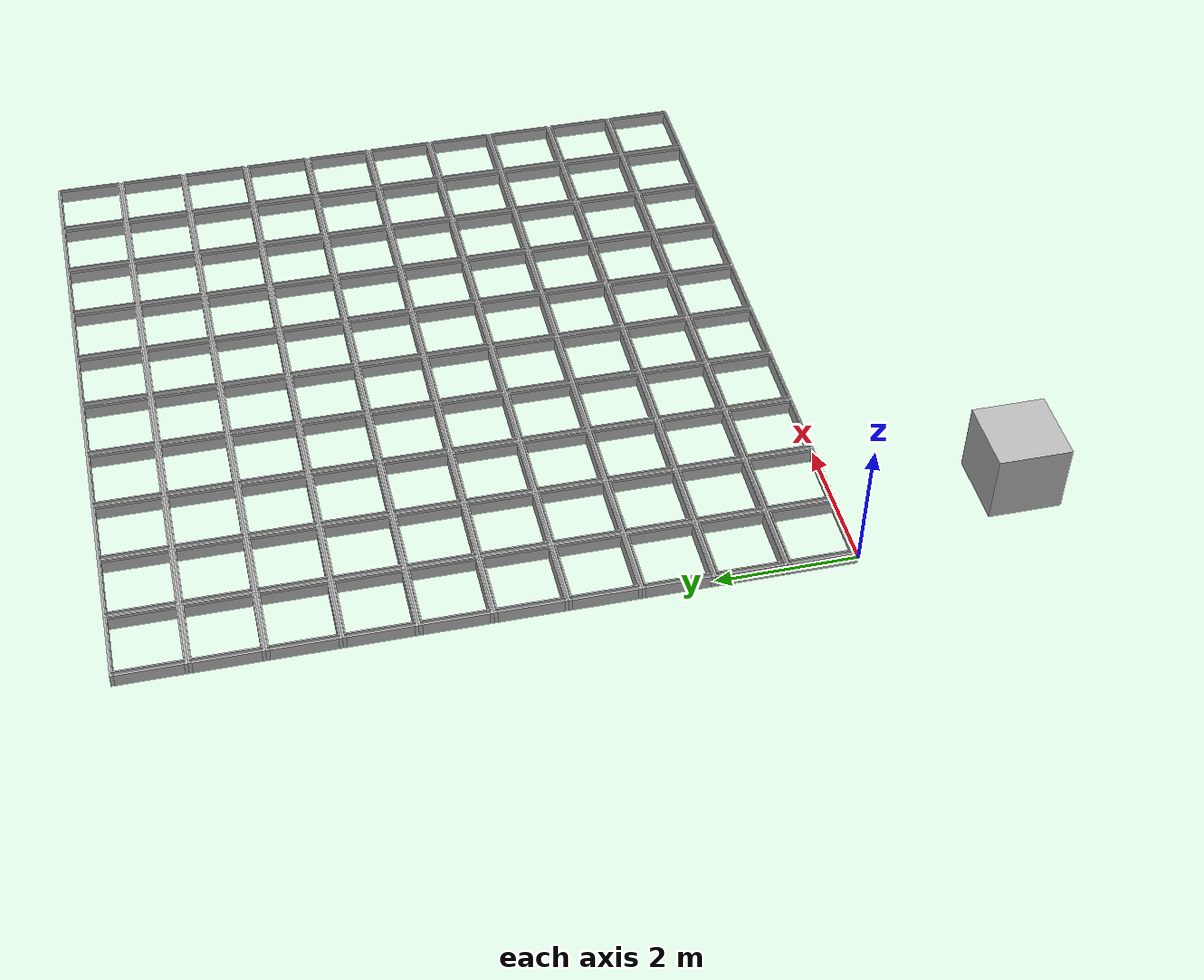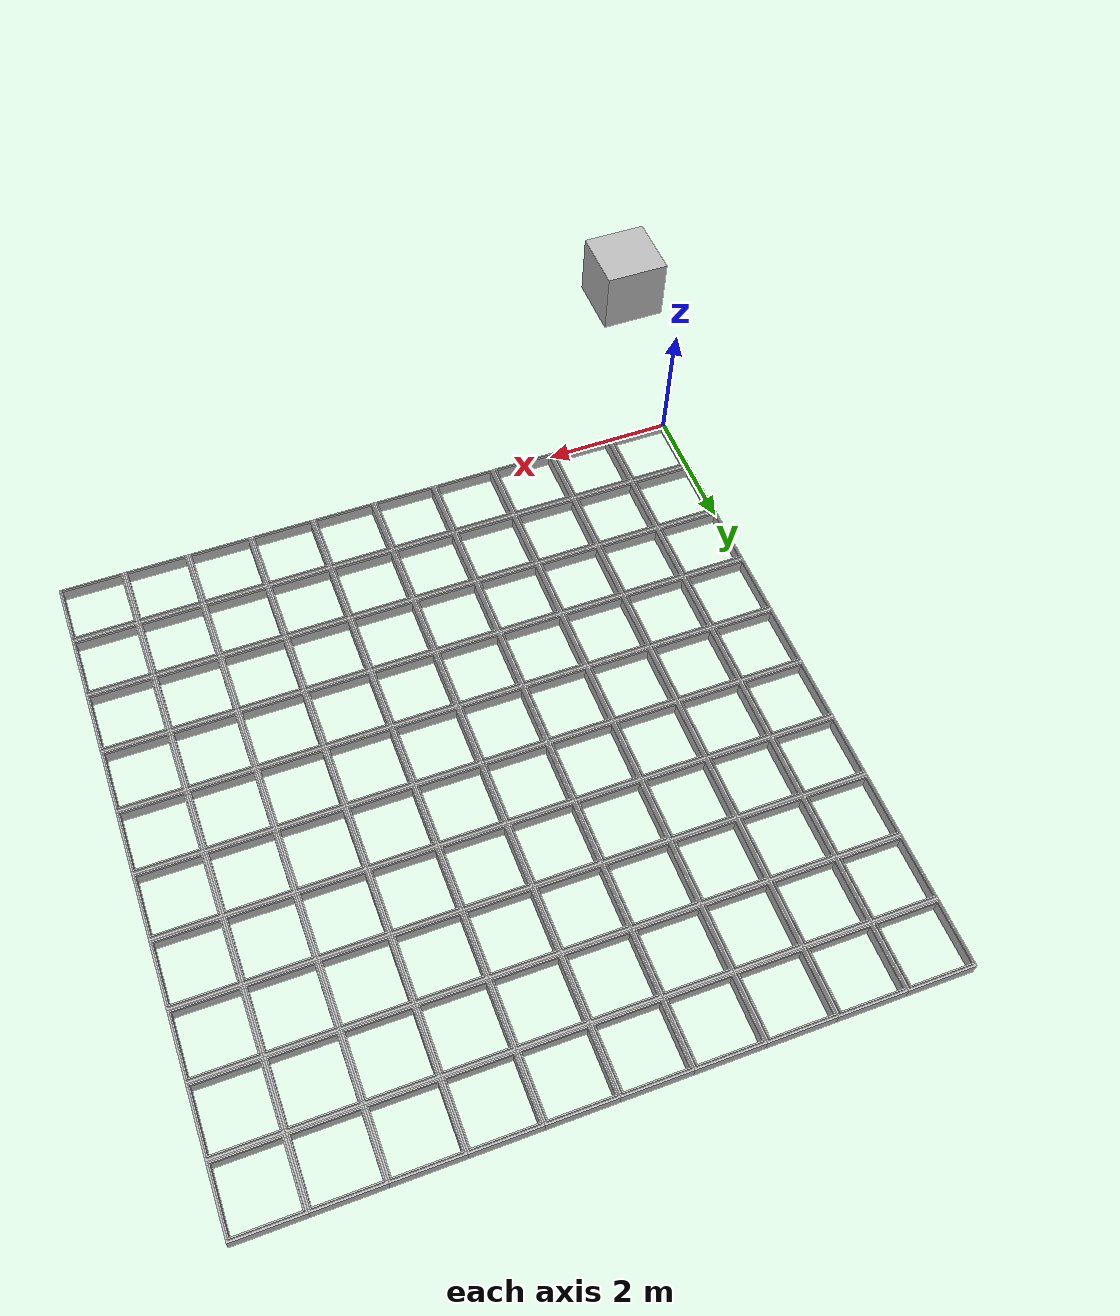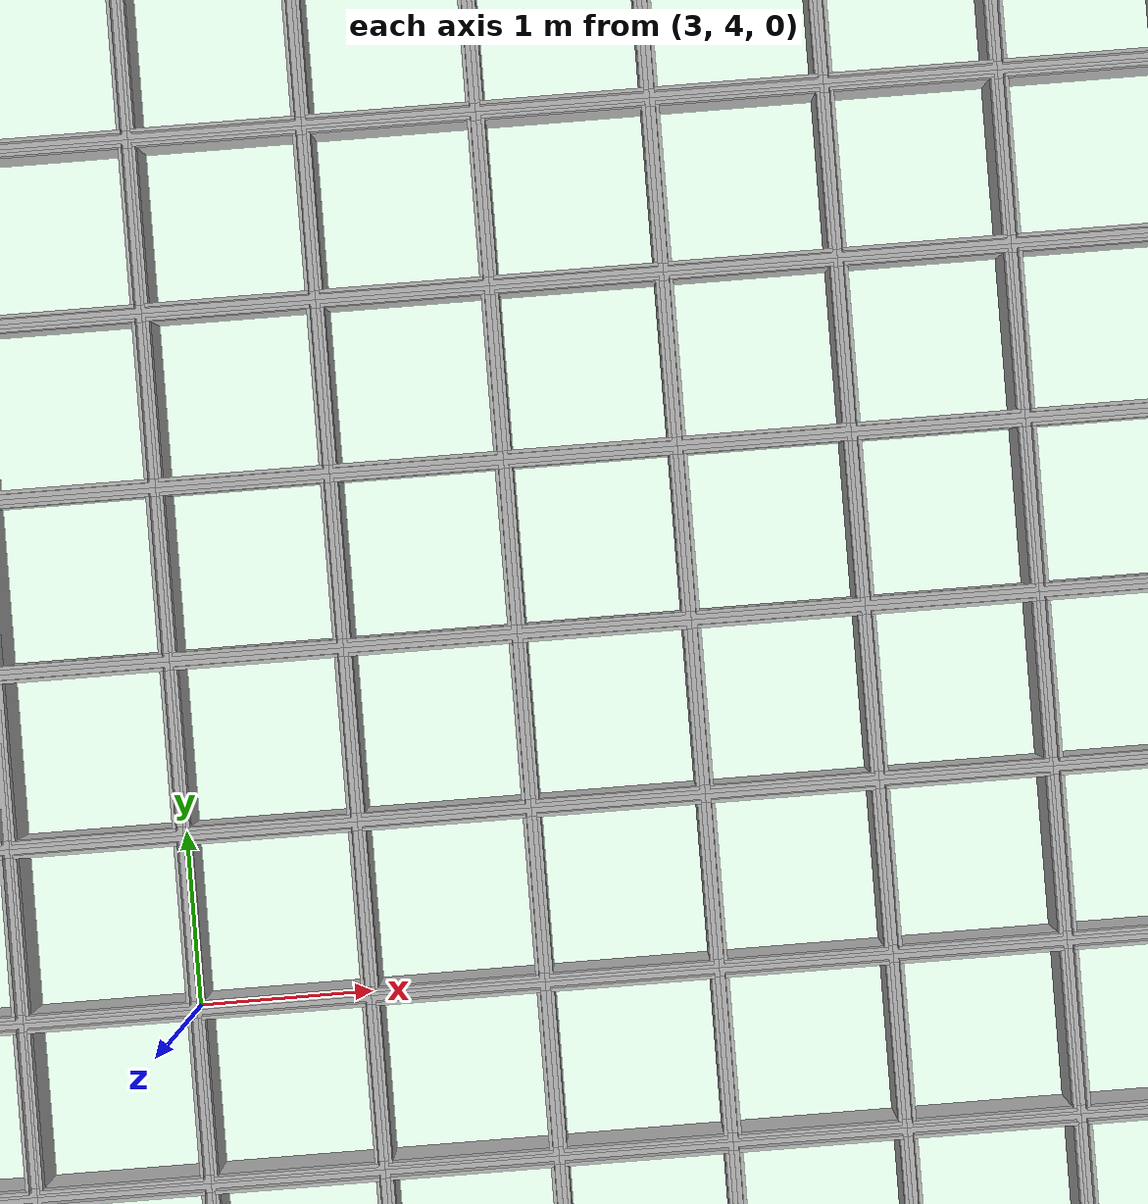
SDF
<?xml version="1.0"?>

<sdf version='1.4'>
	<model name="box">
      <pose>0 -2 1.5 0 0 0</pose>
      <link name="link">
        <collision name="collision">
          <geometry>
            <box>
              <size>1 1 1</size>
            </box>
          </geometry>
        </collision>
        <visual name="visual">
          <geometry>
            <box>
              <size>1 1 1</size>
            </box>
          </geometry>
        </visual>
      </link>
      <plugin name="harness" filename="libgazebo_ros_harness.so">
        <ros>
          <namespace>demo</namespace>
          <argument>box/harness/velocity:=velocity_demo</argument>
          <argument>box/harness/detach:=detach_demo</argument>
        </ros>
        <!-- set initial harness velocity -->

        <joint name="joint1" type="prismatic">
          <!-- The joint that raises or lowers the harness.
           This must be specified within the body of this plugin. -->
          <pose>0 0 0 0 0 0</pose>
          <parent>world</parent>
          <child>link</child>
          <axis>
            <xyz>0 0 1</xyz>
            <dynamics>
              <damping>10</damping>
            </dynamics>
            <limit>
              <lower>-1.5</lower>
              <upper>1.5</upper>
              <effort>10000</effort>
              <velocity>-1</velocity>
              <stiffness>0</stiffness>
              <dissipation>0</dissipation>
            </limit>
          </axis>
          <physics>
            <ode>
              <implicit_spring_damper>1</implicit_spring_damper>
              <limit>
                <cfm>0.0</cfm>
                <erp>0.0</erp>
              </limit>
            </ode>
          </physics>
        </joint>

        <winch>
          <joint>joint1</joint>
          <!-- PID value for velocity control of the winch. -->
          <pos_pid>
            <p>1000000</p>
            <i>0</i>
            <d>0</d>
            <i_min>0</i_min>
            <i_max>0</i_max>
            <cmd_min>-10000</cmd_min>
            <cmd_max>10000</cmd_max>
          </pos_pid>

          <vel_pid>
            <p>10000</p>
            <i>0</i>
            <d>0</d>
            <i_min>0</i_min>
            <i_max>0</i_max>
            <cmd_min>0</cmd_min>
            <cmd_max>10000</cmd_max>
          </vel_pid>
        </winch>

        <!-- Joint to detach. Once the joint is detached, it cannot be
          reattached. This must be a joint specified within the
          body of this plugin. -->
        <detach>joint1</detach>
      </plugin>
    </model>
    <model name="Auto Store Frame">
        <static>true</static>

	<!-- row 0 -->
        <link name="cell_00">
            <pose> 0.5 0.5 0 0 0 0 </pose>

			<!-- frame collision -->
            <collision name='frame_collision_x1'>
                <pose> 0 -0.475 0 0 0 0 </pose>
                <geometry>
                    <box>
                        <size> 1 0.05 0.2 0 0 0 </size>
                    </box>
                </geometry>
            </collision>
            <collision name='frame_collision_x2'>
                <pose> 0 0.475 0 0 0 0 </pose>
                <geometry>
                    <box>
                        <size> 1 0.05 0.2 0 0 0 </size>
                    </box>
                </geometry>
            </collision>
            <collision name='frame_collision_y1'>
                <pose> -0.475 0 0 0 0 0 </pose>
                <geometry>
                    <box>
                        <size> 0.05 0.9 0.2 0 0 0 </size>
                    </box>
                </geometry>
            </collision>
            <collision name='frame_collision_y2'>
                <pose> 0.475 0 0 0 0 0 </pose>
                <geometry>
                    <box>
                        <size> 0.05 0.9 0.2 0 0 0 </size>
                    </box>
                </geometry>
            </collision>

			<!-- guide collision -->
			<collision name='guide_collision_x1'>
				<pose> 0 -0.46 0.12 0 0 0 </pose>
				<geometry>
					<box>
						<size> 0.94 0.02 0.04 0 0 0 </size>
					</box>
				</geometry>
			</collision>
			<collision name='guide_collision_x2'>
				<pose> 0 0.46 0.12 0 0 0 </pose>
				<geometry>
					<box>
						<size> 0.94 0.02 0.04 0 0 0 </size>
					</box>
				</geometry>
			</collision>
			<collision name='guide_collision_y1'>
				<pose> -0.46 0 0.12 0 0 0 </pose>
				<geometry>
					<box>
						<size> 0.02 0.9 0.04 0 0 0 </size>
					</box>
				</geometry>
			</collision>
			<collision name='guide_collision_y2'>
				<pose> 0.46 0 0.12 0 0 0 </pose>
				<geometry>
					<box>
						<size> 0.02 0.9 0.04 0 0 0 </size>
					</box>
				</geometry>
			</collision>

			<!-- frame visual -->
            <visual name='frame_visual_x1'>
                <pose> 0 -0.475 0 0 0 0 </pose>
                <geometry>
                    <box>
                        <size> 1 0.05 0.2 0 0 0 </size>
                    </box>
                </geometry>
            </visual>
            <visual name='frame_visual_x2'>
                <pose> 0 0.475 0 0 0 0 </pose>
                <geometry>
                    <box>
                        <size> 1 0.05 0.2 0 0 0 </size>
                    </box>
                </geometry>
            </visual>
            <visual name='frame_visual_y1'>
                <pose> -0.475 0 0 0 0 0 </pose>
                <geometry>
                    <box>
                        <size> 0.05 0.9 0.2 0 0 0 </size>
                    </box>
                </geometry>
            </visual>
            <visual name='frame_visual_y2'>
                <pose> 0.475 0 0 0 0 0 </pose>
                <geometry>
                    <box>
                        <size> 0.05 0.9 0.2 0 0 0 </size>
                    </box>
                </geometry>
            </visual>

			<!-- guide visual -->
			<visual name='guide_visual_x1'>
				<pose> 0 -0.46 0.12 0 0 0 </pose>
				<geometry>
					<box>
						<size> 0.94 0.02 0.04 0 0 0 </size>
					</box>
				</geometry>
			</visual>
			<visual name='guide_visual_x2'>
				<pose> 0 0.46 0.12 0 0 0 </pose>
				<geometry>
					<box>
						<size> 0.94 0.02 0.04 0 0 0 </size>
					</box>
				</geometry>
			</visual>
			<visual name='guide_visual_y1'>
				<pose> -0.46 0 0.12 0 0 0 </pose>
				<geometry>
					<box>
						<size> 0.02 0.9 0.04 0 0 0 </size>
					</box>
				</geometry>
			</visual>
			<visual name='guide_visual_y2'>
				<pose> 0.46 0 0.12 0 0 0 </pose>
				<geometry>
					<box>
						<size> 0.02 0.9 0.04 0 0 0 </size>
					</box>
				</geometry>
			</visual>
        </link>

        <link name="cell_01">
            <pose> 0.5 1.5 0 0 0 0 </pose>

			<!-- frame collision -->
            <collision name='frame_collision_x1'>
                <pose> 0 -0.475 0 0 0 0 </pose>
                <geometry>
                    <box>
                        <size> 1 0.05 0.2 0 0 0 </size>
                    </box>
                </geometry>
            </collision>
            <collision name='frame_collision_x2'>
                <pose> 0 0.475 0 0 0 0 </pose>
                <geometry>
                    <box>
                        <size> 1 0.05 0.2 0 0 0 </size>
                    </box>
                </geometry>
            </collision>
            <collision name='frame_collision_y1'>
                <pose> -0.475 0 0 0 0 0 </pose>
                <geometry>
                    <box>
                        <size> 0.05 0.9 0.2 0 0 0 </size>
                    </box>
                </geometry>
            </collision>
            <collision name='frame_collision_y2'>
                <pose> 0.475 0 0 0 0 0 </pose>
                <geometry>
                    <box>
                        <size> 0.05 0.9 0.2 0 0 0 </size>
                    </box>
                </geometry>
            </collision>

			<!-- guide collision -->
			<collision name='guide_collision_x1'>
				<pose> 0 -0.46 0.12 0 0 0 </pose>
				<geometry>
					<box>
						<size> 0.94 0.02 0.04 0 0 0 </size>
					</box>
				</geometry>
			</collision>
			<collision name='guide_collision_x2'>
				<pose> 0 0.46 0.12 0 0 0 </pose>
				<geometry>
					<box>
						<size> 0.94 0.02 0.04 0 0 0 </size>
					</box>
				</geometry>
			</collision>
			<collision name='guide_collision_y1'>
				<pose> -0.46 0 0.12 0 0 0 </pose>
				<geometry>
					<box>
						<size> 0.02 0.9 0.04 0 0 0 </size>
					</box>
				</geometry>
			</collision>
			<collision name='guide_collision_y2'>
				<pose> 0.46 0 0.12 0 0 0 </pose>
				<geometry>
					<box>
						<size> 0.02 0.9 0.04 0 0 0 </size>
					</box>
				</geometry>
			</collision>

			<!-- frame visual -->
            <visual name='frame_visual_x1'>
                <pose> 0 -0.475 0 0 0 0 </pose>
                <geometry>
                    <box>
                        <size> 1 0.05 0.2 0 0 0 </size>
                    </box>
                </geometry>
            </visual>
            <visual name='frame_visual_x2'>
                <pose> 0 0.475 0 0 0 0 </pose>
                <geometry>
                    <box>
                        <size> 1 0.05 0.2 0 0 0 </size>
                    </box>
                </geometry>
            </visual>
            <visual name='frame_visual_y1'>
                <pose> -0.475 0 0 0 0 0 </pose>
                <geometry>
                    <box>
                        <size> 0.05 0.9 0.2 0 0 0 </size>
                    </box>
                </geometry>
            </visual>
            <visual name='frame_visual_y2'>
                <pose> 0.475 0 0 0 0 0 </pose>
                <geometry>
                    <box>
                        <size> 0.05 0.9 0.2 0 0 0 </size>
                    </box>
                </geometry>
            </visual>

			<!-- guide visual -->
			<visual name='guide_visual_x1'>
				<pose> 0 -0.46 0.12 0 0 0 </pose>
				<geometry>
					<box>
						<size> 0.94 0.02 0.04 0 0 0 </size>
					</box>
				</geometry>
			</visual>
			<visual name='guide_visual_x2'>
				<pose> 0 0.46 0.12 0 0 0 </pose>
				<geometry>
					<box>
						<size> 0.94 0.02 0.04 0 0 0 </size>
					</box>
				</geometry>
			</visual>
			<visual name='guide_visual_y1'>
				<pose> -0.46 0 0.12 0 0 0 </pose>
				<geometry>
					<box>
						<size> 0.02 0.9 0.04 0 0 0 </size>
					</box>
				</geometry>
			</visual>
			<visual name='guide_visual_y2'>
				<pose> 0.46 0 0.12 0 0 0 </pose>
				<geometry>
					<box>
						<size> 0.02 0.9 0.04 0 0 0 </size>
					</box>
				</geometry>
			</visual>
        </link>

        <link name="cell_02">
            <pose> 0.5 2.5 0 0 0 0 </pose>

			<!-- frame collision -->
            <collision name='frame_collision_x1'>
                <pose> 0 -0.475 0 0 0 0 </pose>
                <geometry>
                    <box>
                        <size> 1 0.05 0.2 0 0 0 </size>
                    </box>
                </geometry>
            </collision>
            <collision name='frame_collision_x2'>
                <pose> 0 0.475 0 0 0 0 </pose>
                <geometry>
                    <box>
                        <size> 1 0.05 0.2 0 0 0 </size>
                    </box>
                </geometry>
            </collision>
            <collision name='frame_collision_y1'>
                <pose> -0.475 0 0 0 0 0 </pose>
                <geometry>
                    <box>
                        <size> 0.05 0.9 0.2 0 0 0 </size>
                    </box>
                </geometry>
            </collision>
            <collision name='frame_collision_y2'>
                <pose> 0.475 0 0 0 0 0 </pose>
                <geometry>
                    <box>
                        <size> 0.05 0.9 0.2 0 0 0 </size>
                    </box>
                </geometry>
            </collision>

			<!-- guide collision -->
			<collision name='guide_collision_x1'>
				<pose> 0 -0.46 0.12 0 0 0 </pose>
				<geometry>
					<box>
						<size> 0.94 0.02 0.04 0 0 0 </size>
					</box>
				</geometry>
			</collision>
			<collision name='guide_collision_x2'>
				<pose> 0 0.46 0.12 0 0 0 </pose>
				<geometry>
					<box>
						<size> 0.94 0.02 0.04 0 0 0 </size>
					</box>
				</geometry>
			</collision>
			<collision name='guide_collision_y1'>
				<pose> -0.46 0 0.12 0 0 0 </pose>
				<geometry>
					<box>
						<size> 0.02 0.9 0.04 0 0 0 </size>
					</box>
				</geometry>
			</collision>
			<collision name='guide_collision_y2'>
				<pose> 0.46 0 0.12 0 0 0 </pose>
				<geometry>
					<box>
						<size> 0.02 0.9 0.04 0 0 0 </size>
					</box>
				</geometry>
			</collision>

			<!-- frame visual -->
            <visual name='frame_visual_x1'>
                <pose> 0 -0.475 0 0 0 0 </pose>
                <geometry>
                    <box>
                        <size> 1 0.05 0.2 0 0 0 </size>
                    </box>
                </geometry>
            </visual>
            <visual name='frame_visual_x2'>
                <pose> 0 0.475 0 0 0 0 </pose>
                <geometry>
                    <box>
                        <size> 1 0.05 0.2 0 0 0 </size>
                    </box>
                </geometry>
            </visual>
            <visual name='frame_visual_y1'>
                <pose> -0.475 0 0 0 0 0 </pose>
                <geometry>
                    <box>
                        <size> 0.05 0.9 0.2 0 0 0 </size>
                    </box>
                </geometry>
            </visual>
            <visual name='frame_visual_y2'>
                <pose> 0.475 0 0 0 0 0 </pose>
                <geometry>
                    <box>
                        <size> 0.05 0.9 0.2 0 0 0 </size>
                    </box>
                </geometry>
            </visual>

			<!-- guide visual -->
			<visual name='guide_visual_x1'>
				<pose> 0 -0.46 0.12 0 0 0 </pose>
				<geometry>
					<box>
						<size> 0.94 0.02 0.04 0 0 0 </size>
					</box>
				</geometry>
			</visual>
			<visual name='guide_visual_x2'>
				<pose> 0 0.46 0.12 0 0 0 </pose>
				<geometry>
					<box>
						<size> 0.94 0.02 0.04 0 0 0 </size>
					</box>
				</geometry>
			</visual>
			<visual name='guide_visual_y1'>
				<pose> -0.46 0 0.12 0 0 0 </pose>
				<geometry>
					<box>
						<size> 0.02 0.9 0.04 0 0 0 </size>
					</box>
				</geometry>
			</visual>
			<visual name='guide_visual_y2'>
				<pose> 0.46 0 0.12 0 0 0 </pose>
				<geometry>
					<box>
						<size> 0.02 0.9 0.04 0 0 0 </size>
					</box>
				</geometry>
			</visual>
        </link>

        <link name="cell_03">
            <pose> 0.5 3.5 0 0 0 0 </pose>

			<!-- frame collision -->
            <collision name='frame_collision_x1'>
                <pose> 0 -0.475 0 0 0 0 </pose>
                <geometry>
                    <box>
                        <size> 1 0.05 0.2 0 0 0 </size>
                    </box>
                </geometry>
            </collision>
            <collision name='frame_collision_x2'>
                <pose> 0 0.475 0 0 0 0 </pose>
                <geometry>
                    <box>
                        <size> 1 0.05 0.2 0 0 0 </size>
                    </box>
                </geometry>
            </collision>
            <collision name='frame_collision_y1'>
                <pose> -0.475 0 0 0 0 0 </pose>
                <geometry>
                    <box>
                        <size> 0.05 0.9 0.2 0 0 0 </size>
                    </box>
                </geometry>
            </collision>
            <collision name='frame_collision_y2'>
                <pose> 0.475 0 0 0 0 0 </pose>
                <geometry>
                    <box>
                        <size> 0.05 0.9 0.2 0 0 0 </size>
                    </box>
                </geometry>
            </collision>

			<!-- guide collision -->
			<collision name='guide_collision_x1'>
				<pose> 0 -0.46 0.12 0 0 0 </pose>
				<geometry>
					<box>
						<size> 0.94 0.02 0.04 0 0 0 </size>
					</box>
				</geometry>
			</collision>
			<collision name='guide_collision_x2'>
				<pose> 0 0.46 0.12 0 0 0 </pose>
				<geometry>
					<box>
						<size> 0.94 0.02 0.04 0 0 0 </size>
					</box>
				</geometry>
			</collision>
			<collision name='guide_collision_y1'>
				<pose> -0.46 0 0.12 0 0 0 </pose>
				<geometry>
					<box>
						<size> 0.02 0.9 0.04 0 0 0 </size>
					</box>
				</geometry>
			</collision>
			<collision name='guide_collision_y2'>
				<pose> 0.46 0 0.12 0 0 0 </pose>
				<geometry>
					<box>
						<size> 0.02 0.9 0.04 0 0 0 </size>
					</box>
				</geometry>
			</collision>

			<!-- frame visual -->
            <visual name='frame_visual_x1'>
                <pose> 0 -0.475 0 0 0 0 </pose>
                <geometry>
                    <box>
                        <size> 1 0.05 0.2 0 0 0 </size>
                    </box>
                </geometry>
            </visual>
            <visual name='frame_visual_x2'>
                <pose> 0 0.475 0 0 0 0 </pose>
                <geometry>
                    <box>
                        <size> 1 0.05 0.2 0 0 0 </size>
                    </box>
                </geometry>
            </visual>
            <visual name='frame_visual_y1'>
                <pose> -0.475 0 0 0 0 0 </pose>
                <geometry>
                    <box>
                        <size> 0.05 0.9 0.2 0 0 0 </size>
                    </box>
                </geometry>
            </visual>
            <visual name='frame_visual_y2'>
                <pose> 0.475 0 0 0 0 0 </pose>
                <geometry>
                    <box>
                        <size> 0.05 0.9 0.2 0 0 0 </size>
                    </box>
                </geometry>
            </visual>

			<!-- guide visual -->
			<visual name='guide_visual_x1'>
				<pose> 0 -0.46 0.12 0 0 0 </pose>
				<geometry>
					<box>
						<size> 0.94 0.02 0.04 0 0 0 </size>
					</box>
				</geometry>
			</visual>
			<visual name='guide_visual_x2'>
				<pose> 0 0.46 0.12 0 0 0 </pose>
				<geometry>
					<box>
						<size> 0.94 0.02 0.04 0 0 0 </size>
					</box>
				</geometry>
			</visual>
			<visual name='guide_visual_y1'>
				<pose> -0.46 0 0.12 0 0 0 </pose>
				<geometry>
					<box>
						<size> 0.02 0.9 0.04 0 0 0 </size>
					</box>
				</geometry>
			</visual>
			<visual name='guide_visual_y2'>
				<pose> 0.46 0 0.12 0 0 0 </pose>
				<geometry>
					<box>
						<size> 0.02 0.9 0.04 0 0 0 </size>
					</box>
				</geometry>
			</visual>
        </link>

        <link name="cell_04">
            <pose> 0.5 4.5 0 0 0 0 </pose>

			<!-- frame collision -->
            <collision name='frame_collision_x1'>
                <pose> 0 -0.475 0 0 0 0 </pose>
                <geometry>
                    <box>
                        <size> 1 0.05 0.2 0 0 0 </size>
                    </box>
                </geometry>
            </collision>
            <collision name='frame_collision_x2'>
                <pose> 0 0.475 0 0 0 0 </pose>
                <geometry>
                    <box>
                        <size> 1 0.05 0.2 0 0 0 </size>
                    </box>
                </geometry>
            </collision>
            <collision name='frame_collision_y1'>
                <pose> -0.475 0 0 0 0 0 </pose>
                <geometry>
                    <box>
                        <size> 0.05 0.9 0.2 0 0 0 </size>
                    </box>
                </geometry>
            </collision>
            <collision name='frame_collision_y2'>
                <pose> 0.475 0 0 0 0 0 </pose>
                <geometry>
                    <box>
                        <size> 0.05 0.9 0.2 0 0 0 </size>
                    </box>
                </geometry>
            </collision>

			<!-- guide collision -->
			<collision name='guide_collision_x1'>
				<pose> 0 -0.46 0.12 0 0 0 </pose>
				<geometry>
					<box>
						<size> 0.94 0.02 0.04 0 0 0 </size>
					</box>
				</geometry>
			</collision>
			<collision name='guide_collision_x2'>
				<pose> 0 0.46 0.12 0 0 0 </pose>
				<geometry>
					<box>
						<size> 0.94 0.02 0.04 0 0 0 </size>
					</box>
				</geometry>
			</collision>
			<collision name='guide_collision_y1'>
				<pose> -0.46 0 0.12 0 0 0 </pose>
				<geometry>
					<box>
						<size> 0.02 0.9 0.04 0 0 0 </size>
					</box>
				</geometry>
			</collision>
			<collision name='guide_collision_y2'>
				<pose> 0.46 0 0.12 0 0 0 </pose>
				<geometry>
					<box>
						<size> 0.02 0.9 0.04 0 0 0 </size>
					</box>
				</geometry>
			</collision>

			<!-- frame visual -->
            <visual name='frame_visual_x1'>
                <pose> 0 -0.475 0 0 0 0 </pose>
                <geometry>
                    <box>
                        <size> 1 0.05 0.2 0 0 0 </size>
                    </box>
                </geometry>
            </visual>
            <visual name='frame_visual_x2'>
                <pose> 0 0.475 0 0 0 0 </pose>
                <geometry>
                    <box>
                        <size> 1 0.05 0.2 0 0 0 </size>
                    </box>
                </geometry>
            </visual>
            <visual name='frame_visual_y1'>
                <pose> -0.475 0 0 0 0 0 </pose>
                <geometry>
                    <box>
                        <size> 0.05 0.9 0.2 0 0 0 </size>
                    </box>
                </geometry>
            </visual>
            <visual name='frame_visual_y2'>
                <pose> 0.475 0 0 0 0 0 </pose>
                <geometry>
                    <box>
                        <size> 0.05 0.9 0.2 0 0 0 </size>
                    </box>
                </geometry>
            </visual>

			<!-- guide visual -->
			<visual name='guide_visual_x1'>
				<pose> 0 -0.46 0.12 0 0 0 </pose>
				<geometry>
					<box>
						<size> 0.94 0.02 0.04 0 0 0 </size>
					</box>
				</geometry>
			</visual>
			<visual name='guide_visual_x2'>
				<pose> 0 0.46 0.12 0 0 0 </pose>
				<geometry>
					<box>
						<size> 0.94 0.02 0.04 0 0 0 </size>
					</box>
				</geometry>
			</visual>
			<visual name='guide_visual_y1'>
				<pose> -0.46 0 0.12 0 0 0 </pose>
				<geometry>
					<box>
						<size> 0.02 0.9 0.04 0 0 0 </size>
					</box>
				</geometry>
			</visual>
			<visual name='guide_visual_y2'>
				<pose> 0.46 0 0.12 0 0 0 </pose>
				<geometry>
					<box>
						<size> 0.02 0.9 0.04 0 0 0 </size>
					</box>
				</geometry>
			</visual>
        </link>

        <link name="cell_05">
            <pose> 0.5 5.5 0 0 0 0 </pose>

			<!-- frame collision -->
            <collision name='frame_collision_x1'>
                <pose> 0 -0.475 0 0 0 0 </pose>
                <geometry>
                    <box>
                        <size> 1 0.05 0.2 0 0 0 </size>
                    </box>
                </geometry>
            </collision>
            <collision name='frame_collision_x2'>
                <pose> 0 0.475 0 0 0 0 </pose>
                <geometry>
                    <box>
                        <size> 1 0.05 0.2 0 0 0 </size>
                    </box>
                </geometry>
            </collision>
            <collision name='frame_collision_y1'>
                <pose> -0.475 0 0 0 0 0 </pose>
                <geometry>
                    <box>
                        <size> 0.05 0.9 0.2 0 0 0 </size>
                    </box>
                </geometry>
            </collision>
            <collision name='frame_collision_y2'>
                <pose> 0.475 0 0 0 0 0 </pose>
                <geometry>
                    <box>
                        <size> 0.05 0.9 0.2 0 0 0 </size>
                    </box>
                </geometry>
            </collision>

			<!-- guide collision -->
			<collision name='guide_collision_x1'>
				<pose> 0 -0.46 0.12 0 0 0 </pose>
				<geometry>
					<box>
						<size> 0.94 0.02 0.04 0 0 0 </size>
					</box>
				</geometry>
			</collision>
			<collision name='guide_collision_x2'>
				<pose> 0 0.46 0.12 0 0 0 </pose>
				<geometry>
					<box>
						<size> 0.94 0.02 0.04 0 0 0 </size>
					</box>
				</geometry>
			</collision>
			<collision name='guide_collision_y1'>
				<pose> -0.46 0 0.12 0 0 0 </pose>
				<geometry>
					<box>
						<size> 0.02 0.9 0.04 0 0 0 </size>
					</box>
				</geometry>
			</collision>
			<collision name='guide_collision_y2'>
				<pose> 0.46 0 0.12 0 0 0 </pose>
				<geometry>
					<box>
						<size> 0.02 0.9 0.04 0 0 0 </size>
					</box>
				</geometry>
			</collision>

			<!-- frame visual -->
            <visual name='frame_visual_x1'>
                <pose> 0 -0.475 0 0 0 0 </pose>
                <geometry>
                    <box>
                        <size> 1 0.05 0.2 0 0 0 </size>
                    </box>
                </geometry>
            </visual>
            <visual name='frame_visual_x2'>
                <pose> 0 0.475 0 0 0 0 </pose>
                <geometry>
                    <box>
                        <size> 1 0.05 0.2 0 0 0 </size>
                    </box>
                </geometry>
            </visual>
            <visual name='frame_visual_y1'>
                <pose> -0.475 0 0 0 0 0 </pose>
                <geometry>
                    <box>
                        <size> 0.05 0.9 0.2 0 0 0 </size>
                    </box>
                </geometry>
            </visual>
            <visual name='frame_visual_y2'>
                <pose> 0.475 0 0 0 0 0 </pose>
                <geometry>
                    <box>
                        <size> 0.05 0.9 0.2 0 0 0 </size>
                    </box>
                </geometry>
            </visual>

			<!-- guide visual -->
			<visual name='guide_visual_x1'>
				<pose> 0 -0.46 0.12 0 0 0 </pose>
				<geometry>
					<box>
						<size> 0.94 0.02 0.04 0 0 0 </size>
					</box>
				</geometry>
			</visual>
			<visual name='guide_visual_x2'>
				<pose> 0 0.46 0.12 0 0 0 </pose>
				<geometry>
					<box>
						<size> 0.94 0.02 0.04 0 0 0 </size>
					</box>
				</geometry>
			</visual>
			<visual name='guide_visual_y1'>
				<pose> -0.46 0 0.12 0 0 0 </pose>
				<geometry>
					<box>
						<size> 0.02 0.9 0.04 0 0 0 </size>
					</box>
				</geometry>
			</visual>
			<visual name='guide_visual_y2'>
				<pose> 0.46 0 0.12 0 0 0 </pose>
				<geometry>
					<box>
						<size> 0.02 0.9 0.04 0 0 0 </size>
					</box>
				</geometry>
			</visual>
        </link>

        <link name="cell_06">
            <pose> 0.5 6.5 0 0 0 0 </pose>

			<!-- frame collision -->
            <collision name='frame_collision_x1'>
                <pose> 0 -0.475 0 0 0 0 </pose>
                <geometry>
                    <box>
                        <size> 1 0.05 0.2 0 0 0 </size>
                    </box>
                </geometry>
            </collision>
            <collision name='frame_collision_x2'>
                <pose> 0 0.475 0 0 0 0 </pose>
                <geometry>
                    <box>
                        <size> 1 0.05 0.2 0 0 0 </size>
                    </box>
                </geometry>
            </collision>
            <collision name='frame_collision_y1'>
                <pose> -0.475 0 0 0 0 0 </pose>
                <geometry>
                    <box>
                        <size> 0.05 0.9 0.2 0 0 0 </size>
                    </box>
                </geometry>
            </collision>
            <collision name='frame_collision_y2'>
                <pose> 0.475 0 0 0 0 0 </pose>
                <geometry>
                    <box>
                        <size> 0.05 0.9 0.2 0 0 0 </size>
                    </box>
                </geometry>
            </collision>

			<!-- guide collision -->
			<collision name='guide_collision_x1'>
				<pose> 0 -0.46 0.12 0 0 0 </pose>
				<geometry>
					<box>
						<size> 0.94 0.02 0.04 0 0 0 </size>
					</box>
				</geometry>
			</collision>
			<collision name='guide_collision_x2'>
				<pose> 0 0.46 0.12 0 0 0 </pose>
				<geometry>
					<box>
						<size> 0.94 0.02 0.04 0 0 0 </size>
					</box>
				</geometry>
			</collision>
			<collision name='guide_collision_y1'>
				<pose> -0.46 0 0.12 0 0 0 </pose>
				<geometry>
					<box>
						<size> 0.02 0.9 0.04 0 0 0 </size>
					</box>
				</geometry>
			</collision>
			<collision name='guide_collision_y2'>
				<pose> 0.46 0 0.12 0 0 0 </pose>
				<geometry>
					<box>
						<size> 0.02 0.9 0.04 0 0 0 </size>
					</box>
				</geometry>
			</collision>

			<!-- frame visual -->
            <visual name='frame_visual_x1'>
                <pose> 0 -0.475 0 0 0 0 </pose>
                <geometry>
                    <box>
                        <size> 1 0.05 0.2 0 0 0 </size>
                    </box>
                </geometry>
            </visual>
            <visual name='frame_visual_x2'>
                <pose> 0 0.475 0 0 0 0 </pose>
                <geometry>
                    <box>
                        <size> 1 0.05 0.2 0 0 0 </size>
                    </box>
                </geometry>
            </visual>
            <visual name='frame_visual_y1'>
                <pose> -0.475 0 0 0 0 0 </pose>
                <geometry>
                    <box>
                        <size> 0.05 0.9 0.2 0 0 0 </size>
                    </box>
                </geometry>
            </visual>
            <visual name='frame_visual_y2'>
                <pose> 0.475 0 0 0 0 0 </pose>
                <geometry>
                    <box>
                        <size> 0.05 0.9 0.2 0 0 0 </size>
                    </box>
                </geometry>
            </visual>

			<!-- guide visual -->
			<visual name='guide_visual_x1'>
				<pose> 0 -0.46 0.12 0 0 0 </pose>
				<geometry>
					<box>
						<size> 0.94 0.02 0.04 0 0 0 </size>
					</box>
				</geometry>
			</visual>
			<visual name='guide_visual_x2'>
				<pose> 0 0.46 0.12 0 0 0 </pose>
				<geometry>
					<box>
						<size> 0.94 0.02 0.04 0 0 0 </size>
					</box>
				</geometry>
			</visual>
			<visual name='guide_visual_y1'>
				<pose> -0.46 0 0.12 0 0 0 </pose>
				<geometry>
					<box>
						<size> 0.02 0.9 0.04 0 0 0 </size>
					</box>
				</geometry>
			</visual>
			<visual name='guide_visual_y2'>
				<pose> 0.46 0 0.12 0 0 0 </pose>
				<geometry>
					<box>
						<size> 0.02 0.9 0.04 0 0 0 </size>
					</box>
				</geometry>
			</visual>
        </link>

        <link name="cell_07">
            <pose> 0.5 7.5 0 0 0 0 </pose>

			<!-- frame collision -->
            <collision name='frame_collision_x1'>
                <pose> 0 -0.475 0 0 0 0 </pose>
                <geometry>
                    <box>
                        <size> 1 0.05 0.2 0 0 0 </size>
                    </box>
                </geometry>
            </collision>
            <collision name='frame_collision_x2'>
                <pose> 0 0.475 0 0 0 0 </pose>
                <geometry>
                    <box>
                        <size> 1 0.05 0.2 0 0 0 </size>
                    </box>
                </geometry>
            </collision>
            <collision name='frame_collision_y1'>
                <pose> -0.475 0 0 0 0 0 </pose>
                <geometry>
                    <box>
                        <size> 0.05 0.9 0.2 0 0 0 </size>
                    </box>
                </geometry>
            </collision>
            <collision name='frame_collision_y2'>
                <pose> 0.475 0 0 0 0 0 </pose>
                <geometry>
                    <box>
                        <size> 0.05 0.9 0.2 0 0 0 </size>
                    </box>
                </geometry>
            </collision>

			<!-- guide collision -->
			<collision name='guide_collision_x1'>
				<pose> 0 -0.46 0.12 0 0 0 </pose>
				<geometry>
					<box>
						<size> 0.94 0.02 0.04 0 0 0 </size>
					</box>
				</geometry>
			</collision>
			<collision name='guide_collision_x2'>
				<pose> 0 0.46 0.12 0 0 0 </pose>
				<geometry>
					<box>
						<size> 0.94 0.02 0.04 0 0 0 </size>
					</box>
				</geometry>
			</collision>
			<collision name='guide_collision_y1'>
				<pose> -0.46 0 0.12 0 0 0 </pose>
				<geometry>
					<box>
						<size> 0.02 0.9 0.04 0 0 0 </size>
					</box>
				</geometry>
			</collision>
			<collision name='guide_collision_y2'>
				<pose> 0.46 0 0.12 0 0 0 </pose>
				<geometry>
					<box>
						<size> 0.02 0.9 0.04 0 0 0 </size>
					</box>
				</geometry>
			</collision>

			<!-- frame visual -->
            <visual name='frame_visual_x1'>
                <pose> 0 -0.475 0 0 0 0 </pose>
                <geometry>
                    <box>
                        <size> 1 0.05 0.2 0 0 0 </size>
                    </box>
                </geometry>
            </visual>
            <visual name='frame_visual_x2'>
                <pose> 0 0.475 0 0 0 0 </pose>
                <geometry>
                    <box>
                        <size> 1 0.05 0.2 0 0 0 </size>
                    </box>
                </geometry>
            </visual>
            <visual name='frame_visual_y1'>
                <pose> -0.475 0 0 0 0 0 </pose>
                <geometry>
                    <box>
                        <size> 0.05 0.9 0.2 0 0 0 </size>
                    </box>
                </geometry>
            </visual>
            <visual name='frame_visual_y2'>
                <pose> 0.475 0 0 0 0 0 </pose>
                <geometry>
                    <box>
                        <size> 0.05 0.9 0.2 0 0 0 </size>
                    </box>
                </geometry>
            </visual>

			<!-- guide visual -->
			<visual name='guide_visual_x1'>
				<pose> 0 -0.46 0.12 0 0 0 </pose>
				<geometry>
					<box>
						<size> 0.94 0.02 0.04 0 0 0 </size>
					</box>
				</geometry>
			</visual>
			<visual name='guide_visual_x2'>
				<pose> 0 0.46 0.12 0 0 0 </pose>
				<geometry>
					<box>
						<size> 0.94 0.02 0.04 0 0 0 </size>
					</box>
				</geometry>
			</visual>
			<visual name='guide_visual_y1'>
				<pose> -0.46 0 0.12 0 0 0 </pose>
				<geometry>
					<box>
						<size> 0.02 0.9 0.04 0 0 0 </size>
					</box>
				</geometry>
			</visual>
			<visual name='guide_visual_y2'>
				<pose> 0.46 0 0.12 0 0 0 </pose>
				<geometry>
					<box>
						<size> 0.02 0.9 0.04 0 0 0 </size>
					</box>
				</geometry>
			</visual>
        </link>

        <link name="cell_08">
            <pose> 0.5 8.5 0 0 0 0 </pose>

			<!-- frame collision -->
            <collision name='frame_collision_x1'>
                <pose> 0 -0.475 0 0 0 0 </pose>
                <geometry>
                    <box>
                        <size> 1 0.05 0.2 0 0 0 </size>
                    </box>
                </geometry>
            </collision>
            <collision name='frame_collision_x2'>
                <pose> 0 0.475 0 0 0 0 </pose>
                <geometry>
                    <box>
                        <size> 1 0.05 0.2 0 0 0 </size>
                    </box>
                </geometry>
            </collision>
            <collision name='frame_collision_y1'>
                <pose> -0.475 0 0 0 0 0 </pose>
                <geometry>
                    <box>
                        <size> 0.05 0.9 0.2 0 0 0 </size>
                    </box>
                </geometry>
            </collision>
            <collision name='frame_collision_y2'>
                <pose> 0.475 0 0 0 0 0 </pose>
                <geometry>
                    <box>
                        <size> 0.05 0.9 0.2 0 0 0 </size>
                    </box>
                </geometry>
            </collision>

			<!-- guide collision -->
			<collision name='guide_collision_x1'>
				<pose> 0 -0.46 0.12 0 0 0 </pose>
				<geometry>
					<box>
						<size> 0.94 0.02 0.04 0 0 0 </size>
					</box>
				</geometry>
			</collision>
			<collision name='guide_collision_x2'>
				<pose> 0 0.46 0.12 0 0 0 </pose>
				<geometry>
					<box>
						<size> 0.94 0.02 0.04 0 0 0 </size>
					</box>
				</geometry>
			</collision>
			<collision name='guide_collision_y1'>
				<pose> -0.46 0 0.12 0 0 0 </pose>
				<geometry>
					<box>
						<size> 0.02 0.9 0.04 0 0 0 </size>
					</box>
				</geometry>
			</collision>
			<collision name='guide_collision_y2'>
				<pose> 0.46 0 0.12 0 0 0 </pose>
				<geometry>
					<box>
						<size> 0.02 0.9 0.04 0 0 0 </size>
					</box>
				</geometry>
			</collision>

			<!-- frame visual -->
            <visual name='frame_visual_x1'>
                <pose> 0 -0.475 0 0 0 0 </pose>
                <geometry>
                    <box>
                        <size> 1 0.05 0.2 0 0 0 </size>
                    </box>
                </geometry>
            </visual>
            <visual name='frame_visual_x2'>
                <pose> 0 0.475 0 0 0 0 </pose>
                <geometry>
                    <box>
                        <size> 1 0.05 0.2 0 0 0 </size>
                    </box>
                </geometry>
            </visual>
            <visual name='frame_visual_y1'>
                <pose> -0.475 0 0 0 0 0 </pose>
                <geometry>
                    <box>
                        <size> 0.05 0.9 0.2 0 0 0 </size>
                    </box>
                </geometry>
            </visual>
            <visual name='frame_visual_y2'>
                <pose> 0.475 0 0 0 0 0 </pose>
                <geometry>
                    <box>
                        <size> 0.05 0.9 0.2 0 0 0 </size>
                    </box>
                </geometry>
            </visual>

			<!-- guide visual -->
			<visual name='guide_visual_x1'>
				<pose> 0 -0.46 0.12 0 0 0 </pose>
				<geometry>
					<box>
						<size> 0.94 0.02 0.04 0 0 0 </size>
					</box>
				</geometry>
			</visual>
			<visual name='guide_visual_x2'>
				<pose> 0 0.46 0.12 0 0 0 </pose>
				<geometry>
					<box>
						<size> 0.94 0.02 0.04 0 0 0 </size>
					</box>
				</geometry>
			</visual>
			<visual name='guide_visual_y1'>
				<pose> -0.46 0 0.12 0 0 0 </pose>
				<geometry>
					<box>
						<size> 0.02 0.9 0.04 0 0 0 </size>
					</box>
				</geometry>
			</visual>
			<visual name='guide_visual_y2'>
				<pose> 0.46 0 0.12 0 0 0 </pose>
				<geometry>
					<box>
						<size> 0.02 0.9 0.04 0 0 0 </size>
					</box>
				</geometry>
			</visual>
        </link>

        <link name="cell_09">
            <pose> 0.5 9.5 0 0 0 0 </pose>

			<!-- frame collision -->
            <collision name='frame_collision_x1'>
                <pose> 0 -0.475 0 0 0 0 </pose>
                <geometry>
                    <box>
                        <size> 1 0.05 0.2 0 0 0 </size>
                    </box>
                </geometry>
            </collision>
            <collision name='frame_collision_x2'>
                <pose> 0 0.475 0 0 0 0 </pose>
                <geometry>
                    <box>
                        <size> 1 0.05 0.2 0 0 0 </size>
                    </box>
                </geometry>
            </collision>
            <collision name='frame_collision_y1'>
                <pose> -0.475 0 0 0 0 0 </pose>
                <geometry>
                    <box>
                        <size> 0.05 0.9 0.2 0 0 0 </size>
                    </box>
                </geometry>
            </collision>
            <collision name='frame_collision_y2'>
                <pose> 0.475 0 0 0 0 0 </pose>
                <geometry>
                    <box>
                        <size> 0.05 0.9 0.2 0 0 0 </size>
                    </box>
                </geometry>
            </collision>

			<!-- guide collision -->
			<collision name='guide_collision_x1'>
				<pose> 0 -0.46 0.12 0 0 0 </pose>
				<geometry>
					<box>
						<size> 0.94 0.02 0.04 0 0 0 </size>
					</box>
				</geometry>
			</collision>
			<collision name='guide_collision_x2'>
				<pose> 0 0.46 0.12 0 0 0 </pose>
				<geometry>
					<box>
						<size> 0.94 0.02 0.04 0 0 0 </size>
					</box>
				</geometry>
			</collision>
			<collision name='guide_collision_y1'>
				<pose> -0.46 0 0.12 0 0 0 </pose>
				<geometry>
					<box>
						<size> 0.02 0.9 0.04 0 0 0 </size>
					</box>
				</geometry>
			</collision>
			<collision name='guide_collision_y2'>
				<pose> 0.46 0 0.12 0 0 0 </pose>
				<geometry>
					<box>
						<size> 0.02 0.9 0.04 0 0 0 </size>
					</box>
				</geometry>
			</collision>

			<!-- frame visual -->
            <visual name='frame_visual_x1'>
                <pose> 0 -0.475 0 0 0 0 </pose>
                <geometry>
                    <box>
                        <size> 1 0.05 0.2 0 0 0 </size>
                    </box>
                </geometry>
            </visual>
            <visual name='frame_visual_x2'>
                <pose> 0 0.475 0 0 0 0 </pose>
                <geometry>
                    <box>
                        <size> 1 0.05 0.2 0 0 0 </size>
                    </box>
                </geometry>
            </visual>
            <visual name='frame_visual_y1'>
                <pose> -0.475 0 0 0 0 0 </pose>
                <geometry>
                    <box>
                        <size> 0.05 0.9 0.2 0 0 0 </size>
                    </box>
                </geometry>
            </visual>
            <visual name='frame_visual_y2'>
                <pose> 0.475 0 0 0 0 0 </pose>
                <geometry>
                    <box>
                        <size> 0.05 0.9 0.2 0 0 0 </size>
                    </box>
                </geometry>
            </visual>

			<!-- guide visual -->
			<visual name='guide_visual_x1'>
				<pose> 0 -0.46 0.12 0 0 0 </pose>
				<geometry>
					<box>
						<size> 0.94 0.02 0.04 0 0 0 </size>
					</box>
				</geometry>
			</visual>
			<visual name='guide_visual_x2'>
				<pose> 0 0.46 0.12 0 0 0 </pose>
				<geometry>
					<box>
						<size> 0.94 0.02 0.04 0 0 0 </size>
					</box>
				</geometry>
			</visual>
			<visual name='guide_visual_y1'>
				<pose> -0.46 0 0.12 0 0 0 </pose>
				<geometry>
					<box>
						<size> 0.02 0.9 0.04 0 0 0 </size>
					</box>
				</geometry>
			</visual>
			<visual name='guide_visual_y2'>
				<pose> 0.46 0 0.12 0 0 0 </pose>
				<geometry>
					<box>
						<size> 0.02 0.9 0.04 0 0 0 </size>
					</box>
				</geometry>
			</visual>
        </link>

	<!-- row 1 -->

        <link name="cell_10">
            <pose> 1.5 0.5 0 0 0 0 </pose>

			<!-- frame collision -->
            <collision name='frame_collision_x1'>
                <pose> 0 -0.475 0 0 0 0 </pose>
                <geometry>
                    <box>
                        <size> 1 0.05 0.2 0 0 0 </size>
                    </box>
                </geometry>
            </collision>
            <collision name='frame_collision_x2'>
                <pose> 0 0.475 0 0 0 0 </pose>
                <geometry>
                    <box>
                        <size> 1 0.05 0.2 0 0 0 </size>
                    </box>
                </geometry>
            </collision>
            <collision name='frame_collision_y1'>
                <pose> -0.475 0 0 0 0 0 </pose>
                <geometry>
                    <box>
                        <size> 0.05 0.9 0.2 0 0 0 </size>
                    </box>
                </geometry>
            </collision>
            <collision name='frame_collision_y2'>
                <pose> 0.475 0 0 0 0 0 </pose>
                <geometry>
                    <box>
                        <size> 0.05 0.9 0.2 0 0 0 </size>
                    </box>
                </geometry>
            </collision>

			<!-- guide collision -->
			<collision name='guide_collision_x1'>
				<pose> 0 -0.46 0.12 0 0 0 </pose>
				<geometry>
					<box>
						<size> 0.94 0.02 0.04 0 0 0 </size>
					</box>
				</geometry>
			</collision>
			<collision name='guide_collision_x2'>
				<pose> 0 0.46 0.12 0 0 0 </pose>
				<geometry>
					<box>
						<size> 0.94 0.02 0.04 0 0 0 </size>
					</box>
				</geometry>
			</collision>
			<collision name='guide_collision_y1'>
				<pose> -0.46 0 0.12 0 0 0 </pose>
				<geometry>
					<box>
						<size> 0.02 0.9 0.04 0 0 0 </size>
					</box>
				</geometry>
			</collision>
			<collision name='guide_collision_y2'>
				<pose> 0.46 0 0.12 0 0 0 </pose>
				<geometry>
					<box>
						<size> 0.02 0.9 0.04 0 0 0 </size>
					</box>
				</geometry>
			</collision>

			<!-- frame visual -->
            <visual name='frame_visual_x1'>
                <pose> 0 -0.475 0 0 0 0 </pose>
                <geometry>
                    <box>
                        <size> 1 0.05 0.2 0 0 0 </size>
                    </box>
                </geometry>
            </visual>
            <visual name='frame_visual_x2'>
                <pose> 0 0.475 0 0 0 0 </pose>
                <geometry>
                    <box>
                        <size> 1 0.05 0.2 0 0 0 </size>
                    </box>
                </geometry>
            </visual>
            <visual name='frame_visual_y1'>
                <pose> -0.475 0 0 0 0 0 </pose>
                <geometry>
                    <box>
                        <size> 0.05 0.9 0.2 0 0 0 </size>
                    </box>
                </geometry>
            </visual>
            <visual name='frame_visual_y2'>
                <pose> 0.475 0 0 0 0 0 </pose>
                <geometry>
                    <box>
                        <size> 0.05 0.9 0.2 0 0 0 </size>
                    </box>
                </geometry>
            </visual>

			<!-- guide visual -->
			<visual name='guide_visual_x1'>
				<pose> 0 -0.46 0.12 0 0 0 </pose>
				<geometry>
					<box>
						<size> 0.94 0.02 0.04 0 0 0 </size>
					</box>
				</geometry>
			</visual>
			<visual name='guide_visual_x2'>
				<pose> 0 0.46 0.12 0 0 0 </pose>
				<geometry>
					<box>
						<size> 0.94 0.02 0.04 0 0 0 </size>
					</box>
				</geometry>
			</visual>
			<visual name='guide_visual_y1'>
				<pose> -0.46 0 0.12 0 0 0 </pose>
				<geometry>
					<box>
						<size> 0.02 0.9 0.04 0 0 0 </size>
					</box>
				</geometry>
			</visual>
			<visual name='guide_visual_y2'>
				<pose> 0.46 0 0.12 0 0 0 </pose>
				<geometry>
					<box>
						<size> 0.02 0.9 0.04 0 0 0 </size>
					</box>
				</geometry>
			</visual>
        </link>

        <link name="cell_11">
            <pose> 1.5 1.5 0 0 0 0 </pose>

			<!-- frame collision -->
            <collision name='frame_collision_x1'>
                <pose> 0 -0.475 0 0 0 0 </pose>
                <geometry>
                    <box>
                        <size> 1 0.05 0.2 0 0 0 </size>
                    </box>
                </geometry>
            </collision>
            <collision name='frame_collision_x2'>
                <pose> 0 0.475 0 0 0 0 </pose>
                <geometry>
                    <box>
                        <size> 1 0.05 0.2 0 0 0 </size>
                    </box>
                </geometry>
            </collision>
            <collision name='frame_collision_y1'>
                <pose> -0.475 0 0 0 0 0 </pose>
                <geometry>
                    <box>
                        <size> 0.05 0.9 0.2 0 0 0 </size>
                    </box>
                </geometry>
            </collision>
            <collision name='frame_collision_y2'>
                <pose> 0.475 0 0 0 0 0 </pose>
                <geometry>
                    <box>
                        <size> 0.05 0.9 0.2 0 0 0 </size>
                    </box>
                </geometry>
            </collision>

			<!-- guide collision -->
			<collision name='guide_collision_x1'>
				<pose> 0 -0.46 0.12 0 0 0 </pose>
				<geometry>
					<box>
						<size> 0.94 0.02 0.04 0 0 0 </size>
					</box>
				</geometry>
			</collision>
			<collision name='guide_collision_x2'>
				<pose> 0 0.46 0.12 0 0 0 </pose>
				<geometry>
					<box>
						<size> 0.94 0.02 0.04 0 0 0 </size>
					</box>
				</geometry>
			</collision>
			<collision name='guide_collision_y1'>
				<pose> -0.46 0 0.12 0 0 0 </pose>
				<geometry>
					<box>
						<size> 0.02 0.9 0.04 0 0 0 </size>
					</box>
				</geometry>
			</collision>
			<collision name='guide_collision_y2'>
				<pose> 0.46 0 0.12 0 0 0 </pose>
				<geometry>
					<box>
						<size> 0.02 0.9 0.04 0 0 0 </size>
					</box>
				</geometry>
			</collision>

			<!-- frame visual -->
            <visual name='frame_visual_x1'>
                <pose> 0 -0.475 0 0 0 0 </pose>
                <geometry>
                    <box>
                        <size> 1 0.05 0.2 0 0 0 </size>
                    </box>
                </geometry>
            </visual>
            <visual name='frame_visual_x2'>
                <pose> 0 0.475 0 0 0 0 </pose>
                <geometry>
                    <box>
                        <size> 1 0.05 0.2 0 0 0 </size>
                    </box>
                </geometry>
            </visual>
            <visual name='frame_visual_y1'>
                <pose> -0.475 0 0 0 0 0 </pose>
                <geometry>
                    <box>
                        <size> 0.05 0.9 0.2 0 0 0 </size>
                    </box>
                </geometry>
            </visual>
            <visual name='frame_visual_y2'>
                <pose> 0.475 0 0 0 0 0 </pose>
                <geometry>
                    <box>
                        <size> 0.05 0.9 0.2 0 0 0 </size>
                    </box>
                </geometry>
            </visual>

			<!-- guide visual -->
			<visual name='guide_visual_x1'>
				<pose> 0 -0.46 0.12 0 0 0 </pose>
				<geometry>
					<box>
						<size> 0.94 0.02 0.04 0 0 0 </size>
					</box>
				</geometry>
			</visual>
			<visual name='guide_visual_x2'>
				<pose> 0 0.46 0.12 0 0 0 </pose>
				<geometry>
					<box>
						<size> 0.94 0.02 0.04 0 0 0 </size>
					</box>
				</geometry>
			</visual>
			<visual name='guide_visual_y1'>
				<pose> -0.46 0 0.12 0 0 0 </pose>
				<geometry>
					<box>
						<size> 0.02 0.9 0.04 0 0 0 </size>
					</box>
				</geometry>
			</visual>
			<visual name='guide_visual_y2'>
				<pose> 0.46 0 0.12 0 0 0 </pose>
				<geometry>
					<box>
						<size> 0.02 0.9 0.04 0 0 0 </size>
					</box>
				</geometry>
			</visual>
        </link>

        <link name="cell_12">
            <pose> 1.5 2.5 0 0 0 0 </pose>

			<!-- frame collision -->
            <collision name='frame_collision_x1'>
                <pose> 0 -0.475 0 0 0 0 </pose>
                <geometry>
                    <box>
                        <size> 1 0.05 0.2 0 0 0 </size>
                    </box>
                </geometry>
            </collision>
            <collision name='frame_collision_x2'>
                <pose> 0 0.475 0 0 0 0 </pose>
                <geometry>
                    <box>
                        <size> 1 0.05 0.2 0 0 0 </size>
                    </box>
                </geometry>
            </collision>
            <collision name='frame_collision_y1'>
                <pose> -0.475 0 0 0 0 0 </pose>
                <geometry>
                    <box>
                        <size> 0.05 0.9 0.2 0 0 0 </size>
                    </box>
                </geometry>
            </collision>
            <collision name='frame_collision_y2'>
                <pose> 0.475 0 0 0 0 0 </pose>
                <geometry>
                    <box>
                        <size> 0.05 0.9 0.2 0 0 0 </size>
                    </box>
                </geometry>
            </collision>

			<!-- guide collision -->
			<collision name='guide_collision_x1'>
				<pose> 0 -0.46 0.12 0 0 0 </pose>
				<geometry>
					<box>
						<size> 0.94 0.02 0.04 0 0 0 </size>
					</box>
				</geometry>
			</collision>
			<collision name='guide_collision_x2'>
				<pose> 0 0.46 0.12 0 0 0 </pose>
				<geometry>
					<box>
						<size> 0.94 0.02 0.04 0 0 0 </size>
					</box>
				</geometry>
			</collision>
			<collision name='guide_collision_y1'>
				<pose> -0.46 0 0.12 0 0 0 </pose>
				<geometry>
					<box>
						<size> 0.02 0.9 0.04 0 0 0 </size>
					</box>
				</geometry>
			</collision>
			<collision name='guide_collision_y2'>
				<pose> 0.46 0 0.12 0 0 0 </pose>
				<geometry>
					<box>
						<size> 0.02 0.9 0.04 0 0 0 </size>
					</box>
				</geometry>
			</collision>

			<!-- frame visual -->
            <visual name='frame_visual_x1'>
                <pose> 0 -0.475 0 0 0 0 </pose>
                <geometry>
                    <box>
                        <size> 1 0.05 0.2 0 0 0 </size>
                    </box>
                </geometry>
            </visual>
            <visual name='frame_visual_x2'>
                <pose> 0 0.475 0 0 0 0 </pose>
                <geometry>
                    <box>
                        <size> 1 0.05 0.2 0 0 0 </size>
                    </box>
                </geometry>
            </visual>
            <visual name='frame_visual_y1'>
                <pose> -0.475 0 0 0 0 0 </pose>
                <geometry>
                    <box>
                        <size> 0.05 0.9 0.2 0 0 0 </size>
                    </box>
                </geometry>
            </visual>
            <visual name='frame_visual_y2'>
                <pose> 0.475 0 0 0 0 0 </pose>
                <geometry>
                    <box>
                        <size> 0.05 0.9 0.2 0 0 0 </size>
                    </box>
                </geometry>
            </visual>

			<!-- guide visual -->
			<visual name='guide_visual_x1'>
				<pose> 0 -0.46 0.12 0 0 0 </pose>
				<geometry>
					<box>
						<size> 0.94 0.02 0.04 0 0 0 </size>
					</box>
				</geometry>
			</visual>
			<visual name='guide_visual_x2'>
				<pose> 0 0.46 0.12 0 0 0 </pose>
				<geometry>
					<box>
						<size> 0.94 0.02 0.04 0 0 0 </size>
					</box>
				</geometry>
			</visual>
			<visual name='guide_visual_y1'>
				<pose> -0.46 0 0.12 0 0 0 </pose>
				<geometry>
					<box>
						<size> 0.02 0.9 0.04 0 0 0 </size>
					</box>
				</geometry>
			</visual>
			<visual name='guide_visual_y2'>
				<pose> 0.46 0 0.12 0 0 0 </pose>
				<geometry>
					<box>
						<size> 0.02 0.9 0.04 0 0 0 </size>
					</box>
				</geometry>
			</visual>
        </link>

        <link name="cell_13">
            <pose> 1.5 3.5 0 0 0 0 </pose>

			<!-- frame collision -->
            <collision name='frame_collision_x1'>
                <pose> 0 -0.475 0 0 0 0 </pose>
                <geometry>
                    <box>
                        <size> 1 0.05 0.2 0 0 0 </size>
                    </box>
                </geometry>
            </collision>
            <collision name='frame_collision_x2'>
                <pose> 0 0.475 0 0 0 0 </pose>
                <geometry>
                    <box>
                        <size> 1 0.05 0.2 0 0 0 </size>
                    </box>
                </geometry>
            </collision>
            <collision name='frame_collision_y1'>
                <pose> -0.475 0 0 0 0 0 </pose>
                <geometry>
                    <box>
                        <size> 0.05 0.9 0.2 0 0 0 </size>
                    </box>
                </geometry>
            </collision>
            <collision name='frame_collision_y2'>
                <pose> 0.475 0 0 0 0 0 </pose>
                <geometry>
                    <box>
                        <size> 0.05 0.9 0.2 0 0 0 </size>
                    </box>
                </geometry>
            </collision>

			<!-- guide collision -->
			<collision name='guide_collision_x1'>
				<pose> 0 -0.46 0.12 0 0 0 </pose>
				<geometry>
					<box>
						<size> 0.94 0.02 0.04 0 0 0 </size>
					</box>
				</geometry>
			</collision>
			<collision name='guide_collision_x2'>
				<pose> 0 0.46 0.12 0 0 0 </pose>
				<geometry>
					<box>
						<size> 0.94 0.02 0.04 0 0 0 </size>
					</box>
				</geometry>
			</collision>
			<collision name='guide_collision_y1'>
				<pose> -0.46 0 0.12 0 0 0 </pose>
				<geometry>
					<box>
						<size> 0.02 0.9 0.04 0 0 0 </size>
					</box>
				</geometry>
			</collision>
			<collision name='guide_collision_y2'>
				<pose> 0.46 0 0.12 0 0 0 </pose>
				<geometry>
					<box>
						<size> 0.02 0.9 0.04 0 0 0 </size>
					</box>
				</geometry>
			</collision>

			<!-- frame visual -->
            <visual name='frame_visual_x1'>
                <pose> 0 -0.475 0 0 0 0 </pose>
                <geometry>
                    <box>
                        <size> 1 0.05 0.2 0 0 0 </size>
                    </box>
                </geometry>
            </visual>
            <visual name='frame_visual_x2'>
                <pose> 0 0.475 0 0 0 0 </pose>
                <geometry>
                    <box>
                        <size> 1 0.05 0.2 0 0 0 </size>
                    </box>
                </geometry>
            </visual>
            <visual name='frame_visual_y1'>
                <pose> -0.475 0 0 0 0 0 </pose>
                <geometry>
                    <box>
                        <size> 0.05 0.9 0.2 0 0 0 </size>
                    </box>
                </geometry>
            </visual>
            <visual name='frame_visual_y2'>
                <pose> 0.475 0 0 0 0 0 </pose>
                <geometry>
                    <box>
                        <size> 0.05 0.9 0.2 0 0 0 </size>
                    </box>
                </geometry>
            </visual>

			<!-- guide visual -->
			<visual name='guide_visual_x1'>
				<pose> 0 -0.46 0.12 0 0 0 </pose>
				<geometry>
					<box>
						<size> 0.94 0.02 0.04 0 0 0 </size>
					</box>
				</geometry>
			</visual>
			<visual name='guide_visual_x2'>
				<pose> 0 0.46 0.12 0 0 0 </pose>
				<geometry>
					<box>
						<size> 0.94 0.02 0.04 0 0 0 </size>
					</box>
				</geometry>
			</visual>
			<visual name='guide_visual_y1'>
				<pose> -0.46 0 0.12 0 0 0 </pose>
				<geometry>
					<box>
						<size> 0.02 0.9 0.04 0 0 0 </size>
					</box>
				</geometry>
			</visual>
			<visual name='guide_visual_y2'>
				<pose> 0.46 0 0.12 0 0 0 </pose>
				<geometry>
					<box>
						<size> 0.02 0.9 0.04 0 0 0 </size>
					</box>
				</geometry>
			</visual>
        </link>

        <link name="cell_14">
            <pose> 1.5 4.5 0 0 0 0 </pose>

			<!-- frame collision -->
            <collision name='frame_collision_x1'>
                <pose> 0 -0.475 0 0 0 0 </pose>
                <geometry>
                    <box>
                        <size> 1 0.05 0.2 0 0 0 </size>
                    </box>
                </geometry>
            </collision>
            <collision name='frame_collision_x2'>
                <pose> 0 0.475 0 0 0 0 </pose>
                <geometry>
                    <box>
                        <size> 1 0.05 0.2 0 0 0 </size>
                    </box>
                </geometry>
            </collision>
            <collision name='frame_collision_y1'>
                <pose> -0.475 0 0 0 0 0 </pose>
                <geometry>
                    <box>
                        <size> 0.05 0.9 0.2 0 0 0 </size>
                    </box>
                </geometry>
            </collision>
            <collision name='frame_collision_y2'>
                <pose> 0.475 0 0 0 0 0 </pose>
                <geometry>
                    <box>
                        <size> 0.05 0.9 0.2 0 0 0 </size>
                    </box>
                </geometry>
            </collision>

			<!-- guide collision -->
			<collision name='guide_collision_x1'>
				<pose> 0 -0.46 0.12 0 0 0 </pose>
				<geometry>
					<box>
						<size> 0.94 0.02 0.04 0 0 0 </size>
					</box>
				</geometry>
			</collision>
			<collision name='guide_collision_x2'>
				<pose> 0 0.46 0.12 0 0 0 </pose>
				<geometry>
					<box>
						<size> 0.94 0.02 0.04 0 0 0 </size>
					</box>
				</geometry>
			</collision>
			<collision name='guide_collision_y1'>
				<pose> -0.46 0 0.12 0 0 0 </pose>
				<geometry>
					<box>
						<size> 0.02 0.9 0.04 0 0 0 </size>
					</box>
				</geometry>
			</collision>
			<collision name='guide_collision_y2'>
				<pose> 0.46 0 0.12 0 0 0 </pose>
				<geometry>
					<box>
						<size> 0.02 0.9 0.04 0 0 0 </size>
					</box>
				</geometry>
			</collision>

			<!-- frame visual -->
            <visual name='frame_visual_x1'>
                <pose> 0 -0.475 0 0 0 0 </pose>
                <geometry>
                    <box>
                        <size> 1 0.05 0.2 0 0 0 </size>
                    </box>
                </geometry>
            </visual>
            <visual name='frame_visual_x2'>
                <pose> 0 0.475 0 0 0 0 </pose>
                <geometry>
                    <box>
                        <size> 1 0.05 0.2 0 0 0 </size>
                    </box>
                </geometry>
            </visual>
            <visual name='frame_visual_y1'>
                <pose> -0.475 0 0 0 0 0 </pose>
                <geometry>
                    <box>
                        <size> 0.05 0.9 0.2 0 0 0 </size>
                    </box>
                </geometry>
            </visual>
            <visual name='frame_visual_y2'>
                <pose> 0.475 0 0 0 0 0 </pose>
                <geometry>
                    <box>
                        <size> 0.05 0.9 0.2 0 0 0 </size>
                    </box>
                </geometry>
            </visual>

			<!-- guide visual -->
			<visual name='guide_visual_x1'>
				<pose> 0 -0.46 0.12 0 0 0 </pose>
				<geometry>
					<box>
						<size> 0.94 0.02 0.04 0 0 0 </size>
					</box>
				</geometry>
			</visual>
			<visual name='guide_visual_x2'>
				<pose> 0 0.46 0.12 0 0 0 </pose>
				<geometry>
					<box>
						<size> 0.94 0.02 0.04 0 0 0 </size>
					</box>
				</geometry>
			</visual>
			<visual name='guide_visual_y1'>
				<pose> -0.46 0 0.12 0 0 0 </pose>
				<geometry>
					<box>
						<size> 0.02 0.9 0.04 0 0 0 </size>
					</box>
				</geometry>
			</visual>
			<visual name='guide_visual_y2'>
				<pose> 0.46 0 0.12 0 0 0 </pose>
				<geometry>
					<box>
						<size> 0.02 0.9 0.04 0 0 0 </size>
					</box>
				</geometry>
			</visual>
        </link>

        <link name="cell_15">
            <pose> 1.5 5.5 0 0 0 0 </pose>

			<!-- frame collision -->
            <collision name='frame_collision_x1'>
                <pose> 0 -0.475 0 0 0 0 </pose>
                <geometry>
                    <box>
                        <size> 1 0.05 0.2 0 0 0 </size>
                    </box>
                </geometry>
            </collision>
            <collision name='frame_collision_x2'>
                <pose> 0 0.475 0 0 0 0 </pose>
                <geometry>
                    <box>
                        <size> 1 0.05 0.2 0 0 0 </size>
                    </box>
                </geometry>
            </collision>
            <collision name='frame_collision_y1'>
                <pose> -0.475 0 0 0 0 0 </pose>
                <geometry>
                    <box>
                        <size> 0.05 0.9 0.2 0 0 0 </size>
                    </box>
                </geometry>
            </collision>
            <collision name='frame_collision_y2'>
                <pose> 0.475 0 0 0 0 0 </pose>
                <geometry>
                    <box>
                        <size> 0.05 0.9 0.2 0 0 0 </size>
                    </box>
                </geometry>
            </collision>

			<!-- guide collision -->
			<collision name='guide_collision_x1'>
				<pose> 0 -0.46 0.12 0 0 0 </pose>
				<geometry>
					<box>
						<size> 0.94 0.02 0.04 0 0 0 </size>
					</box>
				</geometry>
			</collision>
			<collision name='guide_collision_x2'>
				<pose> 0 0.46 0.12 0 0 0 </pose>
				<geometry>
					<box>
						<size> 0.94 0.02 0.04 0 0 0 </size>
					</box>
				</geometry>
			</collision>
			<collision name='guide_collision_y1'>
				<pose> -0.46 0 0.12 0 0 0 </pose>
				<geometry>
					<box>
						<size> 0.02 0.9 0.04 0 0 0 </size>
					</box>
				</geometry>
			</collision>
			<collision name='guide_collision_y2'>
				<pose> 0.46 0 0.12 0 0 0 </pose>
				<geometry>
					<box>
						<size> 0.02 0.9 0.04 0 0 0 </size>
					</box>
				</geometry>
			</collision>

			<!-- frame visual -->
            <visual name='frame_visual_x1'>
                <pose> 0 -0.475 0 0 0 0 </pose>
                <geometry>
                    <box>
                        <size> 1 0.05 0.2 0 0 0 </size>
                    </box>
                </geometry>
            </visual>
            <visual name='frame_visual_x2'>
                <pose> 0 0.475 0 0 0 0 </pose>
                <geometry>
                    <box>
                        <size> 1 0.05 0.2 0 0 0 </size>
                    </box>
                </geometry>
            </visual>
            <visual name='frame_visual_y1'>
                <pose> -0.475 0 0 0 0 0 </pose>
                <geometry>
                    <box>
                        <size> 0.05 0.9 0.2 0 0 0 </size>
                    </box>
                </geometry>
            </visual>
            <visual name='frame_visual_y2'>
                <pose> 0.475 0 0 0 0 0 </pose>
                <geometry>
                    <box>
                        <size> 0.05 0.9 0.2 0 0 0 </size>
                    </box>
                </geometry>
            </visual>

			<!-- guide visual -->
			<visual name='guide_visual_x1'>
				<pose> 0 -0.46 0.12 0 0 0 </pose>
				<geometry>
					<box>
						<size> 0.94 0.02 0.04 0 0 0 </size>
					</box>
				</geometry>
			</visual>
			<visual name='guide_visual_x2'>
				<pose> 0 0.46 0.12 0 0 0 </pose>
				<geometry>
					<box>
						<size> 0.94 0.02 0.04 0 0 0 </size>
					</box>
				</geometry>
			</visual>
			<visual name='guide_visual_y1'>
				<pose> -0.46 0 0.12 0 0 0 </pose>
				<geometry>
					<box>
						<size> 0.02 0.9 0.04 0 0 0 </size>
					</box>
				</geometry>
			</visual>
			<visual name='guide_visual_y2'>
				<pose> 0.46 0 0.12 0 0 0 </pose>
				<geometry>
					<box>
						<size> 0.02 0.9 0.04 0 0 0 </size>
					</box>
				</geometry>
			</visual>
        </link>

        <link name="cell_16">
            <pose> 1.5 6.5 0 0 0 0 </pose>

			<!-- frame collision -->
            <collision name='frame_collision_x1'>
                <pose> 0 -0.475 0 0 0 0 </pose>
                <geometry>
                    <box>
                        <size> 1 0.05 0.2 0 0 0 </size>
                    </box>
                </geometry>
            </collision>
            <collision name='frame_collision_x2'>
                <pose> 0 0.475 0 0 0 0 </pose>
                <geometry>
                    <box>
                        <size> 1 0.05 0.2 0 0 0 </size>
                    </box>
                </geometry>
            </collision>
            <collision name='frame_collision_y1'>
                <pose> -0.475 0 0 0 0 0 </pose>
                <geometry>
                    <box>
                        <size> 0.05 0.9 0.2 0 0 0 </size>
                    </box>
                </geometry>
            </collision>
            <collision name='frame_collision_y2'>
                <pose> 0.475 0 0 0 0 0 </pose>
                <geometry>
                    <box>
                        <size> 0.05 0.9 0.2 0 0 0 </size>
                    </box>
                </geometry>
            </collision>

			<!-- guide collision -->
			<collision name='guide_collision_x1'>
				<pose> 0 -0.46 0.12 0 0 0 </pose>
				<geometry>
					<box>
						<size> 0.94 0.02 0.04 0 0 0 </size>
					</box>
				</geometry>
			</collision>
			<collision name='guide_collision_x2'>
				<pose> 0 0.46 0.12 0 0 0 </pose>
				<geometry>
					<box>
						<size> 0.94 0.02 0.04 0 0 0 </size>
					</box>
				</geometry>
			</collision>
			<collision name='guide_collision_y1'>
				<pose> -0.46 0 0.12 0 0 0 </pose>
				<geometry>
					<box>
						<size> 0.02 0.9 0.04 0 0 0 </size>
					</box>
				</geometry>
			</collision>
			<collision name='guide_collision_y2'>
				<pose> 0.46 0 0.12 0 0 0 </pose>
				<geometry>
					<box>
						<size> 0.02 0.9 0.04 0 0 0 </size>
					</box>
				</geometry>
			</collision>

			<!-- frame visual -->
            <visual name='frame_visual_x1'>
                <pose> 0 -0.475 0 0 0 0 </pose>
                <geometry>
                    <box>
                        <size> 1 0.05 0.2 0 0 0 </size>
                    </box>
                </geometry>
            </visual>
            <visual name='frame_visual_x2'>
                <pose> 0 0.475 0 0 0 0 </pose>
                <geometry>
                    <box>
                        <size> 1 0.05 0.2 0 0 0 </size>
                    </box>
                </geometry>
            </visual>
            <visual name='frame_visual_y1'>
                <pose> -0.475 0 0 0 0 0 </pose>
                <geometry>
                    <box>
                        <size> 0.05 0.9 0.2 0 0 0 </size>
                    </box>
                </geometry>
            </visual>
            <visual name='frame_visual_y2'>
                <pose> 0.475 0 0 0 0 0 </pose>
                <geometry>
                    <box>
                        <size> 0.05 0.9 0.2 0 0 0 </size>
                    </box>
                </geometry>
            </visual>

			<!-- guide visual -->
			<visual name='guide_visual_x1'>
				<pose> 0 -0.46 0.12 0 0 0 </pose>
				<geometry>
					<box>
						<size> 0.94 0.02 0.04 0 0 0 </size>
					</box>
				</geometry>
			</visual>
			<visual name='guide_visual_x2'>
				<pose> 0 0.46 0.12 0 0 0 </pose>
				<geometry>
					<box>
						<size> 0.94 0.02 0.04 0 0 0 </size>
					</box>
				</geometry>
			</visual>
			<visual name='guide_visual_y1'>
				<pose> -0.46 0 0.12 0 0 0 </pose>
				<geometry>
					<box>
						<size> 0.02 0.9 0.04 0 0 0 </size>
					</box>
				</geometry>
			</visual>
			<visual name='guide_visual_y2'>
				<pose> 0.46 0 0.12 0 0 0 </pose>
				<geometry>
					<box>
						<size> 0.02 0.9 0.04 0 0 0 </size>
					</box>
				</geometry>
			</visual>
        </link>

        <link name="cell_17">
            <pose> 1.5 7.5 0 0 0 0 </pose>

			<!-- frame collision -->
            <collision name='frame_collision_x1'>
                <pose> 0 -0.475 0 0 0 0 </pose>
                <geometry>
                    <box>
                        <size> 1 0.05 0.2 0 0 0 </size>
                    </box>
                </geometry>
            </collision>
            <collision name='frame_collision_x2'>
                <pose> 0 0.475 0 0 0 0 </pose>
                <geometry>
                    <box>
                        <size> 1 0.05 0.2 0 0 0 </size>
                    </box>
                </geometry>
            </collision>
            <collision name='frame_collision_y1'>
                <pose> -0.475 0 0 0 0 0 </pose>
                <geometry>
                    <box>
                        <size> 0.05 0.9 0.2 0 0 0 </size>
                    </box>
                </geometry>
            </collision>
            <collision name='frame_collision_y2'>
                <pose> 0.475 0 0 0 0 0 </pose>
                <geometry>
                    <box>
                        <size> 0.05 0.9 0.2 0 0 0 </size>
                    </box>
                </geometry>
            </collision>

			<!-- guide collision -->
			<collision name='guide_collision_x1'>
				<pose> 0 -0.46 0.12 0 0 0 </pose>
				<geometry>
					<box>
						<size> 0.94 0.02 0.04 0 0 0 </size>
					</box>
				</geometry>
			</collision>
			<collision name='guide_collision_x2'>
				<pose> 0 0.46 0.12 0 0 0 </pose>
				<geometry>
					<box>
						<size> 0.94 0.02 0.04 0 0 0 </size>
					</box>
				</geometry>
			</collision>
			<collision name='guide_collision_y1'>
				<pose> -0.46 0 0.12 0 0 0 </pose>
				<geometry>
					<box>
						<size> 0.02 0.9 0.04 0 0 0 </size>
					</box>
				</geometry>
			</collision>
			<collision name='guide_collision_y2'>
				<pose> 0.46 0 0.12 0 0 0 </pose>
				<geometry>
					<box>
						<size> 0.02 0.9 0.04 0 0 0 </size>
					</box>
				</geometry>
			</collision>

			<!-- frame visual -->
            <visual name='frame_visual_x1'>
                <pose> 0 -0.475 0 0 0 0 </pose>
                <geometry>
                    <box>
                        <size> 1 0.05 0.2 0 0 0 </size>
                    </box>
                </geometry>
            </visual>
            <visual name='frame_visual_x2'>
                <pose> 0 0.475 0 0 0 0 </pose>
                <geometry>
                    <box>
                        <size> 1 0.05 0.2 0 0 0 </size>
                    </box>
                </geometry>
            </visual>
            <visual name='frame_visual_y1'>
                <pose> -0.475 0 0 0 0 0 </pose>
                <geometry>
                    <box>
                        <size> 0.05 0.9 0.2 0 0 0 </size>
                    </box>
                </geometry>
            </visual>
            <visual name='frame_visual_y2'>
                <pose> 0.475 0 0 0 0 0 </pose>
                <geometry>
                    <box>
                        <size> 0.05 0.9 0.2 0 0 0 </size>
                    </box>
                </geometry>
            </visual>

			<!-- guide visual -->
			<visual name='guide_visual_x1'>
				<pose> 0 -0.46 0.12 0 0 0 </pose>
				<geometry>
					<box>
						<size> 0.94 0.02 0.04 0 0 0 </size>
					</box>
				</geometry>
			</visual>
			<visual name='guide_visual_x2'>
				<pose> 0 0.46 0.12 0 0 0 </pose>
				<geometry>
					<box>
						<size> 0.94 0.02 0.04 0 0 0 </size>
					</box>
				</geometry>
			</visual>
			<visual name='guide_visual_y1'>
				<pose> -0.46 0 0.12 0 0 0 </pose>
				<geometry>
					<box>
						<size> 0.02 0.9 0.04 0 0 0 </size>
					</box>
				</geometry>
			</visual>
			<visual name='guide_visual_y2'>
				<pose> 0.46 0 0.12 0 0 0 </pose>
				<geometry>
					<box>
						<size> 0.02 0.9 0.04 0 0 0 </size>
					</box>
				</geometry>
			</visual>
        </link>

        <link name="cell_18">
            <pose> 1.5 8.5 0 0 0 0 </pose>

			<!-- frame collision -->
            <collision name='frame_collision_x1'>
                <pose> 0 -0.475 0 0 0 0 </pose>
                <geometry>
                    <box>
                        <size> 1 0.05 0.2 0 0 0 </size>
                    </box>
                </geometry>
            </collision>
            <collision name='frame_collision_x2'>
                <pose> 0 0.475 0 0 0 0 </pose>
                <geometry>
                    <box>
                        <size> 1 0.05 0.2 0 0 0 </size>
                    </box>
                </geometry>
            </collision>
            <collision name='frame_collision_y1'>
                <pose> -0.475 0 0 0 0 0 </pose>
                <geometry>
                    <box>
                        <size> 0.05 0.9 0.2 0 0 0 </size>
                    </box>
                </geometry>
            </collision>
            <collision name='frame_collision_y2'>
                <pose> 0.475 0 0 0 0 0 </pose>
                <geometry>
                    <box>
                        <size> 0.05 0.9 0.2 0 0 0 </size>
                    </box>
                </geometry>
            </collision>

			<!-- guide collision -->
			<collision name='guide_collision_x1'>
				<pose> 0 -0.46 0.12 0 0 0 </pose>
				<geometry>
					<box>
						<size> 0.94 0.02 0.04 0 0 0 </size>
					</box>
				</geometry>
			</collision>
			<collision name='guide_collision_x2'>
				<pose> 0 0.46 0.12 0 0 0 </pose>
				<geometry>
					<box>
						<size> 0.94 0.02 0.04 0 0 0 </size>
					</box>
				</geometry>
			</collision>
			<collision name='guide_collision_y1'>
				<pose> -0.46 0 0.12 0 0 0 </pose>
				<geometry>
					<box>
						<size> 0.02 0.9 0.04 0 0 0 </size>
					</box>
				</geometry>
			</collision>
			<collision name='guide_collision_y2'>
				<pose> 0.46 0 0.12 0 0 0 </pose>
				<geometry>
					<box>
						<size> 0.02 0.9 0.04 0 0 0 </size>
					</box>
				</geometry>
			</collision>

			<!-- frame visual -->
            <visual name='frame_visual_x1'>
                <pose> 0 -0.475 0 0 0 0 </pose>
                <geometry>
                    <box>
                        <size> 1 0.05 0.2 0 0 0 </size>
                    </box>
                </geometry>
            </visual>
            <visual name='frame_visual_x2'>
                <pose> 0 0.475 0 0 0 0 </pose>
                <geometry>
                    <box>
                        <size> 1 0.05 0.2 0 0 0 </size>
                    </box>
                </geometry>
            </visual>
            <visual name='frame_visual_y1'>
                <pose> -0.475 0 0 0 0 0 </pose>
                <geometry>
                    <box>
                        <size> 0.05 0.9 0.2 0 0 0 </size>
                    </box>
                </geometry>
            </visual>
            <visual name='frame_visual_y2'>
                <pose> 0.475 0 0 0 0 0 </pose>
                <geometry>
                    <box>
                        <size> 0.05 0.9 0.2 0 0 0 </size>
                    </box>
                </geometry>
            </visual>

			<!-- guide visual -->
			<visual name='guide_visual_x1'>
				<pose> 0 -0.46 0.12 0 0 0 </pose>
				<geometry>
					<box>
						<size> 0.94 0.02 0.04 0 0 0 </size>
					</box>
				</geometry>
			</visual>
			<visual name='guide_visual_x2'>
				<pose> 0 0.46 0.12 0 0 0 </pose>
				<geometry>
					<box>
						<size> 0.94 0.02 0.04 0 0 0 </size>
					</box>
				</geometry>
			</visual>
			<visual name='guide_visual_y1'>
				<pose> -0.46 0 0.12 0 0 0 </pose>
				<geometry>
					<box>
						<size> 0.02 0.9 0.04 0 0 0 </size>
					</box>
				</geometry>
			</visual>
			<visual name='guide_visual_y2'>
				<pose> 0.46 0 0.12 0 0 0 </pose>
				<geometry>
					<box>
						<size> 0.02 0.9 0.04 0 0 0 </size>
					</box>
				</geometry>
			</visual>
        </link>

        <link name="cell_19">
            <pose> 1.5 9.5 0 0 0 0 </pose>

			<!-- frame collision -->
            <collision name='frame_collision_x1'>
                <pose> 0 -0.475 0 0 0 0 </pose>
                <geometry>
                    <box>
                        <size> 1 0.05 0.2 0 0 0 </size>
                    </box>
                </geometry>
            </collision>
            <collision name='frame_collision_x2'>
                <pose> 0 0.475 0 0 0 0 </pose>
                <geometry>
                    <box>
                        <size> 1 0.05 0.2 0 0 0 </size>
                    </box>
                </geometry>
            </collision>
            <collision name='frame_collision_y1'>
                <pose> -0.475 0 0 0 0 0 </pose>
                <geometry>
                    <box>
                        <size> 0.05 0.9 0.2 0 0 0 </size>
                    </box>
                </geometry>
            </collision>
            <collision name='frame_collision_y2'>
                <pose> 0.475 0 0 0 0 0 </pose>
                <geometry>
                    <box>
                        <size> 0.05 0.9 0.2 0 0 0 </size>
                    </box>
                </geometry>
            </collision>

			<!-- guide collision -->
			<collision name='guide_collision_x1'>
				<pose> 0 -0.46 0.12 0 0 0 </pose>
				<geometry>
					<box>
						<size> 0.94 0.02 0.04 0 0 0 </size>
					</box>
				</geometry>
			</collision>
			<collision name='guide_collision_x2'>
				<pose> 0 0.46 0.12 0 0 0 </pose>
				<geometry>
					<box>
						<size> 0.94 0.02 0.04 0 0 0 </size>
					</box>
				</geometry>
			</collision>
			<collision name='guide_collision_y1'>
				<pose> -0.46 0 0.12 0 0 0 </pose>
				<geometry>
					<box>
						<size> 0.02 0.9 0.04 0 0 0 </size>
					</box>
				</geometry>
			</collision>
			<collision name='guide_collision_y2'>
				<pose> 0.46 0 0.12 0 0 0 </pose>
				<geometry>
					<box>
						<size> 0.02 0.9 0.04 0 0 0 </size>
					</box>
				</geometry>
			</collision>

			<!-- frame visual -->
            <visual name='frame_visual_x1'>
                <pose> 0 -0.475 0 0 0 0 </pose>
                <geometry>
                    <box>
                        <size> 1 0.05 0.2 0 0 0 </size>
                    </box>
                </geometry>
            </visual>
            <visual name='frame_visual_x2'>
                <pose> 0 0.475 0 0 0 0 </pose>
                <geometry>
                    <box>
                        <size> 1 0.05 0.2 0 0 0 </size>
                    </box>
                </geometry>
            </visual>
            <visual name='frame_visual_y1'>
                <pose> -0.475 0 0 0 0 0 </pose>
                <geometry>
                    <box>
                        <size> 0.05 0.9 0.2 0 0 0 </size>
                    </box>
                </geometry>
            </visual>
            <visual name='frame_visual_y2'>
                <pose> 0.475 0 0 0 0 0 </pose>
                <geometry>
                    <box>
                        <size> 0.05 0.9 0.2 0 0 0 </size>
                    </box>
                </geometry>
            </visual>

			<!-- guide visual -->
			<visual name='guide_visual_x1'>
				<pose> 0 -0.46 0.12 0 0 0 </pose>
				<geometry>
					<box>
						<size> 0.94 0.02 0.04 0 0 0 </size>
					</box>
				</geometry>
			</visual>
			<visual name='guide_visual_x2'>
				<pose> 0 0.46 0.12 0 0 0 </pose>
				<geometry>
					<box>
						<size> 0.94 0.02 0.04 0 0 0 </size>
					</box>
				</geometry>
			</visual>
			<visual name='guide_visual_y1'>
				<pose> -0.46 0 0.12 0 0 0 </pose>
				<geometry>
					<box>
						<size> 0.02 0.9 0.04 0 0 0 </size>
					</box>
				</geometry>
			</visual>
			<visual name='guide_visual_y2'>
				<pose> 0.46 0 0.12 0 0 0 </pose>
				<geometry>
					<box>
						<size> 0.02 0.9 0.04 0 0 0 </size>
					</box>
				</geometry>
			</visual>
        </link>

	<!-- row 2 -->

        <link name="cell_20">
            <pose> 2.5 0.5 0 0 0 0 </pose>

			<!-- frame collision -->
            <collision name='frame_collision_x1'>
                <pose> 0 -0.475 0 0 0 0 </pose>
                <geometry>
                    <box>
                        <size> 1 0.05 0.2 0 0 0 </size>
                    </box>
                </geometry>
            </collision>
            <collision name='frame_collision_x2'>
                <pose> 0 0.475 0 0 0 0 </pose>
                <geometry>
                    <box>
                        <size> 1 0.05 0.2 0 0 0 </size>
                    </box>
                </geometry>
            </collision>
            <collision name='frame_collision_y1'>
                <pose> -0.475 0 0 0 0 0 </pose>
                <geometry>
                    <box>
                        <size> 0.05 0.9 0.2 0 0 0 </size>
                    </box>
                </geometry>
            </collision>
            <collision name='frame_collision_y2'>
                <pose> 0.475 0 0 0 0 0 </pose>
                <geometry>
                    <box>
                        <size> 0.05 0.9 0.2 0 0 0 </size>
                    </box>
                </geometry>
            </collision>

			<!-- guide collision -->
			<collision name='guide_collision_x1'>
				<pose> 0 -0.46 0.12 0 0 0 </pose>
				<geometry>
					<box>
						<size> 0.94 0.02 0.04 0 0 0 </size>
					</box>
				</geometry>
			</collision>
			<collision name='guide_collision_x2'>
				<pose> 0 0.46 0.12 0 0 0 </pose>
				<geometry>
					<box>
						<size> 0.94 0.02 0.04 0 0 0 </size>
					</box>
				</geometry>
			</collision>
			<collision name='guide_collision_y1'>
				<pose> -0.46 0 0.12 0 0 0 </pose>
				<geometry>
					<box>
						<size> 0.02 0.9 0.04 0 0 0 </size>
					</box>
				</geometry>
			</collision>
			<collision name='guide_collision_y2'>
				<pose> 0.46 0 0.12 0 0 0 </pose>
				<geometry>
					<box>
						<size> 0.02 0.9 0.04 0 0 0 </size>
					</box>
				</geometry>
			</collision>

			<!-- frame visual -->
            <visual name='frame_visual_x1'>
                <pose> 0 -0.475 0 0 0 0 </pose>
                <geometry>
                    <box>
                        <size> 1 0.05 0.2 0 0 0 </size>
                    </box>
                </geometry>
            </visual>
            <visual name='frame_visual_x2'>
                <pose> 0 0.475 0 0 0 0 </pose>
                <geometry>
                    <box>
                        <size> 1 0.05 0.2 0 0 0 </size>
                    </box>
                </geometry>
            </visual>
            <visual name='frame_visual_y1'>
                <pose> -0.475 0 0 0 0 0 </pose>
                <geometry>
                    <box>
                        <size> 0.05 0.9 0.2 0 0 0 </size>
                    </box>
                </geometry>
            </visual>
            <visual name='frame_visual_y2'>
                <pose> 0.475 0 0 0 0 0 </pose>
                <geometry>
                    <box>
                        <size> 0.05 0.9 0.2 0 0 0 </size>
                    </box>
                </geometry>
            </visual>

			<!-- guide visual -->
			<visual name='guide_visual_x1'>
				<pose> 0 -0.46 0.12 0 0 0 </pose>
				<geometry>
					<box>
						<size> 0.94 0.02 0.04 0 0 0 </size>
					</box>
				</geometry>
			</visual>
			<visual name='guide_visual_x2'>
				<pose> 0 0.46 0.12 0 0 0 </pose>
				<geometry>
					<box>
						<size> 0.94 0.02 0.04 0 0 0 </size>
					</box>
				</geometry>
			</visual>
			<visual name='guide_visual_y1'>
				<pose> -0.46 0 0.12 0 0 0 </pose>
				<geometry>
					<box>
						<size> 0.02 0.9 0.04 0 0 0 </size>
					</box>
				</geometry>
			</visual>
			<visual name='guide_visual_y2'>
				<pose> 0.46 0 0.12 0 0 0 </pose>
				<geometry>
					<box>
						<size> 0.02 0.9 0.04 0 0 0 </size>
					</box>
				</geometry>
			</visual>
        </link>

        <link name="cell_21">
            <pose> 2.5 1.5 0 0 0 0 </pose>

			<!-- frame collision -->
            <collision name='frame_collision_x1'>
                <pose> 0 -0.475 0 0 0 0 </pose>
                <geometry>
                    <box>
                        <size> 1 0.05 0.2 0 0 0 </size>
                    </box>
                </geometry>
            </collision>
            <collision name='frame_collision_x2'>
                <pose> 0 0.475 0 0 0 0 </pose>
                <geometry>
                    <box>
                        <size> 1 0.05 0.2 0 0 0 </size>
                    </box>
                </geometry>
            </collision>
            <collision name='frame_collision_y1'>
                <pose> -0.475 0 0 0 0 0 </pose>
                <geometry>
                    <box>
                        <size> 0.05 0.9 0.2 0 0 0 </size>
                    </box>
                </geometry>
            </collision>
            <collision name='frame_collision_y2'>
                <pose> 0.475 0 0 0 0 0 </pose>
                <geometry>
                    <box>
                        <size> 0.05 0.9 0.2 0 0 0 </size>
                    </box>
                </geometry>
            </collision>

			<!-- guide collision -->
			<collision name='guide_collision_x1'>
				<pose> 0 -0.46 0.12 0 0 0 </pose>
				<geometry>
					<box>
						<size> 0.94 0.02 0.04 0 0 0 </size>
					</box>
				</geometry>
			</collision>
			<collision name='guide_collision_x2'>
				<pose> 0 0.46 0.12 0 0 0 </pose>
				<geometry>
					<box>
						<size> 0.94 0.02 0.04 0 0 0 </size>
					</box>
				</geometry>
			</collision>
			<collision name='guide_collision_y1'>
				<pose> -0.46 0 0.12 0 0 0 </pose>
				<geometry>
					<box>
						<size> 0.02 0.9 0.04 0 0 0 </size>
					</box>
				</geometry>
			</collision>
			<collision name='guide_collision_y2'>
				<pose> 0.46 0 0.12 0 0 0 </pose>
				<geometry>
					<box>
						<size> 0.02 0.9 0.04 0 0 0 </size>
					</box>
				</geometry>
			</collision>

			<!-- frame visual -->
            <visual name='frame_visual_x1'>
                <pose> 0 -0.475 0 0 0 0 </pose>
                <geometry>
                    <box>
                        <size> 1 0.05 0.2 0 0 0 </size>
                    </box>
                </geometry>
            </visual>
            <visual name='frame_visual_x2'>
                <pose> 0 0.475 0 0 0 0 </pose>
                <geometry>
                    <box>
                        <size> 1 0.05 0.2 0 0 0 </size>
                    </box>
                </geometry>
            </visual>
            <visual name='frame_visual_y1'>
                <pose> -0.475 0 0 0 0 0 </pose>
                <geometry>
                    <box>
                        <size> 0.05 0.9 0.2 0 0 0 </size>
                    </box>
                </geometry>
            </visual>
            <visual name='frame_visual_y2'>
                <pose> 0.475 0 0 0 0 0 </pose>
                <geometry>
                    <box>
                        <size> 0.05 0.9 0.2 0 0 0 </size>
                    </box>
                </geometry>
            </visual>

			<!-- guide visual -->
			<visual name='guide_visual_x1'>
				<pose> 0 -0.46 0.12 0 0 0 </pose>
				<geometry>
					<box>
						<size> 0.94 0.02 0.04 0 0 0 </size>
					</box>
				</geometry>
			</visual>
			<visual name='guide_visual_x2'>
				<pose> 0 0.46 0.12 0 0 0 </pose>
				<geometry>
					<box>
						<size> 0.94 0.02 0.04 0 0 0 </size>
					</box>
				</geometry>
			</visual>
			<visual name='guide_visual_y1'>
				<pose> -0.46 0 0.12 0 0 0 </pose>
				<geometry>
					<box>
						<size> 0.02 0.9 0.04 0 0 0 </size>
					</box>
				</geometry>
			</visual>
			<visual name='guide_visual_y2'>
				<pose> 0.46 0 0.12 0 0 0 </pose>
				<geometry>
					<box>
						<size> 0.02 0.9 0.04 0 0 0 </size>
					</box>
				</geometry>
			</visual>
        </link>

        <link name="cell_22">
            <pose> 2.5 2.5 0 0 0 0 </pose>

			<!-- frame collision -->
            <collision name='frame_collision_x1'>
                <pose> 0 -0.475 0 0 0 0 </pose>
                <geometry>
                    <box>
                        <size> 1 0.05 0.2 0 0 0 </size>
                    </box>
                </geometry>
            </collision>
            <collision name='frame_collision_x2'>
                <pose> 0 0.475 0 0 0 0 </pose>
                <geometry>
                    <box>
                        <size> 1 0.05 0.2 0 0 0 </size>
                    </box>
                </geometry>
            </collision>
            <collision name='frame_collision_y1'>
                <pose> -0.475 0 0 0 0 0 </pose>
                <geometry>
                    <box>
                        <size> 0.05 0.9 0.2 0 0 0 </size>
                    </box>
                </geometry>
            </collision>
            <collision name='frame_collision_y2'>
                <pose> 0.475 0 0 0 0 0 </pose>
                <geometry>
                    <box>
                        <size> 0.05 0.9 0.2 0 0 0 </size>
                    </box>
                </geometry>
            </collision>

			<!-- guide collision -->
			<collision name='guide_collision_x1'>
				<pose> 0 -0.46 0.12 0 0 0 </pose>
				<geometry>
					<box>
						<size> 0.94 0.02 0.04 0 0 0 </size>
					</box>
				</geometry>
			</collision>
			<collision name='guide_collision_x2'>
				<pose> 0 0.46 0.12 0 0 0 </pose>
				<geometry>
					<box>
						<size> 0.94 0.02 0.04 0 0 0 </size>
					</box>
				</geometry>
			</collision>
			<collision name='guide_collision_y1'>
				<pose> -0.46 0 0.12 0 0 0 </pose>
				<geometry>
					<box>
						<size> 0.02 0.9 0.04 0 0 0 </size>
					</box>
				</geometry>
			</collision>
			<collision name='guide_collision_y2'>
				<pose> 0.46 0 0.12 0 0 0 </pose>
				<geometry>
					<box>
						<size> 0.02 0.9 0.04 0 0 0 </size>
					</box>
				</geometry>
			</collision>

			<!-- frame visual -->
            <visual name='frame_visual_x1'>
                <pose> 0 -0.475 0 0 0 0 </pose>
                <geometry>
                    <box>
                        <size> 1 0.05 0.2 0 0 0 </size>
                    </box>
                </geometry>
            </visual>
            <visual name='frame_visual_x2'>
                <pose> 0 0.475 0 0 0 0 </pose>
                <geometry>
                    <box>
                        <size> 1 0.05 0.2 0 0 0 </size>
                    </box>
                </geometry>
            </visual>
            <visual name='frame_visual_y1'>
                <pose> -0.475 0 0 0 0 0 </pose>
                <geometry>
                    <box>
                        <size> 0.05 0.9 0.2 0 0 0 </size>
                    </box>
                </geometry>
            </visual>
            <visual name='frame_visual_y2'>
                <pose> 0.475 0 0 0 0 0 </pose>
                <geometry>
                    <box>
                        <size> 0.05 0.9 0.2 0 0 0 </size>
                    </box>
                </geometry>
            </visual>

			<!-- guide visual -->
			<visual name='guide_visual_x1'>
				<pose> 0 -0.46 0.12 0 0 0 </pose>
				<geometry>
					<box>
						<size> 0.94 0.02 0.04 0 0 0 </size>
					</box>
				</geometry>
			</visual>
			<visual name='guide_visual_x2'>
				<pose> 0 0.46 0.12 0 0 0 </pose>
				<geometry>
					<box>
						<size> 0.94 0.02 0.04 0 0 0 </size>
					</box>
				</geometry>
			</visual>
			<visual name='guide_visual_y1'>
				<pose> -0.46 0 0.12 0 0 0 </pose>
				<geometry>
					<box>
						<size> 0.02 0.9 0.04 0 0 0 </size>
					</box>
				</geometry>
			</visual>
			<visual name='guide_visual_y2'>
				<pose> 0.46 0 0.12 0 0 0 </pose>
				<geometry>
					<box>
						<size> 0.02 0.9 0.04 0 0 0 </size>
					</box>
				</geometry>
			</visual>
        </link>

        <link name="cell_23">
            <pose> 2.5 3.5 0 0 0 0 </pose>

			<!-- frame collision -->
            <collision name='frame_collision_x1'>
                <pose> 0 -0.475 0 0 0 0 </pose>
                <geometry>
                    <box>
                        <size> 1 0.05 0.2 0 0 0 </size>
                    </box>
                </geometry>
            </collision>
            <collision name='frame_collision_x2'>
                <pose> 0 0.475 0 0 0 0 </pose>
                <geometry>
                    <box>
                        <size> 1 0.05 0.2 0 0 0 </size>
                    </box>
                </geometry>
            </collision>
            <collision name='frame_collision_y1'>
                <pose> -0.475 0 0 0 0 0 </pose>
                <geometry>
                    <box>
                        <size> 0.05 0.9 0.2 0 0 0 </size>
                    </box>
                </geometry>
            </collision>
            <collision name='frame_collision_y2'>
                <pose> 0.475 0 0 0 0 0 </pose>
                <geometry>
                    <box>
                        <size> 0.05 0.9 0.2 0 0 0 </size>
                    </box>
                </geometry>
            </collision>

			<!-- guide collision -->
			<collision name='guide_collision_x1'>
				<pose> 0 -0.46 0.12 0 0 0 </pose>
				<geometry>
					<box>
						<size> 0.94 0.02 0.04 0 0 0 </size>
					</box>
				</geometry>
			</collision>
			<collision name='guide_collision_x2'>
				<pose> 0 0.46 0.12 0 0 0 </pose>
				<geometry>
					<box>
						<size> 0.94 0.02 0.04 0 0 0 </size>
					</box>
				</geometry>
			</collision>
			<collision name='guide_collision_y1'>
				<pose> -0.46 0 0.12 0 0 0 </pose>
				<geometry>
					<box>
						<size> 0.02 0.9 0.04 0 0 0 </size>
					</box>
				</geometry>
			</collision>
			<collision name='guide_collision_y2'>
				<pose> 0.46 0 0.12 0 0 0 </pose>
				<geometry>
					<box>
						<size> 0.02 0.9 0.04 0 0 0 </size>
					</box>
				</geometry>
			</collision>

			<!-- frame visual -->
            <visual name='frame_visual_x1'>
                <pose> 0 -0.475 0 0 0 0 </pose>
                <geometry>
                    <box>
                        <size> 1 0.05 0.2 0 0 0 </size>
                    </box>
                </geometry>
            </visual>
            <visual name='frame_visual_x2'>
                <pose> 0 0.475 0 0 0 0 </pose>
                <geometry>
                    <box>
                        <size> 1 0.05 0.2 0 0 0 </size>
                    </box>
                </geometry>
            </visual>
            <visual name='frame_visual_y1'>
                <pose> -0.475 0 0 0 0 0 </pose>
                <geometry>
                    <box>
                        <size> 0.05 0.9 0.2 0 0 0 </size>
                    </box>
                </geometry>
            </visual>
            <visual name='frame_visual_y2'>
                <pose> 0.475 0 0 0 0 0 </pose>
                <geometry>
                    <box>
                        <size> 0.05 0.9 0.2 0 0 0 </size>
                    </box>
                </geometry>
            </visual>

			<!-- guide visual -->
			<visual name='guide_visual_x1'>
				<pose> 0 -0.46 0.12 0 0 0 </pose>
				<geometry>
					<box>
						<size> 0.94 0.02 0.04 0 0 0 </size>
					</box>
				</geometry>
			</visual>
			<visual name='guide_visual_x2'>
				<pose> 0 0.46 0.12 0 0 0 </pose>
				<geometry>
					<box>
						<size> 0.94 0.02 0.04 0 0 0 </size>
					</box>
				</geometry>
			</visual>
			<visual name='guide_visual_y1'>
				<pose> -0.46 0 0.12 0 0 0 </pose>
				<geometry>
					<box>
						<size> 0.02 0.9 0.04 0 0 0 </size>
					</box>
				</geometry>
			</visual>
			<visual name='guide_visual_y2'>
				<pose> 0.46 0 0.12 0 0 0 </pose>
				<geometry>
					<box>
						<size> 0.02 0.9 0.04 0 0 0 </size>
					</box>
				</geometry>
			</visual>
        </link>

        <link name="cell_24">
            <pose> 2.5 4.5 0 0 0 0 </pose>

			<!-- frame collision -->
            <collision name='frame_collision_x1'>
                <pose> 0 -0.475 0 0 0 0 </pose>
                <geometry>
                    <box>
                        <size> 1 0.05 0.2 0 0 0 </size>
                    </box>
                </geometry>
            </collision>
            <collision name='frame_collision_x2'>
                <pose> 0 0.475 0 0 0 0 </pose>
                <geometry>
                    <box>
                        <size> 1 0.05 0.2 0 0 0 </size>
                    </box>
                </geometry>
            </collision>
            <collision name='frame_collision_y1'>
                <pose> -0.475 0 0 0 0 0 </pose>
                <geometry>
                    <box>
                        <size> 0.05 0.9 0.2 0 0 0 </size>
                    </box>
                </geometry>
            </collision>
            <collision name='frame_collision_y2'>
                <pose> 0.475 0 0 0 0 0 </pose>
                <geometry>
                    <box>
                        <size> 0.05 0.9 0.2 0 0 0 </size>
                    </box>
                </geometry>
            </collision>

			<!-- guide collision -->
			<collision name='guide_collision_x1'>
				<pose> 0 -0.46 0.12 0 0 0 </pose>
				<geometry>
					<box>
						<size> 0.94 0.02 0.04 0 0 0 </size>
					</box>
				</geometry>
			</collision>
			<collision name='guide_collision_x2'>
				<pose> 0 0.46 0.12 0 0 0 </pose>
				<geometry>
					<box>
						<size> 0.94 0.02 0.04 0 0 0 </size>
					</box>
				</geometry>
			</collision>
			<collision name='guide_collision_y1'>
				<pose> -0.46 0 0.12 0 0 0 </pose>
				<geometry>
					<box>
						<size> 0.02 0.9 0.04 0 0 0 </size>
					</box>
				</geometry>
			</collision>
			<collision name='guide_collision_y2'>
				<pose> 0.46 0 0.12 0 0 0 </pose>
				<geometry>
					<box>
						<size> 0.02 0.9 0.04 0 0 0 </size>
					</box>
				</geometry>
			</collision>

			<!-- frame visual -->
            <visual name='frame_visual_x1'>
                <pose> 0 -0.475 0 0 0 0 </pose>
                <geometry>
                    <box>
                        <size> 1 0.05 0.2 0 0 0 </size>
                    </box>
                </geometry>
            </visual>
            <visual name='frame_visual_x2'>
                <pose> 0 0.475 0 0 0 0 </pose>
                <geometry>
                    <box>
                        <size> 1 0.05 0.2 0 0 0 </size>
                    </box>
                </geometry>
            </visual>
            <visual name='frame_visual_y1'>
                <pose> -0.475 0 0 0 0 0 </pose>
                <geometry>
                    <box>
                        <size> 0.05 0.9 0.2 0 0 0 </size>
                    </box>
                </geometry>
            </visual>
            <visual name='frame_visual_y2'>
                <pose> 0.475 0 0 0 0 0 </pose>
                <geometry>
                    <box>
                        <size> 0.05 0.9 0.2 0 0 0 </size>
                    </box>
                </geometry>
            </visual>

			<!-- guide visual -->
			<visual name='guide_visual_x1'>
				<pose> 0 -0.46 0.12 0 0 0 </pose>
				<geometry>
					<box>
						<size> 0.94 0.02 0.04 0 0 0 </size>
					</box>
				</geometry>
			</visual>
			<visual name='guide_visual_x2'>
				<pose> 0 0.46 0.12 0 0 0 </pose>
				<geometry>
					<box>
						<size> 0.94 0.02 0.04 0 0 0 </size>
					</box>
				</geometry>
			</visual>
			<visual name='guide_visual_y1'>
				<pose> -0.46 0 0.12 0 0 0 </pose>
				<geometry>
					<box>
						<size> 0.02 0.9 0.04 0 0 0 </size>
					</box>
				</geometry>
			</visual>
			<visual name='guide_visual_y2'>
				<pose> 0.46 0 0.12 0 0 0 </pose>
				<geometry>
					<box>
						<size> 0.02 0.9 0.04 0 0 0 </size>
					</box>
				</geometry>
			</visual>
        </link>

        <link name="cell_25">
            <pose> 2.5 5.5 0 0 0 0 </pose>

			<!-- frame collision -->
            <collision name='frame_collision_x1'>
                <pose> 0 -0.475 0 0 0 0 </pose>
                <geometry>
                    <box>
                        <size> 1 0.05 0.2 0 0 0 </size>
                    </box>
                </geometry>
            </collision>
            <collision name='frame_collision_x2'>
                <pose> 0 0.475 0 0 0 0 </pose>
                <geometry>
                    <box>
                        <size> 1 0.05 0.2 0 0 0 </size>
                    </box>
                </geometry>
            </collision>
            <collision name='frame_collision_y1'>
                <pose> -0.475 0 0 0 0 0 </pose>
                <geometry>
                    <box>
                        <size> 0.05 0.9 0.2 0 0 0 </size>
                    </box>
                </geometry>
            </collision>
            <collision name='frame_collision_y2'>
                <pose> 0.475 0 0 0 0 0 </pose>
                <geometry>
                    <box>
                        <size> 0.05 0.9 0.2 0 0 0 </size>
                    </box>
                </geometry>
            </collision>

			<!-- guide collision -->
			<collision name='guide_collision_x1'>
				<pose> 0 -0.46 0.12 0 0 0 </pose>
				<geometry>
					<box>
						<size> 0.94 0.02 0.04 0 0 0 </size>
					</box>
				</geometry>
			</collision>
			<collision name='guide_collision_x2'>
				<pose> 0 0.46 0.12 0 0 0 </pose>
				<geometry>
					<box>
						<size> 0.94 0.02 0.04 0 0 0 </size>
					</box>
				</geometry>
			</collision>
			<collision name='guide_collision_y1'>
				<pose> -0.46 0 0.12 0 0 0 </pose>
				<geometry>
					<box>
						<size> 0.02 0.9 0.04 0 0 0 </size>
					</box>
				</geometry>
			</collision>
			<collision name='guide_collision_y2'>
				<pose> 0.46 0 0.12 0 0 0 </pose>
				<geometry>
					<box>
						<size> 0.02 0.9 0.04 0 0 0 </size>
					</box>
				</geometry>
			</collision>

			<!-- frame visual -->
            <visual name='frame_visual_x1'>
                <pose> 0 -0.475 0 0 0 0 </pose>
                <geometry>
                    <box>
                        <size> 1 0.05 0.2 0 0 0 </size>
                    </box>
                </geometry>
            </visual>
            <visual name='frame_visual_x2'>
                <pose> 0 0.475 0 0 0 0 </pose>
                <geometry>
                    <box>
                        <size> 1 0.05 0.2 0 0 0 </size>
                    </box>
                </geometry>
            </visual>
            <visual name='frame_visual_y1'>
                <pose> -0.475 0 0 0 0 0 </pose>
                <geometry>
                    <box>
                        <size> 0.05 0.9 0.2 0 0 0 </size>
                    </box>
                </geometry>
            </visual>
            <visual name='frame_visual_y2'>
                <pose> 0.475 0 0 0 0 0 </pose>
                <geometry>
                    <box>
                        <size> 0.05 0.9 0.2 0 0 0 </size>
                    </box>
                </geometry>
            </visual>

			<!-- guide visual -->
			<visual name='guide_visual_x1'>
				<pose> 0 -0.46 0.12 0 0 0 </pose>
				<geometry>
					<box>
						<size> 0.94 0.02 0.04 0 0 0 </size>
					</box>
				</geometry>
			</visual>
			<visual name='guide_visual_x2'>
				<pose> 0 0.46 0.12 0 0 0 </pose>
				<geometry>
					<box>
						<size> 0.94 0.02 0.04 0 0 0 </size>
					</box>
				</geometry>
			</visual>
			<visual name='guide_visual_y1'>
				<pose> -0.46 0 0.12 0 0 0 </pose>
				<geometry>
					<box>
						<size> 0.02 0.9 0.04 0 0 0 </size>
					</box>
				</geometry>
			</visual>
			<visual name='guide_visual_y2'>
				<pose> 0.46 0 0.12 0 0 0 </pose>
				<geometry>
					<box>
						<size> 0.02 0.9 0.04 0 0 0 </size>
					</box>
				</geometry>
			</visual>
        </link>

        <link name="cell_26">
            <pose> 2.5 6.5 0 0 0 0 </pose>

			<!-- frame collision -->
            <collision name='frame_collision_x1'>
                <pose> 0 -0.475 0 0 0 0 </pose>
                <geometry>
                    <box>
                        <size> 1 0.05 0.2 0 0 0 </size>
                    </box>
                </geometry>
            </collision>
            <collision name='frame_collision_x2'>
                <pose> 0 0.475 0 0 0 0 </pose>
                <geometry>
                    <box>
                        <size> 1 0.05 0.2 0 0 0 </size>
                    </box>
                </geometry>
            </collision>
            <collision name='frame_collision_y1'>
                <pose> -0.475 0 0 0 0 0 </pose>
                <geometry>
                    <box>
                        <size> 0.05 0.9 0.2 0 0 0 </size>
                    </box>
                </geometry>
            </collision>
            <collision name='frame_collision_y2'>
                <pose> 0.475 0 0 0 0 0 </pose>
                <geometry>
                    <box>
                        <size> 0.05 0.9 0.2 0 0 0 </size>
                    </box>
                </geometry>
            </collision>

			<!-- guide collision -->
			<collision name='guide_collision_x1'>
				<pose> 0 -0.46 0.12 0 0 0 </pose>
				<geometry>
					<box>
						<size> 0.94 0.02 0.04 0 0 0 </size>
					</box>
				</geometry>
			</collision>
			<collision name='guide_collision_x2'>
				<pose> 0 0.46 0.12 0 0 0 </pose>
				<geometry>
					<box>
						<size> 0.94 0.02 0.04 0 0 0 </size>
					</box>
				</geometry>
			</collision>
			<collision name='guide_collision_y1'>
				<pose> -0.46 0 0.12 0 0 0 </pose>
				<geometry>
					<box>
						<size> 0.02 0.9 0.04 0 0 0 </size>
					</box>
				</geometry>
			</collision>
			<collision name='guide_collision_y2'>
				<pose> 0.46 0 0.12 0 0 0 </pose>
				<geometry>
					<box>
						<size> 0.02 0.9 0.04 0 0 0 </size>
					</box>
				</geometry>
			</collision>

			<!-- frame visual -->
            <visual name='frame_visual_x1'>
                <pose> 0 -0.475 0 0 0 0 </pose>
                <geometry>
                    <box>
                        <size> 1 0.05 0.2 0 0 0 </size>
                    </box>
                </geometry>
            </visual>
            <visual name='frame_visual_x2'>
                <pose> 0 0.475 0 0 0 0 </pose>
                <geometry>
                    <box>
                        <size> 1 0.05 0.2 0 0 0 </size>
                    </box>
                </geometry>
            </visual>
            <visual name='frame_visual_y1'>
                <pose> -0.475 0 0 0 0 0 </pose>
                <geometry>
                    <box>
                        <size> 0.05 0.9 0.2 0 0 0 </size>
                    </box>
                </geometry>
            </visual>
            <visual name='frame_visual_y2'>
                <pose> 0.475 0 0 0 0 0 </pose>
                <geometry>
                    <box>
                        <size> 0.05 0.9 0.2 0 0 0 </size>
                    </box>
                </geometry>
            </visual>

			<!-- guide visual -->
			<visual name='guide_visual_x1'>
				<pose> 0 -0.46 0.12 0 0 0 </pose>
				<geometry>
					<box>
						<size> 0.94 0.02 0.04 0 0 0 </size>
					</box>
				</geometry>
			</visual>
			<visual name='guide_visual_x2'>
				<pose> 0 0.46 0.12 0 0 0 </pose>
				<geometry>
					<box>
						<size> 0.94 0.02 0.04 0 0 0 </size>
					</box>
				</geometry>
			</visual>
			<visual name='guide_visual_y1'>
				<pose> -0.46 0 0.12 0 0 0 </pose>
				<geometry>
					<box>
						<size> 0.02 0.9 0.04 0 0 0 </size>
					</box>
				</geometry>
			</visual>
			<visual name='guide_visual_y2'>
				<pose> 0.46 0 0.12 0 0 0 </pose>
				<geometry>
					<box>
						<size> 0.02 0.9 0.04 0 0 0 </size>
					</box>
				</geometry>
			</visual>
        </link>

        <link name="cell_27">
            <pose> 2.5 7.5 0 0 0 0 </pose>

			<!-- frame collision -->
            <collision name='frame_collision_x1'>
                <pose> 0 -0.475 0 0 0 0 </pose>
                <geometry>
                    <box>
                        <size> 1 0.05 0.2 0 0 0 </size>
                    </box>
                </geometry>
            </collision>
            <collision name='frame_collision_x2'>
                <pose> 0 0.475 0 0 0 0 </pose>
                <geometry>
                    <box>
                        <size> 1 0.05 0.2 0 0 0 </size>
                    </box>
                </geometry>
            </collision>
            <collision name='frame_collision_y1'>
                <pose> -0.475 0 0 0 0 0 </pose>
                <geometry>
                    <box>
                        <size> 0.05 0.9 0.2 0 0 0 </size>
                    </box>
                </geometry>
            </collision>
            <collision name='frame_collision_y2'>
                <pose> 0.475 0 0 0 0 0 </pose>
                <geometry>
                    <box>
                        <size> 0.05 0.9 0.2 0 0 0 </size>
                    </box>
                </geometry>
            </collision>

			<!-- guide collision -->
			<collision name='guide_collision_x1'>
				<pose> 0 -0.46 0.12 0 0 0 </pose>
				<geometry>
					<box>
						<size> 0.94 0.02 0.04 0 0 0 </size>
					</box>
				</geometry>
			</collision>
			<collision name='guide_collision_x2'>
				<pose> 0 0.46 0.12 0 0 0 </pose>
				<geometry>
					<box>
						<size> 0.94 0.02 0.04 0 0 0 </size>
					</box>
				</geometry>
			</collision>
			<collision name='guide_collision_y1'>
				<pose> -0.46 0 0.12 0 0 0 </pose>
				<geometry>
					<box>
						<size> 0.02 0.9 0.04 0 0 0 </size>
					</box>
				</geometry>
			</collision>
			<collision name='guide_collision_y2'>
				<pose> 0.46 0 0.12 0 0 0 </pose>
				<geometry>
					<box>
						<size> 0.02 0.9 0.04 0 0 0 </size>
					</box>
				</geometry>
			</collision>

			<!-- frame visual -->
            <visual name='frame_visual_x1'>
                <pose> 0 -0.475 0 0 0 0 </pose>
                <geometry>
                    <box>
                        <size> 1 0.05 0.2 0 0 0 </size>
                    </box>
                </geometry>
            </visual>
            <visual name='frame_visual_x2'>
                <pose> 0 0.475 0 0 0 0 </pose>
                <geometry>
                    <box>
                        <size> 1 0.05 0.2 0 0 0 </size>
                    </box>
                </geometry>
            </visual>
            <visual name='frame_visual_y1'>
                <pose> -0.475 0 0 0 0 0 </pose>
                <geometry>
                    <box>
                        <size> 0.05 0.9 0.2 0 0 0 </size>
                    </box>
                </geometry>
            </visual>
            <visual name='frame_visual_y2'>
                <pose> 0.475 0 0 0 0 0 </pose>
                <geometry>
                    <box>
                        <size> 0.05 0.9 0.2 0 0 0 </size>
                    </box>
                </geometry>
            </visual>

			<!-- guide visual -->
			<visual name='guide_visual_x1'>
				<pose> 0 -0.46 0.12 0 0 0 </pose>
				<geometry>
					<box>
						<size> 0.94 0.02 0.04 0 0 0 </size>
					</box>
				</geometry>
			</visual>
			<visual name='guide_visual_x2'>
				<pose> 0 0.46 0.12 0 0 0 </pose>
				<geometry>
					<box>
						<size> 0.94 0.02 0.04 0 0 0 </size>
					</box>
				</geometry>
			</visual>
			<visual name='guide_visual_y1'>
				<pose> -0.46 0 0.12 0 0 0 </pose>
				<geometry>
					<box>
						<size> 0.02 0.9 0.04 0 0 0 </size>
					</box>
				</geometry>
			</visual>
			<visual name='guide_visual_y2'>
				<pose> 0.46 0 0.12 0 0 0 </pose>
				<geometry>
					<box>
						<size> 0.02 0.9 0.04 0 0 0 </size>
					</box>
				</geometry>
			</visual>
        </link>

        <link name="cell_28">
            <pose> 2.5 8.5 0 0 0 0 </pose>

			<!-- frame collision -->
            <collision name='frame_collision_x1'>
                <pose> 0 -0.475 0 0 0 0 </pose>
                <geometry>
                    <box>
                        <size> 1 0.05 0.2 0 0 0 </size>
                    </box>
                </geometry>
            </collision>
            <collision name='frame_collision_x2'>
                <pose> 0 0.475 0 0 0 0 </pose>
                <geometry>
                    <box>
                        <size> 1 0.05 0.2 0 0 0 </size>
                    </box>
                </geometry>
            </collision>
            <collision name='frame_collision_y1'>
                <pose> -0.475 0 0 0 0 0 </pose>
                <geometry>
                    <box>
                        <size> 0.05 0.9 0.2 0 0 0 </size>
                    </box>
                </geometry>
            </collision>
            <collision name='frame_collision_y2'>
                <pose> 0.475 0 0 0 0 0 </pose>
                <geometry>
                    <box>
                        <size> 0.05 0.9 0.2 0 0 0 </size>
                    </box>
                </geometry>
            </collision>

			<!-- guide collision -->
			<collision name='guide_collision_x1'>
				<pose> 0 -0.46 0.12 0 0 0 </pose>
				<geometry>
					<box>
						<size> 0.94 0.02 0.04 0 0 0 </size>
					</box>
				</geometry>
			</collision>
			<collision name='guide_collision_x2'>
				<pose> 0 0.46 0.12 0 0 0 </pose>
				<geometry>
					<box>
						<size> 0.94 0.02 0.04 0 0 0 </size>
					</box>
				</geometry>
			</collision>
			<collision name='guide_collision_y1'>
				<pose> -0.46 0 0.12 0 0 0 </pose>
				<geometry>
					<box>
						<size> 0.02 0.9 0.04 0 0 0 </size>
					</box>
				</geometry>
			</collision>
			<collision name='guide_collision_y2'>
				<pose> 0.46 0 0.12 0 0 0 </pose>
				<geometry>
					<box>
						<size> 0.02 0.9 0.04 0 0 0 </size>
					</box>
				</geometry>
			</collision>

			<!-- frame visual -->
            <visual name='frame_visual_x1'>
                <pose> 0 -0.475 0 0 0 0 </pose>
                <geometry>
                    <box>
                        <size> 1 0.05 0.2 0 0 0 </size>
                    </box>
                </geometry>
            </visual>
            <visual name='frame_visual_x2'>
                <pose> 0 0.475 0 0 0 0 </pose>
                <geometry>
                    <box>
                        <size> 1 0.05 0.2 0 0 0 </size>
                    </box>
                </geometry>
            </visual>
            <visual name='frame_visual_y1'>
                <pose> -0.475 0 0 0 0 0 </pose>
                <geometry>
                    <box>
                        <size> 0.05 0.9 0.2 0 0 0 </size>
                    </box>
                </geometry>
            </visual>
            <visual name='frame_visual_y2'>
                <pose> 0.475 0 0 0 0 0 </pose>
                <geometry>
                    <box>
                        <size> 0.05 0.9 0.2 0 0 0 </size>
                    </box>
                </geometry>
            </visual>

			<!-- guide visual -->
			<visual name='guide_visual_x1'>
				<pose> 0 -0.46 0.12 0 0 0 </pose>
				<geometry>
					<box>
						<size> 0.94 0.02 0.04 0 0 0 </size>
					</box>
				</geometry>
			</visual>
			<visual name='guide_visual_x2'>
				<pose> 0 0.46 0.12 0 0 0 </pose>
				<geometry>
					<box>
						<size> 0.94 0.02 0.04 0 0 0 </size>
					</box>
				</geometry>
			</visual>
			<visual name='guide_visual_y1'>
				<pose> -0.46 0 0.12 0 0 0 </pose>
				<geometry>
					<box>
						<size> 0.02 0.9 0.04 0 0 0 </size>
					</box>
				</geometry>
			</visual>
			<visual name='guide_visual_y2'>
				<pose> 0.46 0 0.12 0 0 0 </pose>
				<geometry>
					<box>
						<size> 0.02 0.9 0.04 0 0 0 </size>
					</box>
				</geometry>
			</visual>
        </link>

        <link name="cell_29">
            <pose> 2.5 9.5 0 0 0 0 </pose>

			<!-- frame collision -->
            <collision name='frame_collision_x1'>
                <pose> 0 -0.475 0 0 0 0 </pose>
                <geometry>
                    <box>
                        <size> 1 0.05 0.2 0 0 0 </size>
                    </box>
                </geometry>
            </collision>
            <collision name='frame_collision_x2'>
                <pose> 0 0.475 0 0 0 0 </pose>
                <geometry>
                    <box>
                        <size> 1 0.05 0.2 0 0 0 </size>
                    </box>
                </geometry>
            </collision>
            <collision name='frame_collision_y1'>
                <pose> -0.475 0 0 0 0 0 </pose>
                <geometry>
                    <box>
                        <size> 0.05 0.9 0.2 0 0 0 </size>
                    </box>
                </geometry>
            </collision>
            <collision name='frame_collision_y2'>
                <pose> 0.475 0 0 0 0 0 </pose>
                <geometry>
                    <box>
                        <size> 0.05 0.9 0.2 0 0 0 </size>
                    </box>
                </geometry>
            </collision>

			<!-- guide collision -->
			<collision name='guide_collision_x1'>
				<pose> 0 -0.46 0.12 0 0 0 </pose>
				<geometry>
					<box>
						<size> 0.94 0.02 0.04 0 0 0 </size>
					</box>
				</geometry>
			</collision>
			<collision name='guide_collision_x2'>
				<pose> 0 0.46 0.12 0 0 0 </pose>
				<geometry>
					<box>
						<size> 0.94 0.02 0.04 0 0 0 </size>
					</box>
				</geometry>
			</collision>
			<collision name='guide_collision_y1'>
				<pose> -0.46 0 0.12 0 0 0 </pose>
				<geometry>
					<box>
						<size> 0.02 0.9 0.04 0 0 0 </size>
					</box>
				</geometry>
			</collision>
			<collision name='guide_collision_y2'>
				<pose> 0.46 0 0.12 0 0 0 </pose>
				<geometry>
					<box>
						<size> 0.02 0.9 0.04 0 0 0 </size>
					</box>
				</geometry>
			</collision>

			<!-- frame visual -->
            <visual name='frame_visual_x1'>
                <pose> 0 -0.475 0 0 0 0 </pose>
                <geometry>
                    <box>
                        <size> 1 0.05 0.2 0 0 0 </size>
                    </box>
                </geometry>
            </visual>
            <visual name='frame_visual_x2'>
                <pose> 0 0.475 0 0 0 0 </pose>
                <geometry>
                    <box>
                        <size> 1 0.05 0.2 0 0 0 </size>
                    </box>
                </geometry>
            </visual>
            <visual name='frame_visual_y1'>
                <pose> -0.475 0 0 0 0 0 </pose>
                <geometry>
                    <box>
                        <size> 0.05 0.9 0.2 0 0 0 </size>
                    </box>
                </geometry>
            </visual>
            <visual name='frame_visual_y2'>
                <pose> 0.475 0 0 0 0 0 </pose>
                <geometry>
                    <box>
                        <size> 0.05 0.9 0.2 0 0 0 </size>
                    </box>
                </geometry>
            </visual>

			<!-- guide visual -->
			<visual name='guide_visual_x1'>
				<pose> 0 -0.46 0.12 0 0 0 </pose>
				<geometry>
					<box>
						<size> 0.94 0.02 0.04 0 0 0 </size>
					</box>
				</geometry>
			</visual>
			<visual name='guide_visual_x2'>
				<pose> 0 0.46 0.12 0 0 0 </pose>
				<geometry>
					<box>
						<size> 0.94 0.02 0.04 0 0 0 </size>
					</box>
				</geometry>
			</visual>
			<visual name='guide_visual_y1'>
				<pose> -0.46 0 0.12 0 0 0 </pose>
				<geometry>
					<box>
						<size> 0.02 0.9 0.04 0 0 0 </size>
					</box>
				</geometry>
			</visual>
			<visual name='guide_visual_y2'>
				<pose> 0.46 0 0.12 0 0 0 </pose>
				<geometry>
					<box>
						<size> 0.02 0.9 0.04 0 0 0 </size>
					</box>
				</geometry>
			</visual>
        </link>

	<!-- row 3 -->

        <link name="cell_30">
            <pose> 3.5 0.5 0 0 0 0 </pose>

			<!-- frame collision -->
            <collision name='frame_collision_x1'>
                <pose> 0 -0.475 0 0 0 0 </pose>
                <geometry>
                    <box>
                        <size> 1 0.05 0.2 0 0 0 </size>
                    </box>
                </geometry>
            </collision>
            <collision name='frame_collision_x2'>
                <pose> 0 0.475 0 0 0 0 </pose>
                <geometry>
                    <box>
                        <size> 1 0.05 0.2 0 0 0 </size>
                    </box>
                </geometry>
            </collision>
            <collision name='frame_collision_y1'>
                <pose> -0.475 0 0 0 0 0 </pose>
                <geometry>
                    <box>
                        <size> 0.05 0.9 0.2 0 0 0 </size>
                    </box>
                </geometry>
            </collision>
            <collision name='frame_collision_y2'>
                <pose> 0.475 0 0 0 0 0 </pose>
                <geometry>
                    <box>
                        <size> 0.05 0.9 0.2 0 0 0 </size>
                    </box>
                </geometry>
            </collision>

			<!-- guide collision -->
			<collision name='guide_collision_x1'>
				<pose> 0 -0.46 0.12 0 0 0 </pose>
				<geometry>
					<box>
						<size> 0.94 0.02 0.04 0 0 0 </size>
					</box>
				</geometry>
			</collision>
			<collision name='guide_collision_x2'>
				<pose> 0 0.46 0.12 0 0 0 </pose>
				<geometry>
					<box>
						<size> 0.94 0.02 0.04 0 0 0 </size>
					</box>
				</geometry>
			</collision>
			<collision name='guide_collision_y1'>
				<pose> -0.46 0 0.12 0 0 0 </pose>
				<geometry>
					<box>
						<size> 0.02 0.9 0.04 0 0 0 </size>
					</box>
				</geometry>
			</collision>
			<collision name='guide_collision_y2'>
				<pose> 0.46 0 0.12 0 0 0 </pose>
				<geometry>
					<box>
						<size> 0.02 0.9 0.04 0 0 0 </size>
					</box>
				</geometry>
			</collision>

			<!-- frame visual -->
            <visual name='frame_visual_x1'>
                <pose> 0 -0.475 0 0 0 0 </pose>
                <geometry>
                    <box>
                        <size> 1 0.05 0.2 0 0 0 </size>
                    </box>
                </geometry>
            </visual>
            <visual name='frame_visual_x2'>
                <pose> 0 0.475 0 0 0 0 </pose>
                <geometry>
                    <box>
                        <size> 1 0.05 0.2 0 0 0 </size>
                    </box>
                </geometry>
            </visual>
            <visual name='frame_visual_y1'>
                <pose> -0.475 0 0 0 0 0 </pose>
                <geometry>
                    <box>
                        <size> 0.05 0.9 0.2 0 0 0 </size>
                    </box>
                </geometry>
            </visual>
            <visual name='frame_visual_y2'>
                <pose> 0.475 0 0 0 0 0 </pose>
                <geometry>
                    <box>
                        <size> 0.05 0.9 0.2 0 0 0 </size>
                    </box>
                </geometry>
            </visual>

			<!-- guide visual -->
			<visual name='guide_visual_x1'>
				<pose> 0 -0.46 0.12 0 0 0 </pose>
				<geometry>
					<box>
						<size> 0.94 0.02 0.04 0 0 0 </size>
					</box>
				</geometry>
			</visual>
			<visual name='guide_visual_x2'>
				<pose> 0 0.46 0.12 0 0 0 </pose>
				<geometry>
					<box>
						<size> 0.94 0.02 0.04 0 0 0 </size>
					</box>
				</geometry>
			</visual>
			<visual name='guide_visual_y1'>
				<pose> -0.46 0 0.12 0 0 0 </pose>
				<geometry>
					<box>
						<size> 0.02 0.9 0.04 0 0 0 </size>
					</box>
				</geometry>
			</visual>
			<visual name='guide_visual_y2'>
				<pose> 0.46 0 0.12 0 0 0 </pose>
				<geometry>
					<box>
						<size> 0.02 0.9 0.04 0 0 0 </size>
					</box>
				</geometry>
			</visual>
        </link>

        <link name="cell_31">
            <pose> 3.5 1.5 0 0 0 0 </pose>

			<!-- frame collision -->
            <collision name='frame_collision_x1'>
                <pose> 0 -0.475 0 0 0 0 </pose>
                <geometry>
                    <box>
                        <size> 1 0.05 0.2 0 0 0 </size>
                    </box>
                </geometry>
            </collision>
            <collision name='frame_collision_x2'>
                <pose> 0 0.475 0 0 0 0 </pose>
                <geometry>
                    <box>
                        <size> 1 0.05 0.2 0 0 0 </size>
                    </box>
                </geometry>
            </collision>
            <collision name='frame_collision_y1'>
                <pose> -0.475 0 0 0 0 0 </pose>
                <geometry>
                    <box>
                        <size> 0.05 0.9 0.2 0 0 0 </size>
                    </box>
                </geometry>
            </collision>
            <collision name='frame_collision_y2'>
                <pose> 0.475 0 0 0 0 0 </pose>
                <geometry>
                    <box>
                        <size> 0.05 0.9 0.2 0 0 0 </size>
                    </box>
                </geometry>
            </collision>

			<!-- guide collision -->
			<collision name='guide_collision_x1'>
				<pose> 0 -0.46 0.12 0 0 0 </pose>
				<geometry>
					<box>
						<size> 0.94 0.02 0.04 0 0 0 </size>
					</box>
				</geometry>
			</collision>
			<collision name='guide_collision_x2'>
				<pose> 0 0.46 0.12 0 0 0 </pose>
				<geometry>
					<box>
						<size> 0.94 0.02 0.04 0 0 0 </size>
					</box>
				</geometry>
			</collision>
			<collision name='guide_collision_y1'>
				<pose> -0.46 0 0.12 0 0 0 </pose>
				<geometry>
					<box>
						<size> 0.02 0.9 0.04 0 0 0 </size>
					</box>
				</geometry>
			</collision>
			<collision name='guide_collision_y2'>
				<pose> 0.46 0 0.12 0 0 0 </pose>
				<geometry>
					<box>
						<size> 0.02 0.9 0.04 0 0 0 </size>
					</box>
				</geometry>
			</collision>

			<!-- frame visual -->
            <visual name='frame_visual_x1'>
                <pose> 0 -0.475 0 0 0 0 </pose>
                <geometry>
                    <box>
                        <size> 1 0.05 0.2 0 0 0 </size>
                    </box>
                </geometry>
            </visual>
            <visual name='frame_visual_x2'>
                <pose> 0 0.475 0 0 0 0 </pose>
                <geometry>
                    <box>
                        <size> 1 0.05 0.2 0 0 0 </size>
                    </box>
                </geometry>
            </visual>
            <visual name='frame_visual_y1'>
                <pose> -0.475 0 0 0 0 0 </pose>
                <geometry>
                    <box>
                        <size> 0.05 0.9 0.2 0 0 0 </size>
                    </box>
                </geometry>
            </visual>
            <visual name='frame_visual_y2'>
                <pose> 0.475 0 0 0 0 0 </pose>
                <geometry>
                    <box>
                        <size> 0.05 0.9 0.2 0 0 0 </size>
                    </box>
                </geometry>
            </visual>

			<!-- guide visual -->
			<visual name='guide_visual_x1'>
				<pose> 0 -0.46 0.12 0 0 0 </pose>
				<geometry>
					<box>
						<size> 0.94 0.02 0.04 0 0 0 </size>
					</box>
				</geometry>
			</visual>
			<visual name='guide_visual_x2'>
				<pose> 0 0.46 0.12 0 0 0 </pose>
				<geometry>
					<box>
						<size> 0.94 0.02 0.04 0 0 0 </size>
					</box>
				</geometry>
			</visual>
			<visual name='guide_visual_y1'>
				<pose> -0.46 0 0.12 0 0 0 </pose>
				<geometry>
					<box>
						<size> 0.02 0.9 0.04 0 0 0 </size>
					</box>
				</geometry>
			</visual>
			<visual name='guide_visual_y2'>
				<pose> 0.46 0 0.12 0 0 0 </pose>
				<geometry>
					<box>
						<size> 0.02 0.9 0.04 0 0 0 </size>
					</box>
				</geometry>
			</visual>
        </link>

        <link name="cell_32">
            <pose> 3.5 2.5 0 0 0 0 </pose>

			<!-- frame collision -->
            <collision name='frame_collision_x1'>
                <pose> 0 -0.475 0 0 0 0 </pose>
                <geometry>
                    <box>
                        <size> 1 0.05 0.2 0 0 0 </size>
                    </box>
                </geometry>
            </collision>
            <collision name='frame_collision_x2'>
                <pose> 0 0.475 0 0 0 0 </pose>
                <geometry>
                    <box>
                        <size> 1 0.05 0.2 0 0 0 </size>
                    </box>
                </geometry>
            </collision>
            <collision name='frame_collision_y1'>
                <pose> -0.475 0 0 0 0 0 </pose>
                <geometry>
                    <box>
                        <size> 0.05 0.9 0.2 0 0 0 </size>
                    </box>
                </geometry>
            </collision>
            <collision name='frame_collision_y2'>
                <pose> 0.475 0 0 0 0 0 </pose>
                <geometry>
                    <box>
                        <size> 0.05 0.9 0.2 0 0 0 </size>
                    </box>
                </geometry>
            </collision>

			<!-- guide collision -->
			<collision name='guide_collision_x1'>
				<pose> 0 -0.46 0.12 0 0 0 </pose>
				<geometry>
					<box>
						<size> 0.94 0.02 0.04 0 0 0 </size>
					</box>
				</geometry>
			</collision>
			<collision name='guide_collision_x2'>
				<pose> 0 0.46 0.12 0 0 0 </pose>
				<geometry>
					<box>
						<size> 0.94 0.02 0.04 0 0 0 </size>
					</box>
				</geometry>
			</collision>
			<collision name='guide_collision_y1'>
				<pose> -0.46 0 0.12 0 0 0 </pose>
				<geometry>
					<box>
						<size> 0.02 0.9 0.04 0 0 0 </size>
					</box>
				</geometry>
			</collision>
			<collision name='guide_collision_y2'>
				<pose> 0.46 0 0.12 0 0 0 </pose>
				<geometry>
					<box>
						<size> 0.02 0.9 0.04 0 0 0 </size>
					</box>
				</geometry>
			</collision>

			<!-- frame visual -->
            <visual name='frame_visual_x1'>
                <pose> 0 -0.475 0 0 0 0 </pose>
                <geometry>
                    <box>
                        <size> 1 0.05 0.2 0 0 0 </size>
                    </box>
                </geometry>
            </visual>
            <visual name='frame_visual_x2'>
                <pose> 0 0.475 0 0 0 0 </pose>
                <geometry>
                    <box>
                        <size> 1 0.05 0.2 0 0 0 </size>
                    </box>
                </geometry>
            </visual>
            <visual name='frame_visual_y1'>
                <pose> -0.475 0 0 0 0 0 </pose>
                <geometry>
                    <box>
                        <size> 0.05 0.9 0.2 0 0 0 </size>
                    </box>
                </geometry>
            </visual>
            <visual name='frame_visual_y2'>
                <pose> 0.475 0 0 0 0 0 </pose>
                <geometry>
                    <box>
                        <size> 0.05 0.9 0.2 0 0 0 </size>
                    </box>
                </geometry>
            </visual>

			<!-- guide visual -->
			<visual name='guide_visual_x1'>
				<pose> 0 -0.46 0.12 0 0 0 </pose>
				<geometry>
					<box>
						<size> 0.94 0.02 0.04 0 0 0 </size>
					</box>
				</geometry>
			</visual>
			<visual name='guide_visual_x2'>
				<pose> 0 0.46 0.12 0 0 0 </pose>
				<geometry>
					<box>
						<size> 0.94 0.02 0.04 0 0 0 </size>
					</box>
				</geometry>
			</visual>
			<visual name='guide_visual_y1'>
				<pose> -0.46 0 0.12 0 0 0 </pose>
				<geometry>
					<box>
						<size> 0.02 0.9 0.04 0 0 0 </size>
					</box>
				</geometry>
			</visual>
			<visual name='guide_visual_y2'>
				<pose> 0.46 0 0.12 0 0 0 </pose>
				<geometry>
					<box>
						<size> 0.02 0.9 0.04 0 0 0 </size>
					</box>
				</geometry>
			</visual>
        </link>

        <link name="cell_33">
            <pose> 3.5 3.5 0 0 0 0 </pose>

			<!-- frame collision -->
            <collision name='frame_collision_x1'>
                <pose> 0 -0.475 0 0 0 0 </pose>
                <geometry>
                    <box>
                        <size> 1 0.05 0.2 0 0 0 </size>
                    </box>
                </geometry>
            </collision>
            <collision name='frame_collision_x2'>
                <pose> 0 0.475 0 0 0 0 </pose>
                <geometry>
                    <box>
                        <size> 1 0.05 0.2 0 0 0 </size>
                    </box>
                </geometry>
            </collision>
            <collision name='frame_collision_y1'>
                <pose> -0.475 0 0 0 0 0 </pose>
                <geometry>
                    <box>
                        <size> 0.05 0.9 0.2 0 0 0 </size>
                    </box>
                </geometry>
            </collision>
            <collision name='frame_collision_y2'>
                <pose> 0.475 0 0 0 0 0 </pose>
                <geometry>
                    <box>
                        <size> 0.05 0.9 0.2 0 0 0 </size>
                    </box>
                </geometry>
            </collision>

			<!-- guide collision -->
			<collision name='guide_collision_x1'>
				<pose> 0 -0.46 0.12 0 0 0 </pose>
				<geometry>
					<box>
						<size> 0.94 0.02 0.04 0 0 0 </size>
					</box>
				</geometry>
			</collision>
			<collision name='guide_collision_x2'>
				<pose> 0 0.46 0.12 0 0 0 </pose>
				<geometry>
					<box>
						<size> 0.94 0.02 0.04 0 0 0 </size>
					</box>
				</geometry>
			</collision>
			<collision name='guide_collision_y1'>
				<pose> -0.46 0 0.12 0 0 0 </pose>
				<geometry>
					<box>
						<size> 0.02 0.9 0.04 0 0 0 </size>
					</box>
				</geometry>
			</collision>
			<collision name='guide_collision_y2'>
				<pose> 0.46 0 0.12 0 0 0 </pose>
				<geometry>
					<box>
						<size> 0.02 0.9 0.04 0 0 0 </size>
					</box>
				</geometry>
			</collision>

			<!-- frame visual -->
            <visual name='frame_visual_x1'>
                <pose> 0 -0.475 0 0 0 0 </pose>
                <geometry>
                    <box>
                        <size> 1 0.05 0.2 0 0 0 </size>
                    </box>
                </geometry>
            </visual>
            <visual name='frame_visual_x2'>
                <pose> 0 0.475 0 0 0 0 </pose>
                <geometry>
                    <box>
                        <size> 1 0.05 0.2 0 0 0 </size>
                    </box>
                </geometry>
            </visual>
            <visual name='frame_visual_y1'>
                <pose> -0.475 0 0 0 0 0 </pose>
                <geometry>
                    <box>
                        <size> 0.05 0.9 0.2 0 0 0 </size>
                    </box>
                </geometry>
            </visual>
            <visual name='frame_visual_y2'>
                <pose> 0.475 0 0 0 0 0 </pose>
                <geometry>
                    <box>
                        <size> 0.05 0.9 0.2 0 0 0 </size>
                    </box>
                </geometry>
            </visual>

			<!-- guide visual -->
			<visual name='guide_visual_x1'>
				<pose> 0 -0.46 0.12 0 0 0 </pose>
				<geometry>
					<box>
						<size> 0.94 0.02 0.04 0 0 0 </size>
					</box>
				</geometry>
			</visual>
			<visual name='guide_visual_x2'>
				<pose> 0 0.46 0.12 0 0 0 </pose>
				<geometry>
					<box>
						<size> 0.94 0.02 0.04 0 0 0 </size>
					</box>
				</geometry>
			</visual>
			<visual name='guide_visual_y1'>
				<pose> -0.46 0 0.12 0 0 0 </pose>
				<geometry>
					<box>
						<size> 0.02 0.9 0.04 0 0 0 </size>
					</box>
				</geometry>
			</visual>
			<visual name='guide_visual_y2'>
				<pose> 0.46 0 0.12 0 0 0 </pose>
				<geometry>
					<box>
						<size> 0.02 0.9 0.04 0 0 0 </size>
					</box>
				</geometry>
			</visual>
        </link>

        <link name="cell_34">
            <pose> 3.5 4.5 0 0 0 0 </pose>

			<!-- frame collision -->
            <collision name='frame_collision_x1'>
                <pose> 0 -0.475 0 0 0 0 </pose>
                <geometry>
                    <box>
                        <size> 1 0.05 0.2 0 0 0 </size>
                    </box>
                </geometry>
            </collision>
            <collision name='frame_collision_x2'>
                <pose> 0 0.475 0 0 0 0 </pose>
                <geometry>
                    <box>
                        <size> 1 0.05 0.2 0 0 0 </size>
                    </box>
                </geometry>
            </collision>
            <collision name='frame_collision_y1'>
                <pose> -0.475 0 0 0 0 0 </pose>
                <geometry>
                    <box>
                        <size> 0.05 0.9 0.2 0 0 0 </size>
                    </box>
                </geometry>
            </collision>
            <collision name='frame_collision_y2'>
                <pose> 0.475 0 0 0 0 0 </pose>
                <geometry>
                    <box>
                        <size> 0.05 0.9 0.2 0 0 0 </size>
                    </box>
                </geometry>
            </collision>

			<!-- guide collision -->
			<collision name='guide_collision_x1'>
				<pose> 0 -0.46 0.12 0 0 0 </pose>
				<geometry>
					<box>
						<size> 0.94 0.02 0.04 0 0 0 </size>
					</box>
				</geometry>
			</collision>
			<collision name='guide_collision_x2'>
				<pose> 0 0.46 0.12 0 0 0 </pose>
				<geometry>
					<box>
						<size> 0.94 0.02 0.04 0 0 0 </size>
					</box>
				</geometry>
			</collision>
			<collision name='guide_collision_y1'>
				<pose> -0.46 0 0.12 0 0 0 </pose>
				<geometry>
					<box>
						<size> 0.02 0.9 0.04 0 0 0 </size>
					</box>
				</geometry>
			</collision>
			<collision name='guide_collision_y2'>
				<pose> 0.46 0 0.12 0 0 0 </pose>
				<geometry>
					<box>
						<size> 0.02 0.9 0.04 0 0 0 </size>
					</box>
				</geometry>
			</collision>

			<!-- frame visual -->
            <visual name='frame_visual_x1'>
                <pose> 0 -0.475 0 0 0 0 </pose>
                <geometry>
                    <box>
                        <size> 1 0.05 0.2 0 0 0 </size>
                    </box>
                </geometry>
            </visual>
            <visual name='frame_visual_x2'>
                <pose> 0 0.475 0 0 0 0 </pose>
                <geometry>
                    <box>
                        <size> 1 0.05 0.2 0 0 0 </size>
                    </box>
                </geometry>
            </visual>
            <visual name='frame_visual_y1'>
                <pose> -0.475 0 0 0 0 0 </pose>
                <geometry>
                    <box>
                        <size> 0.05 0.9 0.2 0 0 0 </size>
                    </box>
                </geometry>
            </visual>
            <visual name='frame_visual_y2'>
                <pose> 0.475 0 0 0 0 0 </pose>
                <geometry>
                    <box>
                        <size> 0.05 0.9 0.2 0 0 0 </size>
                    </box>
                </geometry>
            </visual>

			<!-- guide visual -->
			<visual name='guide_visual_x1'>
				<pose> 0 -0.46 0.12 0 0 0 </pose>
				<geometry>
					<box>
						<size> 0.94 0.02 0.04 0 0 0 </size>
					</box>
				</geometry>
			</visual>
			<visual name='guide_visual_x2'>
				<pose> 0 0.46 0.12 0 0 0 </pose>
				<geometry>
					<box>
						<size> 0.94 0.02 0.04 0 0 0 </size>
					</box>
				</geometry>
			</visual>
			<visual name='guide_visual_y1'>
				<pose> -0.46 0 0.12 0 0 0 </pose>
				<geometry>
					<box>
						<size> 0.02 0.9 0.04 0 0 0 </size>
					</box>
				</geometry>
			</visual>
			<visual name='guide_visual_y2'>
				<pose> 0.46 0 0.12 0 0 0 </pose>
				<geometry>
					<box>
						<size> 0.02 0.9 0.04 0 0 0 </size>
					</box>
				</geometry>
			</visual>
        </link>

        <link name="cell_35">
            <pose> 3.5 5.5 0 0 0 0 </pose>

			<!-- frame collision -->
            <collision name='frame_collision_x1'>
                <pose> 0 -0.475 0 0 0 0 </pose>
                <geometry>
                    <box>
                        <size> 1 0.05 0.2 0 0 0 </size>
                    </box>
                </geometry>
            </collision>
            <collision name='frame_collision_x2'>
                <pose> 0 0.475 0 0 0 0 </pose>
                <geometry>
                    <box>
                        <size> 1 0.05 0.2 0 0 0 </size>
                    </box>
                </geometry>
            </collision>
            <collision name='frame_collision_y1'>
                <pose> -0.475 0 0 0 0 0 </pose>
                <geometry>
                    <box>
                        <size> 0.05 0.9 0.2 0 0 0 </size>
                    </box>
                </geometry>
            </collision>
            <collision name='frame_collision_y2'>
                <pose> 0.475 0 0 0 0 0 </pose>
                <geometry>
                    <box>
                        <size> 0.05 0.9 0.2 0 0 0 </size>
                    </box>
                </geometry>
            </collision>

			<!-- guide collision -->
			<collision name='guide_collision_x1'>
				<pose> 0 -0.46 0.12 0 0 0 </pose>
				<geometry>
					<box>
						<size> 0.94 0.02 0.04 0 0 0 </size>
					</box>
				</geometry>
			</collision>
			<collision name='guide_collision_x2'>
				<pose> 0 0.46 0.12 0 0 0 </pose>
				<geometry>
					<box>
						<size> 0.94 0.02 0.04 0 0 0 </size>
					</box>
				</geometry>
			</collision>
			<collision name='guide_collision_y1'>
				<pose> -0.46 0 0.12 0 0 0 </pose>
				<geometry>
					<box>
						<size> 0.02 0.9 0.04 0 0 0 </size>
					</box>
				</geometry>
			</collision>
			<collision name='guide_collision_y2'>
				<pose> 0.46 0 0.12 0 0 0 </pose>
				<geometry>
					<box>
						<size> 0.02 0.9 0.04 0 0 0 </size>
					</box>
				</geometry>
			</collision>

			<!-- frame visual -->
            <visual name='frame_visual_x1'>
                <pose> 0 -0.475 0 0 0 0 </pose>
                <geometry>
                    <box>
                        <size> 1 0.05 0.2 0 0 0 </size>
                    </box>
                </geometry>
            </visual>
            <visual name='frame_visual_x2'>
                <pose> 0 0.475 0 0 0 0 </pose>
                <geometry>
                    <box>
                        <size> 1 0.05 0.2 0 0 0 </size>
                    </box>
                </geometry>
            </visual>
            <visual name='frame_visual_y1'>
                <pose> -0.475 0 0 0 0 0 </pose>
                <geometry>
                    <box>
                        <size> 0.05 0.9 0.2 0 0 0 </size>
                    </box>
                </geometry>
            </visual>
            <visual name='frame_visual_y2'>
                <pose> 0.475 0 0 0 0 0 </pose>
                <geometry>
                    <box>
                        <size> 0.05 0.9 0.2 0 0 0 </size>
                    </box>
                </geometry>
            </visual>

			<!-- guide visual -->
			<visual name='guide_visual_x1'>
				<pose> 0 -0.46 0.12 0 0 0 </pose>
				<geometry>
					<box>
						<size> 0.94 0.02 0.04 0 0 0 </size>
					</box>
				</geometry>
			</visual>
			<visual name='guide_visual_x2'>
				<pose> 0 0.46 0.12 0 0 0 </pose>
				<geometry>
					<box>
						<size> 0.94 0.02 0.04 0 0 0 </size>
					</box>
				</geometry>
			</visual>
			<visual name='guide_visual_y1'>
				<pose> -0.46 0 0.12 0 0 0 </pose>
				<geometry>
					<box>
						<size> 0.02 0.9 0.04 0 0 0 </size>
					</box>
				</geometry>
			</visual>
			<visual name='guide_visual_y2'>
				<pose> 0.46 0 0.12 0 0 0 </pose>
				<geometry>
					<box>
						<size> 0.02 0.9 0.04 0 0 0 </size>
					</box>
				</geometry>
			</visual>
        </link>

        <link name="cell_36">
            <pose> 3.5 6.5 0 0 0 0 </pose>

			<!-- frame collision -->
            <collision name='frame_collision_x1'>
                <pose> 0 -0.475 0 0 0 0 </pose>
                <geometry>
                    <box>
                        <size> 1 0.05 0.2 0 0 0 </size>
                    </box>
                </geometry>
            </collision>
            <collision name='frame_collision_x2'>
                <pose> 0 0.475 0 0 0 0 </pose>
                <geometry>
                    <box>
                        <size> 1 0.05 0.2 0 0 0 </size>
                    </box>
                </geometry>
            </collision>
            <collision name='frame_collision_y1'>
                <pose> -0.475 0 0 0 0 0 </pose>
                <geometry>
                    <box>
                        <size> 0.05 0.9 0.2 0 0 0 </size>
                    </box>
                </geometry>
            </collision>
            <collision name='frame_collision_y2'>
                <pose> 0.475 0 0 0 0 0 </pose>
                <geometry>
                    <box>
                        <size> 0.05 0.9 0.2 0 0 0 </size>
                    </box>
                </geometry>
            </collision>

			<!-- guide collision -->
			<collision name='guide_collision_x1'>
				<pose> 0 -0.46 0.12 0 0 0 </pose>
				<geometry>
					<box>
						<size> 0.94 0.02 0.04 0 0 0 </size>
					</box>
				</geometry>
			</collision>
			<collision name='guide_collision_x2'>
				<pose> 0 0.46 0.12 0 0 0 </pose>
				<geometry>
					<box>
						<size> 0.94 0.02 0.04 0 0 0 </size>
					</box>
				</geometry>
			</collision>
			<collision name='guide_collision_y1'>
				<pose> -0.46 0 0.12 0 0 0 </pose>
				<geometry>
					<box>
						<size> 0.02 0.9 0.04 0 0 0 </size>
					</box>
				</geometry>
			</collision>
			<collision name='guide_collision_y2'>
				<pose> 0.46 0 0.12 0 0 0 </pose>
				<geometry>
					<box>
						<size> 0.02 0.9 0.04 0 0 0 </size>
					</box>
				</geometry>
			</collision>

			<!-- frame visual -->
            <visual name='frame_visual_x1'>
                <pose> 0 -0.475 0 0 0 0 </pose>
                <geometry>
                    <box>
                        <size> 1 0.05 0.2 0 0 0 </size>
                    </box>
                </geometry>
            </visual>
            <visual name='frame_visual_x2'>
                <pose> 0 0.475 0 0 0 0 </pose>
                <geometry>
                    <box>
                        <size> 1 0.05 0.2 0 0 0 </size>
                    </box>
                </geometry>
            </visual>
            <visual name='frame_visual_y1'>
                <pose> -0.475 0 0 0 0 0 </pose>
                <geometry>
                    <box>
                        <size> 0.05 0.9 0.2 0 0 0 </size>
                    </box>
                </geometry>
            </visual>
            <visual name='frame_visual_y2'>
                <pose> 0.475 0 0 0 0 0 </pose>
                <geometry>
                    <box>
                        <size> 0.05 0.9 0.2 0 0 0 </size>
                    </box>
                </geometry>
            </visual>

			<!-- guide visual -->
			<visual name='guide_visual_x1'>
				<pose> 0 -0.46 0.12 0 0 0 </pose>
				<geometry>
					<box>
						<size> 0.94 0.02 0.04 0 0 0 </size>
					</box>
				</geometry>
			</visual>
			<visual name='guide_visual_x2'>
				<pose> 0 0.46 0.12 0 0 0 </pose>
				<geometry>
					<box>
						<size> 0.94 0.02 0.04 0 0 0 </size>
					</box>
				</geometry>
			</visual>
			<visual name='guide_visual_y1'>
				<pose> -0.46 0 0.12 0 0 0 </pose>
				<geometry>
					<box>
						<size> 0.02 0.9 0.04 0 0 0 </size>
					</box>
				</geometry>
			</visual>
			<visual name='guide_visual_y2'>
				<pose> 0.46 0 0.12 0 0 0 </pose>
				<geometry>
					<box>
						<size> 0.02 0.9 0.04 0 0 0 </size>
					</box>
				</geometry>
			</visual>
        </link>

        <link name="cell_37">
            <pose> 3.5 7.5 0 0 0 0 </pose>

			<!-- frame collision -->
            <collision name='frame_collision_x1'>
                <pose> 0 -0.475 0 0 0 0 </pose>
                <geometry>
                    <box>
                        <size> 1 0.05 0.2 0 0 0 </size>
                    </box>
                </geometry>
            </collision>
            <collision name='frame_collision_x2'>
                <pose> 0 0.475 0 0 0 0 </pose>
                <geometry>
                    <box>
                        <size> 1 0.05 0.2 0 0 0 </size>
                    </box>
                </geometry>
            </collision>
            <collision name='frame_collision_y1'>
                <pose> -0.475 0 0 0 0 0 </pose>
                <geometry>
                    <box>
                        <size> 0.05 0.9 0.2 0 0 0 </size>
                    </box>
                </geometry>
            </collision>
            <collision name='frame_collision_y2'>
                <pose> 0.475 0 0 0 0 0 </pose>
                <geometry>
                    <box>
                        <size> 0.05 0.9 0.2 0 0 0 </size>
                    </box>
                </geometry>
            </collision>

			<!-- guide collision -->
			<collision name='guide_collision_x1'>
				<pose> 0 -0.46 0.12 0 0 0 </pose>
				<geometry>
					<box>
						<size> 0.94 0.02 0.04 0 0 0 </size>
					</box>
				</geometry>
			</collision>
			<collision name='guide_collision_x2'>
				<pose> 0 0.46 0.12 0 0 0 </pose>
				<geometry>
					<box>
						<size> 0.94 0.02 0.04 0 0 0 </size>
					</box>
				</geometry>
			</collision>
			<collision name='guide_collision_y1'>
				<pose> -0.46 0 0.12 0 0 0 </pose>
				<geometry>
					<box>
						<size> 0.02 0.9 0.04 0 0 0 </size>
					</box>
				</geometry>
			</collision>
			<collision name='guide_collision_y2'>
				<pose> 0.46 0 0.12 0 0 0 </pose>
				<geometry>
					<box>
						<size> 0.02 0.9 0.04 0 0 0 </size>
					</box>
				</geometry>
			</collision>

			<!-- frame visual -->
            <visual name='frame_visual_x1'>
                <pose> 0 -0.475 0 0 0 0 </pose>
                <geometry>
                    <box>
                        <size> 1 0.05 0.2 0 0 0 </size>
                    </box>
                </geometry>
            </visual>
            <visual name='frame_visual_x2'>
                <pose> 0 0.475 0 0 0 0 </pose>
                <geometry>
                    <box>
                        <size> 1 0.05 0.2 0 0 0 </size>
                    </box>
                </geometry>
            </visual>
            <visual name='frame_visual_y1'>
                <pose> -0.475 0 0 0 0 0 </pose>
                <geometry>
                    <box>
                        <size> 0.05 0.9 0.2 0 0 0 </size>
                    </box>
                </geometry>
            </visual>
            <visual name='frame_visual_y2'>
                <pose> 0.475 0 0 0 0 0 </pose>
                <geometry>
                    <box>
                        <size> 0.05 0.9 0.2 0 0 0 </size>
                    </box>
                </geometry>
            </visual>

			<!-- guide visual -->
			<visual name='guide_visual_x1'>
				<pose> 0 -0.46 0.12 0 0 0 </pose>
				<geometry>
					<box>
						<size> 0.94 0.02 0.04 0 0 0 </size>
					</box>
				</geometry>
			</visual>
			<visual name='guide_visual_x2'>
				<pose> 0 0.46 0.12 0 0 0 </pose>
				<geometry>
					<box>
						<size> 0.94 0.02 0.04 0 0 0 </size>
					</box>
				</geometry>
			</visual>
			<visual name='guide_visual_y1'>
				<pose> -0.46 0 0.12 0 0 0 </pose>
				<geometry>
					<box>
						<size> 0.02 0.9 0.04 0 0 0 </size>
					</box>
				</geometry>
			</visual>
			<visual name='guide_visual_y2'>
				<pose> 0.46 0 0.12 0 0 0 </pose>
				<geometry>
					<box>
						<size> 0.02 0.9 0.04 0 0 0 </size>
					</box>
				</geometry>
			</visual>
        </link>

        <link name="cell_38">
            <pose> 3.5 8.5 0 0 0 0 </pose>

			<!-- frame collision -->
            <collision name='frame_collision_x1'>
                <pose> 0 -0.475 0 0 0 0 </pose>
                <geometry>
                    <box>
                        <size> 1 0.05 0.2 0 0 0 </size>
                    </box>
                </geometry>
            </collision>
            <collision name='frame_collision_x2'>
                <pose> 0 0.475 0 0 0 0 </pose>
                <geometry>
                    <box>
                        <size> 1 0.05 0.2 0 0 0 </size>
                    </box>
                </geometry>
            </collision>
            <collision name='frame_collision_y1'>
                <pose> -0.475 0 0 0 0 0 </pose>
                <geometry>
                    <box>
                        <size> 0.05 0.9 0.2 0 0 0 </size>
                    </box>
                </geometry>
            </collision>
            <collision name='frame_collision_y2'>
                <pose> 0.475 0 0 0 0 0 </pose>
                <geometry>
                    <box>
                        <size> 0.05 0.9 0.2 0 0 0 </size>
                    </box>
                </geometry>
            </collision>

			<!-- guide collision -->
			<collision name='guide_collision_x1'>
				<pose> 0 -0.46 0.12 0 0 0 </pose>
				<geometry>
					<box>
						<size> 0.94 0.02 0.04 0 0 0 </size>
					</box>
				</geometry>
			</collision>
			<collision name='guide_collision_x2'>
				<pose> 0 0.46 0.12 0 0 0 </pose>
				<geometry>
					<box>
						<size> 0.94 0.02 0.04 0 0 0 </size>
					</box>
				</geometry>
			</collision>
			<collision name='guide_collision_y1'>
				<pose> -0.46 0 0.12 0 0 0 </pose>
				<geometry>
					<box>
						<size> 0.02 0.9 0.04 0 0 0 </size>
					</box>
				</geometry>
			</collision>
			<collision name='guide_collision_y2'>
				<pose> 0.46 0 0.12 0 0 0 </pose>
				<geometry>
					<box>
						<size> 0.02 0.9 0.04 0 0 0 </size>
					</box>
				</geometry>
			</collision>

			<!-- frame visual -->
            <visual name='frame_visual_x1'>
                <pose> 0 -0.475 0 0 0 0 </pose>
                <geometry>
                    <box>
                        <size> 1 0.05 0.2 0 0 0 </size>
                    </box>
                </geometry>
            </visual>
            <visual name='frame_visual_x2'>
                <pose> 0 0.475 0 0 0 0 </pose>
                <geometry>
                    <box>
                        <size> 1 0.05 0.2 0 0 0 </size>
                    </box>
                </geometry>
            </visual>
            <visual name='frame_visual_y1'>
                <pose> -0.475 0 0 0 0 0 </pose>
                <geometry>
                    <box>
                        <size> 0.05 0.9 0.2 0 0 0 </size>
                    </box>
                </geometry>
            </visual>
            <visual name='frame_visual_y2'>
                <pose> 0.475 0 0 0 0 0 </pose>
                <geometry>
                    <box>
                        <size> 0.05 0.9 0.2 0 0 0 </size>
                    </box>
                </geometry>
            </visual>

			<!-- guide visual -->
			<visual name='guide_visual_x1'>
				<pose> 0 -0.46 0.12 0 0 0 </pose>
				<geometry>
					<box>
						<size> 0.94 0.02 0.04 0 0 0 </size>
					</box>
				</geometry>
			</visual>
			<visual name='guide_visual_x2'>
				<pose> 0 0.46 0.12 0 0 0 </pose>
				<geometry>
					<box>
						<size> 0.94 0.02 0.04 0 0 0 </size>
					</box>
				</geometry>
			</visual>
			<visual name='guide_visual_y1'>
				<pose> -0.46 0 0.12 0 0 0 </pose>
				<geometry>
					<box>
						<size> 0.02 0.9 0.04 0 0 0 </size>
					</box>
				</geometry>
			</visual>
			<visual name='guide_visual_y2'>
				<pose> 0.46 0 0.12 0 0 0 </pose>
				<geometry>
					<box>
						<size> 0.02 0.9 0.04 0 0 0 </size>
					</box>
				</geometry>
			</visual>
        </link>

        <link name="cell_39">
            <pose> 3.5 9.5 0 0 0 0 </pose>

			<!-- frame collision -->
            <collision name='frame_collision_x1'>
                <pose> 0 -0.475 0 0 0 0 </pose>
                <geometry>
                    <box>
                        <size> 1 0.05 0.2 0 0 0 </size>
                    </box>
                </geometry>
            </collision>
            <collision name='frame_collision_x2'>
                <pose> 0 0.475 0 0 0 0 </pose>
                <geometry>
                    <box>
                        <size> 1 0.05 0.2 0 0 0 </size>
                    </box>
                </geometry>
            </collision>
            <collision name='frame_collision_y1'>
                <pose> -0.475 0 0 0 0 0 </pose>
                <geometry>
                    <box>
                        <size> 0.05 0.9 0.2 0 0 0 </size>
                    </box>
                </geometry>
            </collision>
            <collision name='frame_collision_y2'>
                <pose> 0.475 0 0 0 0 0 </pose>
                <geometry>
                    <box>
                        <size> 0.05 0.9 0.2 0 0 0 </size>
                    </box>
                </geometry>
            </collision>

			<!-- guide collision -->
			<collision name='guide_collision_x1'>
				<pose> 0 -0.46 0.12 0 0 0 </pose>
				<geometry>
					<box>
						<size> 0.94 0.02 0.04 0 0 0 </size>
					</box>
				</geometry>
			</collision>
			<collision name='guide_collision_x2'>
				<pose> 0 0.46 0.12 0 0 0 </pose>
				<geometry>
					<box>
						<size> 0.94 0.02 0.04 0 0 0 </size>
					</box>
				</geometry>
			</collision>
			<collision name='guide_collision_y1'>
				<pose> -0.46 0 0.12 0 0 0 </pose>
				<geometry>
					<box>
						<size> 0.02 0.9 0.04 0 0 0 </size>
					</box>
				</geometry>
			</collision>
			<collision name='guide_collision_y2'>
				<pose> 0.46 0 0.12 0 0 0 </pose>
				<geometry>
					<box>
						<size> 0.02 0.9 0.04 0 0 0 </size>
					</box>
				</geometry>
			</collision>

			<!-- frame visual -->
            <visual name='frame_visual_x1'>
                <pose> 0 -0.475 0 0 0 0 </pose>
                <geometry>
                    <box>
                        <size> 1 0.05 0.2 0 0 0 </size>
                    </box>
                </geometry>
            </visual>
            <visual name='frame_visual_x2'>
                <pose> 0 0.475 0 0 0 0 </pose>
                <geometry>
                    <box>
                        <size> 1 0.05 0.2 0 0 0 </size>
                    </box>
                </geometry>
            </visual>
            <visual name='frame_visual_y1'>
                <pose> -0.475 0 0 0 0 0 </pose>
                <geometry>
                    <box>
                        <size> 0.05 0.9 0.2 0 0 0 </size>
                    </box>
                </geometry>
            </visual>
            <visual name='frame_visual_y2'>
                <pose> 0.475 0 0 0 0 0 </pose>
                <geometry>
                    <box>
                        <size> 0.05 0.9 0.2 0 0 0 </size>
                    </box>
                </geometry>
            </visual>

			<!-- guide visual -->
			<visual name='guide_visual_x1'>
				<pose> 0 -0.46 0.12 0 0 0 </pose>
				<geometry>
					<box>
						<size> 0.94 0.02 0.04 0 0 0 </size>
					</box>
				</geometry>
			</visual>
			<visual name='guide_visual_x2'>
				<pose> 0 0.46 0.12 0 0 0 </pose>
				<geometry>
					<box>
						<size> 0.94 0.02 0.04 0 0 0 </size>
					</box>
				</geometry>
			</visual>
			<visual name='guide_visual_y1'>
				<pose> -0.46 0 0.12 0 0 0 </pose>
				<geometry>
					<box>
						<size> 0.02 0.9 0.04 0 0 0 </size>
					</box>
				</geometry>
			</visual>
			<visual name='guide_visual_y2'>
				<pose> 0.46 0 0.12 0 0 0 </pose>
				<geometry>
					<box>
						<size> 0.02 0.9 0.04 0 0 0 </size>
					</box>
				</geometry>
			</visual>
        </link>

	<!-- row 4 -->

        <link name="cell_40">
            <pose> 4.5 0.5 0 0 0 0 </pose>

			<!-- frame collision -->
            <collision name='frame_collision_x1'>
                <pose> 0 -0.475 0 0 0 0 </pose>
                <geometry>
                    <box>
                        <size> 1 0.05 0.2 0 0 0 </size>
                    </box>
                </geometry>
            </collision>
            <collision name='frame_collision_x2'>
                <pose> 0 0.475 0 0 0 0 </pose>
                <geometry>
                    <box>
                        <size> 1 0.05 0.2 0 0 0 </size>
                    </box>
                </geometry>
            </collision>
            <collision name='frame_collision_y1'>
                <pose> -0.475 0 0 0 0 0 </pose>
                <geometry>
                    <box>
                        <size> 0.05 0.9 0.2 0 0 0 </size>
                    </box>
                </geometry>
            </collision>
            <collision name='frame_collision_y2'>
                <pose> 0.475 0 0 0 0 0 </pose>
                <geometry>
                    <box>
                        <size> 0.05 0.9 0.2 0 0 0 </size>
                    </box>
                </geometry>
            </collision>

			<!-- guide collision -->
			<collision name='guide_collision_x1'>
				<pose> 0 -0.46 0.12 0 0 0 </pose>
				<geometry>
					<box>
						<size> 0.94 0.02 0.04 0 0 0 </size>
					</box>
				</geometry>
			</collision>
			<collision name='guide_collision_x2'>
				<pose> 0 0.46 0.12 0 0 0 </pose>
				<geometry>
					<box>
						<size> 0.94 0.02 0.04 0 0 0 </size>
					</box>
				</geometry>
			</collision>
			<collision name='guide_collision_y1'>
				<pose> -0.46 0 0.12 0 0 0 </pose>
				<geometry>
					<box>
						<size> 0.02 0.9 0.04 0 0 0 </size>
					</box>
				</geometry>
			</collision>
			<collision name='guide_collision_y2'>
				<pose> 0.46 0 0.12 0 0 0 </pose>
				<geometry>
					<box>
						<size> 0.02 0.9 0.04 0 0 0 </size>
					</box>
				</geometry>
			</collision>

			<!-- frame visual -->
            <visual name='frame_visual_x1'>
                <pose> 0 -0.475 0 0 0 0 </pose>
                <geometry>
                    <box>
                        <size> 1 0.05 0.2 0 0 0 </size>
                    </box>
                </geometry>
            </visual>
            <visual name='frame_visual_x2'>
                <pose> 0 0.475 0 0 0 0 </pose>
                <geometry>
                    <box>
                        <size> 1 0.05 0.2 0 0 0 </size>
                    </box>
                </geometry>
            </visual>
            <visual name='frame_visual_y1'>
                <pose> -0.475 0 0 0 0 0 </pose>
                <geometry>
                    <box>
                        <size> 0.05 0.9 0.2 0 0 0 </size>
                    </box>
                </geometry>
            </visual>
            <visual name='frame_visual_y2'>
                <pose> 0.475 0 0 0 0 0 </pose>
                <geometry>
                    <box>
                        <size> 0.05 0.9 0.2 0 0 0 </size>
                    </box>
                </geometry>
            </visual>

			<!-- guide visual -->
			<visual name='guide_visual_x1'>
				<pose> 0 -0.46 0.12 0 0 0 </pose>
				<geometry>
					<box>
						<size> 0.94 0.02 0.04 0 0 0 </size>
					</box>
				</geometry>
			</visual>
			<visual name='guide_visual_x2'>
				<pose> 0 0.46 0.12 0 0 0 </pose>
				<geometry>
					<box>
						<size> 0.94 0.02 0.04 0 0 0 </size>
					</box>
				</geometry>
			</visual>
			<visual name='guide_visual_y1'>
				<pose> -0.46 0 0.12 0 0 0 </pose>
				<geometry>
					<box>
						<size> 0.02 0.9 0.04 0 0 0 </size>
					</box>
				</geometry>
			</visual>
			<visual name='guide_visual_y2'>
				<pose> 0.46 0 0.12 0 0 0 </pose>
				<geometry>
					<box>
						<size> 0.02 0.9 0.04 0 0 0 </size>
					</box>
				</geometry>
			</visual>
        </link>

        <link name="cell_41">
            <pose> 4.5 1.5 0 0 0 0 </pose>

			<!-- frame collision -->
            <collision name='frame_collision_x1'>
                <pose> 0 -0.475 0 0 0 0 </pose>
                <geometry>
                    <box>
                        <size> 1 0.05 0.2 0 0 0 </size>
                    </box>
                </geometry>
            </collision>
            <collision name='frame_collision_x2'>
                <pose> 0 0.475 0 0 0 0 </pose>
                <geometry>
                    <box>
                        <size> 1 0.05 0.2 0 0 0 </size>
                    </box>
                </geometry>
            </collision>
            <collision name='frame_collision_y1'>
                <pose> -0.475 0 0 0 0 0 </pose>
                <geometry>
                    <box>
                        <size> 0.05 0.9 0.2 0 0 0 </size>
                    </box>
                </geometry>
            </collision>
            <collision name='frame_collision_y2'>
                <pose> 0.475 0 0 0 0 0 </pose>
                <geometry>
                    <box>
                        <size> 0.05 0.9 0.2 0 0 0 </size>
                    </box>
                </geometry>
            </collision>

			<!-- guide collision -->
			<collision name='guide_collision_x1'>
				<pose> 0 -0.46 0.12 0 0 0 </pose>
				<geometry>
					<box>
						<size> 0.94 0.02 0.04 0 0 0 </size>
					</box>
				</geometry>
			</collision>
			<collision name='guide_collision_x2'>
				<pose> 0 0.46 0.12 0 0 0 </pose>
				<geometry>
					<box>
						<size> 0.94 0.02 0.04 0 0 0 </size>
					</box>
				</geometry>
			</collision>
			<collision name='guide_collision_y1'>
				<pose> -0.46 0 0.12 0 0 0 </pose>
				<geometry>
					<box>
						<size> 0.02 0.9 0.04 0 0 0 </size>
					</box>
				</geometry>
			</collision>
			<collision name='guide_collision_y2'>
				<pose> 0.46 0 0.12 0 0 0 </pose>
				<geometry>
					<box>
						<size> 0.02 0.9 0.04 0 0 0 </size>
					</box>
				</geometry>
			</collision>

			<!-- frame visual -->
            <visual name='frame_visual_x1'>
                <pose> 0 -0.475 0 0 0 0 </pose>
                <geometry>
                    <box>
                        <size> 1 0.05 0.2 0 0 0 </size>
                    </box>
                </geometry>
            </visual>
            <visual name='frame_visual_x2'>
                <pose> 0 0.475 0 0 0 0 </pose>
                <geometry>
                    <box>
                        <size> 1 0.05 0.2 0 0 0 </size>
                    </box>
                </geometry>
            </visual>
            <visual name='frame_visual_y1'>
                <pose> -0.475 0 0 0 0 0 </pose>
                <geometry>
                    <box>
                        <size> 0.05 0.9 0.2 0 0 0 </size>
                    </box>
                </geometry>
            </visual>
            <visual name='frame_visual_y2'>
                <pose> 0.475 0 0 0 0 0 </pose>
                <geometry>
                    <box>
                        <size> 0.05 0.9 0.2 0 0 0 </size>
                    </box>
                </geometry>
            </visual>

			<!-- guide visual -->
			<visual name='guide_visual_x1'>
				<pose> 0 -0.46 0.12 0 0 0 </pose>
				<geometry>
					<box>
						<size> 0.94 0.02 0.04 0 0 0 </size>
					</box>
				</geometry>
			</visual>
			<visual name='guide_visual_x2'>
				<pose> 0 0.46 0.12 0 0 0 </pose>
				<geometry>
					<box>
						<size> 0.94 0.02 0.04 0 0 0 </size>
					</box>
				</geometry>
			</visual>
			<visual name='guide_visual_y1'>
				<pose> -0.46 0 0.12 0 0 0 </pose>
				<geometry>
					<box>
						<size> 0.02 0.9 0.04 0 0 0 </size>
					</box>
				</geometry>
			</visual>
			<visual name='guide_visual_y2'>
				<pose> 0.46 0 0.12 0 0 0 </pose>
				<geometry>
					<box>
						<size> 0.02 0.9 0.04 0 0 0 </size>
					</box>
				</geometry>
			</visual>
        </link>

        <link name="cell_42">
            <pose> 4.5 2.5 0 0 0 0 </pose>

			<!-- frame collision -->
            <collision name='frame_collision_x1'>
                <pose> 0 -0.475 0 0 0 0 </pose>
                <geometry>
                    <box>
                        <size> 1 0.05 0.2 0 0 0 </size>
                    </box>
                </geometry>
            </collision>
            <collision name='frame_collision_x2'>
                <pose> 0 0.475 0 0 0 0 </pose>
                <geometry>
                    <box>
                        <size> 1 0.05 0.2 0 0 0 </size>
                    </box>
                </geometry>
            </collision>
            <collision name='frame_collision_y1'>
                <pose> -0.475 0 0 0 0 0 </pose>
                <geometry>
                    <box>
                        <size> 0.05 0.9 0.2 0 0 0 </size>
                    </box>
                </geometry>
            </collision>
            <collision name='frame_collision_y2'>
                <pose> 0.475 0 0 0 0 0 </pose>
                <geometry>
                    <box>
                        <size> 0.05 0.9 0.2 0 0 0 </size>
                    </box>
                </geometry>
            </collision>

			<!-- guide collision -->
			<collision name='guide_collision_x1'>
				<pose> 0 -0.46 0.12 0 0 0 </pose>
				<geometry>
					<box>
						<size> 0.94 0.02 0.04 0 0 0 </size>
					</box>
				</geometry>
			</collision>
			<collision name='guide_collision_x2'>
				<pose> 0 0.46 0.12 0 0 0 </pose>
				<geometry>
					<box>
						<size> 0.94 0.02 0.04 0 0 0 </size>
					</box>
				</geometry>
			</collision>
			<collision name='guide_collision_y1'>
				<pose> -0.46 0 0.12 0 0 0 </pose>
				<geometry>
					<box>
						<size> 0.02 0.9 0.04 0 0 0 </size>
					</box>
				</geometry>
			</collision>
			<collision name='guide_collision_y2'>
				<pose> 0.46 0 0.12 0 0 0 </pose>
				<geometry>
					<box>
						<size> 0.02 0.9 0.04 0 0 0 </size>
					</box>
				</geometry>
			</collision>

			<!-- frame visual -->
            <visual name='frame_visual_x1'>
                <pose> 0 -0.475 0 0 0 0 </pose>
                <geometry>
                    <box>
                        <size> 1 0.05 0.2 0 0 0 </size>
                    </box>
                </geometry>
            </visual>
            <visual name='frame_visual_x2'>
                <pose> 0 0.475 0 0 0 0 </pose>
                <geometry>
                    <box>
                        <size> 1 0.05 0.2 0 0 0 </size>
                    </box>
                </geometry>
            </visual>
            <visual name='frame_visual_y1'>
                <pose> -0.475 0 0 0 0 0 </pose>
                <geometry>
                    <box>
                        <size> 0.05 0.9 0.2 0 0 0 </size>
                    </box>
                </geometry>
            </visual>
            <visual name='frame_visual_y2'>
                <pose> 0.475 0 0 0 0 0 </pose>
                <geometry>
                    <box>
                        <size> 0.05 0.9 0.2 0 0 0 </size>
                    </box>
                </geometry>
            </visual>

			<!-- guide visual -->
			<visual name='guide_visual_x1'>
				<pose> 0 -0.46 0.12 0 0 0 </pose>
				<geometry>
					<box>
						<size> 0.94 0.02 0.04 0 0 0 </size>
					</box>
				</geometry>
			</visual>
			<visual name='guide_visual_x2'>
				<pose> 0 0.46 0.12 0 0 0 </pose>
				<geometry>
					<box>
						<size> 0.94 0.02 0.04 0 0 0 </size>
					</box>
				</geometry>
			</visual>
			<visual name='guide_visual_y1'>
				<pose> -0.46 0 0.12 0 0 0 </pose>
				<geometry>
					<box>
						<size> 0.02 0.9 0.04 0 0 0 </size>
					</box>
				</geometry>
			</visual>
			<visual name='guide_visual_y2'>
				<pose> 0.46 0 0.12 0 0 0 </pose>
				<geometry>
					<box>
						<size> 0.02 0.9 0.04 0 0 0 </size>
					</box>
				</geometry>
			</visual>
        </link>

        <link name="cell_43">
            <pose> 4.5 3.5 0 0 0 0 </pose>

			<!-- frame collision -->
            <collision name='frame_collision_x1'>
                <pose> 0 -0.475 0 0 0 0 </pose>
                <geometry>
                    <box>
                        <size> 1 0.05 0.2 0 0 0 </size>
                    </box>
                </geometry>
            </collision>
            <collision name='frame_collision_x2'>
                <pose> 0 0.475 0 0 0 0 </pose>
                <geometry>
                    <box>
                        <size> 1 0.05 0.2 0 0 0 </size>
                    </box>
                </geometry>
            </collision>
            <collision name='frame_collision_y1'>
                <pose> -0.475 0 0 0 0 0 </pose>
                <geometry>
                    <box>
                        <size> 0.05 0.9 0.2 0 0 0 </size>
                    </box>
                </geometry>
            </collision>
            <collision name='frame_collision_y2'>
                <pose> 0.475 0 0 0 0 0 </pose>
                <geometry>
                    <box>
                        <size> 0.05 0.9 0.2 0 0 0 </size>
                    </box>
                </geometry>
            </collision>

			<!-- guide collision -->
			<collision name='guide_collision_x1'>
				<pose> 0 -0.46 0.12 0 0 0 </pose>
				<geometry>
					<box>
						<size> 0.94 0.02 0.04 0 0 0 </size>
					</box>
				</geometry>
			</collision>
			<collision name='guide_collision_x2'>
				<pose> 0 0.46 0.12 0 0 0 </pose>
				<geometry>
					<box>
						<size> 0.94 0.02 0.04 0 0 0 </size>
					</box>
				</geometry>
			</collision>
			<collision name='guide_collision_y1'>
				<pose> -0.46 0 0.12 0 0 0 </pose>
				<geometry>
					<box>
						<size> 0.02 0.9 0.04 0 0 0 </size>
					</box>
				</geometry>
			</collision>
			<collision name='guide_collision_y2'>
				<pose> 0.46 0 0.12 0 0 0 </pose>
				<geometry>
					<box>
						<size> 0.02 0.9 0.04 0 0 0 </size>
					</box>
				</geometry>
			</collision>

			<!-- frame visual -->
            <visual name='frame_visual_x1'>
                <pose> 0 -0.475 0 0 0 0 </pose>
                <geometry>
                    <box>
                        <size> 1 0.05 0.2 0 0 0 </size>
                    </box>
                </geometry>
            </visual>
            <visual name='frame_visual_x2'>
                <pose> 0 0.475 0 0 0 0 </pose>
                <geometry>
                    <box>
                        <size> 1 0.05 0.2 0 0 0 </size>
                    </box>
                </geometry>
            </visual>
            <visual name='frame_visual_y1'>
                <pose> -0.475 0 0 0 0 0 </pose>
                <geometry>
                    <box>
                        <size> 0.05 0.9 0.2 0 0 0 </size>
                    </box>
                </geometry>
            </visual>
            <visual name='frame_visual_y2'>
                <pose> 0.475 0 0 0 0 0 </pose>
                <geometry>
                    <box>
                        <size> 0.05 0.9 0.2 0 0 0 </size>
                    </box>
                </geometry>
            </visual>

			<!-- guide visual -->
			<visual name='guide_visual_x1'>
				<pose> 0 -0.46 0.12 0 0 0 </pose>
				<geometry>
					<box>
						<size> 0.94 0.02 0.04 0 0 0 </size>
					</box>
				</geometry>
			</visual>
			<visual name='guide_visual_x2'>
				<pose> 0 0.46 0.12 0 0 0 </pose>
				<geometry>
					<box>
						<size> 0.94 0.02 0.04 0 0 0 </size>
					</box>
				</geometry>
			</visual>
			<visual name='guide_visual_y1'>
				<pose> -0.46 0 0.12 0 0 0 </pose>
				<geometry>
					<box>
						<size> 0.02 0.9 0.04 0 0 0 </size>
					</box>
				</geometry>
			</visual>
			<visual name='guide_visual_y2'>
				<pose> 0.46 0 0.12 0 0 0 </pose>
				<geometry>
					<box>
						<size> 0.02 0.9 0.04 0 0 0 </size>
					</box>
				</geometry>
			</visual>
        </link>

        <link name="cell_44">
            <pose> 4.5 4.5 0 0 0 0 </pose>

			<!-- frame collision -->
            <collision name='frame_collision_x1'>
                <pose> 0 -0.475 0 0 0 0 </pose>
                <geometry>
                    <box>
                        <size> 1 0.05 0.2 0 0 0 </size>
                    </box>
                </geometry>
            </collision>
            <collision name='frame_collision_x2'>
                <pose> 0 0.475 0 0 0 0 </pose>
                <geometry>
                    <box>
                        <size> 1 0.05 0.2 0 0 0 </size>
                    </box>
                </geometry>
            </collision>
            <collision name='frame_collision_y1'>
                <pose> -0.475 0 0 0 0 0 </pose>
                <geometry>
                    <box>
                        <size> 0.05 0.9 0.2 0 0 0 </size>
                    </box>
                </geometry>
            </collision>
            <collision name='frame_collision_y2'>
                <pose> 0.475 0 0 0 0 0 </pose>
                <geometry>
                    <box>
                        <size> 0.05 0.9 0.2 0 0 0 </size>
                    </box>
                </geometry>
            </collision>

			<!-- guide collision -->
			<collision name='guide_collision_x1'>
				<pose> 0 -0.46 0.12 0 0 0 </pose>
				<geometry>
					<box>
						<size> 0.94 0.02 0.04 0 0 0 </size>
					</box>
				</geometry>
			</collision>
			<collision name='guide_collision_x2'>
				<pose> 0 0.46 0.12 0 0 0 </pose>
				<geometry>
					<box>
						<size> 0.94 0.02 0.04 0 0 0 </size>
					</box>
				</geometry>
			</collision>
			<collision name='guide_collision_y1'>
				<pose> -0.46 0 0.12 0 0 0 </pose>
				<geometry>
					<box>
						<size> 0.02 0.9 0.04 0 0 0 </size>
					</box>
				</geometry>
			</collision>
			<collision name='guide_collision_y2'>
				<pose> 0.46 0 0.12 0 0 0 </pose>
				<geometry>
					<box>
						<size> 0.02 0.9 0.04 0 0 0 </size>
					</box>
				</geometry>
			</collision>

			<!-- frame visual -->
            <visual name='frame_visual_x1'>
                <pose> 0 -0.475 0 0 0 0 </pose>
                <geometry>
                    <box>
                        <size> 1 0.05 0.2 0 0 0 </size>
                    </box>
                </geometry>
            </visual>
            <visual name='frame_visual_x2'>
                <pose> 0 0.475 0 0 0 0 </pose>
                <geometry>
                    <box>
                        <size> 1 0.05 0.2 0 0 0 </size>
                    </box>
                </geometry>
            </visual>
            <visual name='frame_visual_y1'>
                <pose> -0.475 0 0 0 0 0 </pose>
                <geometry>
                    <box>
                        <size> 0.05 0.9 0.2 0 0 0 </size>
                    </box>
                </geometry>
            </visual>
            <visual name='frame_visual_y2'>
                <pose> 0.475 0 0 0 0 0 </pose>
                <geometry>
                    <box>
                        <size> 0.05 0.9 0.2 0 0 0 </size>
                    </box>
                </geometry>
            </visual>

			<!-- guide visual -->
			<visual name='guide_visual_x1'>
				<pose> 0 -0.46 0.12 0 0 0 </pose>
				<geometry>
					<box>
						<size> 0.94 0.02 0.04 0 0 0 </size>
					</box>
				</geometry>
			</visual>
			<visual name='guide_visual_x2'>
				<pose> 0 0.46 0.12 0 0 0 </pose>
				<geometry>
					<box>
						<size> 0.94 0.02 0.04 0 0 0 </size>
					</box>
				</geometry>
			</visual>
			<visual name='guide_visual_y1'>
				<pose> -0.46 0 0.12 0 0 0 </pose>
				<geometry>
					<box>
						<size> 0.02 0.9 0.04 0 0 0 </size>
					</box>
				</geometry>
			</visual>
			<visual name='guide_visual_y2'>
				<pose> 0.46 0 0.12 0 0 0 </pose>
				<geometry>
					<box>
						<size> 0.02 0.9 0.04 0 0 0 </size>
					</box>
				</geometry>
			</visual>
        </link>

        <link name="cell_45">
            <pose> 4.5 5.5 0 0 0 0 </pose>

			<!-- frame collision -->
            <collision name='frame_collision_x1'>
                <pose> 0 -0.475 0 0 0 0 </pose>
                <geometry>
                    <box>
                        <size> 1 0.05 0.2 0 0 0 </size>
                    </box>
                </geometry>
            </collision>
            <collision name='frame_collision_x2'>
                <pose> 0 0.475 0 0 0 0 </pose>
                <geometry>
                    <box>
                        <size> 1 0.05 0.2 0 0 0 </size>
                    </box>
                </geometry>
            </collision>
            <collision name='frame_collision_y1'>
                <pose> -0.475 0 0 0 0 0 </pose>
                <geometry>
                    <box>
                        <size> 0.05 0.9 0.2 0 0 0 </size>
                    </box>
                </geometry>
            </collision>
            <collision name='frame_collision_y2'>
                <pose> 0.475 0 0 0 0 0 </pose>
                <geometry>
                    <box>
                        <size> 0.05 0.9 0.2 0 0 0 </size>
                    </box>
                </geometry>
            </collision>

			<!-- guide collision -->
			<collision name='guide_collision_x1'>
				<pose> 0 -0.46 0.12 0 0 0 </pose>
				<geometry>
					<box>
						<size> 0.94 0.02 0.04 0 0 0 </size>
					</box>
				</geometry>
			</collision>
			<collision name='guide_collision_x2'>
				<pose> 0 0.46 0.12 0 0 0 </pose>
				<geometry>
					<box>
						<size> 0.94 0.02 0.04 0 0 0 </size>
					</box>
				</geometry>
			</collision>
			<collision name='guide_collision_y1'>
				<pose> -0.46 0 0.12 0 0 0 </pose>
				<geometry>
					<box>
						<size> 0.02 0.9 0.04 0 0 0 </size>
					</box>
				</geometry>
			</collision>
			<collision name='guide_collision_y2'>
				<pose> 0.46 0 0.12 0 0 0 </pose>
				<geometry>
					<box>
						<size> 0.02 0.9 0.04 0 0 0 </size>
					</box>
				</geometry>
			</collision>

			<!-- frame visual -->
            <visual name='frame_visual_x1'>
                <pose> 0 -0.475 0 0 0 0 </pose>
                <geometry>
                    <box>
                        <size> 1 0.05 0.2 0 0 0 </size>
                    </box>
                </geometry>
            </visual>
            <visual name='frame_visual_x2'>
                <pose> 0 0.475 0 0 0 0 </pose>
                <geometry>
                    <box>
                        <size> 1 0.05 0.2 0 0 0 </size>
                    </box>
                </geometry>
            </visual>
            <visual name='frame_visual_y1'>
                <pose> -0.475 0 0 0 0 0 </pose>
                <geometry>
                    <box>
                        <size> 0.05 0.9 0.2 0 0 0 </size>
                    </box>
                </geometry>
            </visual>
            <visual name='frame_visual_y2'>
                <pose> 0.475 0 0 0 0 0 </pose>
                <geometry>
                    <box>
                        <size> 0.05 0.9 0.2 0 0 0 </size>
                    </box>
                </geometry>
            </visual>

			<!-- guide visual -->
			<visual name='guide_visual_x1'>
				<pose> 0 -0.46 0.12 0 0 0 </pose>
				<geometry>
					<box>
						<size> 0.94 0.02 0.04 0 0 0 </size>
					</box>
				</geometry>
			</visual>
			<visual name='guide_visual_x2'>
				<pose> 0 0.46 0.12 0 0 0 </pose>
				<geometry>
					<box>
						<size> 0.94 0.02 0.04 0 0 0 </size>
					</box>
				</geometry>
			</visual>
			<visual name='guide_visual_y1'>
				<pose> -0.46 0 0.12 0 0 0 </pose>
				<geometry>
					<box>
						<size> 0.02 0.9 0.04 0 0 0 </size>
					</box>
				</geometry>
			</visual>
			<visual name='guide_visual_y2'>
				<pose> 0.46 0 0.12 0 0 0 </pose>
				<geometry>
					<box>
						<size> 0.02 0.9 0.04 0 0 0 </size>
					</box>
				</geometry>
			</visual>
        </link>

        <link name="cell_46">
            <pose> 4.5 6.5 0 0 0 0 </pose>

			<!-- frame collision -->
            <collision name='frame_collision_x1'>
                <pose> 0 -0.475 0 0 0 0 </pose>
                <geometry>
                    <box>
                        <size> 1 0.05 0.2 0 0 0 </size>
                    </box>
                </geometry>
            </collision>
            <collision name='frame_collision_x2'>
                <pose> 0 0.475 0 0 0 0 </pose>
                <geometry>
                    <box>
                        <size> 1 0.05 0.2 0 0 0 </size>
                    </box>
                </geometry>
            </collision>
            <collision name='frame_collision_y1'>
                <pose> -0.475 0 0 0 0 0 </pose>
                <geometry>
                    <box>
                        <size> 0.05 0.9 0.2 0 0 0 </size>
                    </box>
                </geometry>
            </collision>
            <collision name='frame_collision_y2'>
                <pose> 0.475 0 0 0 0 0 </pose>
                <geometry>
                    <box>
                        <size> 0.05 0.9 0.2 0 0 0 </size>
                    </box>
                </geometry>
            </collision>

			<!-- guide collision -->
			<collision name='guide_collision_x1'>
				<pose> 0 -0.46 0.12 0 0 0 </pose>
				<geometry>
					<box>
						<size> 0.94 0.02 0.04 0 0 0 </size>
					</box>
				</geometry>
			</collision>
			<collision name='guide_collision_x2'>
				<pose> 0 0.46 0.12 0 0 0 </pose>
				<geometry>
					<box>
						<size> 0.94 0.02 0.04 0 0 0 </size>
					</box>
				</geometry>
			</collision>
			<collision name='guide_collision_y1'>
				<pose> -0.46 0 0.12 0 0 0 </pose>
				<geometry>
					<box>
						<size> 0.02 0.9 0.04 0 0 0 </size>
					</box>
				</geometry>
			</collision>
			<collision name='guide_collision_y2'>
				<pose> 0.46 0 0.12 0 0 0 </pose>
				<geometry>
					<box>
						<size> 0.02 0.9 0.04 0 0 0 </size>
					</box>
				</geometry>
			</collision>

			<!-- frame visual -->
            <visual name='frame_visual_x1'>
                <pose> 0 -0.475 0 0 0 0 </pose>
                <geometry>
                    <box>
                        <size> 1 0.05 0.2 0 0 0 </size>
                    </box>
                </geometry>
            </visual>
            <visual name='frame_visual_x2'>
                <pose> 0 0.475 0 0 0 0 </pose>
                <geometry>
                    <box>
                        <size> 1 0.05 0.2 0 0 0 </size>
                    </box>
                </geometry>
            </visual>
            <visual name='frame_visual_y1'>
                <pose> -0.475 0 0 0 0 0 </pose>
                <geometry>
                    <box>
                        <size> 0.05 0.9 0.2 0 0 0 </size>
                    </box>
                </geometry>
            </visual>
            <visual name='frame_visual_y2'>
                <pose> 0.475 0 0 0 0 0 </pose>
                <geometry>
                    <box>
                        <size> 0.05 0.9 0.2 0 0 0 </size>
                    </box>
                </geometry>
            </visual>

			<!-- guide visual -->
			<visual name='guide_visual_x1'>
				<pose> 0 -0.46 0.12 0 0 0 </pose>
				<geometry>
					<box>
						<size> 0.94 0.02 0.04 0 0 0 </size>
					</box>
				</geometry>
			</visual>
			<visual name='guide_visual_x2'>
				<pose> 0 0.46 0.12 0 0 0 </pose>
				<geometry>
					<box>
						<size> 0.94 0.02 0.04 0 0 0 </size>
					</box>
				</geometry>
			</visual>
			<visual name='guide_visual_y1'>
				<pose> -0.46 0 0.12 0 0 0 </pose>
				<geometry>
					<box>
						<size> 0.02 0.9 0.04 0 0 0 </size>
					</box>
				</geometry>
			</visual>
			<visual name='guide_visual_y2'>
				<pose> 0.46 0 0.12 0 0 0 </pose>
				<geometry>
					<box>
						<size> 0.02 0.9 0.04 0 0 0 </size>
					</box>
				</geometry>
			</visual>
        </link>

        <link name="cell_47">
            <pose> 4.5 7.5 0 0 0 0 </pose>

			<!-- frame collision -->
            <collision name='frame_collision_x1'>
                <pose> 0 -0.475 0 0 0 0 </pose>
                <geometry>
                    <box>
                        <size> 1 0.05 0.2 0 0 0 </size>
                    </box>
                </geometry>
            </collision>
            <collision name='frame_collision_x2'>
                <pose> 0 0.475 0 0 0 0 </pose>
                <geometry>
                    <box>
                        <size> 1 0.05 0.2 0 0 0 </size>
                    </box>
                </geometry>
            </collision>
            <collision name='frame_collision_y1'>
                <pose> -0.475 0 0 0 0 0 </pose>
                <geometry>
                    <box>
                        <size> 0.05 0.9 0.2 0 0 0 </size>
                    </box>
                </geometry>
            </collision>
            <collision name='frame_collision_y2'>
                <pose> 0.475 0 0 0 0 0 </pose>
                <geometry>
                    <box>
                        <size> 0.05 0.9 0.2 0 0 0 </size>
                    </box>
                </geometry>
            </collision>

			<!-- guide collision -->
			<collision name='guide_collision_x1'>
				<pose> 0 -0.46 0.12 0 0 0 </pose>
				<geometry>
					<box>
						<size> 0.94 0.02 0.04 0 0 0 </size>
					</box>
				</geometry>
			</collision>
			<collision name='guide_collision_x2'>
				<pose> 0 0.46 0.12 0 0 0 </pose>
				<geometry>
					<box>
						<size> 0.94 0.02 0.04 0 0 0 </size>
					</box>
				</geometry>
			</collision>
			<collision name='guide_collision_y1'>
				<pose> -0.46 0 0.12 0 0 0 </pose>
				<geometry>
					<box>
						<size> 0.02 0.9 0.04 0 0 0 </size>
					</box>
				</geometry>
			</collision>
			<collision name='guide_collision_y2'>
				<pose> 0.46 0 0.12 0 0 0 </pose>
				<geometry>
					<box>
						<size> 0.02 0.9 0.04 0 0 0 </size>
					</box>
				</geometry>
			</collision>

			<!-- frame visual -->
            <visual name='frame_visual_x1'>
                <pose> 0 -0.475 0 0 0 0 </pose>
                <geometry>
                    <box>
                        <size> 1 0.05 0.2 0 0 0 </size>
                    </box>
                </geometry>
            </visual>
            <visual name='frame_visual_x2'>
                <pose> 0 0.475 0 0 0 0 </pose>
                <geometry>
                    <box>
                        <size> 1 0.05 0.2 0 0 0 </size>
                    </box>
                </geometry>
            </visual>
            <visual name='frame_visual_y1'>
                <pose> -0.475 0 0 0 0 0 </pose>
                <geometry>
                    <box>
                        <size> 0.05 0.9 0.2 0 0 0 </size>
                    </box>
                </geometry>
            </visual>
            <visual name='frame_visual_y2'>
                <pose> 0.475 0 0 0 0 0 </pose>
                <geometry>
                    <box>
                        <size> 0.05 0.9 0.2 0 0 0 </size>
                    </box>
                </geometry>
            </visual>

			<!-- guide visual -->
			<visual name='guide_visual_x1'>
				<pose> 0 -0.46 0.12 0 0 0 </pose>
				<geometry>
					<box>
						<size> 0.94 0.02 0.04 0 0 0 </size>
					</box>
				</geometry>
			</visual>
			<visual name='guide_visual_x2'>
				<pose> 0 0.46 0.12 0 0 0 </pose>
				<geometry>
					<box>
						<size> 0.94 0.02 0.04 0 0 0 </size>
					</box>
				</geometry>
			</visual>
			<visual name='guide_visual_y1'>
				<pose> -0.46 0 0.12 0 0 0 </pose>
				<geometry>
					<box>
						<size> 0.02 0.9 0.04 0 0 0 </size>
					</box>
				</geometry>
			</visual>
			<visual name='guide_visual_y2'>
				<pose> 0.46 0 0.12 0 0 0 </pose>
				<geometry>
					<box>
						<size> 0.02 0.9 0.04 0 0 0 </size>
					</box>
				</geometry>
			</visual>
        </link>

        <link name="cell_48">
            <pose> 4.5 8.5 0 0 0 0 </pose>

			<!-- frame collision -->
            <collision name='frame_collision_x1'>
                <pose> 0 -0.475 0 0 0 0 </pose>
                <geometry>
                    <box>
                        <size> 1 0.05 0.2 0 0 0 </size>
                    </box>
                </geometry>
            </collision>
            <collision name='frame_collision_x2'>
                <pose> 0 0.475 0 0 0 0 </pose>
                <geometry>
                    <box>
                        <size> 1 0.05 0.2 0 0 0 </size>
                    </box>
                </geometry>
            </collision>
            <collision name='frame_collision_y1'>
                <pose> -0.475 0 0 0 0 0 </pose>
                <geometry>
                    <box>
                        <size> 0.05 0.9 0.2 0 0 0 </size>
                    </box>
                </geometry>
            </collision>
            <collision name='frame_collision_y2'>
                <pose> 0.475 0 0 0 0 0 </pose>
                <geometry>
                    <box>
                        <size> 0.05 0.9 0.2 0 0 0 </size>
                    </box>
                </geometry>
            </collision>

			<!-- guide collision -->
			<collision name='guide_collision_x1'>
				<pose> 0 -0.46 0.12 0 0 0 </pose>
				<geometry>
					<box>
						<size> 0.94 0.02 0.04 0 0 0 </size>
					</box>
				</geometry>
			</collision>
			<collision name='guide_collision_x2'>
				<pose> 0 0.46 0.12 0 0 0 </pose>
				<geometry>
					<box>
						<size> 0.94 0.02 0.04 0 0 0 </size>
					</box>
				</geometry>
			</collision>
			<collision name='guide_collision_y1'>
				<pose> -0.46 0 0.12 0 0 0 </pose>
				<geometry>
					<box>
						<size> 0.02 0.9 0.04 0 0 0 </size>
					</box>
				</geometry>
			</collision>
			<collision name='guide_collision_y2'>
				<pose> 0.46 0 0.12 0 0 0 </pose>
				<geometry>
					<box>
						<size> 0.02 0.9 0.04 0 0 0 </size>
					</box>
				</geometry>
			</collision>

			<!-- frame visual -->
            <visual name='frame_visual_x1'>
                <pose> 0 -0.475 0 0 0 0 </pose>
                <geometry>
                    <box>
                        <size> 1 0.05 0.2 0 0 0 </size>
                    </box>
                </geometry>
            </visual>
            <visual name='frame_visual_x2'>
                <pose> 0 0.475 0 0 0 0 </pose>
                <geometry>
                    <box>
                        <size> 1 0.05 0.2 0 0 0 </size>
                    </box>
                </geometry>
            </visual>
            <visual name='frame_visual_y1'>
                <pose> -0.475 0 0 0 0 0 </pose>
                <geometry>
                    <box>
                        <size> 0.05 0.9 0.2 0 0 0 </size>
                    </box>
                </geometry>
            </visual>
            <visual name='frame_visual_y2'>
                <pose> 0.475 0 0 0 0 0 </pose>
                <geometry>
                    <box>
                        <size> 0.05 0.9 0.2 0 0 0 </size>
                    </box>
                </geometry>
            </visual>

			<!-- guide visual -->
			<visual name='guide_visual_x1'>
				<pose> 0 -0.46 0.12 0 0 0 </pose>
				<geometry>
					<box>
						<size> 0.94 0.02 0.04 0 0 0 </size>
					</box>
				</geometry>
			</visual>
			<visual name='guide_visual_x2'>
				<pose> 0 0.46 0.12 0 0 0 </pose>
				<geometry>
					<box>
						<size> 0.94 0.02 0.04 0 0 0 </size>
					</box>
				</geometry>
			</visual>
			<visual name='guide_visual_y1'>
				<pose> -0.46 0 0.12 0 0 0 </pose>
				<geometry>
					<box>
						<size> 0.02 0.9 0.04 0 0 0 </size>
					</box>
				</geometry>
			</visual>
			<visual name='guide_visual_y2'>
				<pose> 0.46 0 0.12 0 0 0 </pose>
				<geometry>
					<box>
						<size> 0.02 0.9 0.04 0 0 0 </size>
					</box>
				</geometry>
			</visual>
        </link>

        <link name="cell_49">
            <pose> 4.5 9.5 0 0 0 0 </pose>

			<!-- frame collision -->
            <collision name='frame_collision_x1'>
                <pose> 0 -0.475 0 0 0 0 </pose>
                <geometry>
                    <box>
                        <size> 1 0.05 0.2 0 0 0 </size>
                    </box>
                </geometry>
            </collision>
            <collision name='frame_collision_x2'>
                <pose> 0 0.475 0 0 0 0 </pose>
                <geometry>
                    <box>
                        <size> 1 0.05 0.2 0 0 0 </size>
                    </box>
                </geometry>
            </collision>
            <collision name='frame_collision_y1'>
                <pose> -0.475 0 0 0 0 0 </pose>
                <geometry>
                    <box>
                        <size> 0.05 0.9 0.2 0 0 0 </size>
                    </box>
                </geometry>
            </collision>
            <collision name='frame_collision_y2'>
                <pose> 0.475 0 0 0 0 0 </pose>
                <geometry>
                    <box>
                        <size> 0.05 0.9 0.2 0 0 0 </size>
                    </box>
                </geometry>
            </collision>

			<!-- guide collision -->
			<collision name='guide_collision_x1'>
				<pose> 0 -0.46 0.12 0 0 0 </pose>
				<geometry>
					<box>
						<size> 0.94 0.02 0.04 0 0 0 </size>
					</box>
				</geometry>
			</collision>
			<collision name='guide_collision_x2'>
				<pose> 0 0.46 0.12 0 0 0 </pose>
				<geometry>
					<box>
						<size> 0.94 0.02 0.04 0 0 0 </size>
					</box>
				</geometry>
			</collision>
			<collision name='guide_collision_y1'>
				<pose> -0.46 0 0.12 0 0 0 </pose>
				<geometry>
					<box>
						<size> 0.02 0.9 0.04 0 0 0 </size>
					</box>
				</geometry>
			</collision>
			<collision name='guide_collision_y2'>
				<pose> 0.46 0 0.12 0 0 0 </pose>
				<geometry>
					<box>
						<size> 0.02 0.9 0.04 0 0 0 </size>
					</box>
				</geometry>
			</collision>

			<!-- frame visual -->
            <visual name='frame_visual_x1'>
                <pose> 0 -0.475 0 0 0 0 </pose>
                <geometry>
                    <box>
                        <size> 1 0.05 0.2 0 0 0 </size>
                    </box>
                </geometry>
            </visual>
            <visual name='frame_visual_x2'>
                <pose> 0 0.475 0 0 0 0 </pose>
                <geometry>
                    <box>
                        <size> 1 0.05 0.2 0 0 0 </size>
                    </box>
                </geometry>
            </visual>
            <visual name='frame_visual_y1'>
                <pose> -0.475 0 0 0 0 0 </pose>
                <geometry>
                    <box>
                        <size> 0.05 0.9 0.2 0 0 0 </size>
                    </box>
                </geometry>
            </visual>
            <visual name='frame_visual_y2'>
                <pose> 0.475 0 0 0 0 0 </pose>
                <geometry>
                    <box>
                        <size> 0.05 0.9 0.2 0 0 0 </size>
                    </box>
                </geometry>
            </visual>

			<!-- guide visual -->
			<visual name='guide_visual_x1'>
				<pose> 0 -0.46 0.12 0 0 0 </pose>
				<geometry>
					<box>
						<size> 0.94 0.02 0.04 0 0 0 </size>
					</box>
				</geometry>
			</visual>
			<visual name='guide_visual_x2'>
				<pose> 0 0.46 0.12 0 0 0 </pose>
				<geometry>
					<box>
						<size> 0.94 0.02 0.04 0 0 0 </size>
					</box>
				</geometry>
			</visual>
			<visual name='guide_visual_y1'>
				<pose> -0.46 0 0.12 0 0 0 </pose>
				<geometry>
					<box>
						<size> 0.02 0.9 0.04 0 0 0 </size>
					</box>
				</geometry>
			</visual>
			<visual name='guide_visual_y2'>
				<pose> 0.46 0 0.12 0 0 0 </pose>
				<geometry>
					<box>
						<size> 0.02 0.9 0.04 0 0 0 </size>
					</box>
				</geometry>
			</visual>
        </link>

	<!-- row 5 -->

        <link name="cell_50">
            <pose> 5.5 0.5 0 0 0 0 </pose>

			<!-- frame collision -->
            <collision name='frame_collision_x1'>
                <pose> 0 -0.475 0 0 0 0 </pose>
                <geometry>
                    <box>
                        <size> 1 0.05 0.2 0 0 0 </size>
                    </box>
                </geometry>
            </collision>
            <collision name='frame_collision_x2'>
                <pose> 0 0.475 0 0 0 0 </pose>
                <geometry>
                    <box>
                        <size> 1 0.05 0.2 0 0 0 </size>
                    </box>
                </geometry>
            </collision>
            <collision name='frame_collision_y1'>
                <pose> -0.475 0 0 0 0 0 </pose>
                <geometry>
                    <box>
                        <size> 0.05 0.9 0.2 0 0 0 </size>
                    </box>
                </geometry>
            </collision>
            <collision name='frame_collision_y2'>
                <pose> 0.475 0 0 0 0 0 </pose>
                <geometry>
                    <box>
                        <size> 0.05 0.9 0.2 0 0 0 </size>
                    </box>
                </geometry>
            </collision>

			<!-- guide collision -->
			<collision name='guide_collision_x1'>
				<pose> 0 -0.46 0.12 0 0 0 </pose>
				<geometry>
					<box>
						<size> 0.94 0.02 0.04 0 0 0 </size>
					</box>
				</geometry>
			</collision>
			<collision name='guide_collision_x2'>
				<pose> 0 0.46 0.12 0 0 0 </pose>
				<geometry>
					<box>
						<size> 0.94 0.02 0.04 0 0 0 </size>
					</box>
				</geometry>
			</collision>
			<collision name='guide_collision_y1'>
				<pose> -0.46 0 0.12 0 0 0 </pose>
				<geometry>
					<box>
						<size> 0.02 0.9 0.04 0 0 0 </size>
					</box>
				</geometry>
			</collision>
			<collision name='guide_collision_y2'>
				<pose> 0.46 0 0.12 0 0 0 </pose>
				<geometry>
					<box>
						<size> 0.02 0.9 0.04 0 0 0 </size>
					</box>
				</geometry>
			</collision>

			<!-- frame visual -->
            <visual name='frame_visual_x1'>
                <pose> 0 -0.475 0 0 0 0 </pose>
                <geometry>
                    <box>
                        <size> 1 0.05 0.2 0 0 0 </size>
                    </box>
                </geometry>
            </visual>
            <visual name='frame_visual_x2'>
                <pose> 0 0.475 0 0 0 0 </pose>
                <geometry>
                    <box>
                        <size> 1 0.05 0.2 0 0 0 </size>
                    </box>
                </geometry>
            </visual>
            <visual name='frame_visual_y1'>
                <pose> -0.475 0 0 0 0 0 </pose>
                <geometry>
                    <box>
                        <size> 0.05 0.9 0.2 0 0 0 </size>
                    </box>
                </geometry>
            </visual>
            <visual name='frame_visual_y2'>
                <pose> 0.475 0 0 0 0 0 </pose>
                <geometry>
                    <box>
                        <size> 0.05 0.9 0.2 0 0 0 </size>
                    </box>
                </geometry>
            </visual>

			<!-- guide visual -->
			<visual name='guide_visual_x1'>
				<pose> 0 -0.46 0.12 0 0 0 </pose>
				<geometry>
					<box>
						<size> 0.94 0.02 0.04 0 0 0 </size>
					</box>
				</geometry>
			</visual>
			<visual name='guide_visual_x2'>
				<pose> 0 0.46 0.12 0 0 0 </pose>
				<geometry>
					<box>
						<size> 0.94 0.02 0.04 0 0 0 </size>
					</box>
				</geometry>
			</visual>
			<visual name='guide_visual_y1'>
				<pose> -0.46 0 0.12 0 0 0 </pose>
				<geometry>
					<box>
						<size> 0.02 0.9 0.04 0 0 0 </size>
					</box>
				</geometry>
			</visual>
			<visual name='guide_visual_y2'>
				<pose> 0.46 0 0.12 0 0 0 </pose>
				<geometry>
					<box>
						<size> 0.02 0.9 0.04 0 0 0 </size>
					</box>
				</geometry>
			</visual>
        </link>

        <link name="cell_51">
            <pose> 5.5 1.5 0 0 0 0 </pose>

			<!-- frame collision -->
            <collision name='frame_collision_x1'>
                <pose> 0 -0.475 0 0 0 0 </pose>
                <geometry>
                    <box>
                        <size> 1 0.05 0.2 0 0 0 </size>
                    </box>
                </geometry>
            </collision>
            <collision name='frame_collision_x2'>
                <pose> 0 0.475 0 0 0 0 </pose>
                <geometry>
                    <box>
                        <size> 1 0.05 0.2 0 0 0 </size>
                    </box>
                </geometry>
            </collision>
            <collision name='frame_collision_y1'>
                <pose> -0.475 0 0 0 0 0 </pose>
                <geometry>
                    <box>
                        <size> 0.05 0.9 0.2 0 0 0 </size>
                    </box>
                </geometry>
            </collision>
            <collision name='frame_collision_y2'>
                <pose> 0.475 0 0 0 0 0 </pose>
                <geometry>
                    <box>
                        <size> 0.05 0.9 0.2 0 0 0 </size>
                    </box>
                </geometry>
            </collision>

			<!-- guide collision -->
			<collision name='guide_collision_x1'>
				<pose> 0 -0.46 0.12 0 0 0 </pose>
				<geometry>
					<box>
						<size> 0.94 0.02 0.04 0 0 0 </size>
					</box>
				</geometry>
			</collision>
			<collision name='guide_collision_x2'>
				<pose> 0 0.46 0.12 0 0 0 </pose>
				<geometry>
					<box>
						<size> 0.94 0.02 0.04 0 0 0 </size>
					</box>
				</geometry>
			</collision>
			<collision name='guide_collision_y1'>
				<pose> -0.46 0 0.12 0 0 0 </pose>
				<geometry>
					<box>
						<size> 0.02 0.9 0.04 0 0 0 </size>
					</box>
				</geometry>
			</collision>
			<collision name='guide_collision_y2'>
				<pose> 0.46 0 0.12 0 0 0 </pose>
				<geometry>
					<box>
						<size> 0.02 0.9 0.04 0 0 0 </size>
					</box>
				</geometry>
			</collision>

			<!-- frame visual -->
            <visual name='frame_visual_x1'>
                <pose> 0 -0.475 0 0 0 0 </pose>
                <geometry>
                    <box>
                        <size> 1 0.05 0.2 0 0 0 </size>
                    </box>
                </geometry>
            </visual>
            <visual name='frame_visual_x2'>
                <pose> 0 0.475 0 0 0 0 </pose>
                <geometry>
                    <box>
                        <size> 1 0.05 0.2 0 0 0 </size>
                    </box>
                </geometry>
            </visual>
            <visual name='frame_visual_y1'>
                <pose> -0.475 0 0 0 0 0 </pose>
                <geometry>
                    <box>
                        <size> 0.05 0.9 0.2 0 0 0 </size>
                    </box>
                </geometry>
            </visual>
            <visual name='frame_visual_y2'>
                <pose> 0.475 0 0 0 0 0 </pose>
                <geometry>
                    <box>
                        <size> 0.05 0.9 0.2 0 0 0 </size>
                    </box>
                </geometry>
            </visual>

			<!-- guide visual -->
			<visual name='guide_visual_x1'>
				<pose> 0 -0.46 0.12 0 0 0 </pose>
				<geometry>
					<box>
						<size> 0.94 0.02 0.04 0 0 0 </size>
					</box>
				</geometry>
			</visual>
			<visual name='guide_visual_x2'>
				<pose> 0 0.46 0.12 0 0 0 </pose>
				<geometry>
					<box>
						<size> 0.94 0.02 0.04 0 0 0 </size>
					</box>
				</geometry>
			</visual>
			<visual name='guide_visual_y1'>
				<pose> -0.46 0 0.12 0 0 0 </pose>
				<geometry>
					<box>
						<size> 0.02 0.9 0.04 0 0 0 </size>
					</box>
				</geometry>
			</visual>
			<visual name='guide_visual_y2'>
				<pose> 0.46 0 0.12 0 0 0 </pose>
				<geometry>
					<box>
						<size> 0.02 0.9 0.04 0 0 0 </size>
					</box>
				</geometry>
			</visual>
        </link>

        <link name="cell_52">
            <pose> 5.5 2.5 0 0 0 0 </pose>

			<!-- frame collision -->
            <collision name='frame_collision_x1'>
                <pose> 0 -0.475 0 0 0 0 </pose>
                <geometry>
                    <box>
                        <size> 1 0.05 0.2 0 0 0 </size>
                    </box>
                </geometry>
            </collision>
            <collision name='frame_collision_x2'>
                <pose> 0 0.475 0 0 0 0 </pose>
                <geometry>
                    <box>
                        <size> 1 0.05 0.2 0 0 0 </size>
                    </box>
                </geometry>
            </collision>
            <collision name='frame_collision_y1'>
                <pose> -0.475 0 0 0 0 0 </pose>
                <geometry>
                    <box>
                        <size> 0.05 0.9 0.2 0 0 0 </size>
                    </box>
                </geometry>
            </collision>
            <collision name='frame_collision_y2'>
                <pose> 0.475 0 0 0 0 0 </pose>
                <geometry>
                    <box>
                        <size> 0.05 0.9 0.2 0 0 0 </size>
                    </box>
                </geometry>
            </collision>

			<!-- guide collision -->
			<collision name='guide_collision_x1'>
				<pose> 0 -0.46 0.12 0 0 0 </pose>
				<geometry>
					<box>
						<size> 0.94 0.02 0.04 0 0 0 </size>
					</box>
				</geometry>
			</collision>
			<collision name='guide_collision_x2'>
				<pose> 0 0.46 0.12 0 0 0 </pose>
				<geometry>
					<box>
						<size> 0.94 0.02 0.04 0 0 0 </size>
					</box>
				</geometry>
			</collision>
			<collision name='guide_collision_y1'>
				<pose> -0.46 0 0.12 0 0 0 </pose>
				<geometry>
					<box>
						<size> 0.02 0.9 0.04 0 0 0 </size>
					</box>
				</geometry>
			</collision>
			<collision name='guide_collision_y2'>
				<pose> 0.46 0 0.12 0 0 0 </pose>
				<geometry>
					<box>
						<size> 0.02 0.9 0.04 0 0 0 </size>
					</box>
				</geometry>
			</collision>

			<!-- frame visual -->
            <visual name='frame_visual_x1'>
                <pose> 0 -0.475 0 0 0 0 </pose>
                <geometry>
                    <box>
                        <size> 1 0.05 0.2 0 0 0 </size>
                    </box>
                </geometry>
            </visual>
            <visual name='frame_visual_x2'>
                <pose> 0 0.475 0 0 0 0 </pose>
                <geometry>
                    <box>
                        <size> 1 0.05 0.2 0 0 0 </size>
                    </box>
                </geometry>
            </visual>
            <visual name='frame_visual_y1'>
                <pose> -0.475 0 0 0 0 0 </pose>
                <geometry>
                    <box>
                        <size> 0.05 0.9 0.2 0 0 0 </size>
                    </box>
                </geometry>
            </visual>
            <visual name='frame_visual_y2'>
                <pose> 0.475 0 0 0 0 0 </pose>
                <geometry>
                    <box>
                        <size> 0.05 0.9 0.2 0 0 0 </size>
                    </box>
                </geometry>
            </visual>

			<!-- guide visual -->
			<visual name='guide_visual_x1'>
				<pose> 0 -0.46 0.12 0 0 0 </pose>
				<geometry>
					<box>
						<size> 0.94 0.02 0.04 0 0 0 </size>
					</box>
				</geometry>
			</visual>
			<visual name='guide_visual_x2'>
				<pose> 0 0.46 0.12 0 0 0 </pose>
				<geometry>
					<box>
						<size> 0.94 0.02 0.04 0 0 0 </size>
					</box>
				</geometry>
			</visual>
			<visual name='guide_visual_y1'>
				<pose> -0.46 0 0.12 0 0 0 </pose>
				<geometry>
					<box>
						<size> 0.02 0.9 0.04 0 0 0 </size>
					</box>
				</geometry>
			</visual>
			<visual name='guide_visual_y2'>
				<pose> 0.46 0 0.12 0 0 0 </pose>
				<geometry>
					<box>
						<size> 0.02 0.9 0.04 0 0 0 </size>
					</box>
				</geometry>
			</visual>
        </link>

        <link name="cell_53">
            <pose> 5.5 3.5 0 0 0 0 </pose>

			<!-- frame collision -->
            <collision name='frame_collision_x1'>
                <pose> 0 -0.475 0 0 0 0 </pose>
                <geometry>
                    <box>
                        <size> 1 0.05 0.2 0 0 0 </size>
                    </box>
                </geometry>
            </collision>
            <collision name='frame_collision_x2'>
                <pose> 0 0.475 0 0 0 0 </pose>
                <geometry>
                    <box>
                        <size> 1 0.05 0.2 0 0 0 </size>
                    </box>
                </geometry>
            </collision>
            <collision name='frame_collision_y1'>
                <pose> -0.475 0 0 0 0 0 </pose>
                <geometry>
                    <box>
                        <size> 0.05 0.9 0.2 0 0 0 </size>
                    </box>
                </geometry>
            </collision>
            <collision name='frame_collision_y2'>
                <pose> 0.475 0 0 0 0 0 </pose>
                <geometry>
                    <box>
                        <size> 0.05 0.9 0.2 0 0 0 </size>
                    </box>
                </geometry>
            </collision>

			<!-- guide collision -->
			<collision name='guide_collision_x1'>
				<pose> 0 -0.46 0.12 0 0 0 </pose>
				<geometry>
					<box>
						<size> 0.94 0.02 0.04 0 0 0 </size>
					</box>
				</geometry>
			</collision>
			<collision name='guide_collision_x2'>
				<pose> 0 0.46 0.12 0 0 0 </pose>
				<geometry>
					<box>
						<size> 0.94 0.02 0.04 0 0 0 </size>
					</box>
				</geometry>
			</collision>
			<collision name='guide_collision_y1'>
				<pose> -0.46 0 0.12 0 0 0 </pose>
				<geometry>
					<box>
						<size> 0.02 0.9 0.04 0 0 0 </size>
					</box>
				</geometry>
			</collision>
			<collision name='guide_collision_y2'>
				<pose> 0.46 0 0.12 0 0 0 </pose>
				<geometry>
					<box>
						<size> 0.02 0.9 0.04 0 0 0 </size>
					</box>
				</geometry>
			</collision>

			<!-- frame visual -->
            <visual name='frame_visual_x1'>
                <pose> 0 -0.475 0 0 0 0 </pose>
                <geometry>
                    <box>
                        <size> 1 0.05 0.2 0 0 0 </size>
                    </box>
                </geometry>
            </visual>
            <visual name='frame_visual_x2'>
                <pose> 0 0.475 0 0 0 0 </pose>
                <geometry>
                    <box>
                        <size> 1 0.05 0.2 0 0 0 </size>
                    </box>
                </geometry>
            </visual>
            <visual name='frame_visual_y1'>
                <pose> -0.475 0 0 0 0 0 </pose>
                <geometry>
                    <box>
                        <size> 0.05 0.9 0.2 0 0 0 </size>
                    </box>
                </geometry>
            </visual>
            <visual name='frame_visual_y2'>
                <pose> 0.475 0 0 0 0 0 </pose>
                <geometry>
                    <box>
                        <size> 0.05 0.9 0.2 0 0 0 </size>
                    </box>
                </geometry>
            </visual>

			<!-- guide visual -->
			<visual name='guide_visual_x1'>
				<pose> 0 -0.46 0.12 0 0 0 </pose>
				<geometry>
					<box>
						<size> 0.94 0.02 0.04 0 0 0 </size>
					</box>
				</geometry>
			</visual>
			<visual name='guide_visual_x2'>
				<pose> 0 0.46 0.12 0 0 0 </pose>
				<geometry>
					<box>
						<size> 0.94 0.02 0.04 0 0 0 </size>
					</box>
				</geometry>
			</visual>
			<visual name='guide_visual_y1'>
				<pose> -0.46 0 0.12 0 0 0 </pose>
				<geometry>
					<box>
						<size> 0.02 0.9 0.04 0 0 0 </size>
					</box>
				</geometry>
			</visual>
			<visual name='guide_visual_y2'>
				<pose> 0.46 0 0.12 0 0 0 </pose>
				<geometry>
					<box>
						<size> 0.02 0.9 0.04 0 0 0 </size>
					</box>
				</geometry>
			</visual>
        </link>

        <link name="cell_54">
            <pose> 5.5 4.5 0 0 0 0 </pose>

			<!-- frame collision -->
            <collision name='frame_collision_x1'>
                <pose> 0 -0.475 0 0 0 0 </pose>
                <geometry>
                    <box>
                        <size> 1 0.05 0.2 0 0 0 </size>
                    </box>
                </geometry>
            </collision>
            <collision name='frame_collision_x2'>
                <pose> 0 0.475 0 0 0 0 </pose>
                <geometry>
                    <box>
                        <size> 1 0.05 0.2 0 0 0 </size>
                    </box>
                </geometry>
            </collision>
            <collision name='frame_collision_y1'>
                <pose> -0.475 0 0 0 0 0 </pose>
                <geometry>
                    <box>
                        <size> 0.05 0.9 0.2 0 0 0 </size>
                    </box>
                </geometry>
            </collision>
            <collision name='frame_collision_y2'>
                <pose> 0.475 0 0 0 0 0 </pose>
                <geometry>
                    <box>
                        <size> 0.05 0.9 0.2 0 0 0 </size>
                    </box>
                </geometry>
            </collision>

			<!-- guide collision -->
			<collision name='guide_collision_x1'>
				<pose> 0 -0.46 0.12 0 0 0 </pose>
				<geometry>
					<box>
						<size> 0.94 0.02 0.04 0 0 0 </size>
					</box>
				</geometry>
			</collision>
			<collision name='guide_collision_x2'>
				<pose> 0 0.46 0.12 0 0 0 </pose>
				<geometry>
					<box>
						<size> 0.94 0.02 0.04 0 0 0 </size>
					</box>
				</geometry>
			</collision>
			<collision name='guide_collision_y1'>
				<pose> -0.46 0 0.12 0 0 0 </pose>
				<geometry>
					<box>
						<size> 0.02 0.9 0.04 0 0 0 </size>
					</box>
				</geometry>
			</collision>
			<collision name='guide_collision_y2'>
				<pose> 0.46 0 0.12 0 0 0 </pose>
				<geometry>
					<box>
						<size> 0.02 0.9 0.04 0 0 0 </size>
					</box>
				</geometry>
			</collision>

			<!-- frame visual -->
            <visual name='frame_visual_x1'>
                <pose> 0 -0.475 0 0 0 0 </pose>
                <geometry>
                    <box>
                        <size> 1 0.05 0.2 0 0 0 </size>
                    </box>
                </geometry>
            </visual>
            <visual name='frame_visual_x2'>
                <pose> 0 0.475 0 0 0 0 </pose>
                <geometry>
                    <box>
                        <size> 1 0.05 0.2 0 0 0 </size>
                    </box>
                </geometry>
            </visual>
            <visual name='frame_visual_y1'>
                <pose> -0.475 0 0 0 0 0 </pose>
                <geometry>
                    <box>
                        <size> 0.05 0.9 0.2 0 0 0 </size>
                    </box>
                </geometry>
            </visual>
            <visual name='frame_visual_y2'>
                <pose> 0.475 0 0 0 0 0 </pose>
                <geometry>
                    <box>
                        <size> 0.05 0.9 0.2 0 0 0 </size>
                    </box>
                </geometry>
            </visual>

			<!-- guide visual -->
			<visual name='guide_visual_x1'>
				<pose> 0 -0.46 0.12 0 0 0 </pose>
				<geometry>
					<box>
						<size> 0.94 0.02 0.04 0 0 0 </size>
					</box>
				</geometry>
			</visual>
			<visual name='guide_visual_x2'>
				<pose> 0 0.46 0.12 0 0 0 </pose>
				<geometry>
					<box>
						<size> 0.94 0.02 0.04 0 0 0 </size>
					</box>
				</geometry>
			</visual>
			<visual name='guide_visual_y1'>
				<pose> -0.46 0 0.12 0 0 0 </pose>
				<geometry>
					<box>
						<size> 0.02 0.9 0.04 0 0 0 </size>
					</box>
				</geometry>
			</visual>
			<visual name='guide_visual_y2'>
				<pose> 0.46 0 0.12 0 0 0 </pose>
				<geometry>
					<box>
						<size> 0.02 0.9 0.04 0 0 0 </size>
					</box>
				</geometry>
			</visual>
        </link>

        <link name="cell_55">
            <pose> 5.5 5.5 0 0 0 0 </pose>

			<!-- frame collision -->
            <collision name='frame_collision_x1'>
                <pose> 0 -0.475 0 0 0 0 </pose>
                <geometry>
                    <box>
                        <size> 1 0.05 0.2 0 0 0 </size>
                    </box>
                </geometry>
            </collision>
            <collision name='frame_collision_x2'>
                <pose> 0 0.475 0 0 0 0 </pose>
                <geometry>
                    <box>
                        <size> 1 0.05 0.2 0 0 0 </size>
                    </box>
                </geometry>
            </collision>
            <collision name='frame_collision_y1'>
                <pose> -0.475 0 0 0 0 0 </pose>
                <geometry>
                    <box>
                        <size> 0.05 0.9 0.2 0 0 0 </size>
                    </box>
                </geometry>
            </collision>
            <collision name='frame_collision_y2'>
                <pose> 0.475 0 0 0 0 0 </pose>
                <geometry>
                    <box>
                        <size> 0.05 0.9 0.2 0 0 0 </size>
                    </box>
                </geometry>
            </collision>

			<!-- guide collision -->
			<collision name='guide_collision_x1'>
				<pose> 0 -0.46 0.12 0 0 0 </pose>
				<geometry>
					<box>
						<size> 0.94 0.02 0.04 0 0 0 </size>
					</box>
				</geometry>
			</collision>
			<collision name='guide_collision_x2'>
				<pose> 0 0.46 0.12 0 0 0 </pose>
				<geometry>
					<box>
						<size> 0.94 0.02 0.04 0 0 0 </size>
					</box>
				</geometry>
			</collision>
			<collision name='guide_collision_y1'>
				<pose> -0.46 0 0.12 0 0 0 </pose>
				<geometry>
					<box>
						<size> 0.02 0.9 0.04 0 0 0 </size>
					</box>
				</geometry>
			</collision>
			<collision name='guide_collision_y2'>
				<pose> 0.46 0 0.12 0 0 0 </pose>
				<geometry>
					<box>
						<size> 0.02 0.9 0.04 0 0 0 </size>
					</box>
				</geometry>
			</collision>

			<!-- frame visual -->
            <visual name='frame_visual_x1'>
                <pose> 0 -0.475 0 0 0 0 </pose>
                <geometry>
                    <box>
                        <size> 1 0.05 0.2 0 0 0 </size>
                    </box>
                </geometry>
            </visual>
            <visual name='frame_visual_x2'>
                <pose> 0 0.475 0 0 0 0 </pose>
                <geometry>
                    <box>
                        <size> 1 0.05 0.2 0 0 0 </size>
                    </box>
                </geometry>
            </visual>
            <visual name='frame_visual_y1'>
                <pose> -0.475 0 0 0 0 0 </pose>
                <geometry>
                    <box>
                        <size> 0.05 0.9 0.2 0 0 0 </size>
                    </box>
                </geometry>
            </visual>
            <visual name='frame_visual_y2'>
                <pose> 0.475 0 0 0 0 0 </pose>
                <geometry>
                    <box>
                        <size> 0.05 0.9 0.2 0 0 0 </size>
                    </box>
                </geometry>
            </visual>

			<!-- guide visual -->
			<visual name='guide_visual_x1'>
				<pose> 0 -0.46 0.12 0 0 0 </pose>
				<geometry>
					<box>
						<size> 0.94 0.02 0.04 0 0 0 </size>
					</box>
				</geometry>
			</visual>
			<visual name='guide_visual_x2'>
				<pose> 0 0.46 0.12 0 0 0 </pose>
				<geometry>
					<box>
						<size> 0.94 0.02 0.04 0 0 0 </size>
					</box>
				</geometry>
			</visual>
			<visual name='guide_visual_y1'>
				<pose> -0.46 0 0.12 0 0 0 </pose>
				<geometry>
					<box>
						<size> 0.02 0.9 0.04 0 0 0 </size>
					</box>
				</geometry>
			</visual>
			<visual name='guide_visual_y2'>
				<pose> 0.46 0 0.12 0 0 0 </pose>
				<geometry>
					<box>
						<size> 0.02 0.9 0.04 0 0 0 </size>
					</box>
				</geometry>
			</visual>
        </link>

        <link name="cell_56">
            <pose> 5.5 6.5 0 0 0 0 </pose>

			<!-- frame collision -->
            <collision name='frame_collision_x1'>
                <pose> 0 -0.475 0 0 0 0 </pose>
                <geometry>
                    <box>
                        <size> 1 0.05 0.2 0 0 0 </size>
                    </box>
                </geometry>
            </collision>
            <collision name='frame_collision_x2'>
                <pose> 0 0.475 0 0 0 0 </pose>
                <geometry>
                    <box>
                        <size> 1 0.05 0.2 0 0 0 </size>
                    </box>
                </geometry>
            </collision>
            <collision name='frame_collision_y1'>
                <pose> -0.475 0 0 0 0 0 </pose>
                <geometry>
                    <box>
                        <size> 0.05 0.9 0.2 0 0 0 </size>
                    </box>
                </geometry>
            </collision>
            <collision name='frame_collision_y2'>
                <pose> 0.475 0 0 0 0 0 </pose>
                <geometry>
                    <box>
                        <size> 0.05 0.9 0.2 0 0 0 </size>
                    </box>
                </geometry>
            </collision>

			<!-- guide collision -->
			<collision name='guide_collision_x1'>
				<pose> 0 -0.46 0.12 0 0 0 </pose>
				<geometry>
					<box>
						<size> 0.94 0.02 0.04 0 0 0 </size>
					</box>
				</geometry>
			</collision>
			<collision name='guide_collision_x2'>
				<pose> 0 0.46 0.12 0 0 0 </pose>
				<geometry>
					<box>
						<size> 0.94 0.02 0.04 0 0 0 </size>
					</box>
				</geometry>
			</collision>
			<collision name='guide_collision_y1'>
				<pose> -0.46 0 0.12 0 0 0 </pose>
				<geometry>
					<box>
						<size> 0.02 0.9 0.04 0 0 0 </size>
					</box>
				</geometry>
			</collision>
			<collision name='guide_collision_y2'>
				<pose> 0.46 0 0.12 0 0 0 </pose>
				<geometry>
					<box>
						<size> 0.02 0.9 0.04 0 0 0 </size>
					</box>
				</geometry>
			</collision>

			<!-- frame visual -->
            <visual name='frame_visual_x1'>
                <pose> 0 -0.475 0 0 0 0 </pose>
                <geometry>
                    <box>
                        <size> 1 0.05 0.2 0 0 0 </size>
                    </box>
                </geometry>
            </visual>
            <visual name='frame_visual_x2'>
                <pose> 0 0.475 0 0 0 0 </pose>
                <geometry>
                    <box>
                        <size> 1 0.05 0.2 0 0 0 </size>
                    </box>
                </geometry>
            </visual>
            <visual name='frame_visual_y1'>
                <pose> -0.475 0 0 0 0 0 </pose>
                <geometry>
                    <box>
                        <size> 0.05 0.9 0.2 0 0 0 </size>
                    </box>
                </geometry>
            </visual>
            <visual name='frame_visual_y2'>
                <pose> 0.475 0 0 0 0 0 </pose>
                <geometry>
                    <box>
                        <size> 0.05 0.9 0.2 0 0 0 </size>
                    </box>
                </geometry>
            </visual>

			<!-- guide visual -->
			<visual name='guide_visual_x1'>
				<pose> 0 -0.46 0.12 0 0 0 </pose>
				<geometry>
					<box>
						<size> 0.94 0.02 0.04 0 0 0 </size>
					</box>
				</geometry>
			</visual>
			<visual name='guide_visual_x2'>
				<pose> 0 0.46 0.12 0 0 0 </pose>
				<geometry>
					<box>
						<size> 0.94 0.02 0.04 0 0 0 </size>
					</box>
				</geometry>
			</visual>
			<visual name='guide_visual_y1'>
				<pose> -0.46 0 0.12 0 0 0 </pose>
				<geometry>
					<box>
						<size> 0.02 0.9 0.04 0 0 0 </size>
					</box>
				</geometry>
			</visual>
			<visual name='guide_visual_y2'>
				<pose> 0.46 0 0.12 0 0 0 </pose>
				<geometry>
					<box>
						<size> 0.02 0.9 0.04 0 0 0 </size>
					</box>
				</geometry>
			</visual>
        </link>

        <link name="cell_57">
            <pose> 5.5 7.5 0 0 0 0 </pose>

			<!-- frame collision -->
            <collision name='frame_collision_x1'>
                <pose> 0 -0.475 0 0 0 0 </pose>
                <geometry>
                    <box>
                        <size> 1 0.05 0.2 0 0 0 </size>
                    </box>
                </geometry>
            </collision>
            <collision name='frame_collision_x2'>
                <pose> 0 0.475 0 0 0 0 </pose>
                <geometry>
                    <box>
                        <size> 1 0.05 0.2 0 0 0 </size>
                    </box>
                </geometry>
            </collision>
            <collision name='frame_collision_y1'>
                <pose> -0.475 0 0 0 0 0 </pose>
                <geometry>
                    <box>
                        <size> 0.05 0.9 0.2 0 0 0 </size>
                    </box>
                </geometry>
            </collision>
            <collision name='frame_collision_y2'>
                <pose> 0.475 0 0 0 0 0 </pose>
                <geometry>
                    <box>
                        <size> 0.05 0.9 0.2 0 0 0 </size>
                    </box>
                </geometry>
            </collision>

			<!-- guide collision -->
			<collision name='guide_collision_x1'>
				<pose> 0 -0.46 0.12 0 0 0 </pose>
				<geometry>
					<box>
						<size> 0.94 0.02 0.04 0 0 0 </size>
					</box>
				</geometry>
			</collision>
			<collision name='guide_collision_x2'>
				<pose> 0 0.46 0.12 0 0 0 </pose>
				<geometry>
					<box>
						<size> 0.94 0.02 0.04 0 0 0 </size>
					</box>
				</geometry>
			</collision>
			<collision name='guide_collision_y1'>
				<pose> -0.46 0 0.12 0 0 0 </pose>
				<geometry>
					<box>
						<size> 0.02 0.9 0.04 0 0 0 </size>
					</box>
				</geometry>
			</collision>
			<collision name='guide_collision_y2'>
				<pose> 0.46 0 0.12 0 0 0 </pose>
				<geometry>
					<box>
						<size> 0.02 0.9 0.04 0 0 0 </size>
					</box>
				</geometry>
			</collision>

			<!-- frame visual -->
            <visual name='frame_visual_x1'>
                <pose> 0 -0.475 0 0 0 0 </pose>
                <geometry>
                    <box>
                        <size> 1 0.05 0.2 0 0 0 </size>
                    </box>
                </geometry>
            </visual>
            <visual name='frame_visual_x2'>
                <pose> 0 0.475 0 0 0 0 </pose>
                <geometry>
                    <box>
                        <size> 1 0.05 0.2 0 0 0 </size>
                    </box>
                </geometry>
            </visual>
            <visual name='frame_visual_y1'>
                <pose> -0.475 0 0 0 0 0 </pose>
                <geometry>
                    <box>
                        <size> 0.05 0.9 0.2 0 0 0 </size>
                    </box>
                </geometry>
            </visual>
            <visual name='frame_visual_y2'>
                <pose> 0.475 0 0 0 0 0 </pose>
                <geometry>
                    <box>
                        <size> 0.05 0.9 0.2 0 0 0 </size>
                    </box>
                </geometry>
            </visual>

			<!-- guide visual -->
			<visual name='guide_visual_x1'>
				<pose> 0 -0.46 0.12 0 0 0 </pose>
				<geometry>
					<box>
						<size> 0.94 0.02 0.04 0 0 0 </size>
					</box>
				</geometry>
			</visual>
			<visual name='guide_visual_x2'>
				<pose> 0 0.46 0.12 0 0 0 </pose>
				<geometry>
					<box>
						<size> 0.94 0.02 0.04 0 0 0 </size>
					</box>
				</geometry>
			</visual>
			<visual name='guide_visual_y1'>
				<pose> -0.46 0 0.12 0 0 0 </pose>
				<geometry>
					<box>
						<size> 0.02 0.9 0.04 0 0 0 </size>
					</box>
				</geometry>
			</visual>
			<visual name='guide_visual_y2'>
				<pose> 0.46 0 0.12 0 0 0 </pose>
				<geometry>
					<box>
						<size> 0.02 0.9 0.04 0 0 0 </size>
					</box>
				</geometry>
			</visual>
        </link>

        <link name="cell_58">
            <pose> 5.5 8.5 0 0 0 0 </pose>

			<!-- frame collision -->
            <collision name='frame_collision_x1'>
                <pose> 0 -0.475 0 0 0 0 </pose>
                <geometry>
                    <box>
                        <size> 1 0.05 0.2 0 0 0 </size>
                    </box>
                </geometry>
            </collision>
            <collision name='frame_collision_x2'>
                <pose> 0 0.475 0 0 0 0 </pose>
                <geometry>
                    <box>
                        <size> 1 0.05 0.2 0 0 0 </size>
                    </box>
                </geometry>
            </collision>
            <collision name='frame_collision_y1'>
                <pose> -0.475 0 0 0 0 0 </pose>
                <geometry>
                    <box>
                        <size> 0.05 0.9 0.2 0 0 0 </size>
                    </box>
                </geometry>
            </collision>
            <collision name='frame_collision_y2'>
                <pose> 0.475 0 0 0 0 0 </pose>
                <geometry>
                    <box>
                        <size> 0.05 0.9 0.2 0 0 0 </size>
                    </box>
                </geometry>
            </collision>

			<!-- guide collision -->
			<collision name='guide_collision_x1'>
				<pose> 0 -0.46 0.12 0 0 0 </pose>
				<geometry>
					<box>
						<size> 0.94 0.02 0.04 0 0 0 </size>
					</box>
				</geometry>
			</collision>
			<collision name='guide_collision_x2'>
				<pose> 0 0.46 0.12 0 0 0 </pose>
				<geometry>
					<box>
						<size> 0.94 0.02 0.04 0 0 0 </size>
					</box>
				</geometry>
			</collision>
			<collision name='guide_collision_y1'>
				<pose> -0.46 0 0.12 0 0 0 </pose>
				<geometry>
					<box>
						<size> 0.02 0.9 0.04 0 0 0 </size>
					</box>
				</geometry>
			</collision>
			<collision name='guide_collision_y2'>
				<pose> 0.46 0 0.12 0 0 0 </pose>
				<geometry>
					<box>
						<size> 0.02 0.9 0.04 0 0 0 </size>
					</box>
				</geometry>
			</collision>

			<!-- frame visual -->
            <visual name='frame_visual_x1'>
                <pose> 0 -0.475 0 0 0 0 </pose>
                <geometry>
                    <box>
                        <size> 1 0.05 0.2 0 0 0 </size>
                    </box>
                </geometry>
            </visual>
            <visual name='frame_visual_x2'>
                <pose> 0 0.475 0 0 0 0 </pose>
                <geometry>
                    <box>
                        <size> 1 0.05 0.2 0 0 0 </size>
                    </box>
                </geometry>
            </visual>
            <visual name='frame_visual_y1'>
                <pose> -0.475 0 0 0 0 0 </pose>
                <geometry>
                    <box>
                        <size> 0.05 0.9 0.2 0 0 0 </size>
                    </box>
                </geometry>
            </visual>
            <visual name='frame_visual_y2'>
                <pose> 0.475 0 0 0 0 0 </pose>
                <geometry>
                    <box>
                        <size> 0.05 0.9 0.2 0 0 0 </size>
                    </box>
                </geometry>
            </visual>

			<!-- guide visual -->
			<visual name='guide_visual_x1'>
				<pose> 0 -0.46 0.12 0 0 0 </pose>
				<geometry>
					<box>
						<size> 0.94 0.02 0.04 0 0 0 </size>
					</box>
				</geometry>
			</visual>
			<visual name='guide_visual_x2'>
				<pose> 0 0.46 0.12 0 0 0 </pose>
				<geometry>
					<box>
						<size> 0.94 0.02 0.04 0 0 0 </size>
					</box>
				</geometry>
			</visual>
			<visual name='guide_visual_y1'>
				<pose> -0.46 0 0.12 0 0 0 </pose>
				<geometry>
					<box>
						<size> 0.02 0.9 0.04 0 0 0 </size>
					</box>
				</geometry>
			</visual>
			<visual name='guide_visual_y2'>
				<pose> 0.46 0 0.12 0 0 0 </pose>
				<geometry>
					<box>
						<size> 0.02 0.9 0.04 0 0 0 </size>
					</box>
				</geometry>
			</visual>
        </link>

        <link name="cell_59">
            <pose> 5.5 9.5 0 0 0 0 </pose>

			<!-- frame collision -->
            <collision name='frame_collision_x1'>
                <pose> 0 -0.475 0 0 0 0 </pose>
                <geometry>
                    <box>
                        <size> 1 0.05 0.2 0 0 0 </size>
                    </box>
                </geometry>
            </collision>
            <collision name='frame_collision_x2'>
                <pose> 0 0.475 0 0 0 0 </pose>
                <geometry>
                    <box>
                        <size> 1 0.05 0.2 0 0 0 </size>
                    </box>
                </geometry>
            </collision>
            <collision name='frame_collision_y1'>
                <pose> -0.475 0 0 0 0 0 </pose>
                <geometry>
                    <box>
                        <size> 0.05 0.9 0.2 0 0 0 </size>
                    </box>
                </geometry>
            </collision>
            <collision name='frame_collision_y2'>
                <pose> 0.475 0 0 0 0 0 </pose>
                <geometry>
                    <box>
                        <size> 0.05 0.9 0.2 0 0 0 </size>
                    </box>
                </geometry>
            </collision>

			<!-- guide collision -->
			<collision name='guide_collision_x1'>
				<pose> 0 -0.46 0.12 0 0 0 </pose>
				<geometry>
					<box>
						<size> 0.94 0.02 0.04 0 0 0 </size>
					</box>
				</geometry>
			</collision>
			<collision name='guide_collision_x2'>
				<pose> 0 0.46 0.12 0 0 0 </pose>
				<geometry>
					<box>
						<size> 0.94 0.02 0.04 0 0 0 </size>
					</box>
				</geometry>
			</collision>
			<collision name='guide_collision_y1'>
				<pose> -0.46 0 0.12 0 0 0 </pose>
				<geometry>
					<box>
						<size> 0.02 0.9 0.04 0 0 0 </size>
					</box>
				</geometry>
			</collision>
			<collision name='guide_collision_y2'>
				<pose> 0.46 0 0.12 0 0 0 </pose>
				<geometry>
					<box>
						<size> 0.02 0.9 0.04 0 0 0 </size>
					</box>
				</geometry>
			</collision>

			<!-- frame visual -->
            <visual name='frame_visual_x1'>
                <pose> 0 -0.475 0 0 0 0 </pose>
                <geometry>
                    <box>
                        <size> 1 0.05 0.2 0 0 0 </size>
                    </box>
                </geometry>
            </visual>
            <visual name='frame_visual_x2'>
                <pose> 0 0.475 0 0 0 0 </pose>
                <geometry>
                    <box>
                        <size> 1 0.05 0.2 0 0 0 </size>
                    </box>
                </geometry>
            </visual>
            <visual name='frame_visual_y1'>
                <pose> -0.475 0 0 0 0 0 </pose>
                <geometry>
                    <box>
                        <size> 0.05 0.9 0.2 0 0 0 </size>
                    </box>
                </geometry>
            </visual>
            <visual name='frame_visual_y2'>
                <pose> 0.475 0 0 0 0 0 </pose>
                <geometry>
                    <box>
                        <size> 0.05 0.9 0.2 0 0 0 </size>
                    </box>
                </geometry>
            </visual>

			<!-- guide visual -->
			<visual name='guide_visual_x1'>
				<pose> 0 -0.46 0.12 0 0 0 </pose>
				<geometry>
					<box>
						<size> 0.94 0.02 0.04 0 0 0 </size>
					</box>
				</geometry>
			</visual>
			<visual name='guide_visual_x2'>
				<pose> 0 0.46 0.12 0 0 0 </pose>
				<geometry>
					<box>
						<size> 0.94 0.02 0.04 0 0 0 </size>
					</box>
				</geometry>
			</visual>
			<visual name='guide_visual_y1'>
				<pose> -0.46 0 0.12 0 0 0 </pose>
				<geometry>
					<box>
						<size> 0.02 0.9 0.04 0 0 0 </size>
					</box>
				</geometry>
			</visual>
			<visual name='guide_visual_y2'>
				<pose> 0.46 0 0.12 0 0 0 </pose>
				<geometry>
					<box>
						<size> 0.02 0.9 0.04 0 0 0 </size>
					</box>
				</geometry>
			</visual>
        </link>

	<!-- row 6 -->

        <link name="cell_60">
            <pose> 6.5 0.5 0 0 0 0 </pose>

			<!-- frame collision -->
            <collision name='frame_collision_x1'>
                <pose> 0 -0.475 0 0 0 0 </pose>
                <geometry>
                    <box>
                        <size> 1 0.05 0.2 0 0 0 </size>
                    </box>
                </geometry>
            </collision>
            <collision name='frame_collision_x2'>
                <pose> 0 0.475 0 0 0 0 </pose>
                <geometry>
                    <box>
                        <size> 1 0.05 0.2 0 0 0 </size>
                    </box>
                </geometry>
            </collision>
            <collision name='frame_collision_y1'>
                <pose> -0.475 0 0 0 0 0 </pose>
                <geometry>
                    <box>
                        <size> 0.05 0.9 0.2 0 0 0 </size>
                    </box>
                </geometry>
            </collision>
            <collision name='frame_collision_y2'>
                <pose> 0.475 0 0 0 0 0 </pose>
                <geometry>
                    <box>
                        <size> 0.05 0.9 0.2 0 0 0 </size>
                    </box>
                </geometry>
            </collision>

			<!-- guide collision -->
			<collision name='guide_collision_x1'>
				<pose> 0 -0.46 0.12 0 0 0 </pose>
				<geometry>
					<box>
						<size> 0.94 0.02 0.04 0 0 0 </size>
					</box>
				</geometry>
			</collision>
			<collision name='guide_collision_x2'>
				<pose> 0 0.46 0.12 0 0 0 </pose>
				<geometry>
					<box>
						<size> 0.94 0.02 0.04 0 0 0 </size>
					</box>
				</geometry>
			</collision>
			<collision name='guide_collision_y1'>
				<pose> -0.46 0 0.12 0 0 0 </pose>
				<geometry>
					<box>
						<size> 0.02 0.9 0.04 0 0 0 </size>
					</box>
				</geometry>
			</collision>
			<collision name='guide_collision_y2'>
				<pose> 0.46 0 0.12 0 0 0 </pose>
				<geometry>
					<box>
						<size> 0.02 0.9 0.04 0 0 0 </size>
					</box>
				</geometry>
			</collision>

			<!-- frame visual -->
            <visual name='frame_visual_x1'>
                <pose> 0 -0.475 0 0 0 0 </pose>
                <geometry>
                    <box>
                        <size> 1 0.05 0.2 0 0 0 </size>
                    </box>
                </geometry>
            </visual>
            <visual name='frame_visual_x2'>
                <pose> 0 0.475 0 0 0 0 </pose>
                <geometry>
                    <box>
                        <size> 1 0.05 0.2 0 0 0 </size>
                    </box>
                </geometry>
            </visual>
            <visual name='frame_visual_y1'>
                <pose> -0.475 0 0 0 0 0 </pose>
                <geometry>
                    <box>
                        <size> 0.05 0.9 0.2 0 0 0 </size>
                    </box>
                </geometry>
            </visual>
            <visual name='frame_visual_y2'>
                <pose> 0.475 0 0 0 0 0 </pose>
                <geometry>
                    <box>
                        <size> 0.05 0.9 0.2 0 0 0 </size>
                    </box>
                </geometry>
            </visual>

			<!-- guide visual -->
			<visual name='guide_visual_x1'>
				<pose> 0 -0.46 0.12 0 0 0 </pose>
				<geometry>
					<box>
						<size> 0.94 0.02 0.04 0 0 0 </size>
					</box>
				</geometry>
			</visual>
			<visual name='guide_visual_x2'>
				<pose> 0 0.46 0.12 0 0 0 </pose>
				<geometry>
					<box>
						<size> 0.94 0.02 0.04 0 0 0 </size>
					</box>
				</geometry>
			</visual>
			<visual name='guide_visual_y1'>
				<pose> -0.46 0 0.12 0 0 0 </pose>
				<geometry>
					<box>
						<size> 0.02 0.9 0.04 0 0 0 </size>
					</box>
				</geometry>
			</visual>
			<visual name='guide_visual_y2'>
				<pose> 0.46 0 0.12 0 0 0 </pose>
				<geometry>
					<box>
						<size> 0.02 0.9 0.04 0 0 0 </size>
					</box>
				</geometry>
			</visual>
        </link>

        <link name="cell_61">
            <pose> 6.5 1.5 0 0 0 0 </pose>

			<!-- frame collision -->
            <collision name='frame_collision_x1'>
                <pose> 0 -0.475 0 0 0 0 </pose>
                <geometry>
                    <box>
                        <size> 1 0.05 0.2 0 0 0 </size>
                    </box>
                </geometry>
            </collision>
            <collision name='frame_collision_x2'>
                <pose> 0 0.475 0 0 0 0 </pose>
                <geometry>
                    <box>
                        <size> 1 0.05 0.2 0 0 0 </size>
                    </box>
                </geometry>
            </collision>
            <collision name='frame_collision_y1'>
                <pose> -0.475 0 0 0 0 0 </pose>
                <geometry>
                    <box>
                        <size> 0.05 0.9 0.2 0 0 0 </size>
                    </box>
                </geometry>
            </collision>
            <collision name='frame_collision_y2'>
                <pose> 0.475 0 0 0 0 0 </pose>
                <geometry>
                    <box>
                        <size> 0.05 0.9 0.2 0 0 0 </size>
                    </box>
                </geometry>
            </collision>

			<!-- guide collision -->
			<collision name='guide_collision_x1'>
				<pose> 0 -0.46 0.12 0 0 0 </pose>
				<geometry>
					<box>
						<size> 0.94 0.02 0.04 0 0 0 </size>
					</box>
				</geometry>
			</collision>
			<collision name='guide_collision_x2'>
				<pose> 0 0.46 0.12 0 0 0 </pose>
				<geometry>
					<box>
						<size> 0.94 0.02 0.04 0 0 0 </size>
					</box>
				</geometry>
			</collision>
			<collision name='guide_collision_y1'>
				<pose> -0.46 0 0.12 0 0 0 </pose>
				<geometry>
					<box>
						<size> 0.02 0.9 0.04 0 0 0 </size>
					</box>
				</geometry>
			</collision>
			<collision name='guide_collision_y2'>
				<pose> 0.46 0 0.12 0 0 0 </pose>
				<geometry>
					<box>
						<size> 0.02 0.9 0.04 0 0 0 </size>
					</box>
				</geometry>
			</collision>

			<!-- frame visual -->
            <visual name='frame_visual_x1'>
                <pose> 0 -0.475 0 0 0 0 </pose>
                <geometry>
                    <box>
                        <size> 1 0.05 0.2 0 0 0 </size>
                    </box>
                </geometry>
            </visual>
            <visual name='frame_visual_x2'>
                <pose> 0 0.475 0 0 0 0 </pose>
                <geometry>
                    <box>
                        <size> 1 0.05 0.2 0 0 0 </size>
                    </box>
                </geometry>
            </visual>
            <visual name='frame_visual_y1'>
                <pose> -0.475 0 0 0 0 0 </pose>
                <geometry>
                    <box>
                        <size> 0.05 0.9 0.2 0 0 0 </size>
                    </box>
                </geometry>
            </visual>
            <visual name='frame_visual_y2'>
                <pose> 0.475 0 0 0 0 0 </pose>
                <geometry>
                    <box>
                        <size> 0.05 0.9 0.2 0 0 0 </size>
                    </box>
                </geometry>
            </visual>

			<!-- guide visual -->
			<visual name='guide_visual_x1'>
				<pose> 0 -0.46 0.12 0 0 0 </pose>
				<geometry>
					<box>
						<size> 0.94 0.02 0.04 0 0 0 </size>
					</box>
				</geometry>
			</visual>
			<visual name='guide_visual_x2'>
				<pose> 0 0.46 0.12 0 0 0 </pose>
				<geometry>
					<box>
						<size> 0.94 0.02 0.04 0 0 0 </size>
					</box>
				</geometry>
			</visual>
			<visual name='guide_visual_y1'>
				<pose> -0.46 0 0.12 0 0 0 </pose>
				<geometry>
					<box>
						<size> 0.02 0.9 0.04 0 0 0 </size>
					</box>
				</geometry>
			</visual>
			<visual name='guide_visual_y2'>
				<pose> 0.46 0 0.12 0 0 0 </pose>
				<geometry>
					<box>
						<size> 0.02 0.9 0.04 0 0 0 </size>
					</box>
				</geometry>
			</visual>
        </link>

        <link name="cell_62">
            <pose> 6.5 2.5 0 0 0 0 </pose>

			<!-- frame collision -->
            <collision name='frame_collision_x1'>
                <pose> 0 -0.475 0 0 0 0 </pose>
                <geometry>
                    <box>
                        <size> 1 0.05 0.2 0 0 0 </size>
                    </box>
                </geometry>
            </collision>
            <collision name='frame_collision_x2'>
                <pose> 0 0.475 0 0 0 0 </pose>
                <geometry>
                    <box>
                        <size> 1 0.05 0.2 0 0 0 </size>
                    </box>
                </geometry>
            </collision>
            <collision name='frame_collision_y1'>
                <pose> -0.475 0 0 0 0 0 </pose>
                <geometry>
                    <box>
                        <size> 0.05 0.9 0.2 0 0 0 </size>
                    </box>
                </geometry>
            </collision>
            <collision name='frame_collision_y2'>
                <pose> 0.475 0 0 0 0 0 </pose>
                <geometry>
                    <box>
                        <size> 0.05 0.9 0.2 0 0 0 </size>
                    </box>
                </geometry>
            </collision>

			<!-- guide collision -->
			<collision name='guide_collision_x1'>
				<pose> 0 -0.46 0.12 0 0 0 </pose>
				<geometry>
					<box>
						<size> 0.94 0.02 0.04 0 0 0 </size>
					</box>
				</geometry>
			</collision>
			<collision name='guide_collision_x2'>
				<pose> 0 0.46 0.12 0 0 0 </pose>
				<geometry>
					<box>
						<size> 0.94 0.02 0.04 0 0 0 </size>
					</box>
				</geometry>
			</collision>
			<collision name='guide_collision_y1'>
				<pose> -0.46 0 0.12 0 0 0 </pose>
				<geometry>
					<box>
						<size> 0.02 0.9 0.04 0 0 0 </size>
					</box>
				</geometry>
			</collision>
			<collision name='guide_collision_y2'>
				<pose> 0.46 0 0.12 0 0 0 </pose>
				<geometry>
					<box>
						<size> 0.02 0.9 0.04 0 0 0 </size>
					</box>
				</geometry>
			</collision>

			<!-- frame visual -->
            <visual name='frame_visual_x1'>
                <pose> 0 -0.475 0 0 0 0 </pose>
                <geometry>
                    <box>
                        <size> 1 0.05 0.2 0 0 0 </size>
                    </box>
                </geometry>
            </visual>
            <visual name='frame_visual_x2'>
                <pose> 0 0.475 0 0 0 0 </pose>
                <geometry>
                    <box>
                        <size> 1 0.05 0.2 0 0 0 </size>
                    </box>
                </geometry>
            </visual>
            <visual name='frame_visual_y1'>
                <pose> -0.475 0 0 0 0 0 </pose>
                <geometry>
                    <box>
                        <size> 0.05 0.9 0.2 0 0 0 </size>
                    </box>
                </geometry>
            </visual>
            <visual name='frame_visual_y2'>
                <pose> 0.475 0 0 0 0 0 </pose>
                <geometry>
                    <box>
                        <size> 0.05 0.9 0.2 0 0 0 </size>
                    </box>
                </geometry>
            </visual>

			<!-- guide visual -->
			<visual name='guide_visual_x1'>
				<pose> 0 -0.46 0.12 0 0 0 </pose>
				<geometry>
					<box>
						<size> 0.94 0.02 0.04 0 0 0 </size>
					</box>
				</geometry>
			</visual>
			<visual name='guide_visual_x2'>
				<pose> 0 0.46 0.12 0 0 0 </pose>
				<geometry>
					<box>
						<size> 0.94 0.02 0.04 0 0 0 </size>
					</box>
				</geometry>
			</visual>
			<visual name='guide_visual_y1'>
				<pose> -0.46 0 0.12 0 0 0 </pose>
				<geometry>
					<box>
						<size> 0.02 0.9 0.04 0 0 0 </size>
					</box>
				</geometry>
			</visual>
			<visual name='guide_visual_y2'>
				<pose> 0.46 0 0.12 0 0 0 </pose>
				<geometry>
					<box>
						<size> 0.02 0.9 0.04 0 0 0 </size>
					</box>
				</geometry>
			</visual>
        </link>

        <link name="cell_63">
            <pose> 6.5 3.5 0 0 0 0 </pose>

			<!-- frame collision -->
            <collision name='frame_collision_x1'>
                <pose> 0 -0.475 0 0 0 0 </pose>
                <geometry>
                    <box>
                        <size> 1 0.05 0.2 0 0 0 </size>
                    </box>
                </geometry>
            </collision>
            <collision name='frame_collision_x2'>
                <pose> 0 0.475 0 0 0 0 </pose>
                <geometry>
                    <box>
                        <size> 1 0.05 0.2 0 0 0 </size>
                    </box>
                </geometry>
            </collision>
            <collision name='frame_collision_y1'>
                <pose> -0.475 0 0 0 0 0 </pose>
                <geometry>
                    <box>
                        <size> 0.05 0.9 0.2 0 0 0 </size>
                    </box>
                </geometry>
            </collision>
            <collision name='frame_collision_y2'>
                <pose> 0.475 0 0 0 0 0 </pose>
                <geometry>
                    <box>
                        <size> 0.05 0.9 0.2 0 0 0 </size>
                    </box>
                </geometry>
            </collision>

			<!-- guide collision -->
			<collision name='guide_collision_x1'>
				<pose> 0 -0.46 0.12 0 0 0 </pose>
				<geometry>
					<box>
						<size> 0.94 0.02 0.04 0 0 0 </size>
					</box>
				</geometry>
			</collision>
			<collision name='guide_collision_x2'>
				<pose> 0 0.46 0.12 0 0 0 </pose>
				<geometry>
					<box>
						<size> 0.94 0.02 0.04 0 0 0 </size>
					</box>
				</geometry>
			</collision>
			<collision name='guide_collision_y1'>
				<pose> -0.46 0 0.12 0 0 0 </pose>
				<geometry>
					<box>
						<size> 0.02 0.9 0.04 0 0 0 </size>
					</box>
				</geometry>
			</collision>
			<collision name='guide_collision_y2'>
				<pose> 0.46 0 0.12 0 0 0 </pose>
				<geometry>
					<box>
						<size> 0.02 0.9 0.04 0 0 0 </size>
					</box>
				</geometry>
			</collision>

			<!-- frame visual -->
            <visual name='frame_visual_x1'>
                <pose> 0 -0.475 0 0 0 0 </pose>
                <geometry>
                    <box>
                        <size> 1 0.05 0.2 0 0 0 </size>
                    </box>
                </geometry>
            </visual>
            <visual name='frame_visual_x2'>
                <pose> 0 0.475 0 0 0 0 </pose>
                <geometry>
                    <box>
                        <size> 1 0.05 0.2 0 0 0 </size>
                    </box>
                </geometry>
            </visual>
            <visual name='frame_visual_y1'>
                <pose> -0.475 0 0 0 0 0 </pose>
                <geometry>
                    <box>
                        <size> 0.05 0.9 0.2 0 0 0 </size>
                    </box>
                </geometry>
            </visual>
            <visual name='frame_visual_y2'>
                <pose> 0.475 0 0 0 0 0 </pose>
                <geometry>
                    <box>
                        <size> 0.05 0.9 0.2 0 0 0 </size>
                    </box>
                </geometry>
            </visual>

			<!-- guide visual -->
			<visual name='guide_visual_x1'>
				<pose> 0 -0.46 0.12 0 0 0 </pose>
				<geometry>
					<box>
						<size> 0.94 0.02 0.04 0 0 0 </size>
					</box>
				</geometry>
			</visual>
			<visual name='guide_visual_x2'>
				<pose> 0 0.46 0.12 0 0 0 </pose>
				<geometry>
					<box>
						<size> 0.94 0.02 0.04 0 0 0 </size>
					</box>
				</geometry>
			</visual>
			<visual name='guide_visual_y1'>
				<pose> -0.46 0 0.12 0 0 0 </pose>
				<geometry>
					<box>
						<size> 0.02 0.9 0.04 0 0 0 </size>
					</box>
				</geometry>
			</visual>
			<visual name='guide_visual_y2'>
				<pose> 0.46 0 0.12 0 0 0 </pose>
				<geometry>
					<box>
						<size> 0.02 0.9 0.04 0 0 0 </size>
					</box>
				</geometry>
			</visual>
        </link>

        <link name="cell_64">
            <pose> 6.5 4.5 0 0 0 0 </pose>

			<!-- frame collision -->
            <collision name='frame_collision_x1'>
                <pose> 0 -0.475 0 0 0 0 </pose>
                <geometry>
                    <box>
                        <size> 1 0.05 0.2 0 0 0 </size>
                    </box>
                </geometry>
            </collision>
            <collision name='frame_collision_x2'>
                <pose> 0 0.475 0 0 0 0 </pose>
                <geometry>
                    <box>
                        <size> 1 0.05 0.2 0 0 0 </size>
                    </box>
                </geometry>
            </collision>
            <collision name='frame_collision_y1'>
                <pose> -0.475 0 0 0 0 0 </pose>
                <geometry>
                    <box>
                        <size> 0.05 0.9 0.2 0 0 0 </size>
                    </box>
                </geometry>
            </collision>
            <collision name='frame_collision_y2'>
                <pose> 0.475 0 0 0 0 0 </pose>
                <geometry>
                    <box>
                        <size> 0.05 0.9 0.2 0 0 0 </size>
                    </box>
                </geometry>
            </collision>

			<!-- guide collision -->
			<collision name='guide_collision_x1'>
				<pose> 0 -0.46 0.12 0 0 0 </pose>
				<geometry>
					<box>
						<size> 0.94 0.02 0.04 0 0 0 </size>
					</box>
				</geometry>
			</collision>
			<collision name='guide_collision_x2'>
				<pose> 0 0.46 0.12 0 0 0 </pose>
				<geometry>
					<box>
						<size> 0.94 0.02 0.04 0 0 0 </size>
					</box>
				</geometry>
			</collision>
			<collision name='guide_collision_y1'>
				<pose> -0.46 0 0.12 0 0 0 </pose>
				<geometry>
					<box>
						<size> 0.02 0.9 0.04 0 0 0 </size>
					</box>
				</geometry>
			</collision>
			<collision name='guide_collision_y2'>
				<pose> 0.46 0 0.12 0 0 0 </pose>
				<geometry>
					<box>
						<size> 0.02 0.9 0.04 0 0 0 </size>
					</box>
				</geometry>
			</collision>

			<!-- frame visual -->
            <visual name='frame_visual_x1'>
                <pose> 0 -0.475 0 0 0 0 </pose>
                <geometry>
                    <box>
                        <size> 1 0.05 0.2 0 0 0 </size>
                    </box>
                </geometry>
            </visual>
            <visual name='frame_visual_x2'>
                <pose> 0 0.475 0 0 0 0 </pose>
                <geometry>
                    <box>
                        <size> 1 0.05 0.2 0 0 0 </size>
                    </box>
                </geometry>
            </visual>
            <visual name='frame_visual_y1'>
                <pose> -0.475 0 0 0 0 0 </pose>
                <geometry>
                    <box>
                        <size> 0.05 0.9 0.2 0 0 0 </size>
                    </box>
                </geometry>
            </visual>
            <visual name='frame_visual_y2'>
                <pose> 0.475 0 0 0 0 0 </pose>
                <geometry>
                    <box>
                        <size> 0.05 0.9 0.2 0 0 0 </size>
                    </box>
                </geometry>
            </visual>

			<!-- guide visual -->
			<visual name='guide_visual_x1'>
				<pose> 0 -0.46 0.12 0 0 0 </pose>
				<geometry>
					<box>
						<size> 0.94 0.02 0.04 0 0 0 </size>
					</box>
				</geometry>
			</visual>
			<visual name='guide_visual_x2'>
				<pose> 0 0.46 0.12 0 0 0 </pose>
				<geometry>
					<box>
						<size> 0.94 0.02 0.04 0 0 0 </size>
					</box>
				</geometry>
			</visual>
			<visual name='guide_visual_y1'>
				<pose> -0.46 0 0.12 0 0 0 </pose>
				<geometry>
					<box>
						<size> 0.02 0.9 0.04 0 0 0 </size>
					</box>
				</geometry>
			</visual>
			<visual name='guide_visual_y2'>
				<pose> 0.46 0 0.12 0 0 0 </pose>
				<geometry>
					<box>
						<size> 0.02 0.9 0.04 0 0 0 </size>
					</box>
				</geometry>
			</visual>
        </link>

        <link name="cell_65">
            <pose> 6.5 5.5 0 0 0 0 </pose>

			<!-- frame collision -->
            <collision name='frame_collision_x1'>
                <pose> 0 -0.475 0 0 0 0 </pose>
                <geometry>
                    <box>
                        <size> 1 0.05 0.2 0 0 0 </size>
                    </box>
                </geometry>
            </collision>
            <collision name='frame_collision_x2'>
                <pose> 0 0.475 0 0 0 0 </pose>
                <geometry>
                    <box>
                        <size> 1 0.05 0.2 0 0 0 </size>
                    </box>
                </geometry>
            </collision>
            <collision name='frame_collision_y1'>
                <pose> -0.475 0 0 0 0 0 </pose>
                <geometry>
                    <box>
                        <size> 0.05 0.9 0.2 0 0 0 </size>
                    </box>
                </geometry>
            </collision>
            <collision name='frame_collision_y2'>
                <pose> 0.475 0 0 0 0 0 </pose>
                <geometry>
                    <box>
                        <size> 0.05 0.9 0.2 0 0 0 </size>
                    </box>
                </geometry>
            </collision>

			<!-- guide collision -->
			<collision name='guide_collision_x1'>
				<pose> 0 -0.46 0.12 0 0 0 </pose>
				<geometry>
					<box>
						<size> 0.94 0.02 0.04 0 0 0 </size>
					</box>
				</geometry>
			</collision>
			<collision name='guide_collision_x2'>
				<pose> 0 0.46 0.12 0 0 0 </pose>
				<geometry>
					<box>
						<size> 0.94 0.02 0.04 0 0 0 </size>
					</box>
				</geometry>
			</collision>
			<collision name='guide_collision_y1'>
				<pose> -0.46 0 0.12 0 0 0 </pose>
				<geometry>
					<box>
						<size> 0.02 0.9 0.04 0 0 0 </size>
					</box>
				</geometry>
			</collision>
			<collision name='guide_collision_y2'>
				<pose> 0.46 0 0.12 0 0 0 </pose>
				<geometry>
					<box>
						<size> 0.02 0.9 0.04 0 0 0 </size>
					</box>
				</geometry>
			</collision>

			<!-- frame visual -->
            <visual name='frame_visual_x1'>
                <pose> 0 -0.475 0 0 0 0 </pose>
                <geometry>
                    <box>
                        <size> 1 0.05 0.2 0 0 0 </size>
                    </box>
                </geometry>
            </visual>
            <visual name='frame_visual_x2'>
                <pose> 0 0.475 0 0 0 0 </pose>
                <geometry>
                    <box>
                        <size> 1 0.05 0.2 0 0 0 </size>
                    </box>
                </geometry>
            </visual>
            <visual name='frame_visual_y1'>
                <pose> -0.475 0 0 0 0 0 </pose>
                <geometry>
                    <box>
                        <size> 0.05 0.9 0.2 0 0 0 </size>
                    </box>
                </geometry>
            </visual>
            <visual name='frame_visual_y2'>
                <pose> 0.475 0 0 0 0 0 </pose>
                <geometry>
                    <box>
                        <size> 0.05 0.9 0.2 0 0 0 </size>
                    </box>
                </geometry>
            </visual>

			<!-- guide visual -->
			<visual name='guide_visual_x1'>
				<pose> 0 -0.46 0.12 0 0 0 </pose>
				<geometry>
					<box>
						<size> 0.94 0.02 0.04 0 0 0 </size>
					</box>
				</geometry>
			</visual>
			<visual name='guide_visual_x2'>
				<pose> 0 0.46 0.12 0 0 0 </pose>
				<geometry>
					<box>
						<size> 0.94 0.02 0.04 0 0 0 </size>
					</box>
				</geometry>
			</visual>
			<visual name='guide_visual_y1'>
				<pose> -0.46 0 0.12 0 0 0 </pose>
				<geometry>
					<box>
						<size> 0.02 0.9 0.04 0 0 0 </size>
					</box>
				</geometry>
			</visual>
			<visual name='guide_visual_y2'>
				<pose> 0.46 0 0.12 0 0 0 </pose>
				<geometry>
					<box>
						<size> 0.02 0.9 0.04 0 0 0 </size>
					</box>
				</geometry>
			</visual>
        </link>

        <link name="cell_66">
            <pose> 6.5 6.5 0 0 0 0 </pose>

			<!-- frame collision -->
            <collision name='frame_collision_x1'>
                <pose> 0 -0.475 0 0 0 0 </pose>
                <geometry>
                    <box>
                        <size> 1 0.05 0.2 0 0 0 </size>
                    </box>
                </geometry>
            </collision>
            <collision name='frame_collision_x2'>
                <pose> 0 0.475 0 0 0 0 </pose>
                <geometry>
                    <box>
                        <size> 1 0.05 0.2 0 0 0 </size>
                    </box>
                </geometry>
            </collision>
            <collision name='frame_collision_y1'>
                <pose> -0.475 0 0 0 0 0 </pose>
                <geometry>
                    <box>
                        <size> 0.05 0.9 0.2 0 0 0 </size>
                    </box>
                </geometry>
            </collision>
            <collision name='frame_collision_y2'>
                <pose> 0.475 0 0 0 0 0 </pose>
                <geometry>
                    <box>
                        <size> 0.05 0.9 0.2 0 0 0 </size>
                    </box>
                </geometry>
            </collision>

			<!-- guide collision -->
			<collision name='guide_collision_x1'>
				<pose> 0 -0.46 0.12 0 0 0 </pose>
				<geometry>
					<box>
						<size> 0.94 0.02 0.04 0 0 0 </size>
					</box>
				</geometry>
			</collision>
			<collision name='guide_collision_x2'>
				<pose> 0 0.46 0.12 0 0 0 </pose>
				<geometry>
					<box>
						<size> 0.94 0.02 0.04 0 0 0 </size>
					</box>
				</geometry>
			</collision>
			<collision name='guide_collision_y1'>
				<pose> -0.46 0 0.12 0 0 0 </pose>
				<geometry>
					<box>
						<size> 0.02 0.9 0.04 0 0 0 </size>
					</box>
				</geometry>
			</collision>
			<collision name='guide_collision_y2'>
				<pose> 0.46 0 0.12 0 0 0 </pose>
				<geometry>
					<box>
						<size> 0.02 0.9 0.04 0 0 0 </size>
					</box>
				</geometry>
			</collision>

			<!-- frame visual -->
            <visual name='frame_visual_x1'>
                <pose> 0 -0.475 0 0 0 0 </pose>
                <geometry>
                    <box>
                        <size> 1 0.05 0.2 0 0 0 </size>
                    </box>
                </geometry>
            </visual>
            <visual name='frame_visual_x2'>
                <pose> 0 0.475 0 0 0 0 </pose>
                <geometry>
                    <box>
                        <size> 1 0.05 0.2 0 0 0 </size>
                    </box>
                </geometry>
            </visual>
            <visual name='frame_visual_y1'>
                <pose> -0.475 0 0 0 0 0 </pose>
                <geometry>
                    <box>
                        <size> 0.05 0.9 0.2 0 0 0 </size>
                    </box>
                </geometry>
            </visual>
            <visual name='frame_visual_y2'>
                <pose> 0.475 0 0 0 0 0 </pose>
                <geometry>
                    <box>
                        <size> 0.05 0.9 0.2 0 0 0 </size>
                    </box>
                </geometry>
            </visual>

			<!-- guide visual -->
			<visual name='guide_visual_x1'>
				<pose> 0 -0.46 0.12 0 0 0 </pose>
				<geometry>
					<box>
						<size> 0.94 0.02 0.04 0 0 0 </size>
					</box>
				</geometry>
			</visual>
			<visual name='guide_visual_x2'>
				<pose> 0 0.46 0.12 0 0 0 </pose>
				<geometry>
					<box>
						<size> 0.94 0.02 0.04 0 0 0 </size>
					</box>
				</geometry>
			</visual>
			<visual name='guide_visual_y1'>
				<pose> -0.46 0 0.12 0 0 0 </pose>
				<geometry>
					<box>
						<size> 0.02 0.9 0.04 0 0 0 </size>
					</box>
				</geometry>
			</visual>
			<visual name='guide_visual_y2'>
				<pose> 0.46 0 0.12 0 0 0 </pose>
				<geometry>
					<box>
						<size> 0.02 0.9 0.04 0 0 0 </size>
					</box>
				</geometry>
			</visual>
        </link>

        <link name="cell_67">
            <pose> 6.5 7.5 0 0 0 0 </pose>

			<!-- frame collision -->
            <collision name='frame_collision_x1'>
                <pose> 0 -0.475 0 0 0 0 </pose>
                <geometry>
                    <box>
                        <size> 1 0.05 0.2 0 0 0 </size>
                    </box>
                </geometry>
            </collision>
            <collision name='frame_collision_x2'>
                <pose> 0 0.475 0 0 0 0 </pose>
                <geometry>
                    <box>
                        <size> 1 0.05 0.2 0 0 0 </size>
                    </box>
                </geometry>
            </collision>
            <collision name='frame_collision_y1'>
                <pose> -0.475 0 0 0 0 0 </pose>
                <geometry>
                    <box>
                        <size> 0.05 0.9 0.2 0 0 0 </size>
                    </box>
                </geometry>
            </collision>
            <collision name='frame_collision_y2'>
                <pose> 0.475 0 0 0 0 0 </pose>
                <geometry>
                    <box>
                        <size> 0.05 0.9 0.2 0 0 0 </size>
                    </box>
                </geometry>
            </collision>

			<!-- guide collision -->
			<collision name='guide_collision_x1'>
				<pose> 0 -0.46 0.12 0 0 0 </pose>
				<geometry>
					<box>
						<size> 0.94 0.02 0.04 0 0 0 </size>
					</box>
				</geometry>
			</collision>
			<collision name='guide_collision_x2'>
				<pose> 0 0.46 0.12 0 0 0 </pose>
				<geometry>
					<box>
						<size> 0.94 0.02 0.04 0 0 0 </size>
					</box>
				</geometry>
			</collision>
			<collision name='guide_collision_y1'>
				<pose> -0.46 0 0.12 0 0 0 </pose>
				<geometry>
					<box>
						<size> 0.02 0.9 0.04 0 0 0 </size>
					</box>
				</geometry>
			</collision>
			<collision name='guide_collision_y2'>
				<pose> 0.46 0 0.12 0 0 0 </pose>
				<geometry>
					<box>
						<size> 0.02 0.9 0.04 0 0 0 </size>
					</box>
				</geometry>
			</collision>

			<!-- frame visual -->
            <visual name='frame_visual_x1'>
                <pose> 0 -0.475 0 0 0 0 </pose>
                <geometry>
                    <box>
                        <size> 1 0.05 0.2 0 0 0 </size>
                    </box>
                </geometry>
            </visual>
            <visual name='frame_visual_x2'>
                <pose> 0 0.475 0 0 0 0 </pose>
                <geometry>
                    <box>
                        <size> 1 0.05 0.2 0 0 0 </size>
                    </box>
                </geometry>
            </visual>
            <visual name='frame_visual_y1'>
                <pose> -0.475 0 0 0 0 0 </pose>
                <geometry>
                    <box>
                        <size> 0.05 0.9 0.2 0 0 0 </size>
                    </box>
                </geometry>
            </visual>
            <visual name='frame_visual_y2'>
                <pose> 0.475 0 0 0 0 0 </pose>
                <geometry>
                    <box>
                        <size> 0.05 0.9 0.2 0 0 0 </size>
                    </box>
                </geometry>
            </visual>

			<!-- guide visual -->
			<visual name='guide_visual_x1'>
				<pose> 0 -0.46 0.12 0 0 0 </pose>
				<geometry>
					<box>
						<size> 0.94 0.02 0.04 0 0 0 </size>
					</box>
				</geometry>
			</visual>
			<visual name='guide_visual_x2'>
				<pose> 0 0.46 0.12 0 0 0 </pose>
				<geometry>
					<box>
						<size> 0.94 0.02 0.04 0 0 0 </size>
					</box>
				</geometry>
			</visual>
			<visual name='guide_visual_y1'>
				<pose> -0.46 0 0.12 0 0 0 </pose>
				<geometry>
					<box>
						<size> 0.02 0.9 0.04 0 0 0 </size>
					</box>
				</geometry>
			</visual>
			<visual name='guide_visual_y2'>
				<pose> 0.46 0 0.12 0 0 0 </pose>
				<geometry>
					<box>
						<size> 0.02 0.9 0.04 0 0 0 </size>
					</box>
				</geometry>
			</visual>
        </link>

        <link name="cell_68">
            <pose> 6.5 8.5 0 0 0 0 </pose>

			<!-- frame collision -->
            <collision name='frame_collision_x1'>
                <pose> 0 -0.475 0 0 0 0 </pose>
                <geometry>
                    <box>
                        <size> 1 0.05 0.2 0 0 0 </size>
                    </box>
                </geometry>
            </collision>
            <collision name='frame_collision_x2'>
                <pose> 0 0.475 0 0 0 0 </pose>
                <geometry>
                    <box>
                        <size> 1 0.05 0.2 0 0 0 </size>
                    </box>
                </geometry>
            </collision>
            <collision name='frame_collision_y1'>
                <pose> -0.475 0 0 0 0 0 </pose>
                <geometry>
                    <box>
                        <size> 0.05 0.9 0.2 0 0 0 </size>
                    </box>
                </geometry>
            </collision>
            <collision name='frame_collision_y2'>
                <pose> 0.475 0 0 0 0 0 </pose>
                <geometry>
                    <box>
                        <size> 0.05 0.9 0.2 0 0 0 </size>
                    </box>
                </geometry>
            </collision>

			<!-- guide collision -->
			<collision name='guide_collision_x1'>
				<pose> 0 -0.46 0.12 0 0 0 </pose>
				<geometry>
					<box>
						<size> 0.94 0.02 0.04 0 0 0 </size>
					</box>
				</geometry>
			</collision>
			<collision name='guide_collision_x2'>
				<pose> 0 0.46 0.12 0 0 0 </pose>
				<geometry>
					<box>
						<size> 0.94 0.02 0.04 0 0 0 </size>
					</box>
				</geometry>
			</collision>
			<collision name='guide_collision_y1'>
				<pose> -0.46 0 0.12 0 0 0 </pose>
				<geometry>
					<box>
						<size> 0.02 0.9 0.04 0 0 0 </size>
					</box>
				</geometry>
			</collision>
			<collision name='guide_collision_y2'>
				<pose> 0.46 0 0.12 0 0 0 </pose>
				<geometry>
					<box>
						<size> 0.02 0.9 0.04 0 0 0 </size>
					</box>
				</geometry>
			</collision>

			<!-- frame visual -->
            <visual name='frame_visual_x1'>
                <pose> 0 -0.475 0 0 0 0 </pose>
                <geometry>
                    <box>
                        <size> 1 0.05 0.2 0 0 0 </size>
                    </box>
                </geometry>
            </visual>
            <visual name='frame_visual_x2'>
                <pose> 0 0.475 0 0 0 0 </pose>
                <geometry>
                    <box>
                        <size> 1 0.05 0.2 0 0 0 </size>
                    </box>
                </geometry>
            </visual>
            <visual name='frame_visual_y1'>
                <pose> -0.475 0 0 0 0 0 </pose>
                <geometry>
                    <box>
                        <size> 0.05 0.9 0.2 0 0 0 </size>
                    </box>
                </geometry>
            </visual>
            <visual name='frame_visual_y2'>
                <pose> 0.475 0 0 0 0 0 </pose>
                <geometry>
                    <box>
                        <size> 0.05 0.9 0.2 0 0 0 </size>
                    </box>
                </geometry>
            </visual>

			<!-- guide visual -->
			<visual name='guide_visual_x1'>
				<pose> 0 -0.46 0.12 0 0 0 </pose>
				<geometry>
					<box>
						<size> 0.94 0.02 0.04 0 0 0 </size>
					</box>
				</geometry>
			</visual>
			<visual name='guide_visual_x2'>
				<pose> 0 0.46 0.12 0 0 0 </pose>
				<geometry>
					<box>
						<size> 0.94 0.02 0.04 0 0 0 </size>
					</box>
				</geometry>
			</visual>
			<visual name='guide_visual_y1'>
				<pose> -0.46 0 0.12 0 0 0 </pose>
				<geometry>
					<box>
						<size> 0.02 0.9 0.04 0 0 0 </size>
					</box>
				</geometry>
			</visual>
			<visual name='guide_visual_y2'>
				<pose> 0.46 0 0.12 0 0 0 </pose>
				<geometry>
					<box>
						<size> 0.02 0.9 0.04 0 0 0 </size>
					</box>
				</geometry>
			</visual>
        </link>

        <link name="cell_69">
            <pose> 6.5 9.5 0 0 0 0 </pose>

			<!-- frame collision -->
            <collision name='frame_collision_x1'>
                <pose> 0 -0.475 0 0 0 0 </pose>
                <geometry>
                    <box>
                        <size> 1 0.05 0.2 0 0 0 </size>
                    </box>
                </geometry>
            </collision>
            <collision name='frame_collision_x2'>
                <pose> 0 0.475 0 0 0 0 </pose>
                <geometry>
                    <box>
                        <size> 1 0.05 0.2 0 0 0 </size>
                    </box>
                </geometry>
            </collision>
            <collision name='frame_collision_y1'>
                <pose> -0.475 0 0 0 0 0 </pose>
                <geometry>
                    <box>
                        <size> 0.05 0.9 0.2 0 0 0 </size>
                    </box>
                </geometry>
            </collision>
            <collision name='frame_collision_y2'>
                <pose> 0.475 0 0 0 0 0 </pose>
                <geometry>
                    <box>
                        <size> 0.05 0.9 0.2 0 0 0 </size>
                    </box>
                </geometry>
            </collision>

			<!-- guide collision -->
			<collision name='guide_collision_x1'>
				<pose> 0 -0.46 0.12 0 0 0 </pose>
				<geometry>
					<box>
						<size> 0.94 0.02 0.04 0 0 0 </size>
					</box>
				</geometry>
			</collision>
			<collision name='guide_collision_x2'>
				<pose> 0 0.46 0.12 0 0 0 </pose>
				<geometry>
					<box>
						<size> 0.94 0.02 0.04 0 0 0 </size>
					</box>
				</geometry>
			</collision>
			<collision name='guide_collision_y1'>
				<pose> -0.46 0 0.12 0 0 0 </pose>
				<geometry>
					<box>
						<size> 0.02 0.9 0.04 0 0 0 </size>
					</box>
				</geometry>
			</collision>
			<collision name='guide_collision_y2'>
				<pose> 0.46 0 0.12 0 0 0 </pose>
				<geometry>
					<box>
						<size> 0.02 0.9 0.04 0 0 0 </size>
					</box>
				</geometry>
			</collision>

			<!-- frame visual -->
            <visual name='frame_visual_x1'>
                <pose> 0 -0.475 0 0 0 0 </pose>
                <geometry>
                    <box>
                        <size> 1 0.05 0.2 0 0 0 </size>
                    </box>
                </geometry>
            </visual>
            <visual name='frame_visual_x2'>
                <pose> 0 0.475 0 0 0 0 </pose>
                <geometry>
                    <box>
                        <size> 1 0.05 0.2 0 0 0 </size>
                    </box>
                </geometry>
            </visual>
            <visual name='frame_visual_y1'>
                <pose> -0.475 0 0 0 0 0 </pose>
                <geometry>
                    <box>
                        <size> 0.05 0.9 0.2 0 0 0 </size>
                    </box>
                </geometry>
            </visual>
            <visual name='frame_visual_y2'>
                <pose> 0.475 0 0 0 0 0 </pose>
                <geometry>
                    <box>
                        <size> 0.05 0.9 0.2 0 0 0 </size>
                    </box>
                </geometry>
            </visual>

			<!-- guide visual -->
			<visual name='guide_visual_x1'>
				<pose> 0 -0.46 0.12 0 0 0 </pose>
				<geometry>
					<box>
						<size> 0.94 0.02 0.04 0 0 0 </size>
					</box>
				</geometry>
			</visual>
			<visual name='guide_visual_x2'>
				<pose> 0 0.46 0.12 0 0 0 </pose>
				<geometry>
					<box>
						<size> 0.94 0.02 0.04 0 0 0 </size>
					</box>
				</geometry>
			</visual>
			<visual name='guide_visual_y1'>
				<pose> -0.46 0 0.12 0 0 0 </pose>
				<geometry>
					<box>
						<size> 0.02 0.9 0.04 0 0 0 </size>
					</box>
				</geometry>
			</visual>
			<visual name='guide_visual_y2'>
				<pose> 0.46 0 0.12 0 0 0 </pose>
				<geometry>
					<box>
						<size> 0.02 0.9 0.04 0 0 0 </size>
					</box>
				</geometry>
			</visual>
        </link>

	<!-- row 7 -->

        <link name="cell_70">
            <pose> 7.5 0.5 0 0 0 0 </pose>

			<!-- frame collision -->
            <collision name='frame_collision_x1'>
                <pose> 0 -0.475 0 0 0 0 </pose>
                <geometry>
                    <box>
                        <size> 1 0.05 0.2 0 0 0 </size>
                    </box>
                </geometry>
            </collision>
            <collision name='frame_collision_x2'>
                <pose> 0 0.475 0 0 0 0 </pose>
                <geometry>
                    <box>
                        <size> 1 0.05 0.2 0 0 0 </size>
                    </box>
                </geometry>
            </collision>
            <collision name='frame_collision_y1'>
                <pose> -0.475 0 0 0 0 0 </pose>
                <geometry>
                    <box>
                        <size> 0.05 0.9 0.2 0 0 0 </size>
                    </box>
                </geometry>
            </collision>
            <collision name='frame_collision_y2'>
                <pose> 0.475 0 0 0 0 0 </pose>
                <geometry>
                    <box>
                        <size> 0.05 0.9 0.2 0 0 0 </size>
                    </box>
                </geometry>
            </collision>

			<!-- guide collision -->
			<collision name='guide_collision_x1'>
				<pose> 0 -0.46 0.12 0 0 0 </pose>
				<geometry>
					<box>
						<size> 0.94 0.02 0.04 0 0 0 </size>
					</box>
				</geometry>
			</collision>
			<collision name='guide_collision_x2'>
				<pose> 0 0.46 0.12 0 0 0 </pose>
				<geometry>
					<box>
						<size> 0.94 0.02 0.04 0 0 0 </size>
					</box>
				</geometry>
			</collision>
			<collision name='guide_collision_y1'>
				<pose> -0.46 0 0.12 0 0 0 </pose>
				<geometry>
					<box>
						<size> 0.02 0.9 0.04 0 0 0 </size>
					</box>
				</geometry>
			</collision>
			<collision name='guide_collision_y2'>
				<pose> 0.46 0 0.12 0 0 0 </pose>
				<geometry>
					<box>
						<size> 0.02 0.9 0.04 0 0 0 </size>
					</box>
				</geometry>
			</collision>

			<!-- frame visual -->
            <visual name='frame_visual_x1'>
                <pose> 0 -0.475 0 0 0 0 </pose>
                <geometry>
                    <box>
                        <size> 1 0.05 0.2 0 0 0 </size>
                    </box>
                </geometry>
            </visual>
            <visual name='frame_visual_x2'>
                <pose> 0 0.475 0 0 0 0 </pose>
                <geometry>
                    <box>
                        <size> 1 0.05 0.2 0 0 0 </size>
                    </box>
                </geometry>
            </visual>
            <visual name='frame_visual_y1'>
                <pose> -0.475 0 0 0 0 0 </pose>
                <geometry>
                    <box>
                        <size> 0.05 0.9 0.2 0 0 0 </size>
                    </box>
                </geometry>
            </visual>
            <visual name='frame_visual_y2'>
                <pose> 0.475 0 0 0 0 0 </pose>
                <geometry>
                    <box>
                        <size> 0.05 0.9 0.2 0 0 0 </size>
                    </box>
                </geometry>
            </visual>

			<!-- guide visual -->
			<visual name='guide_visual_x1'>
				<pose> 0 -0.46 0.12 0 0 0 </pose>
				<geometry>
					<box>
						<size> 0.94 0.02 0.04 0 0 0 </size>
					</box>
				</geometry>
			</visual>
			<visual name='guide_visual_x2'>
				<pose> 0 0.46 0.12 0 0 0 </pose>
				<geometry>
					<box>
						<size> 0.94 0.02 0.04 0 0 0 </size>
					</box>
				</geometry>
			</visual>
			<visual name='guide_visual_y1'>
				<pose> -0.46 0 0.12 0 0 0 </pose>
				<geometry>
					<box>
						<size> 0.02 0.9 0.04 0 0 0 </size>
					</box>
				</geometry>
			</visual>
			<visual name='guide_visual_y2'>
				<pose> 0.46 0 0.12 0 0 0 </pose>
				<geometry>
					<box>
						<size> 0.02 0.9 0.04 0 0 0 </size>
					</box>
				</geometry>
			</visual>
        </link>

        <link name="cell_71">
            <pose> 7.5 1.5 0 0 0 0 </pose>

			<!-- frame collision -->
            <collision name='frame_collision_x1'>
                <pose> 0 -0.475 0 0 0 0 </pose>
                <geometry>
                    <box>
                        <size> 1 0.05 0.2 0 0 0 </size>
                    </box>
                </geometry>
            </collision>
            <collision name='frame_collision_x2'>
                <pose> 0 0.475 0 0 0 0 </pose>
                <geometry>
                    <box>
                        <size> 1 0.05 0.2 0 0 0 </size>
                    </box>
                </geometry>
            </collision>
            <collision name='frame_collision_y1'>
                <pose> -0.475 0 0 0 0 0 </pose>
                <geometry>
                    <box>
                        <size> 0.05 0.9 0.2 0 0 0 </size>
                    </box>
                </geometry>
            </collision>
            <collision name='frame_collision_y2'>
                <pose> 0.475 0 0 0 0 0 </pose>
                <geometry>
                    <box>
                        <size> 0.05 0.9 0.2 0 0 0 </size>
                    </box>
                </geometry>
            </collision>

			<!-- guide collision -->
			<collision name='guide_collision_x1'>
				<pose> 0 -0.46 0.12 0 0 0 </pose>
				<geometry>
					<box>
						<size> 0.94 0.02 0.04 0 0 0 </size>
					</box>
				</geometry>
			</collision>
			<collision name='guide_collision_x2'>
				<pose> 0 0.46 0.12 0 0 0 </pose>
				<geometry>
					<box>
						<size> 0.94 0.02 0.04 0 0 0 </size>
					</box>
				</geometry>
			</collision>
			<collision name='guide_collision_y1'>
				<pose> -0.46 0 0.12 0 0 0 </pose>
				<geometry>
					<box>
						<size> 0.02 0.9 0.04 0 0 0 </size>
					</box>
				</geometry>
			</collision>
			<collision name='guide_collision_y2'>
				<pose> 0.46 0 0.12 0 0 0 </pose>
				<geometry>
					<box>
						<size> 0.02 0.9 0.04 0 0 0 </size>
					</box>
				</geometry>
			</collision>

			<!-- frame visual -->
            <visual name='frame_visual_x1'>
                <pose> 0 -0.475 0 0 0 0 </pose>
                <geometry>
                    <box>
                        <size> 1 0.05 0.2 0 0 0 </size>
                    </box>
                </geometry>
            </visual>
            <visual name='frame_visual_x2'>
                <pose> 0 0.475 0 0 0 0 </pose>
                <geometry>
                    <box>
                        <size> 1 0.05 0.2 0 0 0 </size>
                    </box>
                </geometry>
            </visual>
            <visual name='frame_visual_y1'>
                <pose> -0.475 0 0 0 0 0 </pose>
                <geometry>
                    <box>
                        <size> 0.05 0.9 0.2 0 0 0 </size>
                    </box>
                </geometry>
            </visual>
            <visual name='frame_visual_y2'>
                <pose> 0.475 0 0 0 0 0 </pose>
                <geometry>
                    <box>
                        <size> 0.05 0.9 0.2 0 0 0 </size>
                    </box>
                </geometry>
            </visual>

			<!-- guide visual -->
			<visual name='guide_visual_x1'>
				<pose> 0 -0.46 0.12 0 0 0 </pose>
				<geometry>
					<box>
						<size> 0.94 0.02 0.04 0 0 0 </size>
					</box>
				</geometry>
			</visual>
			<visual name='guide_visual_x2'>
				<pose> 0 0.46 0.12 0 0 0 </pose>
				<geometry>
					<box>
						<size> 0.94 0.02 0.04 0 0 0 </size>
					</box>
				</geometry>
			</visual>
			<visual name='guide_visual_y1'>
				<pose> -0.46 0 0.12 0 0 0 </pose>
				<geometry>
					<box>
						<size> 0.02 0.9 0.04 0 0 0 </size>
					</box>
				</geometry>
			</visual>
			<visual name='guide_visual_y2'>
				<pose> 0.46 0 0.12 0 0 0 </pose>
				<geometry>
					<box>
						<size> 0.02 0.9 0.04 0 0 0 </size>
					</box>
				</geometry>
			</visual>
        </link>

        <link name="cell_72">
            <pose> 7.5 2.5 0 0 0 0 </pose>

			<!-- frame collision -->
            <collision name='frame_collision_x1'>
                <pose> 0 -0.475 0 0 0 0 </pose>
                <geometry>
                    <box>
                        <size> 1 0.05 0.2 0 0 0 </size>
                    </box>
                </geometry>
            </collision>
            <collision name='frame_collision_x2'>
                <pose> 0 0.475 0 0 0 0 </pose>
                <geometry>
                    <box>
                        <size> 1 0.05 0.2 0 0 0 </size>
                    </box>
                </geometry>
            </collision>
            <collision name='frame_collision_y1'>
                <pose> -0.475 0 0 0 0 0 </pose>
                <geometry>
                    <box>
                        <size> 0.05 0.9 0.2 0 0 0 </size>
                    </box>
                </geometry>
            </collision>
            <collision name='frame_collision_y2'>
                <pose> 0.475 0 0 0 0 0 </pose>
                <geometry>
                    <box>
                        <size> 0.05 0.9 0.2 0 0 0 </size>
                    </box>
                </geometry>
            </collision>

			<!-- guide collision -->
			<collision name='guide_collision_x1'>
				<pose> 0 -0.46 0.12 0 0 0 </pose>
				<geometry>
					<box>
						<size> 0.94 0.02 0.04 0 0 0 </size>
					</box>
				</geometry>
			</collision>
			<collision name='guide_collision_x2'>
				<pose> 0 0.46 0.12 0 0 0 </pose>
				<geometry>
					<box>
						<size> 0.94 0.02 0.04 0 0 0 </size>
					</box>
				</geometry>
			</collision>
			<collision name='guide_collision_y1'>
				<pose> -0.46 0 0.12 0 0 0 </pose>
				<geometry>
					<box>
						<size> 0.02 0.9 0.04 0 0 0 </size>
					</box>
				</geometry>
			</collision>
			<collision name='guide_collision_y2'>
				<pose> 0.46 0 0.12 0 0 0 </pose>
				<geometry>
					<box>
						<size> 0.02 0.9 0.04 0 0 0 </size>
					</box>
				</geometry>
			</collision>

			<!-- frame visual -->
            <visual name='frame_visual_x1'>
                <pose> 0 -0.475 0 0 0 0 </pose>
                <geometry>
                    <box>
                        <size> 1 0.05 0.2 0 0 0 </size>
                    </box>
                </geometry>
            </visual>
            <visual name='frame_visual_x2'>
                <pose> 0 0.475 0 0 0 0 </pose>
                <geometry>
                    <box>
                        <size> 1 0.05 0.2 0 0 0 </size>
                    </box>
                </geometry>
            </visual>
            <visual name='frame_visual_y1'>
                <pose> -0.475 0 0 0 0 0 </pose>
                <geometry>
                    <box>
                        <size> 0.05 0.9 0.2 0 0 0 </size>
                    </box>
                </geometry>
            </visual>
            <visual name='frame_visual_y2'>
                <pose> 0.475 0 0 0 0 0 </pose>
                <geometry>
                    <box>
                        <size> 0.05 0.9 0.2 0 0 0 </size>
                    </box>
                </geometry>
            </visual>

			<!-- guide visual -->
			<visual name='guide_visual_x1'>
				<pose> 0 -0.46 0.12 0 0 0 </pose>
				<geometry>
					<box>
						<size> 0.94 0.02 0.04 0 0 0 </size>
					</box>
				</geometry>
			</visual>
			<visual name='guide_visual_x2'>
				<pose> 0 0.46 0.12 0 0 0 </pose>
				<geometry>
					<box>
						<size> 0.94 0.02 0.04 0 0 0 </size>
					</box>
				</geometry>
			</visual>
			<visual name='guide_visual_y1'>
				<pose> -0.46 0 0.12 0 0 0 </pose>
				<geometry>
					<box>
						<size> 0.02 0.9 0.04 0 0 0 </size>
					</box>
				</geometry>
			</visual>
			<visual name='guide_visual_y2'>
				<pose> 0.46 0 0.12 0 0 0 </pose>
				<geometry>
					<box>
						<size> 0.02 0.9 0.04 0 0 0 </size>
					</box>
				</geometry>
			</visual>
        </link>

        <link name="cell_73">
            <pose> 7.5 3.5 0 0 0 0 </pose>

			<!-- frame collision -->
            <collision name='frame_collision_x1'>
                <pose> 0 -0.475 0 0 0 0 </pose>
                <geometry>
                    <box>
                        <size> 1 0.05 0.2 0 0 0 </size>
                    </box>
                </geometry>
            </collision>
            <collision name='frame_collision_x2'>
                <pose> 0 0.475 0 0 0 0 </pose>
                <geometry>
                    <box>
                        <size> 1 0.05 0.2 0 0 0 </size>
                    </box>
                </geometry>
            </collision>
            <collision name='frame_collision_y1'>
                <pose> -0.475 0 0 0 0 0 </pose>
                <geometry>
                    <box>
                        <size> 0.05 0.9 0.2 0 0 0 </size>
                    </box>
                </geometry>
            </collision>
            <collision name='frame_collision_y2'>
                <pose> 0.475 0 0 0 0 0 </pose>
                <geometry>
                    <box>
                        <size> 0.05 0.9 0.2 0 0 0 </size>
                    </box>
                </geometry>
            </collision>

			<!-- guide collision -->
			<collision name='guide_collision_x1'>
				<pose> 0 -0.46 0.12 0 0 0 </pose>
				<geometry>
					<box>
						<size> 0.94 0.02 0.04 0 0 0 </size>
					</box>
				</geometry>
			</collision>
			<collision name='guide_collision_x2'>
				<pose> 0 0.46 0.12 0 0 0 </pose>
				<geometry>
					<box>
						<size> 0.94 0.02 0.04 0 0 0 </size>
					</box>
				</geometry>
			</collision>
			<collision name='guide_collision_y1'>
				<pose> -0.46 0 0.12 0 0 0 </pose>
				<geometry>
					<box>
						<size> 0.02 0.9 0.04 0 0 0 </size>
					</box>
				</geometry>
			</collision>
			<collision name='guide_collision_y2'>
				<pose> 0.46 0 0.12 0 0 0 </pose>
				<geometry>
					<box>
						<size> 0.02 0.9 0.04 0 0 0 </size>
					</box>
				</geometry>
			</collision>

			<!-- frame visual -->
            <visual name='frame_visual_x1'>
                <pose> 0 -0.475 0 0 0 0 </pose>
                <geometry>
                    <box>
                        <size> 1 0.05 0.2 0 0 0 </size>
                    </box>
                </geometry>
            </visual>
            <visual name='frame_visual_x2'>
                <pose> 0 0.475 0 0 0 0 </pose>
                <geometry>
                    <box>
                        <size> 1 0.05 0.2 0 0 0 </size>
                    </box>
                </geometry>
            </visual>
            <visual name='frame_visual_y1'>
                <pose> -0.475 0 0 0 0 0 </pose>
                <geometry>
                    <box>
                        <size> 0.05 0.9 0.2 0 0 0 </size>
                    </box>
                </geometry>
            </visual>
            <visual name='frame_visual_y2'>
                <pose> 0.475 0 0 0 0 0 </pose>
                <geometry>
                    <box>
                        <size> 0.05 0.9 0.2 0 0 0 </size>
                    </box>
                </geometry>
            </visual>

			<!-- guide visual -->
			<visual name='guide_visual_x1'>
				<pose> 0 -0.46 0.12 0 0 0 </pose>
				<geometry>
					<box>
						<size> 0.94 0.02 0.04 0 0 0 </size>
					</box>
				</geometry>
			</visual>
			<visual name='guide_visual_x2'>
				<pose> 0 0.46 0.12 0 0 0 </pose>
				<geometry>
					<box>
						<size> 0.94 0.02 0.04 0 0 0 </size>
					</box>
				</geometry>
			</visual>
			<visual name='guide_visual_y1'>
				<pose> -0.46 0 0.12 0 0 0 </pose>
				<geometry>
					<box>
						<size> 0.02 0.9 0.04 0 0 0 </size>
					</box>
				</geometry>
			</visual>
			<visual name='guide_visual_y2'>
				<pose> 0.46 0 0.12 0 0 0 </pose>
				<geometry>
					<box>
						<size> 0.02 0.9 0.04 0 0 0 </size>
					</box>
				</geometry>
			</visual>
        </link>

        <link name="cell_74">
            <pose> 7.5 4.5 0 0 0 0 </pose>

			<!-- frame collision -->
            <collision name='frame_collision_x1'>
                <pose> 0 -0.475 0 0 0 0 </pose>
                <geometry>
                    <box>
                        <size> 1 0.05 0.2 0 0 0 </size>
                    </box>
                </geometry>
            </collision>
            <collision name='frame_collision_x2'>
                <pose> 0 0.475 0 0 0 0 </pose>
                <geometry>
                    <box>
                        <size> 1 0.05 0.2 0 0 0 </size>
                    </box>
                </geometry>
            </collision>
            <collision name='frame_collision_y1'>
                <pose> -0.475 0 0 0 0 0 </pose>
                <geometry>
                    <box>
                        <size> 0.05 0.9 0.2 0 0 0 </size>
                    </box>
                </geometry>
            </collision>
            <collision name='frame_collision_y2'>
                <pose> 0.475 0 0 0 0 0 </pose>
                <geometry>
                    <box>
                        <size> 0.05 0.9 0.2 0 0 0 </size>
                    </box>
                </geometry>
            </collision>

			<!-- guide collision -->
			<collision name='guide_collision_x1'>
				<pose> 0 -0.46 0.12 0 0 0 </pose>
				<geometry>
					<box>
						<size> 0.94 0.02 0.04 0 0 0 </size>
					</box>
				</geometry>
			</collision>
			<collision name='guide_collision_x2'>
				<pose> 0 0.46 0.12 0 0 0 </pose>
				<geometry>
					<box>
						<size> 0.94 0.02 0.04 0 0 0 </size>
					</box>
				</geometry>
			</collision>
			<collision name='guide_collision_y1'>
				<pose> -0.46 0 0.12 0 0 0 </pose>
				<geometry>
					<box>
						<size> 0.02 0.9 0.04 0 0 0 </size>
					</box>
				</geometry>
			</collision>
			<collision name='guide_collision_y2'>
				<pose> 0.46 0 0.12 0 0 0 </pose>
				<geometry>
					<box>
						<size> 0.02 0.9 0.04 0 0 0 </size>
					</box>
				</geometry>
			</collision>

			<!-- frame visual -->
            <visual name='frame_visual_x1'>
                <pose> 0 -0.475 0 0 0 0 </pose>
                <geometry>
                    <box>
                        <size> 1 0.05 0.2 0 0 0 </size>
                    </box>
                </geometry>
            </visual>
            <visual name='frame_visual_x2'>
                <pose> 0 0.475 0 0 0 0 </pose>
                <geometry>
                    <box>
                        <size> 1 0.05 0.2 0 0 0 </size>
                    </box>
                </geometry>
            </visual>
            <visual name='frame_visual_y1'>
                <pose> -0.475 0 0 0 0 0 </pose>
                <geometry>
                    <box>
                        <size> 0.05 0.9 0.2 0 0 0 </size>
                    </box>
                </geometry>
            </visual>
            <visual name='frame_visual_y2'>
                <pose> 0.475 0 0 0 0 0 </pose>
                <geometry>
                    <box>
                        <size> 0.05 0.9 0.2 0 0 0 </size>
                    </box>
                </geometry>
            </visual>

			<!-- guide visual -->
			<visual name='guide_visual_x1'>
				<pose> 0 -0.46 0.12 0 0 0 </pose>
				<geometry>
					<box>
						<size> 0.94 0.02 0.04 0 0 0 </size>
					</box>
				</geometry>
			</visual>
			<visual name='guide_visual_x2'>
				<pose> 0 0.46 0.12 0 0 0 </pose>
				<geometry>
					<box>
						<size> 0.94 0.02 0.04 0 0 0 </size>
					</box>
				</geometry>
			</visual>
			<visual name='guide_visual_y1'>
				<pose> -0.46 0 0.12 0 0 0 </pose>
				<geometry>
					<box>
						<size> 0.02 0.9 0.04 0 0 0 </size>
					</box>
				</geometry>
			</visual>
			<visual name='guide_visual_y2'>
				<pose> 0.46 0 0.12 0 0 0 </pose>
				<geometry>
					<box>
						<size> 0.02 0.9 0.04 0 0 0 </size>
					</box>
				</geometry>
			</visual>
        </link>

        <link name="cell_75">
            <pose> 7.5 5.5 0 0 0 0 </pose>

			<!-- frame collision -->
            <collision name='frame_collision_x1'>
                <pose> 0 -0.475 0 0 0 0 </pose>
                <geometry>
                    <box>
                        <size> 1 0.05 0.2 0 0 0 </size>
                    </box>
                </geometry>
            </collision>
            <collision name='frame_collision_x2'>
                <pose> 0 0.475 0 0 0 0 </pose>
                <geometry>
                    <box>
                        <size> 1 0.05 0.2 0 0 0 </size>
                    </box>
                </geometry>
            </collision>
            <collision name='frame_collision_y1'>
                <pose> -0.475 0 0 0 0 0 </pose>
                <geometry>
                    <box>
                        <size> 0.05 0.9 0.2 0 0 0 </size>
                    </box>
                </geometry>
            </collision>
            <collision name='frame_collision_y2'>
                <pose> 0.475 0 0 0 0 0 </pose>
                <geometry>
                    <box>
                        <size> 0.05 0.9 0.2 0 0 0 </size>
                    </box>
                </geometry>
            </collision>

			<!-- guide collision -->
			<collision name='guide_collision_x1'>
				<pose> 0 -0.46 0.12 0 0 0 </pose>
				<geometry>
					<box>
						<size> 0.94 0.02 0.04 0 0 0 </size>
					</box>
				</geometry>
			</collision>
			<collision name='guide_collision_x2'>
				<pose> 0 0.46 0.12 0 0 0 </pose>
				<geometry>
					<box>
						<size> 0.94 0.02 0.04 0 0 0 </size>
					</box>
				</geometry>
			</collision>
			<collision name='guide_collision_y1'>
				<pose> -0.46 0 0.12 0 0 0 </pose>
				<geometry>
					<box>
						<size> 0.02 0.9 0.04 0 0 0 </size>
					</box>
				</geometry>
			</collision>
			<collision name='guide_collision_y2'>
				<pose> 0.46 0 0.12 0 0 0 </pose>
				<geometry>
					<box>
						<size> 0.02 0.9 0.04 0 0 0 </size>
					</box>
				</geometry>
			</collision>

			<!-- frame visual -->
            <visual name='frame_visual_x1'>
                <pose> 0 -0.475 0 0 0 0 </pose>
                <geometry>
                    <box>
                        <size> 1 0.05 0.2 0 0 0 </size>
                    </box>
                </geometry>
            </visual>
            <visual name='frame_visual_x2'>
                <pose> 0 0.475 0 0 0 0 </pose>
                <geometry>
                    <box>
                        <size> 1 0.05 0.2 0 0 0 </size>
                    </box>
                </geometry>
            </visual>
            <visual name='frame_visual_y1'>
                <pose> -0.475 0 0 0 0 0 </pose>
                <geometry>
                    <box>
                        <size> 0.05 0.9 0.2 0 0 0 </size>
                    </box>
                </geometry>
            </visual>
            <visual name='frame_visual_y2'>
                <pose> 0.475 0 0 0 0 0 </pose>
                <geometry>
                    <box>
                        <size> 0.05 0.9 0.2 0 0 0 </size>
                    </box>
                </geometry>
            </visual>

			<!-- guide visual -->
			<visual name='guide_visual_x1'>
				<pose> 0 -0.46 0.12 0 0 0 </pose>
				<geometry>
					<box>
						<size> 0.94 0.02 0.04 0 0 0 </size>
					</box>
				</geometry>
			</visual>
			<visual name='guide_visual_x2'>
				<pose> 0 0.46 0.12 0 0 0 </pose>
				<geometry>
					<box>
						<size> 0.94 0.02 0.04 0 0 0 </size>
					</box>
				</geometry>
			</visual>
			<visual name='guide_visual_y1'>
				<pose> -0.46 0 0.12 0 0 0 </pose>
				<geometry>
					<box>
						<size> 0.02 0.9 0.04 0 0 0 </size>
					</box>
				</geometry>
			</visual>
			<visual name='guide_visual_y2'>
				<pose> 0.46 0 0.12 0 0 0 </pose>
				<geometry>
					<box>
						<size> 0.02 0.9 0.04 0 0 0 </size>
					</box>
				</geometry>
			</visual>
        </link>

        <link name="cell_76">
            <pose> 7.5 6.5 0 0 0 0 </pose>

			<!-- frame collision -->
            <collision name='frame_collision_x1'>
                <pose> 0 -0.475 0 0 0 0 </pose>
                <geometry>
                    <box>
                        <size> 1 0.05 0.2 0 0 0 </size>
                    </box>
                </geometry>
            </collision>
            <collision name='frame_collision_x2'>
                <pose> 0 0.475 0 0 0 0 </pose>
                <geometry>
                    <box>
                        <size> 1 0.05 0.2 0 0 0 </size>
                    </box>
                </geometry>
            </collision>
            <collision name='frame_collision_y1'>
                <pose> -0.475 0 0 0 0 0 </pose>
                <geometry>
                    <box>
                        <size> 0.05 0.9 0.2 0 0 0 </size>
                    </box>
                </geometry>
            </collision>
            <collision name='frame_collision_y2'>
                <pose> 0.475 0 0 0 0 0 </pose>
                <geometry>
                    <box>
                        <size> 0.05 0.9 0.2 0 0 0 </size>
                    </box>
                </geometry>
            </collision>

			<!-- guide collision -->
			<collision name='guide_collision_x1'>
				<pose> 0 -0.46 0.12 0 0 0 </pose>
				<geometry>
					<box>
						<size> 0.94 0.02 0.04 0 0 0 </size>
					</box>
				</geometry>
			</collision>
			<collision name='guide_collision_x2'>
				<pose> 0 0.46 0.12 0 0 0 </pose>
				<geometry>
					<box>
						<size> 0.94 0.02 0.04 0 0 0 </size>
					</box>
				</geometry>
			</collision>
			<collision name='guide_collision_y1'>
				<pose> -0.46 0 0.12 0 0 0 </pose>
				<geometry>
					<box>
						<size> 0.02 0.9 0.04 0 0 0 </size>
					</box>
				</geometry>
			</collision>
			<collision name='guide_collision_y2'>
				<pose> 0.46 0 0.12 0 0 0 </pose>
				<geometry>
					<box>
						<size> 0.02 0.9 0.04 0 0 0 </size>
					</box>
				</geometry>
			</collision>

			<!-- frame visual -->
            <visual name='frame_visual_x1'>
                <pose> 0 -0.475 0 0 0 0 </pose>
                <geometry>
                    <box>
                        <size> 1 0.05 0.2 0 0 0 </size>
                    </box>
                </geometry>
            </visual>
            <visual name='frame_visual_x2'>
                <pose> 0 0.475 0 0 0 0 </pose>
                <geometry>
                    <box>
                        <size> 1 0.05 0.2 0 0 0 </size>
                    </box>
                </geometry>
            </visual>
            <visual name='frame_visual_y1'>
                <pose> -0.475 0 0 0 0 0 </pose>
                <geometry>
                    <box>
                        <size> 0.05 0.9 0.2 0 0 0 </size>
                    </box>
                </geometry>
            </visual>
            <visual name='frame_visual_y2'>
                <pose> 0.475 0 0 0 0 0 </pose>
                <geometry>
                    <box>
                        <size> 0.05 0.9 0.2 0 0 0 </size>
                    </box>
                </geometry>
            </visual>

			<!-- guide visual -->
			<visual name='guide_visual_x1'>
				<pose> 0 -0.46 0.12 0 0 0 </pose>
				<geometry>
					<box>
						<size> 0.94 0.02 0.04 0 0 0 </size>
					</box>
				</geometry>
			</visual>
			<visual name='guide_visual_x2'>
				<pose> 0 0.46 0.12 0 0 0 </pose>
				<geometry>
					<box>
						<size> 0.94 0.02 0.04 0 0 0 </size>
					</box>
				</geometry>
			</visual>
			<visual name='guide_visual_y1'>
				<pose> -0.46 0 0.12 0 0 0 </pose>
				<geometry>
					<box>
						<size> 0.02 0.9 0.04 0 0 0 </size>
					</box>
				</geometry>
			</visual>
			<visual name='guide_visual_y2'>
				<pose> 0.46 0 0.12 0 0 0 </pose>
				<geometry>
					<box>
						<size> 0.02 0.9 0.04 0 0 0 </size>
					</box>
				</geometry>
			</visual>
        </link>

        <link name="cell_77">
            <pose> 7.5 7.5 0 0 0 0 </pose>

			<!-- frame collision -->
            <collision name='frame_collision_x1'>
                <pose> 0 -0.475 0 0 0 0 </pose>
                <geometry>
                    <box>
                        <size> 1 0.05 0.2 0 0 0 </size>
                    </box>
                </geometry>
            </collision>
            <collision name='frame_collision_x2'>
                <pose> 0 0.475 0 0 0 0 </pose>
                <geometry>
                    <box>
                        <size> 1 0.05 0.2 0 0 0 </size>
                    </box>
                </geometry>
            </collision>
            <collision name='frame_collision_y1'>
                <pose> -0.475 0 0 0 0 0 </pose>
                <geometry>
                    <box>
                        <size> 0.05 0.9 0.2 0 0 0 </size>
                    </box>
                </geometry>
            </collision>
            <collision name='frame_collision_y2'>
                <pose> 0.475 0 0 0 0 0 </pose>
                <geometry>
                    <box>
                        <size> 0.05 0.9 0.2 0 0 0 </size>
                    </box>
                </geometry>
            </collision>

			<!-- guide collision -->
			<collision name='guide_collision_x1'>
				<pose> 0 -0.46 0.12 0 0 0 </pose>
				<geometry>
					<box>
						<size> 0.94 0.02 0.04 0 0 0 </size>
					</box>
				</geometry>
			</collision>
			<collision name='guide_collision_x2'>
				<pose> 0 0.46 0.12 0 0 0 </pose>
				<geometry>
					<box>
						<size> 0.94 0.02 0.04 0 0 0 </size>
					</box>
				</geometry>
			</collision>
			<collision name='guide_collision_y1'>
				<pose> -0.46 0 0.12 0 0 0 </pose>
				<geometry>
					<box>
						<size> 0.02 0.9 0.04 0 0 0 </size>
					</box>
				</geometry>
			</collision>
			<collision name='guide_collision_y2'>
				<pose> 0.46 0 0.12 0 0 0 </pose>
				<geometry>
					<box>
						<size> 0.02 0.9 0.04 0 0 0 </size>
					</box>
				</geometry>
			</collision>

			<!-- frame visual -->
            <visual name='frame_visual_x1'>
                <pose> 0 -0.475 0 0 0 0 </pose>
                <geometry>
                    <box>
                        <size> 1 0.05 0.2 0 0 0 </size>
                    </box>
                </geometry>
            </visual>
            <visual name='frame_visual_x2'>
                <pose> 0 0.475 0 0 0 0 </pose>
                <geometry>
                    <box>
                        <size> 1 0.05 0.2 0 0 0 </size>
                    </box>
                </geometry>
            </visual>
            <visual name='frame_visual_y1'>
                <pose> -0.475 0 0 0 0 0 </pose>
                <geometry>
                    <box>
                        <size> 0.05 0.9 0.2 0 0 0 </size>
                    </box>
                </geometry>
            </visual>
            <visual name='frame_visual_y2'>
                <pose> 0.475 0 0 0 0 0 </pose>
                <geometry>
                    <box>
                        <size> 0.05 0.9 0.2 0 0 0 </size>
                    </box>
                </geometry>
            </visual>

			<!-- guide visual -->
			<visual name='guide_visual_x1'>
				<pose> 0 -0.46 0.12 0 0 0 </pose>
				<geometry>
					<box>
						<size> 0.94 0.02 0.04 0 0 0 </size>
					</box>
				</geometry>
			</visual>
			<visual name='guide_visual_x2'>
				<pose> 0 0.46 0.12 0 0 0 </pose>
				<geometry>
					<box>
						<size> 0.94 0.02 0.04 0 0 0 </size>
					</box>
				</geometry>
			</visual>
			<visual name='guide_visual_y1'>
				<pose> -0.46 0 0.12 0 0 0 </pose>
				<geometry>
					<box>
						<size> 0.02 0.9 0.04 0 0 0 </size>
					</box>
				</geometry>
			</visual>
			<visual name='guide_visual_y2'>
				<pose> 0.46 0 0.12 0 0 0 </pose>
				<geometry>
					<box>
						<size> 0.02 0.9 0.04 0 0 0 </size>
					</box>
				</geometry>
			</visual>
        </link>

        <link name="cell_78">
            <pose> 7.5 8.5 0 0 0 0 </pose>

			<!-- frame collision -->
            <collision name='frame_collision_x1'>
                <pose> 0 -0.475 0 0 0 0 </pose>
                <geometry>
                    <box>
                        <size> 1 0.05 0.2 0 0 0 </size>
                    </box>
                </geometry>
            </collision>
            <collision name='frame_collision_x2'>
                <pose> 0 0.475 0 0 0 0 </pose>
                <geometry>
                    <box>
                        <size> 1 0.05 0.2 0 0 0 </size>
                    </box>
                </geometry>
            </collision>
            <collision name='frame_collision_y1'>
                <pose> -0.475 0 0 0 0 0 </pose>
                <geometry>
                    <box>
                        <size> 0.05 0.9 0.2 0 0 0 </size>
                    </box>
                </geometry>
            </collision>
            <collision name='frame_collision_y2'>
                <pose> 0.475 0 0 0 0 0 </pose>
                <geometry>
                    <box>
                        <size> 0.05 0.9 0.2 0 0 0 </size>
                    </box>
                </geometry>
            </collision>

			<!-- guide collision -->
			<collision name='guide_collision_x1'>
				<pose> 0 -0.46 0.12 0 0 0 </pose>
				<geometry>
					<box>
						<size> 0.94 0.02 0.04 0 0 0 </size>
					</box>
				</geometry>
			</collision>
			<collision name='guide_collision_x2'>
				<pose> 0 0.46 0.12 0 0 0 </pose>
				<geometry>
					<box>
						<size> 0.94 0.02 0.04 0 0 0 </size>
					</box>
				</geometry>
			</collision>
			<collision name='guide_collision_y1'>
				<pose> -0.46 0 0.12 0 0 0 </pose>
				<geometry>
					<box>
						<size> 0.02 0.9 0.04 0 0 0 </size>
					</box>
				</geometry>
			</collision>
			<collision name='guide_collision_y2'>
				<pose> 0.46 0 0.12 0 0 0 </pose>
				<geometry>
					<box>
						<size> 0.02 0.9 0.04 0 0 0 </size>
					</box>
				</geometry>
			</collision>

			<!-- frame visual -->
            <visual name='frame_visual_x1'>
                <pose> 0 -0.475 0 0 0 0 </pose>
                <geometry>
                    <box>
                        <size> 1 0.05 0.2 0 0 0 </size>
                    </box>
                </geometry>
            </visual>
            <visual name='frame_visual_x2'>
                <pose> 0 0.475 0 0 0 0 </pose>
                <geometry>
                    <box>
                        <size> 1 0.05 0.2 0 0 0 </size>
                    </box>
                </geometry>
            </visual>
            <visual name='frame_visual_y1'>
                <pose> -0.475 0 0 0 0 0 </pose>
                <geometry>
                    <box>
                        <size> 0.05 0.9 0.2 0 0 0 </size>
                    </box>
                </geometry>
            </visual>
            <visual name='frame_visual_y2'>
                <pose> 0.475 0 0 0 0 0 </pose>
                <geometry>
                    <box>
                        <size> 0.05 0.9 0.2 0 0 0 </size>
                    </box>
                </geometry>
            </visual>

			<!-- guide visual -->
			<visual name='guide_visual_x1'>
				<pose> 0 -0.46 0.12 0 0 0 </pose>
				<geometry>
					<box>
						<size> 0.94 0.02 0.04 0 0 0 </size>
					</box>
				</geometry>
			</visual>
			<visual name='guide_visual_x2'>
				<pose> 0 0.46 0.12 0 0 0 </pose>
				<geometry>
					<box>
						<size> 0.94 0.02 0.04 0 0 0 </size>
					</box>
				</geometry>
			</visual>
			<visual name='guide_visual_y1'>
				<pose> -0.46 0 0.12 0 0 0 </pose>
				<geometry>
					<box>
						<size> 0.02 0.9 0.04 0 0 0 </size>
					</box>
				</geometry>
			</visual>
			<visual name='guide_visual_y2'>
				<pose> 0.46 0 0.12 0 0 0 </pose>
				<geometry>
					<box>
						<size> 0.02 0.9 0.04 0 0 0 </size>
					</box>
				</geometry>
			</visual>
        </link>

        <link name="cell_79">
            <pose> 7.5 9.5 0 0 0 0 </pose>

			<!-- frame collision -->
            <collision name='frame_collision_x1'>
                <pose> 0 -0.475 0 0 0 0 </pose>
                <geometry>
                    <box>
                        <size> 1 0.05 0.2 0 0 0 </size>
                    </box>
                </geometry>
            </collision>
            <collision name='frame_collision_x2'>
                <pose> 0 0.475 0 0 0 0 </pose>
                <geometry>
                    <box>
                        <size> 1 0.05 0.2 0 0 0 </size>
                    </box>
                </geometry>
            </collision>
            <collision name='frame_collision_y1'>
                <pose> -0.475 0 0 0 0 0 </pose>
                <geometry>
                    <box>
                        <size> 0.05 0.9 0.2 0 0 0 </size>
                    </box>
                </geometry>
            </collision>
            <collision name='frame_collision_y2'>
                <pose> 0.475 0 0 0 0 0 </pose>
                <geometry>
                    <box>
                        <size> 0.05 0.9 0.2 0 0 0 </size>
                    </box>
                </geometry>
            </collision>

			<!-- guide collision -->
			<collision name='guide_collision_x1'>
				<pose> 0 -0.46 0.12 0 0 0 </pose>
				<geometry>
					<box>
						<size> 0.94 0.02 0.04 0 0 0 </size>
					</box>
				</geometry>
			</collision>
			<collision name='guide_collision_x2'>
				<pose> 0 0.46 0.12 0 0 0 </pose>
				<geometry>
					<box>
						<size> 0.94 0.02 0.04 0 0 0 </size>
					</box>
				</geometry>
			</collision>
			<collision name='guide_collision_y1'>
				<pose> -0.46 0 0.12 0 0 0 </pose>
				<geometry>
					<box>
						<size> 0.02 0.9 0.04 0 0 0 </size>
					</box>
				</geometry>
			</collision>
			<collision name='guide_collision_y2'>
				<pose> 0.46 0 0.12 0 0 0 </pose>
				<geometry>
					<box>
						<size> 0.02 0.9 0.04 0 0 0 </size>
					</box>
				</geometry>
			</collision>

			<!-- frame visual -->
            <visual name='frame_visual_x1'>
                <pose> 0 -0.475 0 0 0 0 </pose>
                <geometry>
                    <box>
                        <size> 1 0.05 0.2 0 0 0 </size>
                    </box>
                </geometry>
            </visual>
            <visual name='frame_visual_x2'>
                <pose> 0 0.475 0 0 0 0 </pose>
                <geometry>
                    <box>
                        <size> 1 0.05 0.2 0 0 0 </size>
                    </box>
                </geometry>
            </visual>
            <visual name='frame_visual_y1'>
                <pose> -0.475 0 0 0 0 0 </pose>
                <geometry>
                    <box>
                        <size> 0.05 0.9 0.2 0 0 0 </size>
                    </box>
                </geometry>
            </visual>
            <visual name='frame_visual_y2'>
                <pose> 0.475 0 0 0 0 0 </pose>
                <geometry>
                    <box>
                        <size> 0.05 0.9 0.2 0 0 0 </size>
                    </box>
                </geometry>
            </visual>

			<!-- guide visual -->
			<visual name='guide_visual_x1'>
				<pose> 0 -0.46 0.12 0 0 0 </pose>
				<geometry>
					<box>
						<size> 0.94 0.02 0.04 0 0 0 </size>
					</box>
				</geometry>
			</visual>
			<visual name='guide_visual_x2'>
				<pose> 0 0.46 0.12 0 0 0 </pose>
				<geometry>
					<box>
						<size> 0.94 0.02 0.04 0 0 0 </size>
					</box>
				</geometry>
			</visual>
			<visual name='guide_visual_y1'>
				<pose> -0.46 0 0.12 0 0 0 </pose>
				<geometry>
					<box>
						<size> 0.02 0.9 0.04 0 0 0 </size>
					</box>
				</geometry>
			</visual>
			<visual name='guide_visual_y2'>
				<pose> 0.46 0 0.12 0 0 0 </pose>
				<geometry>
					<box>
						<size> 0.02 0.9 0.04 0 0 0 </size>
					</box>
				</geometry>
			</visual>
        </link>

	<!-- row 8 -->

        <link name="cell_80">
            <pose> 8.5 0.5 0 0 0 0 </pose>

			<!-- frame collision -->
            <collision name='frame_collision_x1'>
                <pose> 0 -0.475 0 0 0 0 </pose>
                <geometry>
                    <box>
                        <size> 1 0.05 0.2 0 0 0 </size>
                    </box>
                </geometry>
            </collision>
            <collision name='frame_collision_x2'>
                <pose> 0 0.475 0 0 0 0 </pose>
                <geometry>
                    <box>
                        <size> 1 0.05 0.2 0 0 0 </size>
                    </box>
                </geometry>
            </collision>
            <collision name='frame_collision_y1'>
                <pose> -0.475 0 0 0 0 0 </pose>
                <geometry>
                    <box>
                        <size> 0.05 0.9 0.2 0 0 0 </size>
                    </box>
                </geometry>
            </collision>
            <collision name='frame_collision_y2'>
                <pose> 0.475 0 0 0 0 0 </pose>
                <geometry>
                    <box>
                        <size> 0.05 0.9 0.2 0 0 0 </size>
                    </box>
                </geometry>
            </collision>

			<!-- guide collision -->
			<collision name='guide_collision_x1'>
				<pose> 0 -0.46 0.12 0 0 0 </pose>
				<geometry>
					<box>
						<size> 0.94 0.02 0.04 0 0 0 </size>
					</box>
				</geometry>
			</collision>
			<collision name='guide_collision_x2'>
				<pose> 0 0.46 0.12 0 0 0 </pose>
				<geometry>
					<box>
						<size> 0.94 0.02 0.04 0 0 0 </size>
					</box>
				</geometry>
			</collision>
			<collision name='guide_collision_y1'>
				<pose> -0.46 0 0.12 0 0 0 </pose>
				<geometry>
					<box>
						<size> 0.02 0.9 0.04 0 0 0 </size>
					</box>
				</geometry>
			</collision>
			<collision name='guide_collision_y2'>
				<pose> 0.46 0 0.12 0 0 0 </pose>
				<geometry>
					<box>
						<size> 0.02 0.9 0.04 0 0 0 </size>
					</box>
				</geometry>
			</collision>

			<!-- frame visual -->
            <visual name='frame_visual_x1'>
                <pose> 0 -0.475 0 0 0 0 </pose>
                <geometry>
                    <box>
                        <size> 1 0.05 0.2 0 0 0 </size>
                    </box>
                </geometry>
            </visual>
            <visual name='frame_visual_x2'>
                <pose> 0 0.475 0 0 0 0 </pose>
                <geometry>
                    <box>
                        <size> 1 0.05 0.2 0 0 0 </size>
                    </box>
                </geometry>
            </visual>
            <visual name='frame_visual_y1'>
                <pose> -0.475 0 0 0 0 0 </pose>
                <geometry>
                    <box>
                        <size> 0.05 0.9 0.2 0 0 0 </size>
                    </box>
                </geometry>
            </visual>
            <visual name='frame_visual_y2'>
                <pose> 0.475 0 0 0 0 0 </pose>
                <geometry>
                    <box>
                        <size> 0.05 0.9 0.2 0 0 0 </size>
                    </box>
                </geometry>
            </visual>

			<!-- guide visual -->
			<visual name='guide_visual_x1'>
				<pose> 0 -0.46 0.12 0 0 0 </pose>
				<geometry>
					<box>
						<size> 0.94 0.02 0.04 0 0 0 </size>
					</box>
				</geometry>
			</visual>
			<visual name='guide_visual_x2'>
				<pose> 0 0.46 0.12 0 0 0 </pose>
				<geometry>
					<box>
						<size> 0.94 0.02 0.04 0 0 0 </size>
					</box>
				</geometry>
			</visual>
			<visual name='guide_visual_y1'>
				<pose> -0.46 0 0.12 0 0 0 </pose>
				<geometry>
					<box>
						<size> 0.02 0.9 0.04 0 0 0 </size>
					</box>
				</geometry>
			</visual>
			<visual name='guide_visual_y2'>
				<pose> 0.46 0 0.12 0 0 0 </pose>
				<geometry>
					<box>
						<size> 0.02 0.9 0.04 0 0 0 </size>
					</box>
				</geometry>
			</visual>
        </link>

        <link name="cell_81">
            <pose> 8.5 1.5 0 0 0 0 </pose>

			<!-- frame collision -->
            <collision name='frame_collision_x1'>
                <pose> 0 -0.475 0 0 0 0 </pose>
                <geometry>
                    <box>
                        <size> 1 0.05 0.2 0 0 0 </size>
                    </box>
                </geometry>
            </collision>
            <collision name='frame_collision_x2'>
                <pose> 0 0.475 0 0 0 0 </pose>
                <geometry>
                    <box>
                        <size> 1 0.05 0.2 0 0 0 </size>
                    </box>
                </geometry>
            </collision>
            <collision name='frame_collision_y1'>
                <pose> -0.475 0 0 0 0 0 </pose>
                <geometry>
                    <box>
                        <size> 0.05 0.9 0.2 0 0 0 </size>
                    </box>
                </geometry>
            </collision>
            <collision name='frame_collision_y2'>
                <pose> 0.475 0 0 0 0 0 </pose>
                <geometry>
                    <box>
                        <size> 0.05 0.9 0.2 0 0 0 </size>
                    </box>
                </geometry>
            </collision>

			<!-- guide collision -->
			<collision name='guide_collision_x1'>
				<pose> 0 -0.46 0.12 0 0 0 </pose>
				<geometry>
					<box>
						<size> 0.94 0.02 0.04 0 0 0 </size>
					</box>
				</geometry>
			</collision>
			<collision name='guide_collision_x2'>
				<pose> 0 0.46 0.12 0 0 0 </pose>
				<geometry>
					<box>
						<size> 0.94 0.02 0.04 0 0 0 </size>
					</box>
				</geometry>
			</collision>
			<collision name='guide_collision_y1'>
				<pose> -0.46 0 0.12 0 0 0 </pose>
				<geometry>
					<box>
						<size> 0.02 0.9 0.04 0 0 0 </size>
					</box>
				</geometry>
			</collision>
			<collision name='guide_collision_y2'>
				<pose> 0.46 0 0.12 0 0 0 </pose>
				<geometry>
					<box>
						<size> 0.02 0.9 0.04 0 0 0 </size>
					</box>
				</geometry>
			</collision>

			<!-- frame visual -->
            <visual name='frame_visual_x1'>
                <pose> 0 -0.475 0 0 0 0 </pose>
                <geometry>
                    <box>
                        <size> 1 0.05 0.2 0 0 0 </size>
                    </box>
                </geometry>
            </visual>
            <visual name='frame_visual_x2'>
                <pose> 0 0.475 0 0 0 0 </pose>
                <geometry>
                    <box>
                        <size> 1 0.05 0.2 0 0 0 </size>
                    </box>
                </geometry>
            </visual>
            <visual name='frame_visual_y1'>
                <pose> -0.475 0 0 0 0 0 </pose>
                <geometry>
                    <box>
                        <size> 0.05 0.9 0.2 0 0 0 </size>
                    </box>
                </geometry>
            </visual>
            <visual name='frame_visual_y2'>
                <pose> 0.475 0 0 0 0 0 </pose>
                <geometry>
                    <box>
                        <size> 0.05 0.9 0.2 0 0 0 </size>
                    </box>
                </geometry>
            </visual>

			<!-- guide visual -->
			<visual name='guide_visual_x1'>
				<pose> 0 -0.46 0.12 0 0 0 </pose>
				<geometry>
					<box>
						<size> 0.94 0.02 0.04 0 0 0 </size>
					</box>
				</geometry>
			</visual>
			<visual name='guide_visual_x2'>
				<pose> 0 0.46 0.12 0 0 0 </pose>
				<geometry>
					<box>
						<size> 0.94 0.02 0.04 0 0 0 </size>
					</box>
				</geometry>
			</visual>
			<visual name='guide_visual_y1'>
				<pose> -0.46 0 0.12 0 0 0 </pose>
				<geometry>
					<box>
						<size> 0.02 0.9 0.04 0 0 0 </size>
					</box>
				</geometry>
			</visual>
			<visual name='guide_visual_y2'>
				<pose> 0.46 0 0.12 0 0 0 </pose>
				<geometry>
					<box>
						<size> 0.02 0.9 0.04 0 0 0 </size>
					</box>
				</geometry>
			</visual>
        </link>

        <link name="cell_82">
            <pose> 8.5 2.5 0 0 0 0 </pose>

			<!-- frame collision -->
            <collision name='frame_collision_x1'>
                <pose> 0 -0.475 0 0 0 0 </pose>
                <geometry>
                    <box>
                        <size> 1 0.05 0.2 0 0 0 </size>
                    </box>
                </geometry>
            </collision>
            <collision name='frame_collision_x2'>
                <pose> 0 0.475 0 0 0 0 </pose>
                <geometry>
                    <box>
                        <size> 1 0.05 0.2 0 0 0 </size>
                    </box>
                </geometry>
            </collision>
            <collision name='frame_collision_y1'>
                <pose> -0.475 0 0 0 0 0 </pose>
                <geometry>
                    <box>
                        <size> 0.05 0.9 0.2 0 0 0 </size>
                    </box>
                </geometry>
            </collision>
            <collision name='frame_collision_y2'>
                <pose> 0.475 0 0 0 0 0 </pose>
                <geometry>
                    <box>
                        <size> 0.05 0.9 0.2 0 0 0 </size>
                    </box>
                </geometry>
            </collision>

			<!-- guide collision -->
			<collision name='guide_collision_x1'>
				<pose> 0 -0.46 0.12 0 0 0 </pose>
				<geometry>
					<box>
						<size> 0.94 0.02 0.04 0 0 0 </size>
					</box>
				</geometry>
			</collision>
			<collision name='guide_collision_x2'>
				<pose> 0 0.46 0.12 0 0 0 </pose>
				<geometry>
					<box>
						<size> 0.94 0.02 0.04 0 0 0 </size>
					</box>
				</geometry>
			</collision>
			<collision name='guide_collision_y1'>
				<pose> -0.46 0 0.12 0 0 0 </pose>
				<geometry>
					<box>
						<size> 0.02 0.9 0.04 0 0 0 </size>
					</box>
				</geometry>
			</collision>
			<collision name='guide_collision_y2'>
				<pose> 0.46 0 0.12 0 0 0 </pose>
				<geometry>
					<box>
						<size> 0.02 0.9 0.04 0 0 0 </size>
					</box>
				</geometry>
			</collision>

			<!-- frame visual -->
            <visual name='frame_visual_x1'>
                <pose> 0 -0.475 0 0 0 0 </pose>
                <geometry>
                    <box>
                        <size> 1 0.05 0.2 0 0 0 </size>
                    </box>
                </geometry>
            </visual>
            <visual name='frame_visual_x2'>
                <pose> 0 0.475 0 0 0 0 </pose>
                <geometry>
                    <box>
                        <size> 1 0.05 0.2 0 0 0 </size>
                    </box>
                </geometry>
            </visual>
            <visual name='frame_visual_y1'>
                <pose> -0.475 0 0 0 0 0 </pose>
                <geometry>
                    <box>
                        <size> 0.05 0.9 0.2 0 0 0 </size>
                    </box>
                </geometry>
            </visual>
            <visual name='frame_visual_y2'>
                <pose> 0.475 0 0 0 0 0 </pose>
                <geometry>
                    <box>
                        <size> 0.05 0.9 0.2 0 0 0 </size>
                    </box>
                </geometry>
            </visual>

			<!-- guide visual -->
			<visual name='guide_visual_x1'>
				<pose> 0 -0.46 0.12 0 0 0 </pose>
				<geometry>
					<box>
						<size> 0.94 0.02 0.04 0 0 0 </size>
					</box>
				</geometry>
			</visual>
			<visual name='guide_visual_x2'>
				<pose> 0 0.46 0.12 0 0 0 </pose>
				<geometry>
					<box>
						<size> 0.94 0.02 0.04 0 0 0 </size>
					</box>
				</geometry>
			</visual>
			<visual name='guide_visual_y1'>
				<pose> -0.46 0 0.12 0 0 0 </pose>
				<geometry>
					<box>
						<size> 0.02 0.9 0.04 0 0 0 </size>
					</box>
				</geometry>
			</visual>
			<visual name='guide_visual_y2'>
				<pose> 0.46 0 0.12 0 0 0 </pose>
				<geometry>
					<box>
						<size> 0.02 0.9 0.04 0 0 0 </size>
					</box>
				</geometry>
			</visual>
        </link>

        <link name="cell_83">
            <pose> 8.5 3.5 0 0 0 0 </pose>

			<!-- frame collision -->
            <collision name='frame_collision_x1'>
                <pose> 0 -0.475 0 0 0 0 </pose>
                <geometry>
                    <box>
                        <size> 1 0.05 0.2 0 0 0 </size>
                    </box>
                </geometry>
            </collision>
            <collision name='frame_collision_x2'>
                <pose> 0 0.475 0 0 0 0 </pose>
                <geometry>
                    <box>
                        <size> 1 0.05 0.2 0 0 0 </size>
                    </box>
                </geometry>
            </collision>
            <collision name='frame_collision_y1'>
                <pose> -0.475 0 0 0 0 0 </pose>
                <geometry>
                    <box>
                        <size> 0.05 0.9 0.2 0 0 0 </size>
                    </box>
                </geometry>
            </collision>
            <collision name='frame_collision_y2'>
                <pose> 0.475 0 0 0 0 0 </pose>
                <geometry>
                    <box>
                        <size> 0.05 0.9 0.2 0 0 0 </size>
                    </box>
                </geometry>
            </collision>

			<!-- guide collision -->
			<collision name='guide_collision_x1'>
				<pose> 0 -0.46 0.12 0 0 0 </pose>
				<geometry>
					<box>
						<size> 0.94 0.02 0.04 0 0 0 </size>
					</box>
				</geometry>
			</collision>
			<collision name='guide_collision_x2'>
				<pose> 0 0.46 0.12 0 0 0 </pose>
				<geometry>
					<box>
						<size> 0.94 0.02 0.04 0 0 0 </size>
					</box>
				</geometry>
			</collision>
			<collision name='guide_collision_y1'>
				<pose> -0.46 0 0.12 0 0 0 </pose>
				<geometry>
					<box>
						<size> 0.02 0.9 0.04 0 0 0 </size>
					</box>
				</geometry>
			</collision>
			<collision name='guide_collision_y2'>
				<pose> 0.46 0 0.12 0 0 0 </pose>
				<geometry>
					<box>
						<size> 0.02 0.9 0.04 0 0 0 </size>
					</box>
				</geometry>
			</collision>

			<!-- frame visual -->
            <visual name='frame_visual_x1'>
                <pose> 0 -0.475 0 0 0 0 </pose>
                <geometry>
                    <box>
                        <size> 1 0.05 0.2 0 0 0 </size>
                    </box>
                </geometry>
            </visual>
            <visual name='frame_visual_x2'>
                <pose> 0 0.475 0 0 0 0 </pose>
                <geometry>
                    <box>
                        <size> 1 0.05 0.2 0 0 0 </size>
                    </box>
                </geometry>
            </visual>
            <visual name='frame_visual_y1'>
                <pose> -0.475 0 0 0 0 0 </pose>
                <geometry>
                    <box>
                        <size> 0.05 0.9 0.2 0 0 0 </size>
                    </box>
                </geometry>
            </visual>
            <visual name='frame_visual_y2'>
                <pose> 0.475 0 0 0 0 0 </pose>
                <geometry>
                    <box>
                        <size> 0.05 0.9 0.2 0 0 0 </size>
                    </box>
                </geometry>
            </visual>

			<!-- guide visual -->
			<visual name='guide_visual_x1'>
				<pose> 0 -0.46 0.12 0 0 0 </pose>
				<geometry>
					<box>
						<size> 0.94 0.02 0.04 0 0 0 </size>
					</box>
				</geometry>
			</visual>
			<visual name='guide_visual_x2'>
				<pose> 0 0.46 0.12 0 0 0 </pose>
				<geometry>
					<box>
						<size> 0.94 0.02 0.04 0 0 0 </size>
					</box>
				</geometry>
			</visual>
			<visual name='guide_visual_y1'>
				<pose> -0.46 0 0.12 0 0 0 </pose>
				<geometry>
					<box>
						<size> 0.02 0.9 0.04 0 0 0 </size>
					</box>
				</geometry>
			</visual>
			<visual name='guide_visual_y2'>
				<pose> 0.46 0 0.12 0 0 0 </pose>
				<geometry>
					<box>
						<size> 0.02 0.9 0.04 0 0 0 </size>
					</box>
				</geometry>
			</visual>
        </link>

        <link name="cell_84">
            <pose> 8.5 4.5 0 0 0 0 </pose>

			<!-- frame collision -->
            <collision name='frame_collision_x1'>
                <pose> 0 -0.475 0 0 0 0 </pose>
                <geometry>
                    <box>
                        <size> 1 0.05 0.2 0 0 0 </size>
                    </box>
                </geometry>
            </collision>
            <collision name='frame_collision_x2'>
                <pose> 0 0.475 0 0 0 0 </pose>
                <geometry>
                    <box>
                        <size> 1 0.05 0.2 0 0 0 </size>
                    </box>
                </geometry>
            </collision>
            <collision name='frame_collision_y1'>
                <pose> -0.475 0 0 0 0 0 </pose>
                <geometry>
                    <box>
                        <size> 0.05 0.9 0.2 0 0 0 </size>
                    </box>
                </geometry>
            </collision>
            <collision name='frame_collision_y2'>
                <pose> 0.475 0 0 0 0 0 </pose>
                <geometry>
                    <box>
                        <size> 0.05 0.9 0.2 0 0 0 </size>
                    </box>
                </geometry>
            </collision>

			<!-- guide collision -->
			<collision name='guide_collision_x1'>
				<pose> 0 -0.46 0.12 0 0 0 </pose>
				<geometry>
					<box>
						<size> 0.94 0.02 0.04 0 0 0 </size>
					</box>
				</geometry>
			</collision>
			<collision name='guide_collision_x2'>
				<pose> 0 0.46 0.12 0 0 0 </pose>
				<geometry>
					<box>
						<size> 0.94 0.02 0.04 0 0 0 </size>
					</box>
				</geometry>
			</collision>
			<collision name='guide_collision_y1'>
				<pose> -0.46 0 0.12 0 0 0 </pose>
				<geometry>
					<box>
						<size> 0.02 0.9 0.04 0 0 0 </size>
					</box>
				</geometry>
			</collision>
			<collision name='guide_collision_y2'>
				<pose> 0.46 0 0.12 0 0 0 </pose>
				<geometry>
					<box>
						<size> 0.02 0.9 0.04 0 0 0 </size>
					</box>
				</geometry>
			</collision>

			<!-- frame visual -->
            <visual name='frame_visual_x1'>
                <pose> 0 -0.475 0 0 0 0 </pose>
                <geometry>
                    <box>
                        <size> 1 0.05 0.2 0 0 0 </size>
                    </box>
                </geometry>
            </visual>
            <visual name='frame_visual_x2'>
                <pose> 0 0.475 0 0 0 0 </pose>
                <geometry>
                    <box>
                        <size> 1 0.05 0.2 0 0 0 </size>
                    </box>
                </geometry>
            </visual>
            <visual name='frame_visual_y1'>
                <pose> -0.475 0 0 0 0 0 </pose>
                <geometry>
                    <box>
                        <size> 0.05 0.9 0.2 0 0 0 </size>
                    </box>
                </geometry>
            </visual>
            <visual name='frame_visual_y2'>
                <pose> 0.475 0 0 0 0 0 </pose>
                <geometry>
                    <box>
                        <size> 0.05 0.9 0.2 0 0 0 </size>
                    </box>
                </geometry>
            </visual>

			<!-- guide visual -->
			<visual name='guide_visual_x1'>
				<pose> 0 -0.46 0.12 0 0 0 </pose>
				<geometry>
					<box>
						<size> 0.94 0.02 0.04 0 0 0 </size>
					</box>
				</geometry>
			</visual>
			<visual name='guide_visual_x2'>
				<pose> 0 0.46 0.12 0 0 0 </pose>
				<geometry>
					<box>
						<size> 0.94 0.02 0.04 0 0 0 </size>
					</box>
				</geometry>
			</visual>
			<visual name='guide_visual_y1'>
				<pose> -0.46 0 0.12 0 0 0 </pose>
				<geometry>
					<box>
						<size> 0.02 0.9 0.04 0 0 0 </size>
					</box>
				</geometry>
			</visual>
			<visual name='guide_visual_y2'>
				<pose> 0.46 0 0.12 0 0 0 </pose>
				<geometry>
					<box>
						<size> 0.02 0.9 0.04 0 0 0 </size>
					</box>
				</geometry>
			</visual>
        </link>

        <link name="cell_85">
            <pose> 8.5 5.5 0 0 0 0 </pose>

			<!-- frame collision -->
            <collision name='frame_collision_x1'>
                <pose> 0 -0.475 0 0 0 0 </pose>
                <geometry>
                    <box>
                        <size> 1 0.05 0.2 0 0 0 </size>
                    </box>
                </geometry>
            </collision>
            <collision name='frame_collision_x2'>
                <pose> 0 0.475 0 0 0 0 </pose>
                <geometry>
                    <box>
                        <size> 1 0.05 0.2 0 0 0 </size>
                    </box>
                </geometry>
            </collision>
            <collision name='frame_collision_y1'>
                <pose> -0.475 0 0 0 0 0 </pose>
                <geometry>
                    <box>
                        <size> 0.05 0.9 0.2 0 0 0 </size>
                    </box>
                </geometry>
            </collision>
            <collision name='frame_collision_y2'>
                <pose> 0.475 0 0 0 0 0 </pose>
                <geometry>
                    <box>
                        <size> 0.05 0.9 0.2 0 0 0 </size>
                    </box>
                </geometry>
            </collision>

			<!-- guide collision -->
			<collision name='guide_collision_x1'>
				<pose> 0 -0.46 0.12 0 0 0 </pose>
				<geometry>
					<box>
						<size> 0.94 0.02 0.04 0 0 0 </size>
					</box>
				</geometry>
			</collision>
			<collision name='guide_collision_x2'>
				<pose> 0 0.46 0.12 0 0 0 </pose>
				<geometry>
					<box>
						<size> 0.94 0.02 0.04 0 0 0 </size>
					</box>
				</geometry>
			</collision>
			<collision name='guide_collision_y1'>
				<pose> -0.46 0 0.12 0 0 0 </pose>
				<geometry>
					<box>
						<size> 0.02 0.9 0.04 0 0 0 </size>
					</box>
				</geometry>
			</collision>
			<collision name='guide_collision_y2'>
				<pose> 0.46 0 0.12 0 0 0 </pose>
				<geometry>
					<box>
						<size> 0.02 0.9 0.04 0 0 0 </size>
					</box>
				</geometry>
			</collision>

			<!-- frame visual -->
            <visual name='frame_visual_x1'>
                <pose> 0 -0.475 0 0 0 0 </pose>
                <geometry>
                    <box>
                        <size> 1 0.05 0.2 0 0 0 </size>
                    </box>
                </geometry>
            </visual>
            <visual name='frame_visual_x2'>
                <pose> 0 0.475 0 0 0 0 </pose>
                <geometry>
                    <box>
                        <size> 1 0.05 0.2 0 0 0 </size>
                    </box>
                </geometry>
            </visual>
            <visual name='frame_visual_y1'>
                <pose> -0.475 0 0 0 0 0 </pose>
                <geometry>
                    <box>
                        <size> 0.05 0.9 0.2 0 0 0 </size>
                    </box>
                </geometry>
            </visual>
            <visual name='frame_visual_y2'>
                <pose> 0.475 0 0 0 0 0 </pose>
                <geometry>
                    <box>
                        <size> 0.05 0.9 0.2 0 0 0 </size>
                    </box>
                </geometry>
            </visual>

			<!-- guide visual -->
			<visual name='guide_visual_x1'>
				<pose> 0 -0.46 0.12 0 0 0 </pose>
				<geometry>
					<box>
						<size> 0.94 0.02 0.04 0 0 0 </size>
					</box>
				</geometry>
			</visual>
			<visual name='guide_visual_x2'>
				<pose> 0 0.46 0.12 0 0 0 </pose>
				<geometry>
					<box>
						<size> 0.94 0.02 0.04 0 0 0 </size>
					</box>
				</geometry>
			</visual>
			<visual name='guide_visual_y1'>
				<pose> -0.46 0 0.12 0 0 0 </pose>
				<geometry>
					<box>
						<size> 0.02 0.9 0.04 0 0 0 </size>
					</box>
				</geometry>
			</visual>
			<visual name='guide_visual_y2'>
				<pose> 0.46 0 0.12 0 0 0 </pose>
				<geometry>
					<box>
						<size> 0.02 0.9 0.04 0 0 0 </size>
					</box>
				</geometry>
			</visual>
        </link>

        <link name="cell_86">
            <pose> 8.5 6.5 0 0 0 0 </pose>

			<!-- frame collision -->
            <collision name='frame_collision_x1'>
                <pose> 0 -0.475 0 0 0 0 </pose>
                <geometry>
                    <box>
                        <size> 1 0.05 0.2 0 0 0 </size>
                    </box>
                </geometry>
            </collision>
            <collision name='frame_collision_x2'>
                <pose> 0 0.475 0 0 0 0 </pose>
                <geometry>
                    <box>
                        <size> 1 0.05 0.2 0 0 0 </size>
                    </box>
                </geometry>
            </collision>
            <collision name='frame_collision_y1'>
                <pose> -0.475 0 0 0 0 0 </pose>
                <geometry>
                    <box>
                        <size> 0.05 0.9 0.2 0 0 0 </size>
                    </box>
                </geometry>
            </collision>
            <collision name='frame_collision_y2'>
                <pose> 0.475 0 0 0 0 0 </pose>
                <geometry>
                    <box>
                        <size> 0.05 0.9 0.2 0 0 0 </size>
                    </box>
                </geometry>
            </collision>

			<!-- guide collision -->
			<collision name='guide_collision_x1'>
				<pose> 0 -0.46 0.12 0 0 0 </pose>
				<geometry>
					<box>
						<size> 0.94 0.02 0.04 0 0 0 </size>
					</box>
				</geometry>
			</collision>
			<collision name='guide_collision_x2'>
				<pose> 0 0.46 0.12 0 0 0 </pose>
				<geometry>
					<box>
						<size> 0.94 0.02 0.04 0 0 0 </size>
					</box>
				</geometry>
			</collision>
			<collision name='guide_collision_y1'>
				<pose> -0.46 0 0.12 0 0 0 </pose>
				<geometry>
					<box>
						<size> 0.02 0.9 0.04 0 0 0 </size>
					</box>
				</geometry>
			</collision>
			<collision name='guide_collision_y2'>
				<pose> 0.46 0 0.12 0 0 0 </pose>
				<geometry>
					<box>
						<size> 0.02 0.9 0.04 0 0 0 </size>
					</box>
				</geometry>
			</collision>

			<!-- frame visual -->
            <visual name='frame_visual_x1'>
                <pose> 0 -0.475 0 0 0 0 </pose>
                <geometry>
                    <box>
                        <size> 1 0.05 0.2 0 0 0 </size>
                    </box>
                </geometry>
            </visual>
            <visual name='frame_visual_x2'>
                <pose> 0 0.475 0 0 0 0 </pose>
                <geometry>
                    <box>
                        <size> 1 0.05 0.2 0 0 0 </size>
                    </box>
                </geometry>
            </visual>
            <visual name='frame_visual_y1'>
                <pose> -0.475 0 0 0 0 0 </pose>
                <geometry>
                    <box>
                        <size> 0.05 0.9 0.2 0 0 0 </size>
                    </box>
                </geometry>
            </visual>
            <visual name='frame_visual_y2'>
                <pose> 0.475 0 0 0 0 0 </pose>
                <geometry>
                    <box>
                        <size> 0.05 0.9 0.2 0 0 0 </size>
                    </box>
                </geometry>
            </visual>

			<!-- guide visual -->
			<visual name='guide_visual_x1'>
				<pose> 0 -0.46 0.12 0 0 0 </pose>
				<geometry>
					<box>
						<size> 0.94 0.02 0.04 0 0 0 </size>
					</box>
				</geometry>
			</visual>
			<visual name='guide_visual_x2'>
				<pose> 0 0.46 0.12 0 0 0 </pose>
				<geometry>
					<box>
						<size> 0.94 0.02 0.04 0 0 0 </size>
					</box>
				</geometry>
			</visual>
			<visual name='guide_visual_y1'>
				<pose> -0.46 0 0.12 0 0 0 </pose>
				<geometry>
					<box>
						<size> 0.02 0.9 0.04 0 0 0 </size>
					</box>
				</geometry>
			</visual>
			<visual name='guide_visual_y2'>
				<pose> 0.46 0 0.12 0 0 0 </pose>
				<geometry>
					<box>
						<size> 0.02 0.9 0.04 0 0 0 </size>
					</box>
				</geometry>
			</visual>
        </link>

        <link name="cell_87">
            <pose> 8.5 7.5 0 0 0 0 </pose>

			<!-- frame collision -->
            <collision name='frame_collision_x1'>
                <pose> 0 -0.475 0 0 0 0 </pose>
                <geometry>
                    <box>
                        <size> 1 0.05 0.2 0 0 0 </size>
                    </box>
                </geometry>
            </collision>
            <collision name='frame_collision_x2'>
                <pose> 0 0.475 0 0 0 0 </pose>
                <geometry>
                    <box>
                        <size> 1 0.05 0.2 0 0 0 </size>
                    </box>
                </geometry>
            </collision>
            <collision name='frame_collision_y1'>
                <pose> -0.475 0 0 0 0 0 </pose>
                <geometry>
                    <box>
                        <size> 0.05 0.9 0.2 0 0 0 </size>
                    </box>
                </geometry>
            </collision>
            <collision name='frame_collision_y2'>
                <pose> 0.475 0 0 0 0 0 </pose>
                <geometry>
                    <box>
                        <size> 0.05 0.9 0.2 0 0 0 </size>
                    </box>
                </geometry>
            </collision>

			<!-- guide collision -->
			<collision name='guide_collision_x1'>
				<pose> 0 -0.46 0.12 0 0 0 </pose>
				<geometry>
					<box>
						<size> 0.94 0.02 0.04 0 0 0 </size>
					</box>
				</geometry>
			</collision>
			<collision name='guide_collision_x2'>
				<pose> 0 0.46 0.12 0 0 0 </pose>
				<geometry>
					<box>
						<size> 0.94 0.02 0.04 0 0 0 </size>
					</box>
				</geometry>
			</collision>
			<collision name='guide_collision_y1'>
				<pose> -0.46 0 0.12 0 0 0 </pose>
				<geometry>
					<box>
						<size> 0.02 0.9 0.04 0 0 0 </size>
					</box>
				</geometry>
			</collision>
			<collision name='guide_collision_y2'>
				<pose> 0.46 0 0.12 0 0 0 </pose>
				<geometry>
					<box>
						<size> 0.02 0.9 0.04 0 0 0 </size>
					</box>
				</geometry>
			</collision>

			<!-- frame visual -->
            <visual name='frame_visual_x1'>
                <pose> 0 -0.475 0 0 0 0 </pose>
                <geometry>
                    <box>
                        <size> 1 0.05 0.2 0 0 0 </size>
                    </box>
                </geometry>
            </visual>
            <visual name='frame_visual_x2'>
                <pose> 0 0.475 0 0 0 0 </pose>
                <geometry>
                    <box>
                        <size> 1 0.05 0.2 0 0 0 </size>
                    </box>
                </geometry>
            </visual>
            <visual name='frame_visual_y1'>
                <pose> -0.475 0 0 0 0 0 </pose>
                <geometry>
                    <box>
                        <size> 0.05 0.9 0.2 0 0 0 </size>
                    </box>
                </geometry>
            </visual>
            <visual name='frame_visual_y2'>
                <pose> 0.475 0 0 0 0 0 </pose>
                <geometry>
                    <box>
                        <size> 0.05 0.9 0.2 0 0 0 </size>
                    </box>
                </geometry>
            </visual>

			<!-- guide visual -->
			<visual name='guide_visual_x1'>
				<pose> 0 -0.46 0.12 0 0 0 </pose>
				<geometry>
					<box>
						<size> 0.94 0.02 0.04 0 0 0 </size>
					</box>
				</geometry>
			</visual>
			<visual name='guide_visual_x2'>
				<pose> 0 0.46 0.12 0 0 0 </pose>
				<geometry>
					<box>
						<size> 0.94 0.02 0.04 0 0 0 </size>
					</box>
				</geometry>
			</visual>
			<visual name='guide_visual_y1'>
				<pose> -0.46 0 0.12 0 0 0 </pose>
				<geometry>
					<box>
						<size> 0.02 0.9 0.04 0 0 0 </size>
					</box>
				</geometry>
			</visual>
			<visual name='guide_visual_y2'>
				<pose> 0.46 0 0.12 0 0 0 </pose>
				<geometry>
					<box>
						<size> 0.02 0.9 0.04 0 0 0 </size>
					</box>
				</geometry>
			</visual>
        </link>

        <link name="cell_88">
            <pose> 8.5 8.5 0 0 0 0 </pose>

			<!-- frame collision -->
            <collision name='frame_collision_x1'>
                <pose> 0 -0.475 0 0 0 0 </pose>
                <geometry>
                    <box>
                        <size> 1 0.05 0.2 0 0 0 </size>
                    </box>
                </geometry>
            </collision>
            <collision name='frame_collision_x2'>
                <pose> 0 0.475 0 0 0 0 </pose>
                <geometry>
                    <box>
                        <size> 1 0.05 0.2 0 0 0 </size>
                    </box>
                </geometry>
            </collision>
            <collision name='frame_collision_y1'>
                <pose> -0.475 0 0 0 0 0 </pose>
                <geometry>
                    <box>
                        <size> 0.05 0.9 0.2 0 0 0 </size>
                    </box>
                </geometry>
            </collision>
            <collision name='frame_collision_y2'>
                <pose> 0.475 0 0 0 0 0 </pose>
                <geometry>
                    <box>
                        <size> 0.05 0.9 0.2 0 0 0 </size>
                    </box>
                </geometry>
            </collision>

			<!-- guide collision -->
			<collision name='guide_collision_x1'>
				<pose> 0 -0.46 0.12 0 0 0 </pose>
				<geometry>
					<box>
						<size> 0.94 0.02 0.04 0 0 0 </size>
					</box>
				</geometry>
			</collision>
			<collision name='guide_collision_x2'>
				<pose> 0 0.46 0.12 0 0 0 </pose>
				<geometry>
					<box>
						<size> 0.94 0.02 0.04 0 0 0 </size>
					</box>
				</geometry>
			</collision>
			<collision name='guide_collision_y1'>
				<pose> -0.46 0 0.12 0 0 0 </pose>
				<geometry>
					<box>
						<size> 0.02 0.9 0.04 0 0 0 </size>
					</box>
				</geometry>
			</collision>
			<collision name='guide_collision_y2'>
				<pose> 0.46 0 0.12 0 0 0 </pose>
				<geometry>
					<box>
						<size> 0.02 0.9 0.04 0 0 0 </size>
					</box>
				</geometry>
			</collision>

			<!-- frame visual -->
            <visual name='frame_visual_x1'>
                <pose> 0 -0.475 0 0 0 0 </pose>
                <geometry>
                    <box>
                        <size> 1 0.05 0.2 0 0 0 </size>
                    </box>
                </geometry>
            </visual>
            <visual name='frame_visual_x2'>
                <pose> 0 0.475 0 0 0 0 </pose>
                <geometry>
                    <box>
                        <size> 1 0.05 0.2 0 0 0 </size>
                    </box>
                </geometry>
            </visual>
            <visual name='frame_visual_y1'>
                <pose> -0.475 0 0 0 0 0 </pose>
                <geometry>
                    <box>
                        <size> 0.05 0.9 0.2 0 0 0 </size>
                    </box>
                </geometry>
            </visual>
            <visual name='frame_visual_y2'>
                <pose> 0.475 0 0 0 0 0 </pose>
                <geometry>
                    <box>
                        <size> 0.05 0.9 0.2 0 0 0 </size>
                    </box>
                </geometry>
            </visual>

			<!-- guide visual -->
			<visual name='guide_visual_x1'>
				<pose> 0 -0.46 0.12 0 0 0 </pose>
				<geometry>
					<box>
						<size> 0.94 0.02 0.04 0 0 0 </size>
					</box>
				</geometry>
			</visual>
			<visual name='guide_visual_x2'>
				<pose> 0 0.46 0.12 0 0 0 </pose>
				<geometry>
					<box>
						<size> 0.94 0.02 0.04 0 0 0 </size>
					</box>
				</geometry>
			</visual>
			<visual name='guide_visual_y1'>
				<pose> -0.46 0 0.12 0 0 0 </pose>
				<geometry>
					<box>
						<size> 0.02 0.9 0.04 0 0 0 </size>
					</box>
				</geometry>
			</visual>
			<visual name='guide_visual_y2'>
				<pose> 0.46 0 0.12 0 0 0 </pose>
				<geometry>
					<box>
						<size> 0.02 0.9 0.04 0 0 0 </size>
					</box>
				</geometry>
			</visual>
        </link>

        <link name="cell_89">
            <pose> 8.5 9.5 0 0 0 0 </pose>

			<!-- frame collision -->
            <collision name='frame_collision_x1'>
                <pose> 0 -0.475 0 0 0 0 </pose>
                <geometry>
                    <box>
                        <size> 1 0.05 0.2 0 0 0 </size>
                    </box>
                </geometry>
            </collision>
            <collision name='frame_collision_x2'>
                <pose> 0 0.475 0 0 0 0 </pose>
                <geometry>
                    <box>
                        <size> 1 0.05 0.2 0 0 0 </size>
                    </box>
                </geometry>
            </collision>
            <collision name='frame_collision_y1'>
                <pose> -0.475 0 0 0 0 0 </pose>
                <geometry>
                    <box>
                        <size> 0.05 0.9 0.2 0 0 0 </size>
                    </box>
                </geometry>
            </collision>
            <collision name='frame_collision_y2'>
                <pose> 0.475 0 0 0 0 0 </pose>
                <geometry>
                    <box>
                        <size> 0.05 0.9 0.2 0 0 0 </size>
                    </box>
                </geometry>
            </collision>

			<!-- guide collision -->
			<collision name='guide_collision_x1'>
				<pose> 0 -0.46 0.12 0 0 0 </pose>
				<geometry>
					<box>
						<size> 0.94 0.02 0.04 0 0 0 </size>
					</box>
				</geometry>
			</collision>
			<collision name='guide_collision_x2'>
				<pose> 0 0.46 0.12 0 0 0 </pose>
				<geometry>
					<box>
						<size> 0.94 0.02 0.04 0 0 0 </size>
					</box>
				</geometry>
			</collision>
			<collision name='guide_collision_y1'>
				<pose> -0.46 0 0.12 0 0 0 </pose>
				<geometry>
					<box>
						<size> 0.02 0.9 0.04 0 0 0 </size>
					</box>
				</geometry>
			</collision>
			<collision name='guide_collision_y2'>
				<pose> 0.46 0 0.12 0 0 0 </pose>
				<geometry>
					<box>
						<size> 0.02 0.9 0.04 0 0 0 </size>
					</box>
				</geometry>
			</collision>

			<!-- frame visual -->
            <visual name='frame_visual_x1'>
                <pose> 0 -0.475 0 0 0 0 </pose>
                <geometry>
                    <box>
                        <size> 1 0.05 0.2 0 0 0 </size>
                    </box>
                </geometry>
            </visual>
            <visual name='frame_visual_x2'>
                <pose> 0 0.475 0 0 0 0 </pose>
                <geometry>
                    <box>
                        <size> 1 0.05 0.2 0 0 0 </size>
                    </box>
                </geometry>
            </visual>
            <visual name='frame_visual_y1'>
                <pose> -0.475 0 0 0 0 0 </pose>
                <geometry>
                    <box>
                        <size> 0.05 0.9 0.2 0 0 0 </size>
                    </box>
                </geometry>
            </visual>
            <visual name='frame_visual_y2'>
                <pose> 0.475 0 0 0 0 0 </pose>
                <geometry>
                    <box>
                        <size> 0.05 0.9 0.2 0 0 0 </size>
                    </box>
                </geometry>
            </visual>

			<!-- guide visual -->
			<visual name='guide_visual_x1'>
				<pose> 0 -0.46 0.12 0 0 0 </pose>
				<geometry>
					<box>
						<size> 0.94 0.02 0.04 0 0 0 </size>
					</box>
				</geometry>
			</visual>
			<visual name='guide_visual_x2'>
				<pose> 0 0.46 0.12 0 0 0 </pose>
				<geometry>
					<box>
						<size> 0.94 0.02 0.04 0 0 0 </size>
					</box>
				</geometry>
			</visual>
			<visual name='guide_visual_y1'>
				<pose> -0.46 0 0.12 0 0 0 </pose>
				<geometry>
					<box>
						<size> 0.02 0.9 0.04 0 0 0 </size>
					</box>
				</geometry>
			</visual>
			<visual name='guide_visual_y2'>
				<pose> 0.46 0 0.12 0 0 0 </pose>
				<geometry>
					<box>
						<size> 0.02 0.9 0.04 0 0 0 </size>
					</box>
				</geometry>
			</visual>
        </link>

	<!-- row 9 -->

        <link name="cell_90">
            <pose> 9.5 0.5 0 0 0 0 </pose>

			<!-- frame collision -->
            <collision name='frame_collision_x1'>
                <pose> 0 -0.475 0 0 0 0 </pose>
                <geometry>
                    <box>
                        <size> 1 0.05 0.2 0 0 0 </size>
                    </box>
                </geometry>
            </collision>
            <collision name='frame_collision_x2'>
                <pose> 0 0.475 0 0 0 0 </pose>
                <geometry>
                    <box>
                        <size> 1 0.05 0.2 0 0 0 </size>
                    </box>
                </geometry>
            </collision>
            <collision name='frame_collision_y1'>
                <pose> -0.475 0 0 0 0 0 </pose>
                <geometry>
                    <box>
                        <size> 0.05 0.9 0.2 0 0 0 </size>
                    </box>
                </geometry>
            </collision>
            <collision name='frame_collision_y2'>
                <pose> 0.475 0 0 0 0 0 </pose>
                <geometry>
                    <box>
                        <size> 0.05 0.9 0.2 0 0 0 </size>
                    </box>
                </geometry>
            </collision>

			<!-- guide collision -->
			<collision name='guide_collision_x1'>
				<pose> 0 -0.46 0.12 0 0 0 </pose>
				<geometry>
					<box>
						<size> 0.94 0.02 0.04 0 0 0 </size>
					</box>
				</geometry>
			</collision>
			<collision name='guide_collision_x2'>
				<pose> 0 0.46 0.12 0 0 0 </pose>
				<geometry>
					<box>
						<size> 0.94 0.02 0.04 0 0 0 </size>
					</box>
				</geometry>
			</collision>
			<collision name='guide_collision_y1'>
				<pose> -0.46 0 0.12 0 0 0 </pose>
				<geometry>
					<box>
						<size> 0.02 0.9 0.04 0 0 0 </size>
					</box>
				</geometry>
			</collision>
			<collision name='guide_collision_y2'>
				<pose> 0.46 0 0.12 0 0 0 </pose>
				<geometry>
					<box>
						<size> 0.02 0.9 0.04 0 0 0 </size>
					</box>
				</geometry>
			</collision>

			<!-- frame visual -->
            <visual name='frame_visual_x1'>
                <pose> 0 -0.475 0 0 0 0 </pose>
                <geometry>
                    <box>
                        <size> 1 0.05 0.2 0 0 0 </size>
                    </box>
                </geometry>
            </visual>
            <visual name='frame_visual_x2'>
                <pose> 0 0.475 0 0 0 0 </pose>
                <geometry>
                    <box>
                        <size> 1 0.05 0.2 0 0 0 </size>
                    </box>
                </geometry>
            </visual>
            <visual name='frame_visual_y1'>
                <pose> -0.475 0 0 0 0 0 </pose>
                <geometry>
                    <box>
                        <size> 0.05 0.9 0.2 0 0 0 </size>
                    </box>
                </geometry>
            </visual>
            <visual name='frame_visual_y2'>
                <pose> 0.475 0 0 0 0 0 </pose>
                <geometry>
                    <box>
                        <size> 0.05 0.9 0.2 0 0 0 </size>
                    </box>
                </geometry>
            </visual>

			<!-- guide visual -->
			<visual name='guide_visual_x1'>
				<pose> 0 -0.46 0.12 0 0 0 </pose>
				<geometry>
					<box>
						<size> 0.94 0.02 0.04 0 0 0 </size>
					</box>
				</geometry>
			</visual>
			<visual name='guide_visual_x2'>
				<pose> 0 0.46 0.12 0 0 0 </pose>
				<geometry>
					<box>
						<size> 0.94 0.02 0.04 0 0 0 </size>
					</box>
				</geometry>
			</visual>
			<visual name='guide_visual_y1'>
				<pose> -0.46 0 0.12 0 0 0 </pose>
				<geometry>
					<box>
						<size> 0.02 0.9 0.04 0 0 0 </size>
					</box>
				</geometry>
			</visual>
			<visual name='guide_visual_y2'>
				<pose> 0.46 0 0.12 0 0 0 </pose>
				<geometry>
					<box>
						<size> 0.02 0.9 0.04 0 0 0 </size>
					</box>
				</geometry>
			</visual>
        </link>

        <link name="cell_91">
            <pose> 9.5 1.5 0 0 0 0 </pose>

			<!-- frame collision -->
            <collision name='frame_collision_x1'>
                <pose> 0 -0.475 0 0 0 0 </pose>
                <geometry>
                    <box>
                        <size> 1 0.05 0.2 0 0 0 </size>
                    </box>
                </geometry>
            </collision>
            <collision name='frame_collision_x2'>
                <pose> 0 0.475 0 0 0 0 </pose>
                <geometry>
                    <box>
                        <size> 1 0.05 0.2 0 0 0 </size>
                    </box>
                </geometry>
            </collision>
            <collision name='frame_collision_y1'>
                <pose> -0.475 0 0 0 0 0 </pose>
                <geometry>
                    <box>
                        <size> 0.05 0.9 0.2 0 0 0 </size>
                    </box>
                </geometry>
            </collision>
            <collision name='frame_collision_y2'>
                <pose> 0.475 0 0 0 0 0 </pose>
                <geometry>
                    <box>
                        <size> 0.05 0.9 0.2 0 0 0 </size>
                    </box>
                </geometry>
            </collision>

			<!-- guide collision -->
			<collision name='guide_collision_x1'>
				<pose> 0 -0.46 0.12 0 0 0 </pose>
				<geometry>
					<box>
						<size> 0.94 0.02 0.04 0 0 0 </size>
					</box>
				</geometry>
			</collision>
			<collision name='guide_collision_x2'>
				<pose> 0 0.46 0.12 0 0 0 </pose>
				<geometry>
					<box>
						<size> 0.94 0.02 0.04 0 0 0 </size>
					</box>
				</geometry>
			</collision>
			<collision name='guide_collision_y1'>
				<pose> -0.46 0 0.12 0 0 0 </pose>
				<geometry>
					<box>
						<size> 0.02 0.9 0.04 0 0 0 </size>
					</box>
				</geometry>
			</collision>
			<collision name='guide_collision_y2'>
				<pose> 0.46 0 0.12 0 0 0 </pose>
				<geometry>
					<box>
						<size> 0.02 0.9 0.04 0 0 0 </size>
					</box>
				</geometry>
			</collision>

			<!-- frame visual -->
            <visual name='frame_visual_x1'>
                <pose> 0 -0.475 0 0 0 0 </pose>
                <geometry>
                    <box>
                        <size> 1 0.05 0.2 0 0 0 </size>
                    </box>
                </geometry>
            </visual>
            <visual name='frame_visual_x2'>
                <pose> 0 0.475 0 0 0 0 </pose>
                <geometry>
                    <box>
                        <size> 1 0.05 0.2 0 0 0 </size>
                    </box>
                </geometry>
            </visual>
            <visual name='frame_visual_y1'>
                <pose> -0.475 0 0 0 0 0 </pose>
                <geometry>
                    <box>
                        <size> 0.05 0.9 0.2 0 0 0 </size>
                    </box>
                </geometry>
            </visual>
            <visual name='frame_visual_y2'>
                <pose> 0.475 0 0 0 0 0 </pose>
                <geometry>
                    <box>
                        <size> 0.05 0.9 0.2 0 0 0 </size>
                    </box>
                </geometry>
            </visual>

			<!-- guide visual -->
			<visual name='guide_visual_x1'>
				<pose> 0 -0.46 0.12 0 0 0 </pose>
				<geometry>
					<box>
						<size> 0.94 0.02 0.04 0 0 0 </size>
					</box>
				</geometry>
			</visual>
			<visual name='guide_visual_x2'>
				<pose> 0 0.46 0.12 0 0 0 </pose>
				<geometry>
					<box>
						<size> 0.94 0.02 0.04 0 0 0 </size>
					</box>
				</geometry>
			</visual>
			<visual name='guide_visual_y1'>
				<pose> -0.46 0 0.12 0 0 0 </pose>
				<geometry>
					<box>
						<size> 0.02 0.9 0.04 0 0 0 </size>
					</box>
				</geometry>
			</visual>
			<visual name='guide_visual_y2'>
				<pose> 0.46 0 0.12 0 0 0 </pose>
				<geometry>
					<box>
						<size> 0.02 0.9 0.04 0 0 0 </size>
					</box>
				</geometry>
			</visual>
        </link>

        <link name="cell_92">
            <pose> 9.5 2.5 0 0 0 0 </pose>

			<!-- frame collision -->
            <collision name='frame_collision_x1'>
                <pose> 0 -0.475 0 0 0 0 </pose>
                <geometry>
                    <box>
                        <size> 1 0.05 0.2 0 0 0 </size>
                    </box>
                </geometry>
            </collision>
            <collision name='frame_collision_x2'>
                <pose> 0 0.475 0 0 0 0 </pose>
                <geometry>
                    <box>
                        <size> 1 0.05 0.2 0 0 0 </size>
                    </box>
                </geometry>
            </collision>
            <collision name='frame_collision_y1'>
                <pose> -0.475 0 0 0 0 0 </pose>
                <geometry>
                    <box>
                        <size> 0.05 0.9 0.2 0 0 0 </size>
                    </box>
                </geometry>
            </collision>
            <collision name='frame_collision_y2'>
                <pose> 0.475 0 0 0 0 0 </pose>
                <geometry>
                    <box>
                        <size> 0.05 0.9 0.2 0 0 0 </size>
                    </box>
                </geometry>
            </collision>

			<!-- guide collision -->
			<collision name='guide_collision_x1'>
				<pose> 0 -0.46 0.12 0 0 0 </pose>
				<geometry>
					<box>
						<size> 0.94 0.02 0.04 0 0 0 </size>
					</box>
				</geometry>
			</collision>
			<collision name='guide_collision_x2'>
				<pose> 0 0.46 0.12 0 0 0 </pose>
				<geometry>
					<box>
						<size> 0.94 0.02 0.04 0 0 0 </size>
					</box>
				</geometry>
			</collision>
			<collision name='guide_collision_y1'>
				<pose> -0.46 0 0.12 0 0 0 </pose>
				<geometry>
					<box>
						<size> 0.02 0.9 0.04 0 0 0 </size>
					</box>
				</geometry>
			</collision>
			<collision name='guide_collision_y2'>
				<pose> 0.46 0 0.12 0 0 0 </pose>
				<geometry>
					<box>
						<size> 0.02 0.9 0.04 0 0 0 </size>
					</box>
				</geometry>
			</collision>

			<!-- frame visual -->
            <visual name='frame_visual_x1'>
                <pose> 0 -0.475 0 0 0 0 </pose>
                <geometry>
                    <box>
                        <size> 1 0.05 0.2 0 0 0 </size>
                    </box>
                </geometry>
            </visual>
            <visual name='frame_visual_x2'>
                <pose> 0 0.475 0 0 0 0 </pose>
                <geometry>
                    <box>
                        <size> 1 0.05 0.2 0 0 0 </size>
                    </box>
                </geometry>
            </visual>
            <visual name='frame_visual_y1'>
                <pose> -0.475 0 0 0 0 0 </pose>
                <geometry>
                    <box>
                        <size> 0.05 0.9 0.2 0 0 0 </size>
                    </box>
                </geometry>
            </visual>
            <visual name='frame_visual_y2'>
                <pose> 0.475 0 0 0 0 0 </pose>
                <geometry>
                    <box>
                        <size> 0.05 0.9 0.2 0 0 0 </size>
                    </box>
                </geometry>
            </visual>

			<!-- guide visual -->
			<visual name='guide_visual_x1'>
				<pose> 0 -0.46 0.12 0 0 0 </pose>
				<geometry>
					<box>
						<size> 0.94 0.02 0.04 0 0 0 </size>
					</box>
				</geometry>
			</visual>
			<visual name='guide_visual_x2'>
				<pose> 0 0.46 0.12 0 0 0 </pose>
				<geometry>
					<box>
						<size> 0.94 0.02 0.04 0 0 0 </size>
					</box>
				</geometry>
			</visual>
			<visual name='guide_visual_y1'>
				<pose> -0.46 0 0.12 0 0 0 </pose>
				<geometry>
					<box>
						<size> 0.02 0.9 0.04 0 0 0 </size>
					</box>
				</geometry>
			</visual>
			<visual name='guide_visual_y2'>
				<pose> 0.46 0 0.12 0 0 0 </pose>
				<geometry>
					<box>
						<size> 0.02 0.9 0.04 0 0 0 </size>
					</box>
				</geometry>
			</visual>
        </link>

        <link name="cell_93">
            <pose> 9.5 3.5 0 0 0 0 </pose>

			<!-- frame collision -->
            <collision name='frame_collision_x1'>
                <pose> 0 -0.475 0 0 0 0 </pose>
                <geometry>
                    <box>
                        <size> 1 0.05 0.2 0 0 0 </size>
                    </box>
                </geometry>
            </collision>
            <collision name='frame_collision_x2'>
                <pose> 0 0.475 0 0 0 0 </pose>
                <geometry>
                    <box>
                        <size> 1 0.05 0.2 0 0 0 </size>
                    </box>
                </geometry>
            </collision>
            <collision name='frame_collision_y1'>
                <pose> -0.475 0 0 0 0 0 </pose>
                <geometry>
                    <box>
                        <size> 0.05 0.9 0.2 0 0 0 </size>
                    </box>
                </geometry>
            </collision>
            <collision name='frame_collision_y2'>
                <pose> 0.475 0 0 0 0 0 </pose>
                <geometry>
                    <box>
                        <size> 0.05 0.9 0.2 0 0 0 </size>
                    </box>
                </geometry>
            </collision>

			<!-- guide collision -->
			<collision name='guide_collision_x1'>
				<pose> 0 -0.46 0.12 0 0 0 </pose>
				<geometry>
					<box>
						<size> 0.94 0.02 0.04 0 0 0 </size>
					</box>
				</geometry>
			</collision>
			<collision name='guide_collision_x2'>
				<pose> 0 0.46 0.12 0 0 0 </pose>
				<geometry>
					<box>
						<size> 0.94 0.02 0.04 0 0 0 </size>
					</box>
				</geometry>
			</collision>
			<collision name='guide_collision_y1'>
				<pose> -0.46 0 0.12 0 0 0 </pose>
				<geometry>
					<box>
						<size> 0.02 0.9 0.04 0 0 0 </size>
					</box>
				</geometry>
			</collision>
			<collision name='guide_collision_y2'>
				<pose> 0.46 0 0.12 0 0 0 </pose>
				<geometry>
					<box>
						<size> 0.02 0.9 0.04 0 0 0 </size>
					</box>
				</geometry>
			</collision>

			<!-- frame visual -->
            <visual name='frame_visual_x1'>
                <pose> 0 -0.475 0 0 0 0 </pose>
                <geometry>
                    <box>
                        <size> 1 0.05 0.2 0 0 0 </size>
                    </box>
                </geometry>
            </visual>
            <visual name='frame_visual_x2'>
                <pose> 0 0.475 0 0 0 0 </pose>
                <geometry>
                    <box>
                        <size> 1 0.05 0.2 0 0 0 </size>
                    </box>
                </geometry>
            </visual>
            <visual name='frame_visual_y1'>
                <pose> -0.475 0 0 0 0 0 </pose>
                <geometry>
                    <box>
                        <size> 0.05 0.9 0.2 0 0 0 </size>
                    </box>
                </geometry>
            </visual>
            <visual name='frame_visual_y2'>
                <pose> 0.475 0 0 0 0 0 </pose>
                <geometry>
                    <box>
                        <size> 0.05 0.9 0.2 0 0 0 </size>
                    </box>
                </geometry>
            </visual>

			<!-- guide visual -->
			<visual name='guide_visual_x1'>
				<pose> 0 -0.46 0.12 0 0 0 </pose>
				<geometry>
					<box>
						<size> 0.94 0.02 0.04 0 0 0 </size>
					</box>
				</geometry>
			</visual>
			<visual name='guide_visual_x2'>
				<pose> 0 0.46 0.12 0 0 0 </pose>
				<geometry>
					<box>
						<size> 0.94 0.02 0.04 0 0 0 </size>
					</box>
				</geometry>
			</visual>
			<visual name='guide_visual_y1'>
				<pose> -0.46 0 0.12 0 0 0 </pose>
				<geometry>
					<box>
						<size> 0.02 0.9 0.04 0 0 0 </size>
					</box>
				</geometry>
			</visual>
			<visual name='guide_visual_y2'>
				<pose> 0.46 0 0.12 0 0 0 </pose>
				<geometry>
					<box>
						<size> 0.02 0.9 0.04 0 0 0 </size>
					</box>
				</geometry>
			</visual>
        </link>

        <link name="cell_94">
            <pose> 9.5 4.5 0 0 0 0 </pose>

			<!-- frame collision -->
            <collision name='frame_collision_x1'>
                <pose> 0 -0.475 0 0 0 0 </pose>
                <geometry>
                    <box>
                        <size> 1 0.05 0.2 0 0 0 </size>
                    </box>
                </geometry>
            </collision>
            <collision name='frame_collision_x2'>
                <pose> 0 0.475 0 0 0 0 </pose>
                <geometry>
                    <box>
                        <size> 1 0.05 0.2 0 0 0 </size>
                    </box>
                </geometry>
            </collision>
            <collision name='frame_collision_y1'>
                <pose> -0.475 0 0 0 0 0 </pose>
                <geometry>
                    <box>
                        <size> 0.05 0.9 0.2 0 0 0 </size>
                    </box>
                </geometry>
            </collision>
            <collision name='frame_collision_y2'>
                <pose> 0.475 0 0 0 0 0 </pose>
                <geometry>
                    <box>
                        <size> 0.05 0.9 0.2 0 0 0 </size>
                    </box>
                </geometry>
            </collision>

			<!-- guide collision -->
			<collision name='guide_collision_x1'>
				<pose> 0 -0.46 0.12 0 0 0 </pose>
				<geometry>
					<box>
						<size> 0.94 0.02 0.04 0 0 0 </size>
					</box>
				</geometry>
			</collision>
			<collision name='guide_collision_x2'>
				<pose> 0 0.46 0.12 0 0 0 </pose>
				<geometry>
					<box>
						<size> 0.94 0.02 0.04 0 0 0 </size>
					</box>
				</geometry>
			</collision>
			<collision name='guide_collision_y1'>
				<pose> -0.46 0 0.12 0 0 0 </pose>
				<geometry>
					<box>
						<size> 0.02 0.9 0.04 0 0 0 </size>
					</box>
				</geometry>
			</collision>
			<collision name='guide_collision_y2'>
				<pose> 0.46 0 0.12 0 0 0 </pose>
				<geometry>
					<box>
						<size> 0.02 0.9 0.04 0 0 0 </size>
					</box>
				</geometry>
			</collision>

			<!-- frame visual -->
            <visual name='frame_visual_x1'>
                <pose> 0 -0.475 0 0 0 0 </pose>
                <geometry>
                    <box>
                        <size> 1 0.05 0.2 0 0 0 </size>
                    </box>
                </geometry>
            </visual>
            <visual name='frame_visual_x2'>
                <pose> 0 0.475 0 0 0 0 </pose>
                <geometry>
                    <box>
                        <size> 1 0.05 0.2 0 0 0 </size>
                    </box>
                </geometry>
            </visual>
            <visual name='frame_visual_y1'>
                <pose> -0.475 0 0 0 0 0 </pose>
                <geometry>
                    <box>
                        <size> 0.05 0.9 0.2 0 0 0 </size>
                    </box>
                </geometry>
            </visual>
            <visual name='frame_visual_y2'>
                <pose> 0.475 0 0 0 0 0 </pose>
                <geometry>
                    <box>
                        <size> 0.05 0.9 0.2 0 0 0 </size>
                    </box>
                </geometry>
            </visual>

			<!-- guide visual -->
			<visual name='guide_visual_x1'>
				<pose> 0 -0.46 0.12 0 0 0 </pose>
				<geometry>
					<box>
						<size> 0.94 0.02 0.04 0 0 0 </size>
					</box>
				</geometry>
			</visual>
			<visual name='guide_visual_x2'>
				<pose> 0 0.46 0.12 0 0 0 </pose>
				<geometry>
					<box>
						<size> 0.94 0.02 0.04 0 0 0 </size>
					</box>
				</geometry>
			</visual>
			<visual name='guide_visual_y1'>
				<pose> -0.46 0 0.12 0 0 0 </pose>
				<geometry>
					<box>
						<size> 0.02 0.9 0.04 0 0 0 </size>
					</box>
				</geometry>
			</visual>
			<visual name='guide_visual_y2'>
				<pose> 0.46 0 0.12 0 0 0 </pose>
				<geometry>
					<box>
						<size> 0.02 0.9 0.04 0 0 0 </size>
					</box>
				</geometry>
			</visual>
        </link>

        <link name="cell_95">
            <pose> 9.5 5.5 0 0 0 0 </pose>

			<!-- frame collision -->
            <collision name='frame_collision_x1'>
                <pose> 0 -0.475 0 0 0 0 </pose>
                <geometry>
                    <box>
                        <size> 1 0.05 0.2 0 0 0 </size>
                    </box>
                </geometry>
            </collision>
            <collision name='frame_collision_x2'>
                <pose> 0 0.475 0 0 0 0 </pose>
                <geometry>
                    <box>
                        <size> 1 0.05 0.2 0 0 0 </size>
                    </box>
                </geometry>
            </collision>
            <collision name='frame_collision_y1'>
                <pose> -0.475 0 0 0 0 0 </pose>
                <geometry>
                    <box>
                        <size> 0.05 0.9 0.2 0 0 0 </size>
                    </box>
                </geometry>
            </collision>
            <collision name='frame_collision_y2'>
                <pose> 0.475 0 0 0 0 0 </pose>
                <geometry>
                    <box>
                        <size> 0.05 0.9 0.2 0 0 0 </size>
                    </box>
                </geometry>
            </collision>

			<!-- guide collision -->
			<collision name='guide_collision_x1'>
				<pose> 0 -0.46 0.12 0 0 0 </pose>
				<geometry>
					<box>
						<size> 0.94 0.02 0.04 0 0 0 </size>
					</box>
				</geometry>
			</collision>
			<collision name='guide_collision_x2'>
				<pose> 0 0.46 0.12 0 0 0 </pose>
				<geometry>
					<box>
						<size> 0.94 0.02 0.04 0 0 0 </size>
					</box>
				</geometry>
			</collision>
			<collision name='guide_collision_y1'>
				<pose> -0.46 0 0.12 0 0 0 </pose>
				<geometry>
					<box>
						<size> 0.02 0.9 0.04 0 0 0 </size>
					</box>
				</geometry>
			</collision>
			<collision name='guide_collision_y2'>
				<pose> 0.46 0 0.12 0 0 0 </pose>
				<geometry>
					<box>
						<size> 0.02 0.9 0.04 0 0 0 </size>
					</box>
				</geometry>
			</collision>

			<!-- frame visual -->
            <visual name='frame_visual_x1'>
                <pose> 0 -0.475 0 0 0 0 </pose>
                <geometry>
                    <box>
                        <size> 1 0.05 0.2 0 0 0 </size>
                    </box>
                </geometry>
            </visual>
            <visual name='frame_visual_x2'>
                <pose> 0 0.475 0 0 0 0 </pose>
                <geometry>
                    <box>
                        <size> 1 0.05 0.2 0 0 0 </size>
                    </box>
                </geometry>
            </visual>
            <visual name='frame_visual_y1'>
                <pose> -0.475 0 0 0 0 0 </pose>
                <geometry>
                    <box>
                        <size> 0.05 0.9 0.2 0 0 0 </size>
                    </box>
                </geometry>
            </visual>
            <visual name='frame_visual_y2'>
                <pose> 0.475 0 0 0 0 0 </pose>
                <geometry>
                    <box>
                        <size> 0.05 0.9 0.2 0 0 0 </size>
                    </box>
                </geometry>
            </visual>

			<!-- guide visual -->
			<visual name='guide_visual_x1'>
				<pose> 0 -0.46 0.12 0 0 0 </pose>
				<geometry>
					<box>
						<size> 0.94 0.02 0.04 0 0 0 </size>
					</box>
				</geometry>
			</visual>
			<visual name='guide_visual_x2'>
				<pose> 0 0.46 0.12 0 0 0 </pose>
				<geometry>
					<box>
						<size> 0.94 0.02 0.04 0 0 0 </size>
					</box>
				</geometry>
			</visual>
			<visual name='guide_visual_y1'>
				<pose> -0.46 0 0.12 0 0 0 </pose>
				<geometry>
					<box>
						<size> 0.02 0.9 0.04 0 0 0 </size>
					</box>
				</geometry>
			</visual>
			<visual name='guide_visual_y2'>
				<pose> 0.46 0 0.12 0 0 0 </pose>
				<geometry>
					<box>
						<size> 0.02 0.9 0.04 0 0 0 </size>
					</box>
				</geometry>
			</visual>
        </link>

        <link name="cell_96">
            <pose> 9.5 6.5 0 0 0 0 </pose>

			<!-- frame collision -->
            <collision name='frame_collision_x1'>
                <pose> 0 -0.475 0 0 0 0 </pose>
                <geometry>
                    <box>
                        <size> 1 0.05 0.2 0 0 0 </size>
                    </box>
                </geometry>
            </collision>
            <collision name='frame_collision_x2'>
                <pose> 0 0.475 0 0 0 0 </pose>
                <geometry>
                    <box>
                        <size> 1 0.05 0.2 0 0 0 </size>
                    </box>
                </geometry>
            </collision>
            <collision name='frame_collision_y1'>
                <pose> -0.475 0 0 0 0 0 </pose>
                <geometry>
                    <box>
                        <size> 0.05 0.9 0.2 0 0 0 </size>
                    </box>
                </geometry>
            </collision>
            <collision name='frame_collision_y2'>
                <pose> 0.475 0 0 0 0 0 </pose>
                <geometry>
                    <box>
                        <size> 0.05 0.9 0.2 0 0 0 </size>
                    </box>
                </geometry>
            </collision>

			<!-- guide collision -->
			<collision name='guide_collision_x1'>
				<pose> 0 -0.46 0.12 0 0 0 </pose>
				<geometry>
					<box>
						<size> 0.94 0.02 0.04 0 0 0 </size>
					</box>
				</geometry>
			</collision>
			<collision name='guide_collision_x2'>
				<pose> 0 0.46 0.12 0 0 0 </pose>
				<geometry>
					<box>
						<size> 0.94 0.02 0.04 0 0 0 </size>
					</box>
				</geometry>
			</collision>
			<collision name='guide_collision_y1'>
				<pose> -0.46 0 0.12 0 0 0 </pose>
				<geometry>
					<box>
						<size> 0.02 0.9 0.04 0 0 0 </size>
					</box>
				</geometry>
			</collision>
			<collision name='guide_collision_y2'>
				<pose> 0.46 0 0.12 0 0 0 </pose>
				<geometry>
					<box>
						<size> 0.02 0.9 0.04 0 0 0 </size>
					</box>
				</geometry>
			</collision>

			<!-- frame visual -->
            <visual name='frame_visual_x1'>
                <pose> 0 -0.475 0 0 0 0 </pose>
                <geometry>
                    <box>
                        <size> 1 0.05 0.2 0 0 0 </size>
                    </box>
                </geometry>
            </visual>
            <visual name='frame_visual_x2'>
                <pose> 0 0.475 0 0 0 0 </pose>
                <geometry>
                    <box>
                        <size> 1 0.05 0.2 0 0 0 </size>
                    </box>
                </geometry>
            </visual>
            <visual name='frame_visual_y1'>
                <pose> -0.475 0 0 0 0 0 </pose>
                <geometry>
                    <box>
                        <size> 0.05 0.9 0.2 0 0 0 </size>
                    </box>
                </geometry>
            </visual>
            <visual name='frame_visual_y2'>
                <pose> 0.475 0 0 0 0 0 </pose>
                <geometry>
                    <box>
                        <size> 0.05 0.9 0.2 0 0 0 </size>
                    </box>
                </geometry>
            </visual>

			<!-- guide visual -->
			<visual name='guide_visual_x1'>
				<pose> 0 -0.46 0.12 0 0 0 </pose>
				<geometry>
					<box>
						<size> 0.94 0.02 0.04 0 0 0 </size>
					</box>
				</geometry>
			</visual>
			<visual name='guide_visual_x2'>
				<pose> 0 0.46 0.12 0 0 0 </pose>
				<geometry>
					<box>
						<size> 0.94 0.02 0.04 0 0 0 </size>
					</box>
				</geometry>
			</visual>
			<visual name='guide_visual_y1'>
				<pose> -0.46 0 0.12 0 0 0 </pose>
				<geometry>
					<box>
						<size> 0.02 0.9 0.04 0 0 0 </size>
					</box>
				</geometry>
			</visual>
			<visual name='guide_visual_y2'>
				<pose> 0.46 0 0.12 0 0 0 </pose>
				<geometry>
					<box>
						<size> 0.02 0.9 0.04 0 0 0 </size>
					</box>
				</geometry>
			</visual>
        </link>

        <link name="cell_97">
            <pose> 9.5 7.5 0 0 0 0 </pose>

			<!-- frame collision -->
            <collision name='frame_collision_x1'>
                <pose> 0 -0.475 0 0 0 0 </pose>
                <geometry>
                    <box>
                        <size> 1 0.05 0.2 0 0 0 </size>
                    </box>
                </geometry>
            </collision>
            <collision name='frame_collision_x2'>
                <pose> 0 0.475 0 0 0 0 </pose>
                <geometry>
                    <box>
                        <size> 1 0.05 0.2 0 0 0 </size>
                    </box>
                </geometry>
            </collision>
            <collision name='frame_collision_y1'>
                <pose> -0.475 0 0 0 0 0 </pose>
                <geometry>
                    <box>
                        <size> 0.05 0.9 0.2 0 0 0 </size>
                    </box>
                </geometry>
            </collision>
            <collision name='frame_collision_y2'>
                <pose> 0.475 0 0 0 0 0 </pose>
                <geometry>
                    <box>
                        <size> 0.05 0.9 0.2 0 0 0 </size>
                    </box>
                </geometry>
            </collision>

			<!-- guide collision -->
			<collision name='guide_collision_x1'>
				<pose> 0 -0.46 0.12 0 0 0 </pose>
				<geometry>
					<box>
						<size> 0.94 0.02 0.04 0 0 0 </size>
					</box>
				</geometry>
			</collision>
			<collision name='guide_collision_x2'>
				<pose> 0 0.46 0.12 0 0 0 </pose>
				<geometry>
					<box>
						<size> 0.94 0.02 0.04 0 0 0 </size>
					</box>
				</geometry>
			</collision>
			<collision name='guide_collision_y1'>
				<pose> -0.46 0 0.12 0 0 0 </pose>
				<geometry>
					<box>
						<size> 0.02 0.9 0.04 0 0 0 </size>
					</box>
				</geometry>
			</collision>
			<collision name='guide_collision_y2'>
				<pose> 0.46 0 0.12 0 0 0 </pose>
				<geometry>
					<box>
						<size> 0.02 0.9 0.04 0 0 0 </size>
					</box>
				</geometry>
			</collision>

			<!-- frame visual -->
            <visual name='frame_visual_x1'>
                <pose> 0 -0.475 0 0 0 0 </pose>
                <geometry>
                    <box>
                        <size> 1 0.05 0.2 0 0 0 </size>
                    </box>
                </geometry>
            </visual>
            <visual name='frame_visual_x2'>
                <pose> 0 0.475 0 0 0 0 </pose>
                <geometry>
                    <box>
                        <size> 1 0.05 0.2 0 0 0 </size>
                    </box>
                </geometry>
            </visual>
            <visual name='frame_visual_y1'>
                <pose> -0.475 0 0 0 0 0 </pose>
                <geometry>
                    <box>
                        <size> 0.05 0.9 0.2 0 0 0 </size>
                    </box>
                </geometry>
            </visual>
            <visual name='frame_visual_y2'>
                <pose> 0.475 0 0 0 0 0 </pose>
                <geometry>
                    <box>
                        <size> 0.05 0.9 0.2 0 0 0 </size>
                    </box>
                </geometry>
            </visual>

			<!-- guide visual -->
			<visual name='guide_visual_x1'>
				<pose> 0 -0.46 0.12 0 0 0 </pose>
				<geometry>
					<box>
						<size> 0.94 0.02 0.04 0 0 0 </size>
					</box>
				</geometry>
			</visual>
			<visual name='guide_visual_x2'>
				<pose> 0 0.46 0.12 0 0 0 </pose>
				<geometry>
					<box>
						<size> 0.94 0.02 0.04 0 0 0 </size>
					</box>
				</geometry>
			</visual>
			<visual name='guide_visual_y1'>
				<pose> -0.46 0 0.12 0 0 0 </pose>
				<geometry>
					<box>
						<size> 0.02 0.9 0.04 0 0 0 </size>
					</box>
				</geometry>
			</visual>
			<visual name='guide_visual_y2'>
				<pose> 0.46 0 0.12 0 0 0 </pose>
				<geometry>
					<box>
						<size> 0.02 0.9 0.04 0 0 0 </size>
					</box>
				</geometry>
			</visual>
        </link>

        <link name="cell_98">
            <pose> 9.5 8.5 0 0 0 0 </pose>

			<!-- frame collision -->
            <collision name='frame_collision_x1'>
                <pose> 0 -0.475 0 0 0 0 </pose>
                <geometry>
                    <box>
                        <size> 1 0.05 0.2 0 0 0 </size>
                    </box>
                </geometry>
            </collision>
            <collision name='frame_collision_x2'>
                <pose> 0 0.475 0 0 0 0 </pose>
                <geometry>
                    <box>
                        <size> 1 0.05 0.2 0 0 0 </size>
                    </box>
                </geometry>
            </collision>
            <collision name='frame_collision_y1'>
                <pose> -0.475 0 0 0 0 0 </pose>
                <geometry>
                    <box>
                        <size> 0.05 0.9 0.2 0 0 0 </size>
                    </box>
                </geometry>
            </collision>
            <collision name='frame_collision_y2'>
                <pose> 0.475 0 0 0 0 0 </pose>
                <geometry>
                    <box>
                        <size> 0.05 0.9 0.2 0 0 0 </size>
                    </box>
                </geometry>
            </collision>

			<!-- guide collision -->
			<collision name='guide_collision_x1'>
				<pose> 0 -0.46 0.12 0 0 0 </pose>
				<geometry>
					<box>
						<size> 0.94 0.02 0.04 0 0 0 </size>
					</box>
				</geometry>
			</collision>
			<collision name='guide_collision_x2'>
				<pose> 0 0.46 0.12 0 0 0 </pose>
				<geometry>
					<box>
						<size> 0.94 0.02 0.04 0 0 0 </size>
					</box>
				</geometry>
			</collision>
			<collision name='guide_collision_y1'>
				<pose> -0.46 0 0.12 0 0 0 </pose>
				<geometry>
					<box>
						<size> 0.02 0.9 0.04 0 0 0 </size>
					</box>
				</geometry>
			</collision>
			<collision name='guide_collision_y2'>
				<pose> 0.46 0 0.12 0 0 0 </pose>
				<geometry>
					<box>
						<size> 0.02 0.9 0.04 0 0 0 </size>
					</box>
				</geometry>
			</collision>

			<!-- frame visual -->
            <visual name='frame_visual_x1'>
                <pose> 0 -0.475 0 0 0 0 </pose>
                <geometry>
                    <box>
                        <size> 1 0.05 0.2 0 0 0 </size>
                    </box>
                </geometry>
            </visual>
            <visual name='frame_visual_x2'>
                <pose> 0 0.475 0 0 0 0 </pose>
                <geometry>
                    <box>
                        <size> 1 0.05 0.2 0 0 0 </size>
                    </box>
                </geometry>
            </visual>
            <visual name='frame_visual_y1'>
                <pose> -0.475 0 0 0 0 0 </pose>
                <geometry>
                    <box>
                        <size> 0.05 0.9 0.2 0 0 0 </size>
                    </box>
                </geometry>
            </visual>
            <visual name='frame_visual_y2'>
                <pose> 0.475 0 0 0 0 0 </pose>
                <geometry>
                    <box>
                        <size> 0.05 0.9 0.2 0 0 0 </size>
                    </box>
                </geometry>
            </visual>

			<!-- guide visual -->
			<visual name='guide_visual_x1'>
				<pose> 0 -0.46 0.12 0 0 0 </pose>
				<geometry>
					<box>
						<size> 0.94 0.02 0.04 0 0 0 </size>
					</box>
				</geometry>
			</visual>
			<visual name='guide_visual_x2'>
				<pose> 0 0.46 0.12 0 0 0 </pose>
				<geometry>
					<box>
						<size> 0.94 0.02 0.04 0 0 0 </size>
					</box>
				</geometry>
			</visual>
			<visual name='guide_visual_y1'>
				<pose> -0.46 0 0.12 0 0 0 </pose>
				<geometry>
					<box>
						<size> 0.02 0.9 0.04 0 0 0 </size>
					</box>
				</geometry>
			</visual>
			<visual name='guide_visual_y2'>
				<pose> 0.46 0 0.12 0 0 0 </pose>
				<geometry>
					<box>
						<size> 0.02 0.9 0.04 0 0 0 </size>
					</box>
				</geometry>
			</visual>
        </link>

        <link name="cell_99">
            <pose> 9.5 9.5 0 0 0 0 </pose>

			<!-- frame collision -->
            <collision name='frame_collision_x1'>
                <pose> 0 -0.475 0 0 0 0 </pose>
                <geometry>
                    <box>
                        <size> 1 0.05 0.2 0 0 0 </size>
                    </box>
                </geometry>
            </collision>
            <collision name='frame_collision_x2'>
                <pose> 0 0.475 0 0 0 0 </pose>
                <geometry>
                    <box>
                        <size> 1 0.05 0.2 0 0 0 </size>
                    </box>
                </geometry>
            </collision>
            <collision name='frame_collision_y1'>
                <pose> -0.475 0 0 0 0 0 </pose>
                <geometry>
                    <box>
                        <size> 0.05 0.9 0.2 0 0 0 </size>
                    </box>
                </geometry>
            </collision>
            <collision name='frame_collision_y2'>
                <pose> 0.475 0 0 0 0 0 </pose>
                <geometry>
                    <box>
                        <size> 0.05 0.9 0.2 0 0 0 </size>
                    </box>
                </geometry>
            </collision>

			<!-- guide collision -->
			<collision name='guide_collision_x1'>
				<pose> 0 -0.46 0.12 0 0 0 </pose>
				<geometry>
					<box>
						<size> 0.94 0.02 0.04 0 0 0 </size>
					</box>
				</geometry>
			</collision>
			<collision name='guide_collision_x2'>
				<pose> 0 0.46 0.12 0 0 0 </pose>
				<geometry>
					<box>
						<size> 0.94 0.02 0.04 0 0 0 </size>
					</box>
				</geometry>
			</collision>
			<collision name='guide_collision_y1'>
				<pose> -0.46 0 0.12 0 0 0 </pose>
				<geometry>
					<box>
						<size> 0.02 0.9 0.04 0 0 0 </size>
					</box>
				</geometry>
			</collision>
			<collision name='guide_collision_y2'>
				<pose> 0.46 0 0.12 0 0 0 </pose>
				<geometry>
					<box>
						<size> 0.02 0.9 0.04 0 0 0 </size>
					</box>
				</geometry>
			</collision>

			<!-- frame visual -->
            <visual name='frame_visual_x1'>
                <pose> 0 -0.475 0 0 0 0 </pose>
                <geometry>
                    <box>
                        <size> 1 0.05 0.2 0 0 0 </size>
                    </box>
                </geometry>
            </visual>
            <visual name='frame_visual_x2'>
                <pose> 0 0.475 0 0 0 0 </pose>
                <geometry>
                    <box>
                        <size> 1 0.05 0.2 0 0 0 </size>
                    </box>
                </geometry>
            </visual>
            <visual name='frame_visual_y1'>
                <pose> -0.475 0 0 0 0 0 </pose>
                <geometry>
                    <box>
                        <size> 0.05 0.9 0.2 0 0 0 </size>
                    </box>
                </geometry>
            </visual>
            <visual name='frame_visual_y2'>
                <pose> 0.475 0 0 0 0 0 </pose>
                <geometry>
                    <box>
                        <size> 0.05 0.9 0.2 0 0 0 </size>
                    </box>
                </geometry>
            </visual>

			<!-- guide visual -->
			<visual name='guide_visual_x1'>
				<pose> 0 -0.46 0.12 0 0 0 </pose>
				<geometry>
					<box>
						<size> 0.94 0.02 0.04 0 0 0 </size>
					</box>
				</geometry>
			</visual>
			<visual name='guide_visual_x2'>
				<pose> 0 0.46 0.12 0 0 0 </pose>
				<geometry>
					<box>
						<size> 0.94 0.02 0.04 0 0 0 </size>
					</box>
				</geometry>
			</visual>
			<visual name='guide_visual_y1'>
				<pose> -0.46 0 0.12 0 0 0 </pose>
				<geometry>
					<box>
						<size> 0.02 0.9 0.04 0 0 0 </size>
					</box>
				</geometry>
			</visual>
			<visual name='guide_visual_y2'>
				<pose> 0.46 0 0.12 0 0 0 </pose>
				<geometry>
					<box>
						<size> 0.02 0.9 0.04 0 0 0 </size>
					</box>
				</geometry>
			</visual>
        </link>

    </model>
</sdf>
